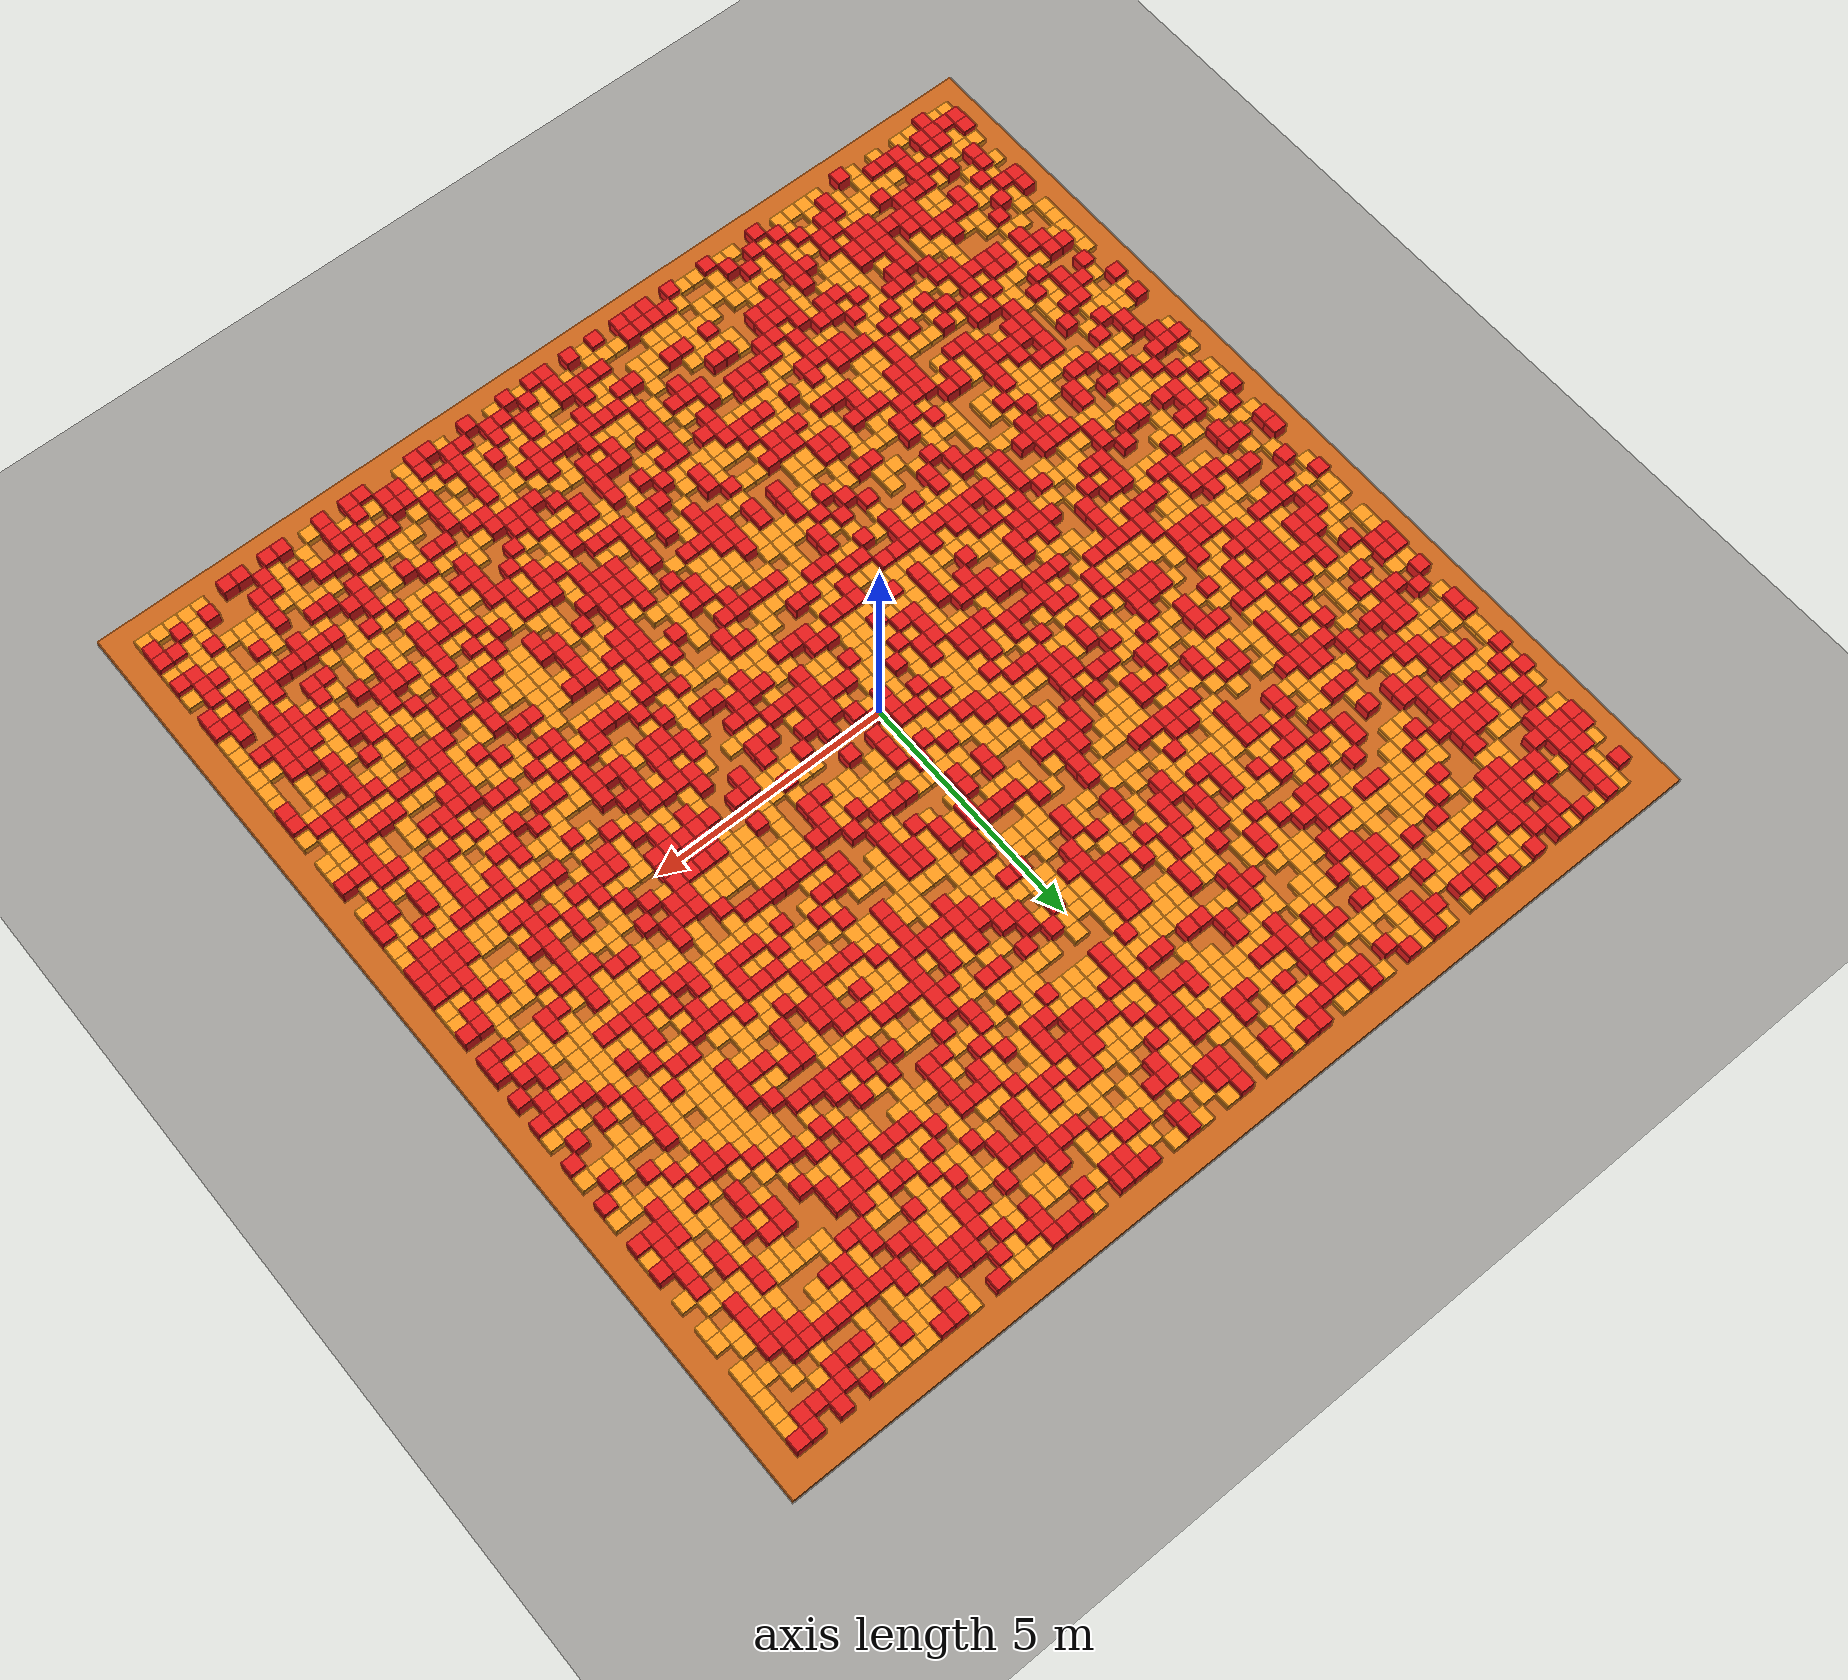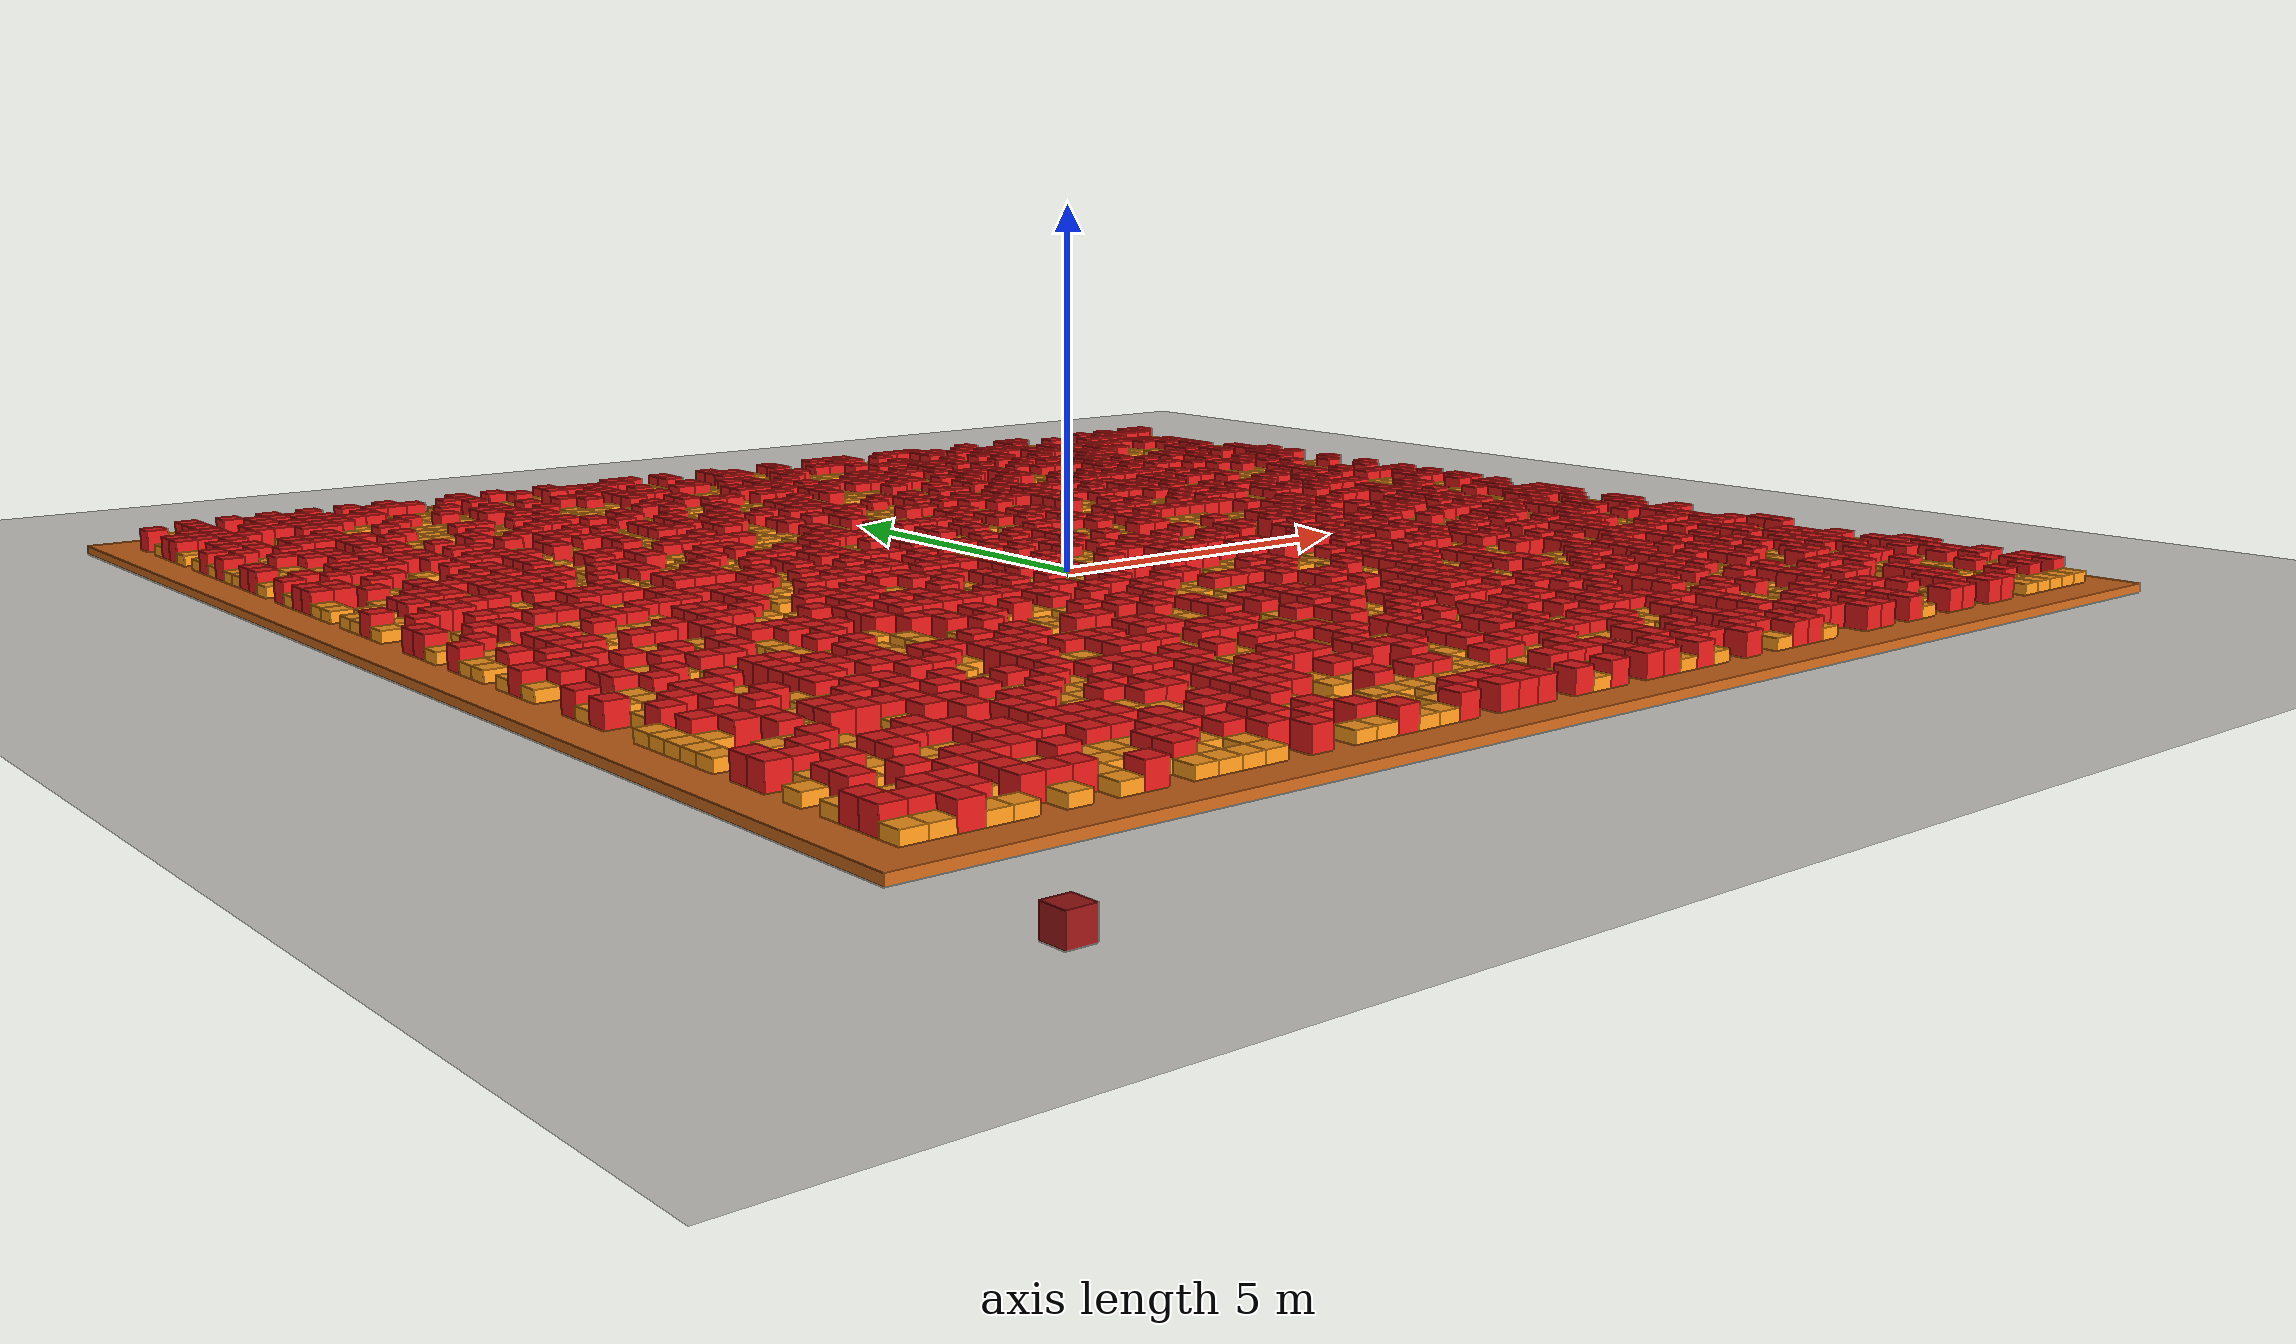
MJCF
<mujoco model="plataforma_gigante_aesir">
  <compiler angle="degree"/>
  <option gravity="0 0 -9.81"/>
  <asset>
    <texture type="skybox" builtin="gradient" rgb1="0.4 0.6 0.8" rgb2="0 0 0" width="512" height="512"/>
    <texture name="tex_piso" type="2d" builtin="checker" rgb1="0.15 0.1 0.1" rgb2="0.08 0.05 0.05" width="512" height="512"/>
    <material name="mat_piso" texture="tex_piso" texrepeat="20 20" texuniform="true" reflectance="0.1"/>
    <texture name="tex_plataforma" type="2d" builtin="flat" rgb1="0.8 0.4 0.1" rgb2="0.1 0.15 0.2" width="512" height="512"/>
    <material name="mat_plataforma" texture="tex_plataforma" texrepeat="40 40" texuniform="true" reflectance="0.1"/>
  </asset>
  <worldbody>
    <light directional="true" pos="0 0 10" dir="0 0 -1"/>
    <geom name="suelo" type="plane" size="40 40 0.1" material="mat_piso" condim="3" friction="1 0.005 0.0001"/>
    <geom name="plataforma_gigante" type="box" size="10 10 0.06" pos="0 0 0.06" material="mat_plataforma" condim="3" friction="1 0.005 0.0001"/>
    <geom name="virtual_obstacle" type="box" size="0.3 0.3 0.3" pos="0 0 -5" rgba="0.85 0.1 0.1 1" condim="3" friction="1 0.005 0.0001"/>
    <geom name="step_15_0_0" type="box" size="0.1485 0.1485 0.075" pos="-9.3555 -9.3555 0.1950" rgba="1 0.6 0.1 1" condim="3" friction="1 0.005 0.0001"/>
    <geom name="step_15_0_1" type="box" size="0.1485 0.1485 0.075" pos="-9.0585 -9.3555 0.1950" rgba="1 0.6 0.1 1" condim="3" friction="1 0.005 0.0001"/>
    <geom name="step_30_0_2" type="box" size="0.1485 0.1485 0.15" pos="-8.7615 -9.3555 0.2700" rgba="0.9 0.1 0.1 1" condim="3" friction="1 0.005 0.0001"/>
    <geom name="step_15_0_3" type="box" size="0.1485 0.1485 0.075" pos="-8.4645 -9.3555 0.1950" rgba="1 0.6 0.1 1" condim="3" friction="1 0.005 0.0001"/>
    <geom name="step_15_0_4" type="box" size="0.1485 0.1485 0.075" pos="-8.1675 -9.3555 0.1950" rgba="1 0.6 0.1 1" condim="3" friction="1 0.005 0.0001"/>
    <geom name="step_15_0_6" type="box" size="0.1485 0.1485 0.075" pos="-7.5735 -9.3555 0.1950" rgba="1 0.6 0.1 1" condim="3" friction="1 0.005 0.0001"/>
    <geom name="step_15_0_8" type="box" size="0.1485 0.1485 0.075" pos="-6.9795 -9.3555 0.1950" rgba="1 0.6 0.1 1" condim="3" friction="1 0.005 0.0001"/>
    <geom name="step_30_0_9" type="box" size="0.1485 0.1485 0.15" pos="-6.6825 -9.3555 0.2700" rgba="0.9 0.1 0.1 1" condim="3" friction="1 0.005 0.0001"/>
    <geom name="step_15_0_11" type="box" size="0.1485 0.1485 0.075" pos="-6.0885 -9.3555 0.1950" rgba="1 0.6 0.1 1" condim="3" friction="1 0.005 0.0001"/>
    <geom name="step_15_0_12" type="box" size="0.1485 0.1485 0.075" pos="-5.7915 -9.3555 0.1950" rgba="1 0.6 0.1 1" condim="3" friction="1 0.005 0.0001"/>
    <geom name="step_15_0_13" type="box" size="0.1485 0.1485 0.075" pos="-5.4945 -9.3555 0.1950" rgba="1 0.6 0.1 1" condim="3" friction="1 0.005 0.0001"/>
    <geom name="step_15_0_14" type="box" size="0.1485 0.1485 0.075" pos="-5.1975 -9.3555 0.1950" rgba="1 0.6 0.1 1" condim="3" friction="1 0.005 0.0001"/>
    <geom name="step_30_0_16" type="box" size="0.1485 0.1485 0.15" pos="-4.6035 -9.3555 0.2700" rgba="0.9 0.1 0.1 1" condim="3" friction="1 0.005 0.0001"/>
    <geom name="step_15_0_18" type="box" size="0.1485 0.1485 0.075" pos="-4.0095 -9.3555 0.1950" rgba="1 0.6 0.1 1" condim="3" friction="1 0.005 0.0001"/>
    <geom name="step_15_0_19" type="box" size="0.1485 0.1485 0.075" pos="-3.7125 -9.3555 0.1950" rgba="1 0.6 0.1 1" condim="3" friction="1 0.005 0.0001"/>
    <geom name="step_30_0_20" type="box" size="0.1485 0.1485 0.15" pos="-3.4155 -9.3555 0.2700" rgba="0.9 0.1 0.1 1" condim="3" friction="1 0.005 0.0001"/>
    <geom name="step_15_0_21" type="box" size="0.1485 0.1485 0.075" pos="-3.1185 -9.3555 0.1950" rgba="1 0.6 0.1 1" condim="3" friction="1 0.005 0.0001"/>
    <geom name="step_15_0_22" type="box" size="0.1485 0.1485 0.075" pos="-2.8215 -9.3555 0.1950" rgba="1 0.6 0.1 1" condim="3" friction="1 0.005 0.0001"/>
    <geom name="step_30_0_23" type="box" size="0.1485 0.1485 0.15" pos="-2.5245 -9.3555 0.2700" rgba="0.9 0.1 0.1 1" condim="3" friction="1 0.005 0.0001"/>
    <geom name="step_30_0_25" type="box" size="0.1485 0.1485 0.15" pos="-1.9305 -9.3555 0.2700" rgba="0.9 0.1 0.1 1" condim="3" friction="1 0.005 0.0001"/>
    <geom name="step_30_0_26" type="box" size="0.1485 0.1485 0.15" pos="-1.6335 -9.3555 0.2700" rgba="0.9 0.1 0.1 1" condim="3" friction="1 0.005 0.0001"/>
    <geom name="step_30_0_27" type="box" size="0.1485 0.1485 0.15" pos="-1.3365 -9.3555 0.2700" rgba="0.9 0.1 0.1 1" condim="3" friction="1 0.005 0.0001"/>
    <geom name="step_30_0_29" type="box" size="0.1485 0.1485 0.15" pos="-0.7425 -9.3555 0.2700" rgba="0.9 0.1 0.1 1" condim="3" friction="1 0.005 0.0001"/>
    <geom name="step_15_0_30" type="box" size="0.1485 0.1485 0.075" pos="-0.4455 -9.3555 0.1950" rgba="1 0.6 0.1 1" condim="3" friction="1 0.005 0.0001"/>
    <geom name="step_30_0_31" type="box" size="0.1485 0.1485 0.15" pos="-0.1485 -9.3555 0.2700" rgba="0.9 0.1 0.1 1" condim="3" friction="1 0.005 0.0001"/>
    <geom name="step_30_0_33" type="box" size="0.1485 0.1485 0.15" pos="0.4455 -9.3555 0.2700" rgba="0.9 0.1 0.1 1" condim="3" friction="1 0.005 0.0001"/>
    <geom name="step_30_0_34" type="box" size="0.1485 0.1485 0.15" pos="0.7425 -9.3555 0.2700" rgba="0.9 0.1 0.1 1" condim="3" friction="1 0.005 0.0001"/>
    <geom name="step_15_0_35" type="box" size="0.1485 0.1485 0.075" pos="1.0395 -9.3555 0.1950" rgba="1 0.6 0.1 1" condim="3" friction="1 0.005 0.0001"/>
    <geom name="step_30_0_36" type="box" size="0.1485 0.1485 0.15" pos="1.3365 -9.3555 0.2700" rgba="0.9 0.1 0.1 1" condim="3" friction="1 0.005 0.0001"/>
    <geom name="step_15_0_37" type="box" size="0.1485 0.1485 0.075" pos="1.6335 -9.3555 0.1950" rgba="1 0.6 0.1 1" condim="3" friction="1 0.005 0.0001"/>
    <geom name="step_30_0_39" type="box" size="0.1485 0.1485 0.15" pos="2.2275 -9.3555 0.2700" rgba="0.9 0.1 0.1 1" condim="3" friction="1 0.005 0.0001"/>
    <geom name="step_15_0_41" type="box" size="0.1485 0.1485 0.075" pos="2.8215 -9.3555 0.1950" rgba="1 0.6 0.1 1" condim="3" friction="1 0.005 0.0001"/>
    <geom name="step_30_0_42" type="box" size="0.1485 0.1485 0.15" pos="3.1185 -9.3555 0.2700" rgba="0.9 0.1 0.1 1" condim="3" friction="1 0.005 0.0001"/>
    <geom name="step_30_0_43" type="box" size="0.1485 0.1485 0.15" pos="3.4155 -9.3555 0.2700" rgba="0.9 0.1 0.1 1" condim="3" friction="1 0.005 0.0001"/>
    <geom name="step_15_0_44" type="box" size="0.1485 0.1485 0.075" pos="3.7125 -9.3555 0.1950" rgba="1 0.6 0.1 1" condim="3" friction="1 0.005 0.0001"/>
    <geom name="step_30_0_47" type="box" size="0.1485 0.1485 0.15" pos="4.6035 -9.3555 0.2700" rgba="0.9 0.1 0.1 1" condim="3" friction="1 0.005 0.0001"/>
    <geom name="step_30_0_48" type="box" size="0.1485 0.1485 0.15" pos="4.9005 -9.3555 0.2700" rgba="0.9 0.1 0.1 1" condim="3" friction="1 0.005 0.0001"/>
    <geom name="step_30_0_50" type="box" size="0.1485 0.1485 0.15" pos="5.4945 -9.3555 0.2700" rgba="0.9 0.1 0.1 1" condim="3" friction="1 0.005 0.0001"/>
    <geom name="step_15_0_51" type="box" size="0.1485 0.1485 0.075" pos="5.7915 -9.3555 0.1950" rgba="1 0.6 0.1 1" condim="3" friction="1 0.005 0.0001"/>
    <geom name="step_30_0_53" type="box" size="0.1485 0.1485 0.15" pos="6.3855 -9.3555 0.2700" rgba="0.9 0.1 0.1 1" condim="3" friction="1 0.005 0.0001"/>
    <geom name="step_30_0_54" type="box" size="0.1485 0.1485 0.15" pos="6.6825 -9.3555 0.2700" rgba="0.9 0.1 0.1 1" condim="3" friction="1 0.005 0.0001"/>
    <geom name="step_30_0_56" type="box" size="0.1485 0.1485 0.15" pos="7.2765 -9.3555 0.2700" rgba="0.9 0.1 0.1 1" condim="3" friction="1 0.005 0.0001"/>
    <geom name="step_30_0_57" type="box" size="0.1485 0.1485 0.15" pos="7.5735 -9.3555 0.2700" rgba="0.9 0.1 0.1 1" condim="3" friction="1 0.005 0.0001"/>
    <geom name="step_15_0_59" type="box" size="0.1485 0.1485 0.075" pos="8.1675 -9.3555 0.1950" rgba="1 0.6 0.1 1" condim="3" friction="1 0.005 0.0001"/>
    <geom name="step_15_0_60" type="box" size="0.1485 0.1485 0.075" pos="8.4645 -9.3555 0.1950" rgba="1 0.6 0.1 1" condim="3" friction="1 0.005 0.0001"/>
    <geom name="step_15_0_61" type="box" size="0.1485 0.1485 0.075" pos="8.7615 -9.3555 0.1950" rgba="1 0.6 0.1 1" condim="3" friction="1 0.005 0.0001"/>
    <geom name="step_15_0_62" type="box" size="0.1485 0.1485 0.075" pos="9.0585 -9.3555 0.1950" rgba="1 0.6 0.1 1" condim="3" friction="1 0.005 0.0001"/>
    <geom name="step_15_0_63" type="box" size="0.1485 0.1485 0.075" pos="9.3555 -9.3555 0.1950" rgba="1 0.6 0.1 1" condim="3" friction="1 0.005 0.0001"/>
    <geom name="step_30_1_0" type="box" size="0.1485 0.1485 0.15" pos="-9.3555 -9.0585 0.2700" rgba="0.9 0.1 0.1 1" condim="3" friction="1 0.005 0.0001"/>
    <geom name="step_30_1_1" type="box" size="0.1485 0.1485 0.15" pos="-9.0585 -9.0585 0.2700" rgba="0.9 0.1 0.1 1" condim="3" friction="1 0.005 0.0001"/>
    <geom name="step_30_1_2" type="box" size="0.1485 0.1485 0.15" pos="-8.7615 -9.0585 0.2700" rgba="0.9 0.1 0.1 1" condim="3" friction="1 0.005 0.0001"/>
    <geom name="step_30_1_3" type="box" size="0.1485 0.1485 0.15" pos="-8.4645 -9.0585 0.2700" rgba="0.9 0.1 0.1 1" condim="3" friction="1 0.005 0.0001"/>
    <geom name="step_30_1_5" type="box" size="0.1485 0.1485 0.15" pos="-7.8705 -9.0585 0.2700" rgba="0.9 0.1 0.1 1" condim="3" friction="1 0.005 0.0001"/>
    <geom name="step_30_1_6" type="box" size="0.1485 0.1485 0.15" pos="-7.5735 -9.0585 0.2700" rgba="0.9 0.1 0.1 1" condim="3" friction="1 0.005 0.0001"/>
    <geom name="step_30_1_7" type="box" size="0.1485 0.1485 0.15" pos="-7.2765 -9.0585 0.2700" rgba="0.9 0.1 0.1 1" condim="3" friction="1 0.005 0.0001"/>
    <geom name="step_15_1_8" type="box" size="0.1485 0.1485 0.075" pos="-6.9795 -9.0585 0.1950" rgba="1 0.6 0.1 1" condim="3" friction="1 0.005 0.0001"/>
    <geom name="step_15_1_10" type="box" size="0.1485 0.1485 0.075" pos="-6.3855 -9.0585 0.1950" rgba="1 0.6 0.1 1" condim="3" friction="1 0.005 0.0001"/>
    <geom name="step_30_1_11" type="box" size="0.1485 0.1485 0.15" pos="-6.0885 -9.0585 0.2700" rgba="0.9 0.1 0.1 1" condim="3" friction="1 0.005 0.0001"/>
    <geom name="step_15_1_12" type="box" size="0.1485 0.1485 0.075" pos="-5.7915 -9.0585 0.1950" rgba="1 0.6 0.1 1" condim="3" friction="1 0.005 0.0001"/>
    <geom name="step_15_1_14" type="box" size="0.1485 0.1485 0.075" pos="-5.1975 -9.0585 0.1950" rgba="1 0.6 0.1 1" condim="3" friction="1 0.005 0.0001"/>
    <geom name="step_30_1_15" type="box" size="0.1485 0.1485 0.15" pos="-4.9005 -9.0585 0.2700" rgba="0.9 0.1 0.1 1" condim="3" friction="1 0.005 0.0001"/>
    <geom name="step_15_1_16" type="box" size="0.1485 0.1485 0.075" pos="-4.6035 -9.0585 0.1950" rgba="1 0.6 0.1 1" condim="3" friction="1 0.005 0.0001"/>
    <geom name="step_30_1_17" type="box" size="0.1485 0.1485 0.15" pos="-4.3065 -9.0585 0.2700" rgba="0.9 0.1 0.1 1" condim="3" friction="1 0.005 0.0001"/>
    <geom name="step_30_1_19" type="box" size="0.1485 0.1485 0.15" pos="-3.7125 -9.0585 0.2700" rgba="0.9 0.1 0.1 1" condim="3" friction="1 0.005 0.0001"/>
    <geom name="step_15_1_20" type="box" size="0.1485 0.1485 0.075" pos="-3.4155 -9.0585 0.1950" rgba="1 0.6 0.1 1" condim="3" friction="1 0.005 0.0001"/>
    <geom name="step_15_1_23" type="box" size="0.1485 0.1485 0.075" pos="-2.5245 -9.0585 0.1950" rgba="1 0.6 0.1 1" condim="3" friction="1 0.005 0.0001"/>
    <geom name="step_30_1_24" type="box" size="0.1485 0.1485 0.15" pos="-2.2275 -9.0585 0.2700" rgba="0.9 0.1 0.1 1" condim="3" friction="1 0.005 0.0001"/>
    <geom name="step_30_1_25" type="box" size="0.1485 0.1485 0.15" pos="-1.9305 -9.0585 0.2700" rgba="0.9 0.1 0.1 1" condim="3" friction="1 0.005 0.0001"/>
    <geom name="step_30_1_26" type="box" size="0.1485 0.1485 0.15" pos="-1.6335 -9.0585 0.2700" rgba="0.9 0.1 0.1 1" condim="3" friction="1 0.005 0.0001"/>
    <geom name="step_30_1_27" type="box" size="0.1485 0.1485 0.15" pos="-1.3365 -9.0585 0.2700" rgba="0.9 0.1 0.1 1" condim="3" friction="1 0.005 0.0001"/>
    <geom name="step_15_1_28" type="box" size="0.1485 0.1485 0.075" pos="-1.0395 -9.0585 0.1950" rgba="1 0.6 0.1 1" condim="3" friction="1 0.005 0.0001"/>
    <geom name="step_15_1_29" type="box" size="0.1485 0.1485 0.075" pos="-0.7425 -9.0585 0.1950" rgba="1 0.6 0.1 1" condim="3" friction="1 0.005 0.0001"/>
    <geom name="step_15_1_30" type="box" size="0.1485 0.1485 0.075" pos="-0.4455 -9.0585 0.1950" rgba="1 0.6 0.1 1" condim="3" friction="1 0.005 0.0001"/>
    <geom name="step_15_1_32" type="box" size="0.1485 0.1485 0.075" pos="0.1485 -9.0585 0.1950" rgba="1 0.6 0.1 1" condim="3" friction="1 0.005 0.0001"/>
    <geom name="step_30_1_33" type="box" size="0.1485 0.1485 0.15" pos="0.4455 -9.0585 0.2700" rgba="0.9 0.1 0.1 1" condim="3" friction="1 0.005 0.0001"/>
    <geom name="step_15_1_34" type="box" size="0.1485 0.1485 0.075" pos="0.7425 -9.0585 0.1950" rgba="1 0.6 0.1 1" condim="3" friction="1 0.005 0.0001"/>
    <geom name="step_30_1_35" type="box" size="0.1485 0.1485 0.15" pos="1.0395 -9.0585 0.2700" rgba="0.9 0.1 0.1 1" condim="3" friction="1 0.005 0.0001"/>
    <geom name="step_30_1_37" type="box" size="0.1485 0.1485 0.15" pos="1.6335 -9.0585 0.2700" rgba="0.9 0.1 0.1 1" condim="3" friction="1 0.005 0.0001"/>
    <geom name="step_30_1_38" type="box" size="0.1485 0.1485 0.15" pos="1.9305 -9.0585 0.2700" rgba="0.9 0.1 0.1 1" condim="3" friction="1 0.005 0.0001"/>
    <geom name="step_30_1_40" type="box" size="0.1485 0.1485 0.15" pos="2.5245 -9.0585 0.2700" rgba="0.9 0.1 0.1 1" condim="3" friction="1 0.005 0.0001"/>
    <geom name="step_30_1_41" type="box" size="0.1485 0.1485 0.15" pos="2.8215 -9.0585 0.2700" rgba="0.9 0.1 0.1 1" condim="3" friction="1 0.005 0.0001"/>
    <geom name="step_30_1_43" type="box" size="0.1485 0.1485 0.15" pos="3.4155 -9.0585 0.2700" rgba="0.9 0.1 0.1 1" condim="3" friction="1 0.005 0.0001"/>
    <geom name="step_15_1_44" type="box" size="0.1485 0.1485 0.075" pos="3.7125 -9.0585 0.1950" rgba="1 0.6 0.1 1" condim="3" friction="1 0.005 0.0001"/>
    <geom name="step_30_1_45" type="box" size="0.1485 0.1485 0.15" pos="4.0095 -9.0585 0.2700" rgba="0.9 0.1 0.1 1" condim="3" friction="1 0.005 0.0001"/>
    <geom name="step_30_1_46" type="box" size="0.1485 0.1485 0.15" pos="4.3065 -9.0585 0.2700" rgba="0.9 0.1 0.1 1" condim="3" friction="1 0.005 0.0001"/>
    <geom name="step_15_1_47" type="box" size="0.1485 0.1485 0.075" pos="4.6035 -9.0585 0.1950" rgba="1 0.6 0.1 1" condim="3" friction="1 0.005 0.0001"/>
    <geom name="step_30_1_48" type="box" size="0.1485 0.1485 0.15" pos="4.9005 -9.0585 0.2700" rgba="0.9 0.1 0.1 1" condim="3" friction="1 0.005 0.0001"/>
    <geom name="step_15_1_49" type="box" size="0.1485 0.1485 0.075" pos="5.1975 -9.0585 0.1950" rgba="1 0.6 0.1 1" condim="3" friction="1 0.005 0.0001"/>
    <geom name="step_30_1_50" type="box" size="0.1485 0.1485 0.15" pos="5.4945 -9.0585 0.2700" rgba="0.9 0.1 0.1 1" condim="3" friction="1 0.005 0.0001"/>
    <geom name="step_15_1_52" type="box" size="0.1485 0.1485 0.075" pos="6.0885 -9.0585 0.1950" rgba="1 0.6 0.1 1" condim="3" friction="1 0.005 0.0001"/>
    <geom name="step_15_1_54" type="box" size="0.1485 0.1485 0.075" pos="6.6825 -9.0585 0.1950" rgba="1 0.6 0.1 1" condim="3" friction="1 0.005 0.0001"/>
    <geom name="step_30_1_55" type="box" size="0.1485 0.1485 0.15" pos="6.9795 -9.0585 0.2700" rgba="0.9 0.1 0.1 1" condim="3" friction="1 0.005 0.0001"/>
    <geom name="step_30_1_59" type="box" size="0.1485 0.1485 0.15" pos="8.1675 -9.0585 0.2700" rgba="0.9 0.1 0.1 1" condim="3" friction="1 0.005 0.0001"/>
    <geom name="step_15_1_60" type="box" size="0.1485 0.1485 0.075" pos="8.4645 -9.0585 0.1950" rgba="1 0.6 0.1 1" condim="3" friction="1 0.005 0.0001"/>
    <geom name="step_30_1_61" type="box" size="0.1485 0.1485 0.15" pos="8.7615 -9.0585 0.2700" rgba="0.9 0.1 0.1 1" condim="3" friction="1 0.005 0.0001"/>
    <geom name="step_30_1_63" type="box" size="0.1485 0.1485 0.15" pos="9.3555 -9.0585 0.2700" rgba="0.9 0.1 0.1 1" condim="3" friction="1 0.005 0.0001"/>
    <geom name="step_30_2_0" type="box" size="0.1485 0.1485 0.15" pos="-9.3555 -8.7615 0.2700" rgba="0.9 0.1 0.1 1" condim="3" friction="1 0.005 0.0001"/>
    <geom name="step_15_2_1" type="box" size="0.1485 0.1485 0.075" pos="-9.0585 -8.7615 0.1950" rgba="1 0.6 0.1 1" condim="3" friction="1 0.005 0.0001"/>
    <geom name="step_30_2_2" type="box" size="0.1485 0.1485 0.15" pos="-8.7615 -8.7615 0.2700" rgba="0.9 0.1 0.1 1" condim="3" friction="1 0.005 0.0001"/>
    <geom name="step_30_2_3" type="box" size="0.1485 0.1485 0.15" pos="-8.4645 -8.7615 0.2700" rgba="0.9 0.1 0.1 1" condim="3" friction="1 0.005 0.0001"/>
    <geom name="step_15_2_4" type="box" size="0.1485 0.1485 0.075" pos="-8.1675 -8.7615 0.1950" rgba="1 0.6 0.1 1" condim="3" friction="1 0.005 0.0001"/>
    <geom name="step_30_2_5" type="box" size="0.1485 0.1485 0.15" pos="-7.8705 -8.7615 0.2700" rgba="0.9 0.1 0.1 1" condim="3" friction="1 0.005 0.0001"/>
    <geom name="step_15_2_6" type="box" size="0.1485 0.1485 0.075" pos="-7.5735 -8.7615 0.1950" rgba="1 0.6 0.1 1" condim="3" friction="1 0.005 0.0001"/>
    <geom name="step_15_2_7" type="box" size="0.1485 0.1485 0.075" pos="-7.2765 -8.7615 0.1950" rgba="1 0.6 0.1 1" condim="3" friction="1 0.005 0.0001"/>
    <geom name="step_15_2_8" type="box" size="0.1485 0.1485 0.075" pos="-6.9795 -8.7615 0.1950" rgba="1 0.6 0.1 1" condim="3" friction="1 0.005 0.0001"/>
    <geom name="step_15_2_9" type="box" size="0.1485 0.1485 0.075" pos="-6.6825 -8.7615 0.1950" rgba="1 0.6 0.1 1" condim="3" friction="1 0.005 0.0001"/>
    <geom name="step_15_2_10" type="box" size="0.1485 0.1485 0.075" pos="-6.3855 -8.7615 0.1950" rgba="1 0.6 0.1 1" condim="3" friction="1 0.005 0.0001"/>
    <geom name="step_30_2_11" type="box" size="0.1485 0.1485 0.15" pos="-6.0885 -8.7615 0.2700" rgba="0.9 0.1 0.1 1" condim="3" friction="1 0.005 0.0001"/>
    <geom name="step_30_2_12" type="box" size="0.1485 0.1485 0.15" pos="-5.7915 -8.7615 0.2700" rgba="0.9 0.1 0.1 1" condim="3" friction="1 0.005 0.0001"/>
    <geom name="step_15_2_13" type="box" size="0.1485 0.1485 0.075" pos="-5.4945 -8.7615 0.1950" rgba="1 0.6 0.1 1" condim="3" friction="1 0.005 0.0001"/>
    <geom name="step_30_2_14" type="box" size="0.1485 0.1485 0.15" pos="-5.1975 -8.7615 0.2700" rgba="0.9 0.1 0.1 1" condim="3" friction="1 0.005 0.0001"/>
    <geom name="step_15_2_15" type="box" size="0.1485 0.1485 0.075" pos="-4.9005 -8.7615 0.1950" rgba="1 0.6 0.1 1" condim="3" friction="1 0.005 0.0001"/>
    <geom name="step_30_2_16" type="box" size="0.1485 0.1485 0.15" pos="-4.6035 -8.7615 0.2700" rgba="0.9 0.1 0.1 1" condim="3" friction="1 0.005 0.0001"/>
    <geom name="step_15_2_17" type="box" size="0.1485 0.1485 0.075" pos="-4.3065 -8.7615 0.1950" rgba="1 0.6 0.1 1" condim="3" friction="1 0.005 0.0001"/>
    <geom name="step_30_2_18" type="box" size="0.1485 0.1485 0.15" pos="-4.0095 -8.7615 0.2700" rgba="0.9 0.1 0.1 1" condim="3" friction="1 0.005 0.0001"/>
    <geom name="step_15_2_20" type="box" size="0.1485 0.1485 0.075" pos="-3.4155 -8.7615 0.1950" rgba="1 0.6 0.1 1" condim="3" friction="1 0.005 0.0001"/>
    <geom name="step_15_2_21" type="box" size="0.1485 0.1485 0.075" pos="-3.1185 -8.7615 0.1950" rgba="1 0.6 0.1 1" condim="3" friction="1 0.005 0.0001"/>
    <geom name="step_15_2_22" type="box" size="0.1485 0.1485 0.075" pos="-2.8215 -8.7615 0.1950" rgba="1 0.6 0.1 1" condim="3" friction="1 0.005 0.0001"/>
    <geom name="step_15_2_24" type="box" size="0.1485 0.1485 0.075" pos="-2.2275 -8.7615 0.1950" rgba="1 0.6 0.1 1" condim="3" friction="1 0.005 0.0001"/>
    <geom name="step_15_2_25" type="box" size="0.1485 0.1485 0.075" pos="-1.9305 -8.7615 0.1950" rgba="1 0.6 0.1 1" condim="3" friction="1 0.005 0.0001"/>
    <geom name="step_15_2_26" type="box" size="0.1485 0.1485 0.075" pos="-1.6335 -8.7615 0.1950" rgba="1 0.6 0.1 1" condim="3" friction="1 0.005 0.0001"/>
    <geom name="step_30_2_30" type="box" size="0.1485 0.1485 0.15" pos="-0.4455 -8.7615 0.2700" rgba="0.9 0.1 0.1 1" condim="3" friction="1 0.005 0.0001"/>
    <geom name="step_30_2_31" type="box" size="0.1485 0.1485 0.15" pos="-0.1485 -8.7615 0.2700" rgba="0.9 0.1 0.1 1" condim="3" friction="1 0.005 0.0001"/>
    <geom name="step_30_2_32" type="box" size="0.1485 0.1485 0.15" pos="0.1485 -8.7615 0.2700" rgba="0.9 0.1 0.1 1" condim="3" friction="1 0.005 0.0001"/>
    <geom name="step_30_2_33" type="box" size="0.1485 0.1485 0.15" pos="0.4455 -8.7615 0.2700" rgba="0.9 0.1 0.1 1" condim="3" friction="1 0.005 0.0001"/>
    <geom name="step_15_2_34" type="box" size="0.1485 0.1485 0.075" pos="0.7425 -8.7615 0.1950" rgba="1 0.6 0.1 1" condim="3" friction="1 0.005 0.0001"/>
    <geom name="step_15_2_35" type="box" size="0.1485 0.1485 0.075" pos="1.0395 -8.7615 0.1950" rgba="1 0.6 0.1 1" condim="3" friction="1 0.005 0.0001"/>
    <geom name="step_30_2_36" type="box" size="0.1485 0.1485 0.15" pos="1.3365 -8.7615 0.2700" rgba="0.9 0.1 0.1 1" condim="3" friction="1 0.005 0.0001"/>
    <geom name="step_15_2_37" type="box" size="0.1485 0.1485 0.075" pos="1.6335 -8.7615 0.1950" rgba="1 0.6 0.1 1" condim="3" friction="1 0.005 0.0001"/>
    <geom name="step_30_2_38" type="box" size="0.1485 0.1485 0.15" pos="1.9305 -8.7615 0.2700" rgba="0.9 0.1 0.1 1" condim="3" friction="1 0.005 0.0001"/>
    <geom name="step_15_2_39" type="box" size="0.1485 0.1485 0.075" pos="2.2275 -8.7615 0.1950" rgba="1 0.6 0.1 1" condim="3" friction="1 0.005 0.0001"/>
    <geom name="step_15_2_40" type="box" size="0.1485 0.1485 0.075" pos="2.5245 -8.7615 0.1950" rgba="1 0.6 0.1 1" condim="3" friction="1 0.005 0.0001"/>
    <geom name="step_30_2_41" type="box" size="0.1485 0.1485 0.15" pos="2.8215 -8.7615 0.2700" rgba="0.9 0.1 0.1 1" condim="3" friction="1 0.005 0.0001"/>
    <geom name="step_30_2_42" type="box" size="0.1485 0.1485 0.15" pos="3.1185 -8.7615 0.2700" rgba="0.9 0.1 0.1 1" condim="3" friction="1 0.005 0.0001"/>
    <geom name="step_15_2_43" type="box" size="0.1485 0.1485 0.075" pos="3.4155 -8.7615 0.1950" rgba="1 0.6 0.1 1" condim="3" friction="1 0.005 0.0001"/>
    <geom name="step_15_2_44" type="box" size="0.1485 0.1485 0.075" pos="3.7125 -8.7615 0.1950" rgba="1 0.6 0.1 1" condim="3" friction="1 0.005 0.0001"/>
    <geom name="step_30_2_45" type="box" size="0.1485 0.1485 0.15" pos="4.0095 -8.7615 0.2700" rgba="0.9 0.1 0.1 1" condim="3" friction="1 0.005 0.0001"/>
    <geom name="step_30_2_46" type="box" size="0.1485 0.1485 0.15" pos="4.3065 -8.7615 0.2700" rgba="0.9 0.1 0.1 1" condim="3" friction="1 0.005 0.0001"/>
    <geom name="step_15_2_48" type="box" size="0.1485 0.1485 0.075" pos="4.9005 -8.7615 0.1950" rgba="1 0.6 0.1 1" condim="3" friction="1 0.005 0.0001"/>
    <geom name="step_30_2_49" type="box" size="0.1485 0.1485 0.15" pos="5.1975 -8.7615 0.2700" rgba="0.9 0.1 0.1 1" condim="3" friction="1 0.005 0.0001"/>
    <geom name="step_30_2_50" type="box" size="0.1485 0.1485 0.15" pos="5.4945 -8.7615 0.2700" rgba="0.9 0.1 0.1 1" condim="3" friction="1 0.005 0.0001"/>
    <geom name="step_15_2_52" type="box" size="0.1485 0.1485 0.075" pos="6.0885 -8.7615 0.1950" rgba="1 0.6 0.1 1" condim="3" friction="1 0.005 0.0001"/>
    <geom name="step_30_2_53" type="box" size="0.1485 0.1485 0.15" pos="6.3855 -8.7615 0.2700" rgba="0.9 0.1 0.1 1" condim="3" friction="1 0.005 0.0001"/>
    <geom name="step_15_2_54" type="box" size="0.1485 0.1485 0.075" pos="6.6825 -8.7615 0.1950" rgba="1 0.6 0.1 1" condim="3" friction="1 0.005 0.0001"/>
    <geom name="step_30_2_55" type="box" size="0.1485 0.1485 0.15" pos="6.9795 -8.7615 0.2700" rgba="0.9 0.1 0.1 1" condim="3" friction="1 0.005 0.0001"/>
    <geom name="step_30_2_56" type="box" size="0.1485 0.1485 0.15" pos="7.2765 -8.7615 0.2700" rgba="0.9 0.1 0.1 1" condim="3" friction="1 0.005 0.0001"/>
    <geom name="step_15_2_60" type="box" size="0.1485 0.1485 0.075" pos="8.4645 -8.7615 0.1950" rgba="1 0.6 0.1 1" condim="3" friction="1 0.005 0.0001"/>
    <geom name="step_15_2_61" type="box" size="0.1485 0.1485 0.075" pos="8.7615 -8.7615 0.1950" rgba="1 0.6 0.1 1" condim="3" friction="1 0.005 0.0001"/>
    <geom name="step_30_2_62" type="box" size="0.1485 0.1485 0.15" pos="9.0585 -8.7615 0.2700" rgba="0.9 0.1 0.1 1" condim="3" friction="1 0.005 0.0001"/>
    <geom name="step_30_2_63" type="box" size="0.1485 0.1485 0.15" pos="9.3555 -8.7615 0.2700" rgba="0.9 0.1 0.1 1" condim="3" friction="1 0.005 0.0001"/>
    <geom name="step_15_3_0" type="box" size="0.1485 0.1485 0.075" pos="-9.3555 -8.4645 0.1950" rgba="1 0.6 0.1 1" condim="3" friction="1 0.005 0.0001"/>
    <geom name="step_15_3_1" type="box" size="0.1485 0.1485 0.075" pos="-9.0585 -8.4645 0.1950" rgba="1 0.6 0.1 1" condim="3" friction="1 0.005 0.0001"/>
    <geom name="step_15_3_2" type="box" size="0.1485 0.1485 0.075" pos="-8.7615 -8.4645 0.1950" rgba="1 0.6 0.1 1" condim="3" friction="1 0.005 0.0001"/>
    <geom name="step_15_3_3" type="box" size="0.1485 0.1485 0.075" pos="-8.4645 -8.4645 0.1950" rgba="1 0.6 0.1 1" condim="3" friction="1 0.005 0.0001"/>
    <geom name="step_30_3_4" type="box" size="0.1485 0.1485 0.15" pos="-8.1675 -8.4645 0.2700" rgba="0.9 0.1 0.1 1" condim="3" friction="1 0.005 0.0001"/>
    <geom name="step_30_3_5" type="box" size="0.1485 0.1485 0.15" pos="-7.8705 -8.4645 0.2700" rgba="0.9 0.1 0.1 1" condim="3" friction="1 0.005 0.0001"/>
    <geom name="step_15_3_7" type="box" size="0.1485 0.1485 0.075" pos="-7.2765 -8.4645 0.1950" rgba="1 0.6 0.1 1" condim="3" friction="1 0.005 0.0001"/>
    <geom name="step_30_3_8" type="box" size="0.1485 0.1485 0.15" pos="-6.9795 -8.4645 0.2700" rgba="0.9 0.1 0.1 1" condim="3" friction="1 0.005 0.0001"/>
    <geom name="step_15_3_9" type="box" size="0.1485 0.1485 0.075" pos="-6.6825 -8.4645 0.1950" rgba="1 0.6 0.1 1" condim="3" friction="1 0.005 0.0001"/>
    <geom name="step_15_3_10" type="box" size="0.1485 0.1485 0.075" pos="-6.3855 -8.4645 0.1950" rgba="1 0.6 0.1 1" condim="3" friction="1 0.005 0.0001"/>
    <geom name="step_15_3_11" type="box" size="0.1485 0.1485 0.075" pos="-6.0885 -8.4645 0.1950" rgba="1 0.6 0.1 1" condim="3" friction="1 0.005 0.0001"/>
    <geom name="step_30_3_12" type="box" size="0.1485 0.1485 0.15" pos="-5.7915 -8.4645 0.2700" rgba="0.9 0.1 0.1 1" condim="3" friction="1 0.005 0.0001"/>
    <geom name="step_30_3_13" type="box" size="0.1485 0.1485 0.15" pos="-5.4945 -8.4645 0.2700" rgba="0.9 0.1 0.1 1" condim="3" friction="1 0.005 0.0001"/>
    <geom name="step_15_3_14" type="box" size="0.1485 0.1485 0.075" pos="-5.1975 -8.4645 0.1950" rgba="1 0.6 0.1 1" condim="3" friction="1 0.005 0.0001"/>
    <geom name="step_15_3_15" type="box" size="0.1485 0.1485 0.075" pos="-4.9005 -8.4645 0.1950" rgba="1 0.6 0.1 1" condim="3" friction="1 0.005 0.0001"/>
    <geom name="step_30_3_16" type="box" size="0.1485 0.1485 0.15" pos="-4.6035 -8.4645 0.2700" rgba="0.9 0.1 0.1 1" condim="3" friction="1 0.005 0.0001"/>
    <geom name="step_15_3_17" type="box" size="0.1485 0.1485 0.075" pos="-4.3065 -8.4645 0.1950" rgba="1 0.6 0.1 1" condim="3" friction="1 0.005 0.0001"/>
    <geom name="step_15_3_18" type="box" size="0.1485 0.1485 0.075" pos="-4.0095 -8.4645 0.1950" rgba="1 0.6 0.1 1" condim="3" friction="1 0.005 0.0001"/>
    <geom name="step_15_3_19" type="box" size="0.1485 0.1485 0.075" pos="-3.7125 -8.4645 0.1950" rgba="1 0.6 0.1 1" condim="3" friction="1 0.005 0.0001"/>
    <geom name="step_15_3_20" type="box" size="0.1485 0.1485 0.075" pos="-3.4155 -8.4645 0.1950" rgba="1 0.6 0.1 1" condim="3" friction="1 0.005 0.0001"/>
    <geom name="step_15_3_22" type="box" size="0.1485 0.1485 0.075" pos="-2.8215 -8.4645 0.1950" rgba="1 0.6 0.1 1" condim="3" friction="1 0.005 0.0001"/>
    <geom name="step_15_3_23" type="box" size="0.1485 0.1485 0.075" pos="-2.5245 -8.4645 0.1950" rgba="1 0.6 0.1 1" condim="3" friction="1 0.005 0.0001"/>
    <geom name="step_15_3_24" type="box" size="0.1485 0.1485 0.075" pos="-2.2275 -8.4645 0.1950" rgba="1 0.6 0.1 1" condim="3" friction="1 0.005 0.0001"/>
    <geom name="step_15_3_25" type="box" size="0.1485 0.1485 0.075" pos="-1.9305 -8.4645 0.1950" rgba="1 0.6 0.1 1" condim="3" friction="1 0.005 0.0001"/>
    <geom name="step_15_3_26" type="box" size="0.1485 0.1485 0.075" pos="-1.6335 -8.4645 0.1950" rgba="1 0.6 0.1 1" condim="3" friction="1 0.005 0.0001"/>
    <geom name="step_15_3_27" type="box" size="0.1485 0.1485 0.075" pos="-1.3365 -8.4645 0.1950" rgba="1 0.6 0.1 1" condim="3" friction="1 0.005 0.0001"/>
    <geom name="step_15_3_28" type="box" size="0.1485 0.1485 0.075" pos="-1.0395 -8.4645 0.1950" rgba="1 0.6 0.1 1" condim="3" friction="1 0.005 0.0001"/>
    <geom name="step_15_3_30" type="box" size="0.1485 0.1485 0.075" pos="-0.4455 -8.4645 0.1950" rgba="1 0.6 0.1 1" condim="3" friction="1 0.005 0.0001"/>
    <geom name="step_15_3_31" type="box" size="0.1485 0.1485 0.075" pos="-0.1485 -8.4645 0.1950" rgba="1 0.6 0.1 1" condim="3" friction="1 0.005 0.0001"/>
    <geom name="step_30_3_32" type="box" size="0.1485 0.1485 0.15" pos="0.1485 -8.4645 0.2700" rgba="0.9 0.1 0.1 1" condim="3" friction="1 0.005 0.0001"/>
    <geom name="step_15_3_35" type="box" size="0.1485 0.1485 0.075" pos="1.0395 -8.4645 0.1950" rgba="1 0.6 0.1 1" condim="3" friction="1 0.005 0.0001"/>
    <geom name="step_30_3_36" type="box" size="0.1485 0.1485 0.15" pos="1.3365 -8.4645 0.2700" rgba="0.9 0.1 0.1 1" condim="3" friction="1 0.005 0.0001"/>
    <geom name="step_15_3_37" type="box" size="0.1485 0.1485 0.075" pos="1.6335 -8.4645 0.1950" rgba="1 0.6 0.1 1" condim="3" friction="1 0.005 0.0001"/>
    <geom name="step_15_3_38" type="box" size="0.1485 0.1485 0.075" pos="1.9305 -8.4645 0.1950" rgba="1 0.6 0.1 1" condim="3" friction="1 0.005 0.0001"/>
    <geom name="step_30_3_39" type="box" size="0.1485 0.1485 0.15" pos="2.2275 -8.4645 0.2700" rgba="0.9 0.1 0.1 1" condim="3" friction="1 0.005 0.0001"/>
    <geom name="step_15_3_40" type="box" size="0.1485 0.1485 0.075" pos="2.5245 -8.4645 0.1950" rgba="1 0.6 0.1 1" condim="3" friction="1 0.005 0.0001"/>
    <geom name="step_30_3_41" type="box" size="0.1485 0.1485 0.15" pos="2.8215 -8.4645 0.2700" rgba="0.9 0.1 0.1 1" condim="3" friction="1 0.005 0.0001"/>
    <geom name="step_15_3_42" type="box" size="0.1485 0.1485 0.075" pos="3.1185 -8.4645 0.1950" rgba="1 0.6 0.1 1" condim="3" friction="1 0.005 0.0001"/>
    <geom name="step_30_3_44" type="box" size="0.1485 0.1485 0.15" pos="3.7125 -8.4645 0.2700" rgba="0.9 0.1 0.1 1" condim="3" friction="1 0.005 0.0001"/>
    <geom name="step_15_3_45" type="box" size="0.1485 0.1485 0.075" pos="4.0095 -8.4645 0.1950" rgba="1 0.6 0.1 1" condim="3" friction="1 0.005 0.0001"/>
    <geom name="step_30_3_47" type="box" size="0.1485 0.1485 0.15" pos="4.6035 -8.4645 0.2700" rgba="0.9 0.1 0.1 1" condim="3" friction="1 0.005 0.0001"/>
    <geom name="step_30_3_48" type="box" size="0.1485 0.1485 0.15" pos="4.9005 -8.4645 0.2700" rgba="0.9 0.1 0.1 1" condim="3" friction="1 0.005 0.0001"/>
    <geom name="step_30_3_49" type="box" size="0.1485 0.1485 0.15" pos="5.1975 -8.4645 0.2700" rgba="0.9 0.1 0.1 1" condim="3" friction="1 0.005 0.0001"/>
    <geom name="step_15_3_50" type="box" size="0.1485 0.1485 0.075" pos="5.4945 -8.4645 0.1950" rgba="1 0.6 0.1 1" condim="3" friction="1 0.005 0.0001"/>
    <geom name="step_30_3_51" type="box" size="0.1485 0.1485 0.15" pos="5.7915 -8.4645 0.2700" rgba="0.9 0.1 0.1 1" condim="3" friction="1 0.005 0.0001"/>
    <geom name="step_30_3_52" type="box" size="0.1485 0.1485 0.15" pos="6.0885 -8.4645 0.2700" rgba="0.9 0.1 0.1 1" condim="3" friction="1 0.005 0.0001"/>
    <geom name="step_15_3_54" type="box" size="0.1485 0.1485 0.075" pos="6.6825 -8.4645 0.1950" rgba="1 0.6 0.1 1" condim="3" friction="1 0.005 0.0001"/>
    <geom name="step_15_3_55" type="box" size="0.1485 0.1485 0.075" pos="6.9795 -8.4645 0.1950" rgba="1 0.6 0.1 1" condim="3" friction="1 0.005 0.0001"/>
    <geom name="step_30_3_56" type="box" size="0.1485 0.1485 0.15" pos="7.2765 -8.4645 0.2700" rgba="0.9 0.1 0.1 1" condim="3" friction="1 0.005 0.0001"/>
    <geom name="step_15_3_57" type="box" size="0.1485 0.1485 0.075" pos="7.5735 -8.4645 0.1950" rgba="1 0.6 0.1 1" condim="3" friction="1 0.005 0.0001"/>
    <geom name="step_15_3_58" type="box" size="0.1485 0.1485 0.075" pos="7.8705 -8.4645 0.1950" rgba="1 0.6 0.1 1" condim="3" friction="1 0.005 0.0001"/>
    <geom name="step_15_3_59" type="box" size="0.1485 0.1485 0.075" pos="8.1675 -8.4645 0.1950" rgba="1 0.6 0.1 1" condim="3" friction="1 0.005 0.0001"/>
    <geom name="step_30_3_60" type="box" size="0.1485 0.1485 0.15" pos="8.4645 -8.4645 0.2700" rgba="0.9 0.1 0.1 1" condim="3" friction="1 0.005 0.0001"/>
    <geom name="step_15_3_61" type="box" size="0.1485 0.1485 0.075" pos="8.7615 -8.4645 0.1950" rgba="1 0.6 0.1 1" condim="3" friction="1 0.005 0.0001"/>
    <geom name="step_15_3_62" type="box" size="0.1485 0.1485 0.075" pos="9.0585 -8.4645 0.1950" rgba="1 0.6 0.1 1" condim="3" friction="1 0.005 0.0001"/>
    <geom name="step_15_3_63" type="box" size="0.1485 0.1485 0.075" pos="9.3555 -8.4645 0.1950" rgba="1 0.6 0.1 1" condim="3" friction="1 0.005 0.0001"/>
    <geom name="step_30_4_1" type="box" size="0.1485 0.1485 0.15" pos="-9.0585 -8.1675 0.2700" rgba="0.9 0.1 0.1 1" condim="3" friction="1 0.005 0.0001"/>
    <geom name="step_30_4_3" type="box" size="0.1485 0.1485 0.15" pos="-8.4645 -8.1675 0.2700" rgba="0.9 0.1 0.1 1" condim="3" friction="1 0.005 0.0001"/>
    <geom name="step_15_4_4" type="box" size="0.1485 0.1485 0.075" pos="-8.1675 -8.1675 0.1950" rgba="1 0.6 0.1 1" condim="3" friction="1 0.005 0.0001"/>
    <geom name="step_30_4_5" type="box" size="0.1485 0.1485 0.15" pos="-7.8705 -8.1675 0.2700" rgba="0.9 0.1 0.1 1" condim="3" friction="1 0.005 0.0001"/>
    <geom name="step_30_4_6" type="box" size="0.1485 0.1485 0.15" pos="-7.5735 -8.1675 0.2700" rgba="0.9 0.1 0.1 1" condim="3" friction="1 0.005 0.0001"/>
    <geom name="step_30_4_7" type="box" size="0.1485 0.1485 0.15" pos="-7.2765 -8.1675 0.2700" rgba="0.9 0.1 0.1 1" condim="3" friction="1 0.005 0.0001"/>
    <geom name="step_30_4_10" type="box" size="0.1485 0.1485 0.15" pos="-6.3855 -8.1675 0.2700" rgba="0.9 0.1 0.1 1" condim="3" friction="1 0.005 0.0001"/>
    <geom name="step_30_4_11" type="box" size="0.1485 0.1485 0.15" pos="-6.0885 -8.1675 0.2700" rgba="0.9 0.1 0.1 1" condim="3" friction="1 0.005 0.0001"/>
    <geom name="step_15_4_12" type="box" size="0.1485 0.1485 0.075" pos="-5.7915 -8.1675 0.1950" rgba="1 0.6 0.1 1" condim="3" friction="1 0.005 0.0001"/>
    <geom name="step_30_4_13" type="box" size="0.1485 0.1485 0.15" pos="-5.4945 -8.1675 0.2700" rgba="0.9 0.1 0.1 1" condim="3" friction="1 0.005 0.0001"/>
    <geom name="step_30_4_15" type="box" size="0.1485 0.1485 0.15" pos="-4.9005 -8.1675 0.2700" rgba="0.9 0.1 0.1 1" condim="3" friction="1 0.005 0.0001"/>
    <geom name="step_30_4_16" type="box" size="0.1485 0.1485 0.15" pos="-4.6035 -8.1675 0.2700" rgba="0.9 0.1 0.1 1" condim="3" friction="1 0.005 0.0001"/>
    <geom name="step_30_4_18" type="box" size="0.1485 0.1485 0.15" pos="-4.0095 -8.1675 0.2700" rgba="0.9 0.1 0.1 1" condim="3" friction="1 0.005 0.0001"/>
    <geom name="step_15_4_19" type="box" size="0.1485 0.1485 0.075" pos="-3.7125 -8.1675 0.1950" rgba="1 0.6 0.1 1" condim="3" friction="1 0.005 0.0001"/>
    <geom name="step_30_4_23" type="box" size="0.1485 0.1485 0.15" pos="-2.5245 -8.1675 0.2700" rgba="0.9 0.1 0.1 1" condim="3" friction="1 0.005 0.0001"/>
    <geom name="step_15_4_24" type="box" size="0.1485 0.1485 0.075" pos="-2.2275 -8.1675 0.1950" rgba="1 0.6 0.1 1" condim="3" friction="1 0.005 0.0001"/>
    <geom name="step_30_4_25" type="box" size="0.1485 0.1485 0.15" pos="-1.9305 -8.1675 0.2700" rgba="0.9 0.1 0.1 1" condim="3" friction="1 0.005 0.0001"/>
    <geom name="step_30_4_26" type="box" size="0.1485 0.1485 0.15" pos="-1.6335 -8.1675 0.2700" rgba="0.9 0.1 0.1 1" condim="3" friction="1 0.005 0.0001"/>
    <geom name="step_15_4_27" type="box" size="0.1485 0.1485 0.075" pos="-1.3365 -8.1675 0.1950" rgba="1 0.6 0.1 1" condim="3" friction="1 0.005 0.0001"/>
    <geom name="step_15_4_28" type="box" size="0.1485 0.1485 0.075" pos="-1.0395 -8.1675 0.1950" rgba="1 0.6 0.1 1" condim="3" friction="1 0.005 0.0001"/>
    <geom name="step_30_4_29" type="box" size="0.1485 0.1485 0.15" pos="-0.7425 -8.1675 0.2700" rgba="0.9 0.1 0.1 1" condim="3" friction="1 0.005 0.0001"/>
    <geom name="step_30_4_30" type="box" size="0.1485 0.1485 0.15" pos="-0.4455 -8.1675 0.2700" rgba="0.9 0.1 0.1 1" condim="3" friction="1 0.005 0.0001"/>
    <geom name="step_15_4_31" type="box" size="0.1485 0.1485 0.075" pos="-0.1485 -8.1675 0.1950" rgba="1 0.6 0.1 1" condim="3" friction="1 0.005 0.0001"/>
    <geom name="step_15_4_32" type="box" size="0.1485 0.1485 0.075" pos="0.1485 -8.1675 0.1950" rgba="1 0.6 0.1 1" condim="3" friction="1 0.005 0.0001"/>
    <geom name="step_30_4_33" type="box" size="0.1485 0.1485 0.15" pos="0.4455 -8.1675 0.2700" rgba="0.9 0.1 0.1 1" condim="3" friction="1 0.005 0.0001"/>
    <geom name="step_15_4_34" type="box" size="0.1485 0.1485 0.075" pos="0.7425 -8.1675 0.1950" rgba="1 0.6 0.1 1" condim="3" friction="1 0.005 0.0001"/>
    <geom name="step_15_4_35" type="box" size="0.1485 0.1485 0.075" pos="1.0395 -8.1675 0.1950" rgba="1 0.6 0.1 1" condim="3" friction="1 0.005 0.0001"/>
    <geom name="step_15_4_36" type="box" size="0.1485 0.1485 0.075" pos="1.3365 -8.1675 0.1950" rgba="1 0.6 0.1 1" condim="3" friction="1 0.005 0.0001"/>
    <geom name="step_30_4_37" type="box" size="0.1485 0.1485 0.15" pos="1.6335 -8.1675 0.2700" rgba="0.9 0.1 0.1 1" condim="3" friction="1 0.005 0.0001"/>
    <geom name="step_15_4_38" type="box" size="0.1485 0.1485 0.075" pos="1.9305 -8.1675 0.1950" rgba="1 0.6 0.1 1" condim="3" friction="1 0.005 0.0001"/>
    <geom name="step_15_4_40" type="box" size="0.1485 0.1485 0.075" pos="2.5245 -8.1675 0.1950" rgba="1 0.6 0.1 1" condim="3" friction="1 0.005 0.0001"/>
    <geom name="step_30_4_41" type="box" size="0.1485 0.1485 0.15" pos="2.8215 -8.1675 0.2700" rgba="0.9 0.1 0.1 1" condim="3" friction="1 0.005 0.0001"/>
    <geom name="step_15_4_43" type="box" size="0.1485 0.1485 0.075" pos="3.4155 -8.1675 0.1950" rgba="1 0.6 0.1 1" condim="3" friction="1 0.005 0.0001"/>
    <geom name="step_30_4_44" type="box" size="0.1485 0.1485 0.15" pos="3.7125 -8.1675 0.2700" rgba="0.9 0.1 0.1 1" condim="3" friction="1 0.005 0.0001"/>
    <geom name="step_15_4_46" type="box" size="0.1485 0.1485 0.075" pos="4.3065 -8.1675 0.1950" rgba="1 0.6 0.1 1" condim="3" friction="1 0.005 0.0001"/>
    <geom name="step_15_4_47" type="box" size="0.1485 0.1485 0.075" pos="4.6035 -8.1675 0.1950" rgba="1 0.6 0.1 1" condim="3" friction="1 0.005 0.0001"/>
    <geom name="step_15_4_48" type="box" size="0.1485 0.1485 0.075" pos="4.9005 -8.1675 0.1950" rgba="1 0.6 0.1 1" condim="3" friction="1 0.005 0.0001"/>
    <geom name="step_30_4_49" type="box" size="0.1485 0.1485 0.15" pos="5.1975 -8.1675 0.2700" rgba="0.9 0.1 0.1 1" condim="3" friction="1 0.005 0.0001"/>
    <geom name="step_30_4_50" type="box" size="0.1485 0.1485 0.15" pos="5.4945 -8.1675 0.2700" rgba="0.9 0.1 0.1 1" condim="3" friction="1 0.005 0.0001"/>
    <geom name="step_15_4_52" type="box" size="0.1485 0.1485 0.075" pos="6.0885 -8.1675 0.1950" rgba="1 0.6 0.1 1" condim="3" friction="1 0.005 0.0001"/>
    <geom name="step_15_4_53" type="box" size="0.1485 0.1485 0.075" pos="6.3855 -8.1675 0.1950" rgba="1 0.6 0.1 1" condim="3" friction="1 0.005 0.0001"/>
    <geom name="step_15_4_54" type="box" size="0.1485 0.1485 0.075" pos="6.6825 -8.1675 0.1950" rgba="1 0.6 0.1 1" condim="3" friction="1 0.005 0.0001"/>
    <geom name="step_30_4_56" type="box" size="0.1485 0.1485 0.15" pos="7.2765 -8.1675 0.2700" rgba="0.9 0.1 0.1 1" condim="3" friction="1 0.005 0.0001"/>
    <geom name="step_15_4_57" type="box" size="0.1485 0.1485 0.075" pos="7.5735 -8.1675 0.1950" rgba="1 0.6 0.1 1" condim="3" friction="1 0.005 0.0001"/>
    <geom name="step_15_4_58" type="box" size="0.1485 0.1485 0.075" pos="7.8705 -8.1675 0.1950" rgba="1 0.6 0.1 1" condim="3" friction="1 0.005 0.0001"/>
    <geom name="step_15_4_60" type="box" size="0.1485 0.1485 0.075" pos="8.4645 -8.1675 0.1950" rgba="1 0.6 0.1 1" condim="3" friction="1 0.005 0.0001"/>
    <geom name="step_15_4_61" type="box" size="0.1485 0.1485 0.075" pos="8.7615 -8.1675 0.1950" rgba="1 0.6 0.1 1" condim="3" friction="1 0.005 0.0001"/>
    <geom name="step_30_4_62" type="box" size="0.1485 0.1485 0.15" pos="9.0585 -8.1675 0.2700" rgba="0.9 0.1 0.1 1" condim="3" friction="1 0.005 0.0001"/>
    <geom name="step_30_4_63" type="box" size="0.1485 0.1485 0.15" pos="9.3555 -8.1675 0.2700" rgba="0.9 0.1 0.1 1" condim="3" friction="1 0.005 0.0001"/>
    <geom name="step_15_5_0" type="box" size="0.1485 0.1485 0.075" pos="-9.3555 -7.8705 0.1950" rgba="1 0.6 0.1 1" condim="3" friction="1 0.005 0.0001"/>
    <geom name="step_30_5_1" type="box" size="0.1485 0.1485 0.15" pos="-9.0585 -7.8705 0.2700" rgba="0.9 0.1 0.1 1" condim="3" friction="1 0.005 0.0001"/>
    <geom name="step_15_5_2" type="box" size="0.1485 0.1485 0.075" pos="-8.7615 -7.8705 0.1950" rgba="1 0.6 0.1 1" condim="3" friction="1 0.005 0.0001"/>
    <geom name="step_15_5_5" type="box" size="0.1485 0.1485 0.075" pos="-7.8705 -7.8705 0.1950" rgba="1 0.6 0.1 1" condim="3" friction="1 0.005 0.0001"/>
    <geom name="step_15_5_6" type="box" size="0.1485 0.1485 0.075" pos="-7.5735 -7.8705 0.1950" rgba="1 0.6 0.1 1" condim="3" friction="1 0.005 0.0001"/>
    <geom name="step_30_5_7" type="box" size="0.1485 0.1485 0.15" pos="-7.2765 -7.8705 0.2700" rgba="0.9 0.1 0.1 1" condim="3" friction="1 0.005 0.0001"/>
    <geom name="step_30_5_8" type="box" size="0.1485 0.1485 0.15" pos="-6.9795 -7.8705 0.2700" rgba="0.9 0.1 0.1 1" condim="3" friction="1 0.005 0.0001"/>
    <geom name="step_30_5_9" type="box" size="0.1485 0.1485 0.15" pos="-6.6825 -7.8705 0.2700" rgba="0.9 0.1 0.1 1" condim="3" friction="1 0.005 0.0001"/>
    <geom name="step_30_5_10" type="box" size="0.1485 0.1485 0.15" pos="-6.3855 -7.8705 0.2700" rgba="0.9 0.1 0.1 1" condim="3" friction="1 0.005 0.0001"/>
    <geom name="step_30_5_11" type="box" size="0.1485 0.1485 0.15" pos="-6.0885 -7.8705 0.2700" rgba="0.9 0.1 0.1 1" condim="3" friction="1 0.005 0.0001"/>
    <geom name="step_30_5_12" type="box" size="0.1485 0.1485 0.15" pos="-5.7915 -7.8705 0.2700" rgba="0.9 0.1 0.1 1" condim="3" friction="1 0.005 0.0001"/>
    <geom name="step_15_5_13" type="box" size="0.1485 0.1485 0.075" pos="-5.4945 -7.8705 0.1950" rgba="1 0.6 0.1 1" condim="3" friction="1 0.005 0.0001"/>
    <geom name="step_15_5_14" type="box" size="0.1485 0.1485 0.075" pos="-5.1975 -7.8705 0.1950" rgba="1 0.6 0.1 1" condim="3" friction="1 0.005 0.0001"/>
    <geom name="step_30_5_16" type="box" size="0.1485 0.1485 0.15" pos="-4.6035 -7.8705 0.2700" rgba="0.9 0.1 0.1 1" condim="3" friction="1 0.005 0.0001"/>
    <geom name="step_15_5_17" type="box" size="0.1485 0.1485 0.075" pos="-4.3065 -7.8705 0.1950" rgba="1 0.6 0.1 1" condim="3" friction="1 0.005 0.0001"/>
    <geom name="step_30_5_18" type="box" size="0.1485 0.1485 0.15" pos="-4.0095 -7.8705 0.2700" rgba="0.9 0.1 0.1 1" condim="3" friction="1 0.005 0.0001"/>
    <geom name="step_30_5_19" type="box" size="0.1485 0.1485 0.15" pos="-3.7125 -7.8705 0.2700" rgba="0.9 0.1 0.1 1" condim="3" friction="1 0.005 0.0001"/>
    <geom name="step_30_5_20" type="box" size="0.1485 0.1485 0.15" pos="-3.4155 -7.8705 0.2700" rgba="0.9 0.1 0.1 1" condim="3" friction="1 0.005 0.0001"/>
    <geom name="step_15_5_22" type="box" size="0.1485 0.1485 0.075" pos="-2.8215 -7.8705 0.1950" rgba="1 0.6 0.1 1" condim="3" friction="1 0.005 0.0001"/>
    <geom name="step_15_5_23" type="box" size="0.1485 0.1485 0.075" pos="-2.5245 -7.8705 0.1950" rgba="1 0.6 0.1 1" condim="3" friction="1 0.005 0.0001"/>
    <geom name="step_15_5_24" type="box" size="0.1485 0.1485 0.075" pos="-2.2275 -7.8705 0.1950" rgba="1 0.6 0.1 1" condim="3" friction="1 0.005 0.0001"/>
    <geom name="step_15_5_25" type="box" size="0.1485 0.1485 0.075" pos="-1.9305 -7.8705 0.1950" rgba="1 0.6 0.1 1" condim="3" friction="1 0.005 0.0001"/>
    <geom name="step_15_5_28" type="box" size="0.1485 0.1485 0.075" pos="-1.0395 -7.8705 0.1950" rgba="1 0.6 0.1 1" condim="3" friction="1 0.005 0.0001"/>
    <geom name="step_15_5_30" type="box" size="0.1485 0.1485 0.075" pos="-0.4455 -7.8705 0.1950" rgba="1 0.6 0.1 1" condim="3" friction="1 0.005 0.0001"/>
    <geom name="step_30_5_31" type="box" size="0.1485 0.1485 0.15" pos="-0.1485 -7.8705 0.2700" rgba="0.9 0.1 0.1 1" condim="3" friction="1 0.005 0.0001"/>
    <geom name="step_30_5_32" type="box" size="0.1485 0.1485 0.15" pos="0.1485 -7.8705 0.2700" rgba="0.9 0.1 0.1 1" condim="3" friction="1 0.005 0.0001"/>
    <geom name="step_30_5_33" type="box" size="0.1485 0.1485 0.15" pos="0.4455 -7.8705 0.2700" rgba="0.9 0.1 0.1 1" condim="3" friction="1 0.005 0.0001"/>
    <geom name="step_30_5_34" type="box" size="0.1485 0.1485 0.15" pos="0.7425 -7.8705 0.2700" rgba="0.9 0.1 0.1 1" condim="3" friction="1 0.005 0.0001"/>
    <geom name="step_30_5_35" type="box" size="0.1485 0.1485 0.15" pos="1.0395 -7.8705 0.2700" rgba="0.9 0.1 0.1 1" condim="3" friction="1 0.005 0.0001"/>
    <geom name="step_30_5_36" type="box" size="0.1485 0.1485 0.15" pos="1.3365 -7.8705 0.2700" rgba="0.9 0.1 0.1 1" condim="3" friction="1 0.005 0.0001"/>
    <geom name="step_30_5_37" type="box" size="0.1485 0.1485 0.15" pos="1.6335 -7.8705 0.2700" rgba="0.9 0.1 0.1 1" condim="3" friction="1 0.005 0.0001"/>
    <geom name="step_30_5_38" type="box" size="0.1485 0.1485 0.15" pos="1.9305 -7.8705 0.2700" rgba="0.9 0.1 0.1 1" condim="3" friction="1 0.005 0.0001"/>
    <geom name="step_15_5_39" type="box" size="0.1485 0.1485 0.075" pos="2.2275 -7.8705 0.1950" rgba="1 0.6 0.1 1" condim="3" friction="1 0.005 0.0001"/>
    <geom name="step_15_5_40" type="box" size="0.1485 0.1485 0.075" pos="2.5245 -7.8705 0.1950" rgba="1 0.6 0.1 1" condim="3" friction="1 0.005 0.0001"/>
    <geom name="step_30_5_41" type="box" size="0.1485 0.1485 0.15" pos="2.8215 -7.8705 0.2700" rgba="0.9 0.1 0.1 1" condim="3" friction="1 0.005 0.0001"/>
    <geom name="step_15_5_42" type="box" size="0.1485 0.1485 0.075" pos="3.1185 -7.8705 0.1950" rgba="1 0.6 0.1 1" condim="3" friction="1 0.005 0.0001"/>
    <geom name="step_15_5_43" type="box" size="0.1485 0.1485 0.075" pos="3.4155 -7.8705 0.1950" rgba="1 0.6 0.1 1" condim="3" friction="1 0.005 0.0001"/>
    <geom name="step_30_5_44" type="box" size="0.1485 0.1485 0.15" pos="3.7125 -7.8705 0.2700" rgba="0.9 0.1 0.1 1" condim="3" friction="1 0.005 0.0001"/>
    <geom name="step_15_5_47" type="box" size="0.1485 0.1485 0.075" pos="4.6035 -7.8705 0.1950" rgba="1 0.6 0.1 1" condim="3" friction="1 0.005 0.0001"/>
    <geom name="step_15_5_49" type="box" size="0.1485 0.1485 0.075" pos="5.1975 -7.8705 0.1950" rgba="1 0.6 0.1 1" condim="3" friction="1 0.005 0.0001"/>
    <geom name="step_15_5_50" type="box" size="0.1485 0.1485 0.075" pos="5.4945 -7.8705 0.1950" rgba="1 0.6 0.1 1" condim="3" friction="1 0.005 0.0001"/>
    <geom name="step_30_5_51" type="box" size="0.1485 0.1485 0.15" pos="5.7915 -7.8705 0.2700" rgba="0.9 0.1 0.1 1" condim="3" friction="1 0.005 0.0001"/>
    <geom name="step_30_5_53" type="box" size="0.1485 0.1485 0.15" pos="6.3855 -7.8705 0.2700" rgba="0.9 0.1 0.1 1" condim="3" friction="1 0.005 0.0001"/>
    <geom name="step_30_5_54" type="box" size="0.1485 0.1485 0.15" pos="6.6825 -7.8705 0.2700" rgba="0.9 0.1 0.1 1" condim="3" friction="1 0.005 0.0001"/>
    <geom name="step_15_5_57" type="box" size="0.1485 0.1485 0.075" pos="7.5735 -7.8705 0.1950" rgba="1 0.6 0.1 1" condim="3" friction="1 0.005 0.0001"/>
    <geom name="step_30_5_58" type="box" size="0.1485 0.1485 0.15" pos="7.8705 -7.8705 0.2700" rgba="0.9 0.1 0.1 1" condim="3" friction="1 0.005 0.0001"/>
    <geom name="step_15_5_60" type="box" size="0.1485 0.1485 0.075" pos="8.4645 -7.8705 0.1950" rgba="1 0.6 0.1 1" condim="3" friction="1 0.005 0.0001"/>
    <geom name="step_30_5_61" type="box" size="0.1485 0.1485 0.15" pos="8.7615 -7.8705 0.2700" rgba="0.9 0.1 0.1 1" condim="3" friction="1 0.005 0.0001"/>
    <geom name="step_30_5_62" type="box" size="0.1485 0.1485 0.15" pos="9.0585 -7.8705 0.2700" rgba="0.9 0.1 0.1 1" condim="3" friction="1 0.005 0.0001"/>
    <geom name="step_15_5_63" type="box" size="0.1485 0.1485 0.075" pos="9.3555 -7.8705 0.1950" rgba="1 0.6 0.1 1" condim="3" friction="1 0.005 0.0001"/>
    <geom name="step_15_6_1" type="box" size="0.1485 0.1485 0.075" pos="-9.0585 -7.5735 0.1950" rgba="1 0.6 0.1 1" condim="3" friction="1 0.005 0.0001"/>
    <geom name="step_30_6_2" type="box" size="0.1485 0.1485 0.15" pos="-8.7615 -7.5735 0.2700" rgba="0.9 0.1 0.1 1" condim="3" friction="1 0.005 0.0001"/>
    <geom name="step_15_6_3" type="box" size="0.1485 0.1485 0.075" pos="-8.4645 -7.5735 0.1950" rgba="1 0.6 0.1 1" condim="3" friction="1 0.005 0.0001"/>
    <geom name="step_30_6_4" type="box" size="0.1485 0.1485 0.15" pos="-8.1675 -7.5735 0.2700" rgba="0.9 0.1 0.1 1" condim="3" friction="1 0.005 0.0001"/>
    <geom name="step_15_6_5" type="box" size="0.1485 0.1485 0.075" pos="-7.8705 -7.5735 0.1950" rgba="1 0.6 0.1 1" condim="3" friction="1 0.005 0.0001"/>
    <geom name="step_15_6_6" type="box" size="0.1485 0.1485 0.075" pos="-7.5735 -7.5735 0.1950" rgba="1 0.6 0.1 1" condim="3" friction="1 0.005 0.0001"/>
    <geom name="step_30_6_7" type="box" size="0.1485 0.1485 0.15" pos="-7.2765 -7.5735 0.2700" rgba="0.9 0.1 0.1 1" condim="3" friction="1 0.005 0.0001"/>
    <geom name="step_30_6_8" type="box" size="0.1485 0.1485 0.15" pos="-6.9795 -7.5735 0.2700" rgba="0.9 0.1 0.1 1" condim="3" friction="1 0.005 0.0001"/>
    <geom name="step_30_6_10" type="box" size="0.1485 0.1485 0.15" pos="-6.3855 -7.5735 0.2700" rgba="0.9 0.1 0.1 1" condim="3" friction="1 0.005 0.0001"/>
    <geom name="step_30_6_11" type="box" size="0.1485 0.1485 0.15" pos="-6.0885 -7.5735 0.2700" rgba="0.9 0.1 0.1 1" condim="3" friction="1 0.005 0.0001"/>
    <geom name="step_30_6_12" type="box" size="0.1485 0.1485 0.15" pos="-5.7915 -7.5735 0.2700" rgba="0.9 0.1 0.1 1" condim="3" friction="1 0.005 0.0001"/>
    <geom name="step_15_6_13" type="box" size="0.1485 0.1485 0.075" pos="-5.4945 -7.5735 0.1950" rgba="1 0.6 0.1 1" condim="3" friction="1 0.005 0.0001"/>
    <geom name="step_15_6_14" type="box" size="0.1485 0.1485 0.075" pos="-5.1975 -7.5735 0.1950" rgba="1 0.6 0.1 1" condim="3" friction="1 0.005 0.0001"/>
    <geom name="step_15_6_15" type="box" size="0.1485 0.1485 0.075" pos="-4.9005 -7.5735 0.1950" rgba="1 0.6 0.1 1" condim="3" friction="1 0.005 0.0001"/>
    <geom name="step_15_6_17" type="box" size="0.1485 0.1485 0.075" pos="-4.3065 -7.5735 0.1950" rgba="1 0.6 0.1 1" condim="3" friction="1 0.005 0.0001"/>
    <geom name="step_30_6_18" type="box" size="0.1485 0.1485 0.15" pos="-4.0095 -7.5735 0.2700" rgba="0.9 0.1 0.1 1" condim="3" friction="1 0.005 0.0001"/>
    <geom name="step_30_6_19" type="box" size="0.1485 0.1485 0.15" pos="-3.7125 -7.5735 0.2700" rgba="0.9 0.1 0.1 1" condim="3" friction="1 0.005 0.0001"/>
    <geom name="step_30_6_20" type="box" size="0.1485 0.1485 0.15" pos="-3.4155 -7.5735 0.2700" rgba="0.9 0.1 0.1 1" condim="3" friction="1 0.005 0.0001"/>
    <geom name="step_15_6_22" type="box" size="0.1485 0.1485 0.075" pos="-2.8215 -7.5735 0.1950" rgba="1 0.6 0.1 1" condim="3" friction="1 0.005 0.0001"/>
    <geom name="step_30_6_23" type="box" size="0.1485 0.1485 0.15" pos="-2.5245 -7.5735 0.2700" rgba="0.9 0.1 0.1 1" condim="3" friction="1 0.005 0.0001"/>
    <geom name="step_30_6_24" type="box" size="0.1485 0.1485 0.15" pos="-2.2275 -7.5735 0.2700" rgba="0.9 0.1 0.1 1" condim="3" friction="1 0.005 0.0001"/>
    <geom name="step_30_6_27" type="box" size="0.1485 0.1485 0.15" pos="-1.3365 -7.5735 0.2700" rgba="0.9 0.1 0.1 1" condim="3" friction="1 0.005 0.0001"/>
    <geom name="step_15_6_29" type="box" size="0.1485 0.1485 0.075" pos="-0.7425 -7.5735 0.1950" rgba="1 0.6 0.1 1" condim="3" friction="1 0.005 0.0001"/>
    <geom name="step_30_6_30" type="box" size="0.1485 0.1485 0.15" pos="-0.4455 -7.5735 0.2700" rgba="0.9 0.1 0.1 1" condim="3" friction="1 0.005 0.0001"/>
    <geom name="step_15_6_31" type="box" size="0.1485 0.1485 0.075" pos="-0.1485 -7.5735 0.1950" rgba="1 0.6 0.1 1" condim="3" friction="1 0.005 0.0001"/>
    <geom name="step_15_6_32" type="box" size="0.1485 0.1485 0.075" pos="0.1485 -7.5735 0.1950" rgba="1 0.6 0.1 1" condim="3" friction="1 0.005 0.0001"/>
    <geom name="step_15_6_33" type="box" size="0.1485 0.1485 0.075" pos="0.4455 -7.5735 0.1950" rgba="1 0.6 0.1 1" condim="3" friction="1 0.005 0.0001"/>
    <geom name="step_30_6_34" type="box" size="0.1485 0.1485 0.15" pos="0.7425 -7.5735 0.2700" rgba="0.9 0.1 0.1 1" condim="3" friction="1 0.005 0.0001"/>
    <geom name="step_15_6_36" type="box" size="0.1485 0.1485 0.075" pos="1.3365 -7.5735 0.1950" rgba="1 0.6 0.1 1" condim="3" friction="1 0.005 0.0001"/>
    <geom name="step_30_6_37" type="box" size="0.1485 0.1485 0.15" pos="1.6335 -7.5735 0.2700" rgba="0.9 0.1 0.1 1" condim="3" friction="1 0.005 0.0001"/>
    <geom name="step_15_6_38" type="box" size="0.1485 0.1485 0.075" pos="1.9305 -7.5735 0.1950" rgba="1 0.6 0.1 1" condim="3" friction="1 0.005 0.0001"/>
    <geom name="step_15_6_40" type="box" size="0.1485 0.1485 0.075" pos="2.5245 -7.5735 0.1950" rgba="1 0.6 0.1 1" condim="3" friction="1 0.005 0.0001"/>
    <geom name="step_15_6_41" type="box" size="0.1485 0.1485 0.075" pos="2.8215 -7.5735 0.1950" rgba="1 0.6 0.1 1" condim="3" friction="1 0.005 0.0001"/>
    <geom name="step_30_6_42" type="box" size="0.1485 0.1485 0.15" pos="3.1185 -7.5735 0.2700" rgba="0.9 0.1 0.1 1" condim="3" friction="1 0.005 0.0001"/>
    <geom name="step_30_6_43" type="box" size="0.1485 0.1485 0.15" pos="3.4155 -7.5735 0.2700" rgba="0.9 0.1 0.1 1" condim="3" friction="1 0.005 0.0001"/>
    <geom name="step_30_6_45" type="box" size="0.1485 0.1485 0.15" pos="4.0095 -7.5735 0.2700" rgba="0.9 0.1 0.1 1" condim="3" friction="1 0.005 0.0001"/>
    <geom name="step_30_6_46" type="box" size="0.1485 0.1485 0.15" pos="4.3065 -7.5735 0.2700" rgba="0.9 0.1 0.1 1" condim="3" friction="1 0.005 0.0001"/>
    <geom name="step_15_6_47" type="box" size="0.1485 0.1485 0.075" pos="4.6035 -7.5735 0.1950" rgba="1 0.6 0.1 1" condim="3" friction="1 0.005 0.0001"/>
    <geom name="step_30_6_48" type="box" size="0.1485 0.1485 0.15" pos="4.9005 -7.5735 0.2700" rgba="0.9 0.1 0.1 1" condim="3" friction="1 0.005 0.0001"/>
    <geom name="step_15_6_49" type="box" size="0.1485 0.1485 0.075" pos="5.1975 -7.5735 0.1950" rgba="1 0.6 0.1 1" condim="3" friction="1 0.005 0.0001"/>
    <geom name="step_30_6_51" type="box" size="0.1485 0.1485 0.15" pos="5.7915 -7.5735 0.2700" rgba="0.9 0.1 0.1 1" condim="3" friction="1 0.005 0.0001"/>
    <geom name="step_30_6_52" type="box" size="0.1485 0.1485 0.15" pos="6.0885 -7.5735 0.2700" rgba="0.9 0.1 0.1 1" condim="3" friction="1 0.005 0.0001"/>
    <geom name="step_15_6_54" type="box" size="0.1485 0.1485 0.075" pos="6.6825 -7.5735 0.1950" rgba="1 0.6 0.1 1" condim="3" friction="1 0.005 0.0001"/>
    <geom name="step_15_6_55" type="box" size="0.1485 0.1485 0.075" pos="6.9795 -7.5735 0.1950" rgba="1 0.6 0.1 1" condim="3" friction="1 0.005 0.0001"/>
    <geom name="step_30_6_56" type="box" size="0.1485 0.1485 0.15" pos="7.2765 -7.5735 0.2700" rgba="0.9 0.1 0.1 1" condim="3" friction="1 0.005 0.0001"/>
    <geom name="step_15_6_58" type="box" size="0.1485 0.1485 0.075" pos="7.8705 -7.5735 0.1950" rgba="1 0.6 0.1 1" condim="3" friction="1 0.005 0.0001"/>
    <geom name="step_15_6_59" type="box" size="0.1485 0.1485 0.075" pos="8.1675 -7.5735 0.1950" rgba="1 0.6 0.1 1" condim="3" friction="1 0.005 0.0001"/>
    <geom name="step_15_6_60" type="box" size="0.1485 0.1485 0.075" pos="8.4645 -7.5735 0.1950" rgba="1 0.6 0.1 1" condim="3" friction="1 0.005 0.0001"/>
    <geom name="step_15_6_61" type="box" size="0.1485 0.1485 0.075" pos="8.7615 -7.5735 0.1950" rgba="1 0.6 0.1 1" condim="3" friction="1 0.005 0.0001"/>
    <geom name="step_30_6_62" type="box" size="0.1485 0.1485 0.15" pos="9.0585 -7.5735 0.2700" rgba="0.9 0.1 0.1 1" condim="3" friction="1 0.005 0.0001"/>
    <geom name="step_30_7_0" type="box" size="0.1485 0.1485 0.15" pos="-9.3555 -7.2765 0.2700" rgba="0.9 0.1 0.1 1" condim="3" friction="1 0.005 0.0001"/>
    <geom name="step_30_7_1" type="box" size="0.1485 0.1485 0.15" pos="-9.0585 -7.2765 0.2700" rgba="0.9 0.1 0.1 1" condim="3" friction="1 0.005 0.0001"/>
    <geom name="step_15_7_2" type="box" size="0.1485 0.1485 0.075" pos="-8.7615 -7.2765 0.1950" rgba="1 0.6 0.1 1" condim="3" friction="1 0.005 0.0001"/>
    <geom name="step_15_7_3" type="box" size="0.1485 0.1485 0.075" pos="-8.4645 -7.2765 0.1950" rgba="1 0.6 0.1 1" condim="3" friction="1 0.005 0.0001"/>
    <geom name="step_30_7_4" type="box" size="0.1485 0.1485 0.15" pos="-8.1675 -7.2765 0.2700" rgba="0.9 0.1 0.1 1" condim="3" friction="1 0.005 0.0001"/>
    <geom name="step_30_7_5" type="box" size="0.1485 0.1485 0.15" pos="-7.8705 -7.2765 0.2700" rgba="0.9 0.1 0.1 1" condim="3" friction="1 0.005 0.0001"/>
    <geom name="step_30_7_6" type="box" size="0.1485 0.1485 0.15" pos="-7.5735 -7.2765 0.2700" rgba="0.9 0.1 0.1 1" condim="3" friction="1 0.005 0.0001"/>
    <geom name="step_30_7_7" type="box" size="0.1485 0.1485 0.15" pos="-7.2765 -7.2765 0.2700" rgba="0.9 0.1 0.1 1" condim="3" friction="1 0.005 0.0001"/>
    <geom name="step_15_7_8" type="box" size="0.1485 0.1485 0.075" pos="-6.9795 -7.2765 0.1950" rgba="1 0.6 0.1 1" condim="3" friction="1 0.005 0.0001"/>
    <geom name="step_30_7_10" type="box" size="0.1485 0.1485 0.15" pos="-6.3855 -7.2765 0.2700" rgba="0.9 0.1 0.1 1" condim="3" friction="1 0.005 0.0001"/>
    <geom name="step_15_7_11" type="box" size="0.1485 0.1485 0.075" pos="-6.0885 -7.2765 0.1950" rgba="1 0.6 0.1 1" condim="3" friction="1 0.005 0.0001"/>
    <geom name="step_15_7_13" type="box" size="0.1485 0.1485 0.075" pos="-5.4945 -7.2765 0.1950" rgba="1 0.6 0.1 1" condim="3" friction="1 0.005 0.0001"/>
    <geom name="step_15_7_14" type="box" size="0.1485 0.1485 0.075" pos="-5.1975 -7.2765 0.1950" rgba="1 0.6 0.1 1" condim="3" friction="1 0.005 0.0001"/>
    <geom name="step_30_7_15" type="box" size="0.1485 0.1485 0.15" pos="-4.9005 -7.2765 0.2700" rgba="0.9 0.1 0.1 1" condim="3" friction="1 0.005 0.0001"/>
    <geom name="step_30_7_16" type="box" size="0.1485 0.1485 0.15" pos="-4.6035 -7.2765 0.2700" rgba="0.9 0.1 0.1 1" condim="3" friction="1 0.005 0.0001"/>
    <geom name="step_15_7_17" type="box" size="0.1485 0.1485 0.075" pos="-4.3065 -7.2765 0.1950" rgba="1 0.6 0.1 1" condim="3" friction="1 0.005 0.0001"/>
    <geom name="step_30_7_18" type="box" size="0.1485 0.1485 0.15" pos="-4.0095 -7.2765 0.2700" rgba="0.9 0.1 0.1 1" condim="3" friction="1 0.005 0.0001"/>
    <geom name="step_15_7_19" type="box" size="0.1485 0.1485 0.075" pos="-3.7125 -7.2765 0.1950" rgba="1 0.6 0.1 1" condim="3" friction="1 0.005 0.0001"/>
    <geom name="step_30_7_20" type="box" size="0.1485 0.1485 0.15" pos="-3.4155 -7.2765 0.2700" rgba="0.9 0.1 0.1 1" condim="3" friction="1 0.005 0.0001"/>
    <geom name="step_30_7_21" type="box" size="0.1485 0.1485 0.15" pos="-3.1185 -7.2765 0.2700" rgba="0.9 0.1 0.1 1" condim="3" friction="1 0.005 0.0001"/>
    <geom name="step_30_7_26" type="box" size="0.1485 0.1485 0.15" pos="-1.6335 -7.2765 0.2700" rgba="0.9 0.1 0.1 1" condim="3" friction="1 0.005 0.0001"/>
    <geom name="step_30_7_27" type="box" size="0.1485 0.1485 0.15" pos="-1.3365 -7.2765 0.2700" rgba="0.9 0.1 0.1 1" condim="3" friction="1 0.005 0.0001"/>
    <geom name="step_30_7_28" type="box" size="0.1485 0.1485 0.15" pos="-1.0395 -7.2765 0.2700" rgba="0.9 0.1 0.1 1" condim="3" friction="1 0.005 0.0001"/>
    <geom name="step_15_7_29" type="box" size="0.1485 0.1485 0.075" pos="-0.7425 -7.2765 0.1950" rgba="1 0.6 0.1 1" condim="3" friction="1 0.005 0.0001"/>
    <geom name="step_30_7_30" type="box" size="0.1485 0.1485 0.15" pos="-0.4455 -7.2765 0.2700" rgba="0.9 0.1 0.1 1" condim="3" friction="1 0.005 0.0001"/>
    <geom name="step_15_7_31" type="box" size="0.1485 0.1485 0.075" pos="-0.1485 -7.2765 0.1950" rgba="1 0.6 0.1 1" condim="3" friction="1 0.005 0.0001"/>
    <geom name="step_15_7_32" type="box" size="0.1485 0.1485 0.075" pos="0.1485 -7.2765 0.1950" rgba="1 0.6 0.1 1" condim="3" friction="1 0.005 0.0001"/>
    <geom name="step_30_7_33" type="box" size="0.1485 0.1485 0.15" pos="0.4455 -7.2765 0.2700" rgba="0.9 0.1 0.1 1" condim="3" friction="1 0.005 0.0001"/>
    <geom name="step_15_7_34" type="box" size="0.1485 0.1485 0.075" pos="0.7425 -7.2765 0.1950" rgba="1 0.6 0.1 1" condim="3" friction="1 0.005 0.0001"/>
    <geom name="step_30_7_35" type="box" size="0.1485 0.1485 0.15" pos="1.0395 -7.2765 0.2700" rgba="0.9 0.1 0.1 1" condim="3" friction="1 0.005 0.0001"/>
    <geom name="step_15_7_36" type="box" size="0.1485 0.1485 0.075" pos="1.3365 -7.2765 0.1950" rgba="1 0.6 0.1 1" condim="3" friction="1 0.005 0.0001"/>
    <geom name="step_15_7_37" type="box" size="0.1485 0.1485 0.075" pos="1.6335 -7.2765 0.1950" rgba="1 0.6 0.1 1" condim="3" friction="1 0.005 0.0001"/>
    <geom name="step_30_7_39" type="box" size="0.1485 0.1485 0.15" pos="2.2275 -7.2765 0.2700" rgba="0.9 0.1 0.1 1" condim="3" friction="1 0.005 0.0001"/>
    <geom name="step_30_7_40" type="box" size="0.1485 0.1485 0.15" pos="2.5245 -7.2765 0.2700" rgba="0.9 0.1 0.1 1" condim="3" friction="1 0.005 0.0001"/>
    <geom name="step_30_7_41" type="box" size="0.1485 0.1485 0.15" pos="2.8215 -7.2765 0.2700" rgba="0.9 0.1 0.1 1" condim="3" friction="1 0.005 0.0001"/>
    <geom name="step_30_7_42" type="box" size="0.1485 0.1485 0.15" pos="3.1185 -7.2765 0.2700" rgba="0.9 0.1 0.1 1" condim="3" friction="1 0.005 0.0001"/>
    <geom name="step_15_7_43" type="box" size="0.1485 0.1485 0.075" pos="3.4155 -7.2765 0.1950" rgba="1 0.6 0.1 1" condim="3" friction="1 0.005 0.0001"/>
    <geom name="step_15_7_44" type="box" size="0.1485 0.1485 0.075" pos="3.7125 -7.2765 0.1950" rgba="1 0.6 0.1 1" condim="3" friction="1 0.005 0.0001"/>
    <geom name="step_15_7_45" type="box" size="0.1485 0.1485 0.075" pos="4.0095 -7.2765 0.1950" rgba="1 0.6 0.1 1" condim="3" friction="1 0.005 0.0001"/>
    <geom name="step_15_7_46" type="box" size="0.1485 0.1485 0.075" pos="4.3065 -7.2765 0.1950" rgba="1 0.6 0.1 1" condim="3" friction="1 0.005 0.0001"/>
    <geom name="step_30_7_47" type="box" size="0.1485 0.1485 0.15" pos="4.6035 -7.2765 0.2700" rgba="0.9 0.1 0.1 1" condim="3" friction="1 0.005 0.0001"/>
    <geom name="step_15_7_50" type="box" size="0.1485 0.1485 0.075" pos="5.4945 -7.2765 0.1950" rgba="1 0.6 0.1 1" condim="3" friction="1 0.005 0.0001"/>
    <geom name="step_30_7_51" type="box" size="0.1485 0.1485 0.15" pos="5.7915 -7.2765 0.2700" rgba="0.9 0.1 0.1 1" condim="3" friction="1 0.005 0.0001"/>
    <geom name="step_15_7_53" type="box" size="0.1485 0.1485 0.075" pos="6.3855 -7.2765 0.1950" rgba="1 0.6 0.1 1" condim="3" friction="1 0.005 0.0001"/>
    <geom name="step_30_7_54" type="box" size="0.1485 0.1485 0.15" pos="6.6825 -7.2765 0.2700" rgba="0.9 0.1 0.1 1" condim="3" friction="1 0.005 0.0001"/>
    <geom name="step_30_7_55" type="box" size="0.1485 0.1485 0.15" pos="6.9795 -7.2765 0.2700" rgba="0.9 0.1 0.1 1" condim="3" friction="1 0.005 0.0001"/>
    <geom name="step_30_7_56" type="box" size="0.1485 0.1485 0.15" pos="7.2765 -7.2765 0.2700" rgba="0.9 0.1 0.1 1" condim="3" friction="1 0.005 0.0001"/>
    <geom name="step_30_7_57" type="box" size="0.1485 0.1485 0.15" pos="7.5735 -7.2765 0.2700" rgba="0.9 0.1 0.1 1" condim="3" friction="1 0.005 0.0001"/>
    <geom name="step_30_7_58" type="box" size="0.1485 0.1485 0.15" pos="7.8705 -7.2765 0.2700" rgba="0.9 0.1 0.1 1" condim="3" friction="1 0.005 0.0001"/>
    <geom name="step_30_7_59" type="box" size="0.1485 0.1485 0.15" pos="8.1675 -7.2765 0.2700" rgba="0.9 0.1 0.1 1" condim="3" friction="1 0.005 0.0001"/>
    <geom name="step_15_7_60" type="box" size="0.1485 0.1485 0.075" pos="8.4645 -7.2765 0.1950" rgba="1 0.6 0.1 1" condim="3" friction="1 0.005 0.0001"/>
    <geom name="step_30_7_61" type="box" size="0.1485 0.1485 0.15" pos="8.7615 -7.2765 0.2700" rgba="0.9 0.1 0.1 1" condim="3" friction="1 0.005 0.0001"/>
    <geom name="step_15_7_62" type="box" size="0.1485 0.1485 0.075" pos="9.0585 -7.2765 0.1950" rgba="1 0.6 0.1 1" condim="3" friction="1 0.005 0.0001"/>
    <geom name="step_30_7_63" type="box" size="0.1485 0.1485 0.15" pos="9.3555 -7.2765 0.2700" rgba="0.9 0.1 0.1 1" condim="3" friction="1 0.005 0.0001"/>
    <geom name="step_30_8_0" type="box" size="0.1485 0.1485 0.15" pos="-9.3555 -6.9795 0.2700" rgba="0.9 0.1 0.1 1" condim="3" friction="1 0.005 0.0001"/>
    <geom name="step_15_8_1" type="box" size="0.1485 0.1485 0.075" pos="-9.0585 -6.9795 0.1950" rgba="1 0.6 0.1 1" condim="3" friction="1 0.005 0.0001"/>
    <geom name="step_30_8_2" type="box" size="0.1485 0.1485 0.15" pos="-8.7615 -6.9795 0.2700" rgba="0.9 0.1 0.1 1" condim="3" friction="1 0.005 0.0001"/>
    <geom name="step_15_8_4" type="box" size="0.1485 0.1485 0.075" pos="-8.1675 -6.9795 0.1950" rgba="1 0.6 0.1 1" condim="3" friction="1 0.005 0.0001"/>
    <geom name="step_15_8_5" type="box" size="0.1485 0.1485 0.075" pos="-7.8705 -6.9795 0.1950" rgba="1 0.6 0.1 1" condim="3" friction="1 0.005 0.0001"/>
    <geom name="step_30_8_6" type="box" size="0.1485 0.1485 0.15" pos="-7.5735 -6.9795 0.2700" rgba="0.9 0.1 0.1 1" condim="3" friction="1 0.005 0.0001"/>
    <geom name="step_15_8_7" type="box" size="0.1485 0.1485 0.075" pos="-7.2765 -6.9795 0.1950" rgba="1 0.6 0.1 1" condim="3" friction="1 0.005 0.0001"/>
    <geom name="step_15_8_8" type="box" size="0.1485 0.1485 0.075" pos="-6.9795 -6.9795 0.1950" rgba="1 0.6 0.1 1" condim="3" friction="1 0.005 0.0001"/>
    <geom name="step_30_8_10" type="box" size="0.1485 0.1485 0.15" pos="-6.3855 -6.9795 0.2700" rgba="0.9 0.1 0.1 1" condim="3" friction="1 0.005 0.0001"/>
    <geom name="step_30_8_11" type="box" size="0.1485 0.1485 0.15" pos="-6.0885 -6.9795 0.2700" rgba="0.9 0.1 0.1 1" condim="3" friction="1 0.005 0.0001"/>
    <geom name="step_15_8_13" type="box" size="0.1485 0.1485 0.075" pos="-5.4945 -6.9795 0.1950" rgba="1 0.6 0.1 1" condim="3" friction="1 0.005 0.0001"/>
    <geom name="step_30_8_14" type="box" size="0.1485 0.1485 0.15" pos="-5.1975 -6.9795 0.2700" rgba="0.9 0.1 0.1 1" condim="3" friction="1 0.005 0.0001"/>
    <geom name="step_15_8_15" type="box" size="0.1485 0.1485 0.075" pos="-4.9005 -6.9795 0.1950" rgba="1 0.6 0.1 1" condim="3" friction="1 0.005 0.0001"/>
    <geom name="step_30_8_16" type="box" size="0.1485 0.1485 0.15" pos="-4.6035 -6.9795 0.2700" rgba="0.9 0.1 0.1 1" condim="3" friction="1 0.005 0.0001"/>
    <geom name="step_30_8_17" type="box" size="0.1485 0.1485 0.15" pos="-4.3065 -6.9795 0.2700" rgba="0.9 0.1 0.1 1" condim="3" friction="1 0.005 0.0001"/>
    <geom name="step_30_8_19" type="box" size="0.1485 0.1485 0.15" pos="-3.7125 -6.9795 0.2700" rgba="0.9 0.1 0.1 1" condim="3" friction="1 0.005 0.0001"/>
    <geom name="step_15_8_20" type="box" size="0.1485 0.1485 0.075" pos="-3.4155 -6.9795 0.1950" rgba="1 0.6 0.1 1" condim="3" friction="1 0.005 0.0001"/>
    <geom name="step_30_8_21" type="box" size="0.1485 0.1485 0.15" pos="-3.1185 -6.9795 0.2700" rgba="0.9 0.1 0.1 1" condim="3" friction="1 0.005 0.0001"/>
    <geom name="step_30_8_22" type="box" size="0.1485 0.1485 0.15" pos="-2.8215 -6.9795 0.2700" rgba="0.9 0.1 0.1 1" condim="3" friction="1 0.005 0.0001"/>
    <geom name="step_30_8_23" type="box" size="0.1485 0.1485 0.15" pos="-2.5245 -6.9795 0.2700" rgba="0.9 0.1 0.1 1" condim="3" friction="1 0.005 0.0001"/>
    <geom name="step_30_8_24" type="box" size="0.1485 0.1485 0.15" pos="-2.2275 -6.9795 0.2700" rgba="0.9 0.1 0.1 1" condim="3" friction="1 0.005 0.0001"/>
    <geom name="step_15_8_25" type="box" size="0.1485 0.1485 0.075" pos="-1.9305 -6.9795 0.1950" rgba="1 0.6 0.1 1" condim="3" friction="1 0.005 0.0001"/>
    <geom name="step_30_8_26" type="box" size="0.1485 0.1485 0.15" pos="-1.6335 -6.9795 0.2700" rgba="0.9 0.1 0.1 1" condim="3" friction="1 0.005 0.0001"/>
    <geom name="step_15_8_27" type="box" size="0.1485 0.1485 0.075" pos="-1.3365 -6.9795 0.1950" rgba="1 0.6 0.1 1" condim="3" friction="1 0.005 0.0001"/>
    <geom name="step_15_8_28" type="box" size="0.1485 0.1485 0.075" pos="-1.0395 -6.9795 0.1950" rgba="1 0.6 0.1 1" condim="3" friction="1 0.005 0.0001"/>
    <geom name="step_30_8_30" type="box" size="0.1485 0.1485 0.15" pos="-0.4455 -6.9795 0.2700" rgba="0.9 0.1 0.1 1" condim="3" friction="1 0.005 0.0001"/>
    <geom name="step_30_8_31" type="box" size="0.1485 0.1485 0.15" pos="-0.1485 -6.9795 0.2700" rgba="0.9 0.1 0.1 1" condim="3" friction="1 0.005 0.0001"/>
    <geom name="step_30_8_33" type="box" size="0.1485 0.1485 0.15" pos="0.4455 -6.9795 0.2700" rgba="0.9 0.1 0.1 1" condim="3" friction="1 0.005 0.0001"/>
    <geom name="step_30_8_34" type="box" size="0.1485 0.1485 0.15" pos="0.7425 -6.9795 0.2700" rgba="0.9 0.1 0.1 1" condim="3" friction="1 0.005 0.0001"/>
    <geom name="step_30_8_35" type="box" size="0.1485 0.1485 0.15" pos="1.0395 -6.9795 0.2700" rgba="0.9 0.1 0.1 1" condim="3" friction="1 0.005 0.0001"/>
    <geom name="step_30_8_38" type="box" size="0.1485 0.1485 0.15" pos="1.9305 -6.9795 0.2700" rgba="0.9 0.1 0.1 1" condim="3" friction="1 0.005 0.0001"/>
    <geom name="step_30_8_40" type="box" size="0.1485 0.1485 0.15" pos="2.5245 -6.9795 0.2700" rgba="0.9 0.1 0.1 1" condim="3" friction="1 0.005 0.0001"/>
    <geom name="step_30_8_41" type="box" size="0.1485 0.1485 0.15" pos="2.8215 -6.9795 0.2700" rgba="0.9 0.1 0.1 1" condim="3" friction="1 0.005 0.0001"/>
    <geom name="step_15_8_44" type="box" size="0.1485 0.1485 0.075" pos="3.7125 -6.9795 0.1950" rgba="1 0.6 0.1 1" condim="3" friction="1 0.005 0.0001"/>
    <geom name="step_30_8_45" type="box" size="0.1485 0.1485 0.15" pos="4.0095 -6.9795 0.2700" rgba="0.9 0.1 0.1 1" condim="3" friction="1 0.005 0.0001"/>
    <geom name="step_15_8_47" type="box" size="0.1485 0.1485 0.075" pos="4.6035 -6.9795 0.1950" rgba="1 0.6 0.1 1" condim="3" friction="1 0.005 0.0001"/>
    <geom name="step_15_8_48" type="box" size="0.1485 0.1485 0.075" pos="4.9005 -6.9795 0.1950" rgba="1 0.6 0.1 1" condim="3" friction="1 0.005 0.0001"/>
    <geom name="step_15_8_49" type="box" size="0.1485 0.1485 0.075" pos="5.1975 -6.9795 0.1950" rgba="1 0.6 0.1 1" condim="3" friction="1 0.005 0.0001"/>
    <geom name="step_30_8_50" type="box" size="0.1485 0.1485 0.15" pos="5.4945 -6.9795 0.2700" rgba="0.9 0.1 0.1 1" condim="3" friction="1 0.005 0.0001"/>
    <geom name="step_15_8_51" type="box" size="0.1485 0.1485 0.075" pos="5.7915 -6.9795 0.1950" rgba="1 0.6 0.1 1" condim="3" friction="1 0.005 0.0001"/>
    <geom name="step_30_8_52" type="box" size="0.1485 0.1485 0.15" pos="6.0885 -6.9795 0.2700" rgba="0.9 0.1 0.1 1" condim="3" friction="1 0.005 0.0001"/>
    <geom name="step_15_8_53" type="box" size="0.1485 0.1485 0.075" pos="6.3855 -6.9795 0.1950" rgba="1 0.6 0.1 1" condim="3" friction="1 0.005 0.0001"/>
    <geom name="step_15_8_55" type="box" size="0.1485 0.1485 0.075" pos="6.9795 -6.9795 0.1950" rgba="1 0.6 0.1 1" condim="3" friction="1 0.005 0.0001"/>
    <geom name="step_30_8_59" type="box" size="0.1485 0.1485 0.15" pos="8.1675 -6.9795 0.2700" rgba="0.9 0.1 0.1 1" condim="3" friction="1 0.005 0.0001"/>
    <geom name="step_15_8_60" type="box" size="0.1485 0.1485 0.075" pos="8.4645 -6.9795 0.1950" rgba="1 0.6 0.1 1" condim="3" friction="1 0.005 0.0001"/>
    <geom name="step_30_8_62" type="box" size="0.1485 0.1485 0.15" pos="9.0585 -6.9795 0.2700" rgba="0.9 0.1 0.1 1" condim="3" friction="1 0.005 0.0001"/>
    <geom name="step_30_8_63" type="box" size="0.1485 0.1485 0.15" pos="9.3555 -6.9795 0.2700" rgba="0.9 0.1 0.1 1" condim="3" friction="1 0.005 0.0001"/>
    <geom name="step_15_9_1" type="box" size="0.1485 0.1485 0.075" pos="-9.0585 -6.6825 0.1950" rgba="1 0.6 0.1 1" condim="3" friction="1 0.005 0.0001"/>
    <geom name="step_30_9_3" type="box" size="0.1485 0.1485 0.15" pos="-8.4645 -6.6825 0.2700" rgba="0.9 0.1 0.1 1" condim="3" friction="1 0.005 0.0001"/>
    <geom name="step_15_9_4" type="box" size="0.1485 0.1485 0.075" pos="-8.1675 -6.6825 0.1950" rgba="1 0.6 0.1 1" condim="3" friction="1 0.005 0.0001"/>
    <geom name="step_15_9_7" type="box" size="0.1485 0.1485 0.075" pos="-7.2765 -6.6825 0.1950" rgba="1 0.6 0.1 1" condim="3" friction="1 0.005 0.0001"/>
    <geom name="step_30_9_9" type="box" size="0.1485 0.1485 0.15" pos="-6.6825 -6.6825 0.2700" rgba="0.9 0.1 0.1 1" condim="3" friction="1 0.005 0.0001"/>
    <geom name="step_30_9_11" type="box" size="0.1485 0.1485 0.15" pos="-6.0885 -6.6825 0.2700" rgba="0.9 0.1 0.1 1" condim="3" friction="1 0.005 0.0001"/>
    <geom name="step_30_9_12" type="box" size="0.1485 0.1485 0.15" pos="-5.7915 -6.6825 0.2700" rgba="0.9 0.1 0.1 1" condim="3" friction="1 0.005 0.0001"/>
    <geom name="step_15_9_13" type="box" size="0.1485 0.1485 0.075" pos="-5.4945 -6.6825 0.1950" rgba="1 0.6 0.1 1" condim="3" friction="1 0.005 0.0001"/>
    <geom name="step_15_9_14" type="box" size="0.1485 0.1485 0.075" pos="-5.1975 -6.6825 0.1950" rgba="1 0.6 0.1 1" condim="3" friction="1 0.005 0.0001"/>
    <geom name="step_30_9_15" type="box" size="0.1485 0.1485 0.15" pos="-4.9005 -6.6825 0.2700" rgba="0.9 0.1 0.1 1" condim="3" friction="1 0.005 0.0001"/>
    <geom name="step_15_9_17" type="box" size="0.1485 0.1485 0.075" pos="-4.3065 -6.6825 0.1950" rgba="1 0.6 0.1 1" condim="3" friction="1 0.005 0.0001"/>
    <geom name="step_15_9_18" type="box" size="0.1485 0.1485 0.075" pos="-4.0095 -6.6825 0.1950" rgba="1 0.6 0.1 1" condim="3" friction="1 0.005 0.0001"/>
    <geom name="step_30_9_19" type="box" size="0.1485 0.1485 0.15" pos="-3.7125 -6.6825 0.2700" rgba="0.9 0.1 0.1 1" condim="3" friction="1 0.005 0.0001"/>
    <geom name="step_15_9_20" type="box" size="0.1485 0.1485 0.075" pos="-3.4155 -6.6825 0.1950" rgba="1 0.6 0.1 1" condim="3" friction="1 0.005 0.0001"/>
    <geom name="step_15_9_21" type="box" size="0.1485 0.1485 0.075" pos="-3.1185 -6.6825 0.1950" rgba="1 0.6 0.1 1" condim="3" friction="1 0.005 0.0001"/>
    <geom name="step_15_9_22" type="box" size="0.1485 0.1485 0.075" pos="-2.8215 -6.6825 0.1950" rgba="1 0.6 0.1 1" condim="3" friction="1 0.005 0.0001"/>
    <geom name="step_30_9_23" type="box" size="0.1485 0.1485 0.15" pos="-2.5245 -6.6825 0.2700" rgba="0.9 0.1 0.1 1" condim="3" friction="1 0.005 0.0001"/>
    <geom name="step_30_9_24" type="box" size="0.1485 0.1485 0.15" pos="-2.2275 -6.6825 0.2700" rgba="0.9 0.1 0.1 1" condim="3" friction="1 0.005 0.0001"/>
    <geom name="step_30_9_27" type="box" size="0.1485 0.1485 0.15" pos="-1.3365 -6.6825 0.2700" rgba="0.9 0.1 0.1 1" condim="3" friction="1 0.005 0.0001"/>
    <geom name="step_15_9_29" type="box" size="0.1485 0.1485 0.075" pos="-0.7425 -6.6825 0.1950" rgba="1 0.6 0.1 1" condim="3" friction="1 0.005 0.0001"/>
    <geom name="step_30_9_30" type="box" size="0.1485 0.1485 0.15" pos="-0.4455 -6.6825 0.2700" rgba="0.9 0.1 0.1 1" condim="3" friction="1 0.005 0.0001"/>
    <geom name="step_15_9_31" type="box" size="0.1485 0.1485 0.075" pos="-0.1485 -6.6825 0.1950" rgba="1 0.6 0.1 1" condim="3" friction="1 0.005 0.0001"/>
    <geom name="step_15_9_32" type="box" size="0.1485 0.1485 0.075" pos="0.1485 -6.6825 0.1950" rgba="1 0.6 0.1 1" condim="3" friction="1 0.005 0.0001"/>
    <geom name="step_30_9_35" type="box" size="0.1485 0.1485 0.15" pos="1.0395 -6.6825 0.2700" rgba="0.9 0.1 0.1 1" condim="3" friction="1 0.005 0.0001"/>
    <geom name="step_30_9_37" type="box" size="0.1485 0.1485 0.15" pos="1.6335 -6.6825 0.2700" rgba="0.9 0.1 0.1 1" condim="3" friction="1 0.005 0.0001"/>
    <geom name="step_15_9_38" type="box" size="0.1485 0.1485 0.075" pos="1.9305 -6.6825 0.1950" rgba="1 0.6 0.1 1" condim="3" friction="1 0.005 0.0001"/>
    <geom name="step_15_9_39" type="box" size="0.1485 0.1485 0.075" pos="2.2275 -6.6825 0.1950" rgba="1 0.6 0.1 1" condim="3" friction="1 0.005 0.0001"/>
    <geom name="step_30_9_40" type="box" size="0.1485 0.1485 0.15" pos="2.5245 -6.6825 0.2700" rgba="0.9 0.1 0.1 1" condim="3" friction="1 0.005 0.0001"/>
    <geom name="step_15_9_41" type="box" size="0.1485 0.1485 0.075" pos="2.8215 -6.6825 0.1950" rgba="1 0.6 0.1 1" condim="3" friction="1 0.005 0.0001"/>
    <geom name="step_30_9_42" type="box" size="0.1485 0.1485 0.15" pos="3.1185 -6.6825 0.2700" rgba="0.9 0.1 0.1 1" condim="3" friction="1 0.005 0.0001"/>
    <geom name="step_30_9_45" type="box" size="0.1485 0.1485 0.15" pos="4.0095 -6.6825 0.2700" rgba="0.9 0.1 0.1 1" condim="3" friction="1 0.005 0.0001"/>
    <geom name="step_30_9_46" type="box" size="0.1485 0.1485 0.15" pos="4.3065 -6.6825 0.2700" rgba="0.9 0.1 0.1 1" condim="3" friction="1 0.005 0.0001"/>
    <geom name="step_15_9_47" type="box" size="0.1485 0.1485 0.075" pos="4.6035 -6.6825 0.1950" rgba="1 0.6 0.1 1" condim="3" friction="1 0.005 0.0001"/>
    <geom name="step_30_9_48" type="box" size="0.1485 0.1485 0.15" pos="4.9005 -6.6825 0.2700" rgba="0.9 0.1 0.1 1" condim="3" friction="1 0.005 0.0001"/>
    <geom name="step_15_9_49" type="box" size="0.1485 0.1485 0.075" pos="5.1975 -6.6825 0.1950" rgba="1 0.6 0.1 1" condim="3" friction="1 0.005 0.0001"/>
    <geom name="step_15_9_50" type="box" size="0.1485 0.1485 0.075" pos="5.4945 -6.6825 0.1950" rgba="1 0.6 0.1 1" condim="3" friction="1 0.005 0.0001"/>
    <geom name="step_15_9_52" type="box" size="0.1485 0.1485 0.075" pos="6.0885 -6.6825 0.1950" rgba="1 0.6 0.1 1" condim="3" friction="1 0.005 0.0001"/>
    <geom name="step_15_9_53" type="box" size="0.1485 0.1485 0.075" pos="6.3855 -6.6825 0.1950" rgba="1 0.6 0.1 1" condim="3" friction="1 0.005 0.0001"/>
    <geom name="step_15_9_54" type="box" size="0.1485 0.1485 0.075" pos="6.6825 -6.6825 0.1950" rgba="1 0.6 0.1 1" condim="3" friction="1 0.005 0.0001"/>
    <geom name="step_30_9_56" type="box" size="0.1485 0.1485 0.15" pos="7.2765 -6.6825 0.2700" rgba="0.9 0.1 0.1 1" condim="3" friction="1 0.005 0.0001"/>
    <geom name="step_30_9_57" type="box" size="0.1485 0.1485 0.15" pos="7.5735 -6.6825 0.2700" rgba="0.9 0.1 0.1 1" condim="3" friction="1 0.005 0.0001"/>
    <geom name="step_15_9_59" type="box" size="0.1485 0.1485 0.075" pos="8.1675 -6.6825 0.1950" rgba="1 0.6 0.1 1" condim="3" friction="1 0.005 0.0001"/>
    <geom name="step_30_9_60" type="box" size="0.1485 0.1485 0.15" pos="8.4645 -6.6825 0.2700" rgba="0.9 0.1 0.1 1" condim="3" friction="1 0.005 0.0001"/>
    <geom name="step_30_9_62" type="box" size="0.1485 0.1485 0.15" pos="9.0585 -6.6825 0.2700" rgba="0.9 0.1 0.1 1" condim="3" friction="1 0.005 0.0001"/>
    <geom name="step_15_9_63" type="box" size="0.1485 0.1485 0.075" pos="9.3555 -6.6825 0.1950" rgba="1 0.6 0.1 1" condim="3" friction="1 0.005 0.0001"/>
    <geom name="step_15_10_0" type="box" size="0.1485 0.1485 0.075" pos="-9.3555 -6.3855 0.1950" rgba="1 0.6 0.1 1" condim="3" friction="1 0.005 0.0001"/>
    <geom name="step_15_10_2" type="box" size="0.1485 0.1485 0.075" pos="-8.7615 -6.3855 0.1950" rgba="1 0.6 0.1 1" condim="3" friction="1 0.005 0.0001"/>
    <geom name="step_15_10_3" type="box" size="0.1485 0.1485 0.075" pos="-8.4645 -6.3855 0.1950" rgba="1 0.6 0.1 1" condim="3" friction="1 0.005 0.0001"/>
    <geom name="step_15_10_7" type="box" size="0.1485 0.1485 0.075" pos="-7.2765 -6.3855 0.1950" rgba="1 0.6 0.1 1" condim="3" friction="1 0.005 0.0001"/>
    <geom name="step_30_10_8" type="box" size="0.1485 0.1485 0.15" pos="-6.9795 -6.3855 0.2700" rgba="0.9 0.1 0.1 1" condim="3" friction="1 0.005 0.0001"/>
    <geom name="step_30_10_9" type="box" size="0.1485 0.1485 0.15" pos="-6.6825 -6.3855 0.2700" rgba="0.9 0.1 0.1 1" condim="3" friction="1 0.005 0.0001"/>
    <geom name="step_15_10_10" type="box" size="0.1485 0.1485 0.075" pos="-6.3855 -6.3855 0.1950" rgba="1 0.6 0.1 1" condim="3" friction="1 0.005 0.0001"/>
    <geom name="step_15_10_11" type="box" size="0.1485 0.1485 0.075" pos="-6.0885 -6.3855 0.1950" rgba="1 0.6 0.1 1" condim="3" friction="1 0.005 0.0001"/>
    <geom name="step_15_10_12" type="box" size="0.1485 0.1485 0.075" pos="-5.7915 -6.3855 0.1950" rgba="1 0.6 0.1 1" condim="3" friction="1 0.005 0.0001"/>
    <geom name="step_30_10_13" type="box" size="0.1485 0.1485 0.15" pos="-5.4945 -6.3855 0.2700" rgba="0.9 0.1 0.1 1" condim="3" friction="1 0.005 0.0001"/>
    <geom name="step_15_10_14" type="box" size="0.1485 0.1485 0.075" pos="-5.1975 -6.3855 0.1950" rgba="1 0.6 0.1 1" condim="3" friction="1 0.005 0.0001"/>
    <geom name="step_15_10_15" type="box" size="0.1485 0.1485 0.075" pos="-4.9005 -6.3855 0.1950" rgba="1 0.6 0.1 1" condim="3" friction="1 0.005 0.0001"/>
    <geom name="step_30_10_17" type="box" size="0.1485 0.1485 0.15" pos="-4.3065 -6.3855 0.2700" rgba="0.9 0.1 0.1 1" condim="3" friction="1 0.005 0.0001"/>
    <geom name="step_30_10_18" type="box" size="0.1485 0.1485 0.15" pos="-4.0095 -6.3855 0.2700" rgba="0.9 0.1 0.1 1" condim="3" friction="1 0.005 0.0001"/>
    <geom name="step_30_10_19" type="box" size="0.1485 0.1485 0.15" pos="-3.7125 -6.3855 0.2700" rgba="0.9 0.1 0.1 1" condim="3" friction="1 0.005 0.0001"/>
    <geom name="step_30_10_20" type="box" size="0.1485 0.1485 0.15" pos="-3.4155 -6.3855 0.2700" rgba="0.9 0.1 0.1 1" condim="3" friction="1 0.005 0.0001"/>
    <geom name="step_15_10_22" type="box" size="0.1485 0.1485 0.075" pos="-2.8215 -6.3855 0.1950" rgba="1 0.6 0.1 1" condim="3" friction="1 0.005 0.0001"/>
    <geom name="step_15_10_23" type="box" size="0.1485 0.1485 0.075" pos="-2.5245 -6.3855 0.1950" rgba="1 0.6 0.1 1" condim="3" friction="1 0.005 0.0001"/>
    <geom name="step_15_10_24" type="box" size="0.1485 0.1485 0.075" pos="-2.2275 -6.3855 0.1950" rgba="1 0.6 0.1 1" condim="3" friction="1 0.005 0.0001"/>
    <geom name="step_15_10_25" type="box" size="0.1485 0.1485 0.075" pos="-1.9305 -6.3855 0.1950" rgba="1 0.6 0.1 1" condim="3" friction="1 0.005 0.0001"/>
    <geom name="step_15_10_26" type="box" size="0.1485 0.1485 0.075" pos="-1.6335 -6.3855 0.1950" rgba="1 0.6 0.1 1" condim="3" friction="1 0.005 0.0001"/>
    <geom name="step_30_10_27" type="box" size="0.1485 0.1485 0.15" pos="-1.3365 -6.3855 0.2700" rgba="0.9 0.1 0.1 1" condim="3" friction="1 0.005 0.0001"/>
    <geom name="step_30_10_28" type="box" size="0.1485 0.1485 0.15" pos="-1.0395 -6.3855 0.2700" rgba="0.9 0.1 0.1 1" condim="3" friction="1 0.005 0.0001"/>
    <geom name="step_30_10_30" type="box" size="0.1485 0.1485 0.15" pos="-0.4455 -6.3855 0.2700" rgba="0.9 0.1 0.1 1" condim="3" friction="1 0.005 0.0001"/>
    <geom name="step_30_10_31" type="box" size="0.1485 0.1485 0.15" pos="-0.1485 -6.3855 0.2700" rgba="0.9 0.1 0.1 1" condim="3" friction="1 0.005 0.0001"/>
    <geom name="step_15_10_32" type="box" size="0.1485 0.1485 0.075" pos="0.1485 -6.3855 0.1950" rgba="1 0.6 0.1 1" condim="3" friction="1 0.005 0.0001"/>
    <geom name="step_30_10_33" type="box" size="0.1485 0.1485 0.15" pos="0.4455 -6.3855 0.2700" rgba="0.9 0.1 0.1 1" condim="3" friction="1 0.005 0.0001"/>
    <geom name="step_15_10_34" type="box" size="0.1485 0.1485 0.075" pos="0.7425 -6.3855 0.1950" rgba="1 0.6 0.1 1" condim="3" friction="1 0.005 0.0001"/>
    <geom name="step_30_10_35" type="box" size="0.1485 0.1485 0.15" pos="1.0395 -6.3855 0.2700" rgba="0.9 0.1 0.1 1" condim="3" friction="1 0.005 0.0001"/>
    <geom name="step_15_10_36" type="box" size="0.1485 0.1485 0.075" pos="1.3365 -6.3855 0.1950" rgba="1 0.6 0.1 1" condim="3" friction="1 0.005 0.0001"/>
    <geom name="step_30_10_37" type="box" size="0.1485 0.1485 0.15" pos="1.6335 -6.3855 0.2700" rgba="0.9 0.1 0.1 1" condim="3" friction="1 0.005 0.0001"/>
    <geom name="step_30_10_38" type="box" size="0.1485 0.1485 0.15" pos="1.9305 -6.3855 0.2700" rgba="0.9 0.1 0.1 1" condim="3" friction="1 0.005 0.0001"/>
    <geom name="step_30_10_39" type="box" size="0.1485 0.1485 0.15" pos="2.2275 -6.3855 0.2700" rgba="0.9 0.1 0.1 1" condim="3" friction="1 0.005 0.0001"/>
    <geom name="step_15_10_40" type="box" size="0.1485 0.1485 0.075" pos="2.5245 -6.3855 0.1950" rgba="1 0.6 0.1 1" condim="3" friction="1 0.005 0.0001"/>
    <geom name="step_15_10_42" type="box" size="0.1485 0.1485 0.075" pos="3.1185 -6.3855 0.1950" rgba="1 0.6 0.1 1" condim="3" friction="1 0.005 0.0001"/>
    <geom name="step_30_10_43" type="box" size="0.1485 0.1485 0.15" pos="3.4155 -6.3855 0.2700" rgba="0.9 0.1 0.1 1" condim="3" friction="1 0.005 0.0001"/>
    <geom name="step_30_10_45" type="box" size="0.1485 0.1485 0.15" pos="4.0095 -6.3855 0.2700" rgba="0.9 0.1 0.1 1" condim="3" friction="1 0.005 0.0001"/>
    <geom name="step_15_10_46" type="box" size="0.1485 0.1485 0.075" pos="4.3065 -6.3855 0.1950" rgba="1 0.6 0.1 1" condim="3" friction="1 0.005 0.0001"/>
    <geom name="step_15_10_47" type="box" size="0.1485 0.1485 0.075" pos="4.6035 -6.3855 0.1950" rgba="1 0.6 0.1 1" condim="3" friction="1 0.005 0.0001"/>
    <geom name="step_30_10_48" type="box" size="0.1485 0.1485 0.15" pos="4.9005 -6.3855 0.2700" rgba="0.9 0.1 0.1 1" condim="3" friction="1 0.005 0.0001"/>
    <geom name="step_15_10_49" type="box" size="0.1485 0.1485 0.075" pos="5.1975 -6.3855 0.1950" rgba="1 0.6 0.1 1" condim="3" friction="1 0.005 0.0001"/>
    <geom name="step_30_10_50" type="box" size="0.1485 0.1485 0.15" pos="5.4945 -6.3855 0.2700" rgba="0.9 0.1 0.1 1" condim="3" friction="1 0.005 0.0001"/>
    <geom name="step_15_10_51" type="box" size="0.1485 0.1485 0.075" pos="5.7915 -6.3855 0.1950" rgba="1 0.6 0.1 1" condim="3" friction="1 0.005 0.0001"/>
    <geom name="step_15_10_52" type="box" size="0.1485 0.1485 0.075" pos="6.0885 -6.3855 0.1950" rgba="1 0.6 0.1 1" condim="3" friction="1 0.005 0.0001"/>
    <geom name="step_30_10_53" type="box" size="0.1485 0.1485 0.15" pos="6.3855 -6.3855 0.2700" rgba="0.9 0.1 0.1 1" condim="3" friction="1 0.005 0.0001"/>
    <geom name="step_15_10_54" type="box" size="0.1485 0.1485 0.075" pos="6.6825 -6.3855 0.1950" rgba="1 0.6 0.1 1" condim="3" friction="1 0.005 0.0001"/>
    <geom name="step_15_10_56" type="box" size="0.1485 0.1485 0.075" pos="7.2765 -6.3855 0.1950" rgba="1 0.6 0.1 1" condim="3" friction="1 0.005 0.0001"/>
    <geom name="step_30_10_57" type="box" size="0.1485 0.1485 0.15" pos="7.5735 -6.3855 0.2700" rgba="0.9 0.1 0.1 1" condim="3" friction="1 0.005 0.0001"/>
    <geom name="step_15_10_58" type="box" size="0.1485 0.1485 0.075" pos="7.8705 -6.3855 0.1950" rgba="1 0.6 0.1 1" condim="3" friction="1 0.005 0.0001"/>
    <geom name="step_30_10_59" type="box" size="0.1485 0.1485 0.15" pos="8.1675 -6.3855 0.2700" rgba="0.9 0.1 0.1 1" condim="3" friction="1 0.005 0.0001"/>
    <geom name="step_30_10_60" type="box" size="0.1485 0.1485 0.15" pos="8.4645 -6.3855 0.2700" rgba="0.9 0.1 0.1 1" condim="3" friction="1 0.005 0.0001"/>
    <geom name="step_15_10_63" type="box" size="0.1485 0.1485 0.075" pos="9.3555 -6.3855 0.1950" rgba="1 0.6 0.1 1" condim="3" friction="1 0.005 0.0001"/>
    <geom name="step_15_11_0" type="box" size="0.1485 0.1485 0.075" pos="-9.3555 -6.0885 0.1950" rgba="1 0.6 0.1 1" condim="3" friction="1 0.005 0.0001"/>
    <geom name="step_30_11_3" type="box" size="0.1485 0.1485 0.15" pos="-8.4645 -6.0885 0.2700" rgba="0.9 0.1 0.1 1" condim="3" friction="1 0.005 0.0001"/>
    <geom name="step_15_11_4" type="box" size="0.1485 0.1485 0.075" pos="-8.1675 -6.0885 0.1950" rgba="1 0.6 0.1 1" condim="3" friction="1 0.005 0.0001"/>
    <geom name="step_30_11_5" type="box" size="0.1485 0.1485 0.15" pos="-7.8705 -6.0885 0.2700" rgba="0.9 0.1 0.1 1" condim="3" friction="1 0.005 0.0001"/>
    <geom name="step_30_11_6" type="box" size="0.1485 0.1485 0.15" pos="-7.5735 -6.0885 0.2700" rgba="0.9 0.1 0.1 1" condim="3" friction="1 0.005 0.0001"/>
    <geom name="step_30_11_7" type="box" size="0.1485 0.1485 0.15" pos="-7.2765 -6.0885 0.2700" rgba="0.9 0.1 0.1 1" condim="3" friction="1 0.005 0.0001"/>
    <geom name="step_30_11_8" type="box" size="0.1485 0.1485 0.15" pos="-6.9795 -6.0885 0.2700" rgba="0.9 0.1 0.1 1" condim="3" friction="1 0.005 0.0001"/>
    <geom name="step_15_11_9" type="box" size="0.1485 0.1485 0.075" pos="-6.6825 -6.0885 0.1950" rgba="1 0.6 0.1 1" condim="3" friction="1 0.005 0.0001"/>
    <geom name="step_30_11_11" type="box" size="0.1485 0.1485 0.15" pos="-6.0885 -6.0885 0.2700" rgba="0.9 0.1 0.1 1" condim="3" friction="1 0.005 0.0001"/>
    <geom name="step_15_11_12" type="box" size="0.1485 0.1485 0.075" pos="-5.7915 -6.0885 0.1950" rgba="1 0.6 0.1 1" condim="3" friction="1 0.005 0.0001"/>
    <geom name="step_15_11_13" type="box" size="0.1485 0.1485 0.075" pos="-5.4945 -6.0885 0.1950" rgba="1 0.6 0.1 1" condim="3" friction="1 0.005 0.0001"/>
    <geom name="step_30_11_14" type="box" size="0.1485 0.1485 0.15" pos="-5.1975 -6.0885 0.2700" rgba="0.9 0.1 0.1 1" condim="3" friction="1 0.005 0.0001"/>
    <geom name="step_15_11_15" type="box" size="0.1485 0.1485 0.075" pos="-4.9005 -6.0885 0.1950" rgba="1 0.6 0.1 1" condim="3" friction="1 0.005 0.0001"/>
    <geom name="step_30_11_16" type="box" size="0.1485 0.1485 0.15" pos="-4.6035 -6.0885 0.2700" rgba="0.9 0.1 0.1 1" condim="3" friction="1 0.005 0.0001"/>
    <geom name="step_30_11_17" type="box" size="0.1485 0.1485 0.15" pos="-4.3065 -6.0885 0.2700" rgba="0.9 0.1 0.1 1" condim="3" friction="1 0.005 0.0001"/>
    <geom name="step_30_11_18" type="box" size="0.1485 0.1485 0.15" pos="-4.0095 -6.0885 0.2700" rgba="0.9 0.1 0.1 1" condim="3" friction="1 0.005 0.0001"/>
    <geom name="step_15_11_19" type="box" size="0.1485 0.1485 0.075" pos="-3.7125 -6.0885 0.1950" rgba="1 0.6 0.1 1" condim="3" friction="1 0.005 0.0001"/>
    <geom name="step_30_11_20" type="box" size="0.1485 0.1485 0.15" pos="-3.4155 -6.0885 0.2700" rgba="0.9 0.1 0.1 1" condim="3" friction="1 0.005 0.0001"/>
    <geom name="step_15_11_21" type="box" size="0.1485 0.1485 0.075" pos="-3.1185 -6.0885 0.1950" rgba="1 0.6 0.1 1" condim="3" friction="1 0.005 0.0001"/>
    <geom name="step_30_11_22" type="box" size="0.1485 0.1485 0.15" pos="-2.8215 -6.0885 0.2700" rgba="0.9 0.1 0.1 1" condim="3" friction="1 0.005 0.0001"/>
    <geom name="step_15_11_23" type="box" size="0.1485 0.1485 0.075" pos="-2.5245 -6.0885 0.1950" rgba="1 0.6 0.1 1" condim="3" friction="1 0.005 0.0001"/>
    <geom name="step_30_11_24" type="box" size="0.1485 0.1485 0.15" pos="-2.2275 -6.0885 0.2700" rgba="0.9 0.1 0.1 1" condim="3" friction="1 0.005 0.0001"/>
    <geom name="step_30_11_25" type="box" size="0.1485 0.1485 0.15" pos="-1.9305 -6.0885 0.2700" rgba="0.9 0.1 0.1 1" condim="3" friction="1 0.005 0.0001"/>
    <geom name="step_30_11_26" type="box" size="0.1485 0.1485 0.15" pos="-1.6335 -6.0885 0.2700" rgba="0.9 0.1 0.1 1" condim="3" friction="1 0.005 0.0001"/>
    <geom name="step_30_11_27" type="box" size="0.1485 0.1485 0.15" pos="-1.3365 -6.0885 0.2700" rgba="0.9 0.1 0.1 1" condim="3" friction="1 0.005 0.0001"/>
    <geom name="step_15_11_28" type="box" size="0.1485 0.1485 0.075" pos="-1.0395 -6.0885 0.1950" rgba="1 0.6 0.1 1" condim="3" friction="1 0.005 0.0001"/>
    <geom name="step_15_11_29" type="box" size="0.1485 0.1485 0.075" pos="-0.7425 -6.0885 0.1950" rgba="1 0.6 0.1 1" condim="3" friction="1 0.005 0.0001"/>
    <geom name="step_15_11_30" type="box" size="0.1485 0.1485 0.075" pos="-0.4455 -6.0885 0.1950" rgba="1 0.6 0.1 1" condim="3" friction="1 0.005 0.0001"/>
    <geom name="step_15_11_31" type="box" size="0.1485 0.1485 0.075" pos="-0.1485 -6.0885 0.1950" rgba="1 0.6 0.1 1" condim="3" friction="1 0.005 0.0001"/>
    <geom name="step_30_11_32" type="box" size="0.1485 0.1485 0.15" pos="0.1485 -6.0885 0.2700" rgba="0.9 0.1 0.1 1" condim="3" friction="1 0.005 0.0001"/>
    <geom name="step_15_11_34" type="box" size="0.1485 0.1485 0.075" pos="0.7425 -6.0885 0.1950" rgba="1 0.6 0.1 1" condim="3" friction="1 0.005 0.0001"/>
    <geom name="step_15_11_36" type="box" size="0.1485 0.1485 0.075" pos="1.3365 -6.0885 0.1950" rgba="1 0.6 0.1 1" condim="3" friction="1 0.005 0.0001"/>
    <geom name="step_15_11_37" type="box" size="0.1485 0.1485 0.075" pos="1.6335 -6.0885 0.1950" rgba="1 0.6 0.1 1" condim="3" friction="1 0.005 0.0001"/>
    <geom name="step_15_11_38" type="box" size="0.1485 0.1485 0.075" pos="1.9305 -6.0885 0.1950" rgba="1 0.6 0.1 1" condim="3" friction="1 0.005 0.0001"/>
    <geom name="step_30_11_39" type="box" size="0.1485 0.1485 0.15" pos="2.2275 -6.0885 0.2700" rgba="0.9 0.1 0.1 1" condim="3" friction="1 0.005 0.0001"/>
    <geom name="step_15_11_40" type="box" size="0.1485 0.1485 0.075" pos="2.5245 -6.0885 0.1950" rgba="1 0.6 0.1 1" condim="3" friction="1 0.005 0.0001"/>
    <geom name="step_15_11_41" type="box" size="0.1485 0.1485 0.075" pos="2.8215 -6.0885 0.1950" rgba="1 0.6 0.1 1" condim="3" friction="1 0.005 0.0001"/>
    <geom name="step_30_11_42" type="box" size="0.1485 0.1485 0.15" pos="3.1185 -6.0885 0.2700" rgba="0.9 0.1 0.1 1" condim="3" friction="1 0.005 0.0001"/>
    <geom name="step_15_11_43" type="box" size="0.1485 0.1485 0.075" pos="3.4155 -6.0885 0.1950" rgba="1 0.6 0.1 1" condim="3" friction="1 0.005 0.0001"/>
    <geom name="step_30_11_44" type="box" size="0.1485 0.1485 0.15" pos="3.7125 -6.0885 0.2700" rgba="0.9 0.1 0.1 1" condim="3" friction="1 0.005 0.0001"/>
    <geom name="step_30_11_45" type="box" size="0.1485 0.1485 0.15" pos="4.0095 -6.0885 0.2700" rgba="0.9 0.1 0.1 1" condim="3" friction="1 0.005 0.0001"/>
    <geom name="step_15_11_47" type="box" size="0.1485 0.1485 0.075" pos="4.6035 -6.0885 0.1950" rgba="1 0.6 0.1 1" condim="3" friction="1 0.005 0.0001"/>
    <geom name="step_30_11_48" type="box" size="0.1485 0.1485 0.15" pos="4.9005 -6.0885 0.2700" rgba="0.9 0.1 0.1 1" condim="3" friction="1 0.005 0.0001"/>
    <geom name="step_30_11_49" type="box" size="0.1485 0.1485 0.15" pos="5.1975 -6.0885 0.2700" rgba="0.9 0.1 0.1 1" condim="3" friction="1 0.005 0.0001"/>
    <geom name="step_30_11_50" type="box" size="0.1485 0.1485 0.15" pos="5.4945 -6.0885 0.2700" rgba="0.9 0.1 0.1 1" condim="3" friction="1 0.005 0.0001"/>
    <geom name="step_15_11_52" type="box" size="0.1485 0.1485 0.075" pos="6.0885 -6.0885 0.1950" rgba="1 0.6 0.1 1" condim="3" friction="1 0.005 0.0001"/>
    <geom name="step_30_11_53" type="box" size="0.1485 0.1485 0.15" pos="6.3855 -6.0885 0.2700" rgba="0.9 0.1 0.1 1" condim="3" friction="1 0.005 0.0001"/>
    <geom name="step_30_11_55" type="box" size="0.1485 0.1485 0.15" pos="6.9795 -6.0885 0.2700" rgba="0.9 0.1 0.1 1" condim="3" friction="1 0.005 0.0001"/>
    <geom name="step_15_11_57" type="box" size="0.1485 0.1485 0.075" pos="7.5735 -6.0885 0.1950" rgba="1 0.6 0.1 1" condim="3" friction="1 0.005 0.0001"/>
    <geom name="step_30_11_58" type="box" size="0.1485 0.1485 0.15" pos="7.8705 -6.0885 0.2700" rgba="0.9 0.1 0.1 1" condim="3" friction="1 0.005 0.0001"/>
    <geom name="step_30_11_59" type="box" size="0.1485 0.1485 0.15" pos="8.1675 -6.0885 0.2700" rgba="0.9 0.1 0.1 1" condim="3" friction="1 0.005 0.0001"/>
    <geom name="step_30_11_60" type="box" size="0.1485 0.1485 0.15" pos="8.4645 -6.0885 0.2700" rgba="0.9 0.1 0.1 1" condim="3" friction="1 0.005 0.0001"/>
    <geom name="step_30_11_61" type="box" size="0.1485 0.1485 0.15" pos="8.7615 -6.0885 0.2700" rgba="0.9 0.1 0.1 1" condim="3" friction="1 0.005 0.0001"/>
    <geom name="step_30_11_62" type="box" size="0.1485 0.1485 0.15" pos="9.0585 -6.0885 0.2700" rgba="0.9 0.1 0.1 1" condim="3" friction="1 0.005 0.0001"/>
    <geom name="step_15_11_63" type="box" size="0.1485 0.1485 0.075" pos="9.3555 -6.0885 0.1950" rgba="1 0.6 0.1 1" condim="3" friction="1 0.005 0.0001"/>
    <geom name="step_15_12_0" type="box" size="0.1485 0.1485 0.075" pos="-9.3555 -5.7915 0.1950" rgba="1 0.6 0.1 1" condim="3" friction="1 0.005 0.0001"/>
    <geom name="step_15_12_1" type="box" size="0.1485 0.1485 0.075" pos="-9.0585 -5.7915 0.1950" rgba="1 0.6 0.1 1" condim="3" friction="1 0.005 0.0001"/>
    <geom name="step_30_12_2" type="box" size="0.1485 0.1485 0.15" pos="-8.7615 -5.7915 0.2700" rgba="0.9 0.1 0.1 1" condim="3" friction="1 0.005 0.0001"/>
    <geom name="step_30_12_3" type="box" size="0.1485 0.1485 0.15" pos="-8.4645 -5.7915 0.2700" rgba="0.9 0.1 0.1 1" condim="3" friction="1 0.005 0.0001"/>
    <geom name="step_15_12_4" type="box" size="0.1485 0.1485 0.075" pos="-8.1675 -5.7915 0.1950" rgba="1 0.6 0.1 1" condim="3" friction="1 0.005 0.0001"/>
    <geom name="step_30_12_5" type="box" size="0.1485 0.1485 0.15" pos="-7.8705 -5.7915 0.2700" rgba="0.9 0.1 0.1 1" condim="3" friction="1 0.005 0.0001"/>
    <geom name="step_30_12_6" type="box" size="0.1485 0.1485 0.15" pos="-7.5735 -5.7915 0.2700" rgba="0.9 0.1 0.1 1" condim="3" friction="1 0.005 0.0001"/>
    <geom name="step_15_12_7" type="box" size="0.1485 0.1485 0.075" pos="-7.2765 -5.7915 0.1950" rgba="1 0.6 0.1 1" condim="3" friction="1 0.005 0.0001"/>
    <geom name="step_30_12_8" type="box" size="0.1485 0.1485 0.15" pos="-6.9795 -5.7915 0.2700" rgba="0.9 0.1 0.1 1" condim="3" friction="1 0.005 0.0001"/>
    <geom name="step_30_12_10" type="box" size="0.1485 0.1485 0.15" pos="-6.3855 -5.7915 0.2700" rgba="0.9 0.1 0.1 1" condim="3" friction="1 0.005 0.0001"/>
    <geom name="step_15_12_11" type="box" size="0.1485 0.1485 0.075" pos="-6.0885 -5.7915 0.1950" rgba="1 0.6 0.1 1" condim="3" friction="1 0.005 0.0001"/>
    <geom name="step_30_12_13" type="box" size="0.1485 0.1485 0.15" pos="-5.4945 -5.7915 0.2700" rgba="0.9 0.1 0.1 1" condim="3" friction="1 0.005 0.0001"/>
    <geom name="step_15_12_14" type="box" size="0.1485 0.1485 0.075" pos="-5.1975 -5.7915 0.1950" rgba="1 0.6 0.1 1" condim="3" friction="1 0.005 0.0001"/>
    <geom name="step_30_12_15" type="box" size="0.1485 0.1485 0.15" pos="-4.9005 -5.7915 0.2700" rgba="0.9 0.1 0.1 1" condim="3" friction="1 0.005 0.0001"/>
    <geom name="step_15_12_16" type="box" size="0.1485 0.1485 0.075" pos="-4.6035 -5.7915 0.1950" rgba="1 0.6 0.1 1" condim="3" friction="1 0.005 0.0001"/>
    <geom name="step_15_12_17" type="box" size="0.1485 0.1485 0.075" pos="-4.3065 -5.7915 0.1950" rgba="1 0.6 0.1 1" condim="3" friction="1 0.005 0.0001"/>
    <geom name="step_15_12_19" type="box" size="0.1485 0.1485 0.075" pos="-3.7125 -5.7915 0.1950" rgba="1 0.6 0.1 1" condim="3" friction="1 0.005 0.0001"/>
    <geom name="step_15_12_20" type="box" size="0.1485 0.1485 0.075" pos="-3.4155 -5.7915 0.1950" rgba="1 0.6 0.1 1" condim="3" friction="1 0.005 0.0001"/>
    <geom name="step_15_12_21" type="box" size="0.1485 0.1485 0.075" pos="-3.1185 -5.7915 0.1950" rgba="1 0.6 0.1 1" condim="3" friction="1 0.005 0.0001"/>
    <geom name="step_15_12_23" type="box" size="0.1485 0.1485 0.075" pos="-2.5245 -5.7915 0.1950" rgba="1 0.6 0.1 1" condim="3" friction="1 0.005 0.0001"/>
    <geom name="step_15_12_24" type="box" size="0.1485 0.1485 0.075" pos="-2.2275 -5.7915 0.1950" rgba="1 0.6 0.1 1" condim="3" friction="1 0.005 0.0001"/>
    <geom name="step_15_12_25" type="box" size="0.1485 0.1485 0.075" pos="-1.9305 -5.7915 0.1950" rgba="1 0.6 0.1 1" condim="3" friction="1 0.005 0.0001"/>
    <geom name="step_30_12_26" type="box" size="0.1485 0.1485 0.15" pos="-1.6335 -5.7915 0.2700" rgba="0.9 0.1 0.1 1" condim="3" friction="1 0.005 0.0001"/>
    <geom name="step_15_12_27" type="box" size="0.1485 0.1485 0.075" pos="-1.3365 -5.7915 0.1950" rgba="1 0.6 0.1 1" condim="3" friction="1 0.005 0.0001"/>
    <geom name="step_15_12_28" type="box" size="0.1485 0.1485 0.075" pos="-1.0395 -5.7915 0.1950" rgba="1 0.6 0.1 1" condim="3" friction="1 0.005 0.0001"/>
    <geom name="step_15_12_29" type="box" size="0.1485 0.1485 0.075" pos="-0.7425 -5.7915 0.1950" rgba="1 0.6 0.1 1" condim="3" friction="1 0.005 0.0001"/>
    <geom name="step_30_12_30" type="box" size="0.1485 0.1485 0.15" pos="-0.4455 -5.7915 0.2700" rgba="0.9 0.1 0.1 1" condim="3" friction="1 0.005 0.0001"/>
    <geom name="step_15_12_31" type="box" size="0.1485 0.1485 0.075" pos="-0.1485 -5.7915 0.1950" rgba="1 0.6 0.1 1" condim="3" friction="1 0.005 0.0001"/>
    <geom name="step_30_12_33" type="box" size="0.1485 0.1485 0.15" pos="0.4455 -5.7915 0.2700" rgba="0.9 0.1 0.1 1" condim="3" friction="1 0.005 0.0001"/>
    <geom name="step_30_12_34" type="box" size="0.1485 0.1485 0.15" pos="0.7425 -5.7915 0.2700" rgba="0.9 0.1 0.1 1" condim="3" friction="1 0.005 0.0001"/>
    <geom name="step_15_12_35" type="box" size="0.1485 0.1485 0.075" pos="1.0395 -5.7915 0.1950" rgba="1 0.6 0.1 1" condim="3" friction="1 0.005 0.0001"/>
    <geom name="step_30_12_36" type="box" size="0.1485 0.1485 0.15" pos="1.3365 -5.7915 0.2700" rgba="0.9 0.1 0.1 1" condim="3" friction="1 0.005 0.0001"/>
    <geom name="step_30_12_37" type="box" size="0.1485 0.1485 0.15" pos="1.6335 -5.7915 0.2700" rgba="0.9 0.1 0.1 1" condim="3" friction="1 0.005 0.0001"/>
    <geom name="step_30_12_38" type="box" size="0.1485 0.1485 0.15" pos="1.9305 -5.7915 0.2700" rgba="0.9 0.1 0.1 1" condim="3" friction="1 0.005 0.0001"/>
    <geom name="step_15_12_40" type="box" size="0.1485 0.1485 0.075" pos="2.5245 -5.7915 0.1950" rgba="1 0.6 0.1 1" condim="3" friction="1 0.005 0.0001"/>
    <geom name="step_30_12_41" type="box" size="0.1485 0.1485 0.15" pos="2.8215 -5.7915 0.2700" rgba="0.9 0.1 0.1 1" condim="3" friction="1 0.005 0.0001"/>
    <geom name="step_30_12_42" type="box" size="0.1485 0.1485 0.15" pos="3.1185 -5.7915 0.2700" rgba="0.9 0.1 0.1 1" condim="3" friction="1 0.005 0.0001"/>
    <geom name="step_15_12_43" type="box" size="0.1485 0.1485 0.075" pos="3.4155 -5.7915 0.1950" rgba="1 0.6 0.1 1" condim="3" friction="1 0.005 0.0001"/>
    <geom name="step_30_12_44" type="box" size="0.1485 0.1485 0.15" pos="3.7125 -5.7915 0.2700" rgba="0.9 0.1 0.1 1" condim="3" friction="1 0.005 0.0001"/>
    <geom name="step_15_12_45" type="box" size="0.1485 0.1485 0.075" pos="4.0095 -5.7915 0.1950" rgba="1 0.6 0.1 1" condim="3" friction="1 0.005 0.0001"/>
    <geom name="step_15_12_46" type="box" size="0.1485 0.1485 0.075" pos="4.3065 -5.7915 0.1950" rgba="1 0.6 0.1 1" condim="3" friction="1 0.005 0.0001"/>
    <geom name="step_30_12_47" type="box" size="0.1485 0.1485 0.15" pos="4.6035 -5.7915 0.2700" rgba="0.9 0.1 0.1 1" condim="3" friction="1 0.005 0.0001"/>
    <geom name="step_15_12_48" type="box" size="0.1485 0.1485 0.075" pos="4.9005 -5.7915 0.1950" rgba="1 0.6 0.1 1" condim="3" friction="1 0.005 0.0001"/>
    <geom name="step_15_12_49" type="box" size="0.1485 0.1485 0.075" pos="5.1975 -5.7915 0.1950" rgba="1 0.6 0.1 1" condim="3" friction="1 0.005 0.0001"/>
    <geom name="step_30_12_50" type="box" size="0.1485 0.1485 0.15" pos="5.4945 -5.7915 0.2700" rgba="0.9 0.1 0.1 1" condim="3" friction="1 0.005 0.0001"/>
    <geom name="step_15_12_51" type="box" size="0.1485 0.1485 0.075" pos="5.7915 -5.7915 0.1950" rgba="1 0.6 0.1 1" condim="3" friction="1 0.005 0.0001"/>
    <geom name="step_30_12_52" type="box" size="0.1485 0.1485 0.15" pos="6.0885 -5.7915 0.2700" rgba="0.9 0.1 0.1 1" condim="3" friction="1 0.005 0.0001"/>
    <geom name="step_30_12_53" type="box" size="0.1485 0.1485 0.15" pos="6.3855 -5.7915 0.2700" rgba="0.9 0.1 0.1 1" condim="3" friction="1 0.005 0.0001"/>
    <geom name="step_30_12_54" type="box" size="0.1485 0.1485 0.15" pos="6.6825 -5.7915 0.2700" rgba="0.9 0.1 0.1 1" condim="3" friction="1 0.005 0.0001"/>
    <geom name="step_30_12_57" type="box" size="0.1485 0.1485 0.15" pos="7.5735 -5.7915 0.2700" rgba="0.9 0.1 0.1 1" condim="3" friction="1 0.005 0.0001"/>
    <geom name="step_15_12_58" type="box" size="0.1485 0.1485 0.075" pos="7.8705 -5.7915 0.1950" rgba="1 0.6 0.1 1" condim="3" friction="1 0.005 0.0001"/>
    <geom name="step_30_12_59" type="box" size="0.1485 0.1485 0.15" pos="8.1675 -5.7915 0.2700" rgba="0.9 0.1 0.1 1" condim="3" friction="1 0.005 0.0001"/>
    <geom name="step_30_12_60" type="box" size="0.1485 0.1485 0.15" pos="8.4645 -5.7915 0.2700" rgba="0.9 0.1 0.1 1" condim="3" friction="1 0.005 0.0001"/>
    <geom name="step_30_12_61" type="box" size="0.1485 0.1485 0.15" pos="8.7615 -5.7915 0.2700" rgba="0.9 0.1 0.1 1" condim="3" friction="1 0.005 0.0001"/>
    <geom name="step_15_12_62" type="box" size="0.1485 0.1485 0.075" pos="9.0585 -5.7915 0.1950" rgba="1 0.6 0.1 1" condim="3" friction="1 0.005 0.0001"/>
    <geom name="step_15_12_63" type="box" size="0.1485 0.1485 0.075" pos="9.3555 -5.7915 0.1950" rgba="1 0.6 0.1 1" condim="3" friction="1 0.005 0.0001"/>
    <geom name="step_15_13_0" type="box" size="0.1485 0.1485 0.075" pos="-9.3555 -5.4945 0.1950" rgba="1 0.6 0.1 1" condim="3" friction="1 0.005 0.0001"/>
    <geom name="step_30_13_1" type="box" size="0.1485 0.1485 0.15" pos="-9.0585 -5.4945 0.2700" rgba="0.9 0.1 0.1 1" condim="3" friction="1 0.005 0.0001"/>
    <geom name="step_30_13_2" type="box" size="0.1485 0.1485 0.15" pos="-8.7615 -5.4945 0.2700" rgba="0.9 0.1 0.1 1" condim="3" friction="1 0.005 0.0001"/>
    <geom name="step_15_13_3" type="box" size="0.1485 0.1485 0.075" pos="-8.4645 -5.4945 0.1950" rgba="1 0.6 0.1 1" condim="3" friction="1 0.005 0.0001"/>
    <geom name="step_15_13_4" type="box" size="0.1485 0.1485 0.075" pos="-8.1675 -5.4945 0.1950" rgba="1 0.6 0.1 1" condim="3" friction="1 0.005 0.0001"/>
    <geom name="step_15_13_5" type="box" size="0.1485 0.1485 0.075" pos="-7.8705 -5.4945 0.1950" rgba="1 0.6 0.1 1" condim="3" friction="1 0.005 0.0001"/>
    <geom name="step_15_13_6" type="box" size="0.1485 0.1485 0.075" pos="-7.5735 -5.4945 0.1950" rgba="1 0.6 0.1 1" condim="3" friction="1 0.005 0.0001"/>
    <geom name="step_30_13_7" type="box" size="0.1485 0.1485 0.15" pos="-7.2765 -5.4945 0.2700" rgba="0.9 0.1 0.1 1" condim="3" friction="1 0.005 0.0001"/>
    <geom name="step_15_13_8" type="box" size="0.1485 0.1485 0.075" pos="-6.9795 -5.4945 0.1950" rgba="1 0.6 0.1 1" condim="3" friction="1 0.005 0.0001"/>
    <geom name="step_30_13_9" type="box" size="0.1485 0.1485 0.15" pos="-6.6825 -5.4945 0.2700" rgba="0.9 0.1 0.1 1" condim="3" friction="1 0.005 0.0001"/>
    <geom name="step_15_13_10" type="box" size="0.1485 0.1485 0.075" pos="-6.3855 -5.4945 0.1950" rgba="1 0.6 0.1 1" condim="3" friction="1 0.005 0.0001"/>
    <geom name="step_30_13_11" type="box" size="0.1485 0.1485 0.15" pos="-6.0885 -5.4945 0.2700" rgba="0.9 0.1 0.1 1" condim="3" friction="1 0.005 0.0001"/>
    <geom name="step_15_13_12" type="box" size="0.1485 0.1485 0.075" pos="-5.7915 -5.4945 0.1950" rgba="1 0.6 0.1 1" condim="3" friction="1 0.005 0.0001"/>
    <geom name="step_15_13_13" type="box" size="0.1485 0.1485 0.075" pos="-5.4945 -5.4945 0.1950" rgba="1 0.6 0.1 1" condim="3" friction="1 0.005 0.0001"/>
    <geom name="step_15_13_14" type="box" size="0.1485 0.1485 0.075" pos="-5.1975 -5.4945 0.1950" rgba="1 0.6 0.1 1" condim="3" friction="1 0.005 0.0001"/>
    <geom name="step_30_13_15" type="box" size="0.1485 0.1485 0.15" pos="-4.9005 -5.4945 0.2700" rgba="0.9 0.1 0.1 1" condim="3" friction="1 0.005 0.0001"/>
    <geom name="step_15_13_16" type="box" size="0.1485 0.1485 0.075" pos="-4.6035 -5.4945 0.1950" rgba="1 0.6 0.1 1" condim="3" friction="1 0.005 0.0001"/>
    <geom name="step_15_13_17" type="box" size="0.1485 0.1485 0.075" pos="-4.3065 -5.4945 0.1950" rgba="1 0.6 0.1 1" condim="3" friction="1 0.005 0.0001"/>
    <geom name="step_15_13_18" type="box" size="0.1485 0.1485 0.075" pos="-4.0095 -5.4945 0.1950" rgba="1 0.6 0.1 1" condim="3" friction="1 0.005 0.0001"/>
    <geom name="step_30_13_19" type="box" size="0.1485 0.1485 0.15" pos="-3.7125 -5.4945 0.2700" rgba="0.9 0.1 0.1 1" condim="3" friction="1 0.005 0.0001"/>
    <geom name="step_30_13_20" type="box" size="0.1485 0.1485 0.15" pos="-3.4155 -5.4945 0.2700" rgba="0.9 0.1 0.1 1" condim="3" friction="1 0.005 0.0001"/>
    <geom name="step_30_13_21" type="box" size="0.1485 0.1485 0.15" pos="-3.1185 -5.4945 0.2700" rgba="0.9 0.1 0.1 1" condim="3" friction="1 0.005 0.0001"/>
    <geom name="step_15_13_22" type="box" size="0.1485 0.1485 0.075" pos="-2.8215 -5.4945 0.1950" rgba="1 0.6 0.1 1" condim="3" friction="1 0.005 0.0001"/>
    <geom name="step_30_13_23" type="box" size="0.1485 0.1485 0.15" pos="-2.5245 -5.4945 0.2700" rgba="0.9 0.1 0.1 1" condim="3" friction="1 0.005 0.0001"/>
    <geom name="step_30_13_24" type="box" size="0.1485 0.1485 0.15" pos="-2.2275 -5.4945 0.2700" rgba="0.9 0.1 0.1 1" condim="3" friction="1 0.005 0.0001"/>
    <geom name="step_30_13_25" type="box" size="0.1485 0.1485 0.15" pos="-1.9305 -5.4945 0.2700" rgba="0.9 0.1 0.1 1" condim="3" friction="1 0.005 0.0001"/>
    <geom name="step_15_13_26" type="box" size="0.1485 0.1485 0.075" pos="-1.6335 -5.4945 0.1950" rgba="1 0.6 0.1 1" condim="3" friction="1 0.005 0.0001"/>
    <geom name="step_15_13_29" type="box" size="0.1485 0.1485 0.075" pos="-0.7425 -5.4945 0.1950" rgba="1 0.6 0.1 1" condim="3" friction="1 0.005 0.0001"/>
    <geom name="step_30_13_30" type="box" size="0.1485 0.1485 0.15" pos="-0.4455 -5.4945 0.2700" rgba="0.9 0.1 0.1 1" condim="3" friction="1 0.005 0.0001"/>
    <geom name="step_15_13_32" type="box" size="0.1485 0.1485 0.075" pos="0.1485 -5.4945 0.1950" rgba="1 0.6 0.1 1" condim="3" friction="1 0.005 0.0001"/>
    <geom name="step_30_13_34" type="box" size="0.1485 0.1485 0.15" pos="0.7425 -5.4945 0.2700" rgba="0.9 0.1 0.1 1" condim="3" friction="1 0.005 0.0001"/>
    <geom name="step_15_13_35" type="box" size="0.1485 0.1485 0.075" pos="1.0395 -5.4945 0.1950" rgba="1 0.6 0.1 1" condim="3" friction="1 0.005 0.0001"/>
    <geom name="step_30_13_36" type="box" size="0.1485 0.1485 0.15" pos="1.3365 -5.4945 0.2700" rgba="0.9 0.1 0.1 1" condim="3" friction="1 0.005 0.0001"/>
    <geom name="step_15_13_37" type="box" size="0.1485 0.1485 0.075" pos="1.6335 -5.4945 0.1950" rgba="1 0.6 0.1 1" condim="3" friction="1 0.005 0.0001"/>
    <geom name="step_15_13_38" type="box" size="0.1485 0.1485 0.075" pos="1.9305 -5.4945 0.1950" rgba="1 0.6 0.1 1" condim="3" friction="1 0.005 0.0001"/>
    <geom name="step_30_13_40" type="box" size="0.1485 0.1485 0.15" pos="2.5245 -5.4945 0.2700" rgba="0.9 0.1 0.1 1" condim="3" friction="1 0.005 0.0001"/>
    <geom name="step_15_13_41" type="box" size="0.1485 0.1485 0.075" pos="2.8215 -5.4945 0.1950" rgba="1 0.6 0.1 1" condim="3" friction="1 0.005 0.0001"/>
    <geom name="step_30_13_42" type="box" size="0.1485 0.1485 0.15" pos="3.1185 -5.4945 0.2700" rgba="0.9 0.1 0.1 1" condim="3" friction="1 0.005 0.0001"/>
    <geom name="step_30_13_43" type="box" size="0.1485 0.1485 0.15" pos="3.4155 -5.4945 0.2700" rgba="0.9 0.1 0.1 1" condim="3" friction="1 0.005 0.0001"/>
    <geom name="step_30_13_44" type="box" size="0.1485 0.1485 0.15" pos="3.7125 -5.4945 0.2700" rgba="0.9 0.1 0.1 1" condim="3" friction="1 0.005 0.0001"/>
    <geom name="step_15_13_45" type="box" size="0.1485 0.1485 0.075" pos="4.0095 -5.4945 0.1950" rgba="1 0.6 0.1 1" condim="3" friction="1 0.005 0.0001"/>
    <geom name="step_30_13_46" type="box" size="0.1485 0.1485 0.15" pos="4.3065 -5.4945 0.2700" rgba="0.9 0.1 0.1 1" condim="3" friction="1 0.005 0.0001"/>
    <geom name="step_15_13_47" type="box" size="0.1485 0.1485 0.075" pos="4.6035 -5.4945 0.1950" rgba="1 0.6 0.1 1" condim="3" friction="1 0.005 0.0001"/>
    <geom name="step_30_13_48" type="box" size="0.1485 0.1485 0.15" pos="4.9005 -5.4945 0.2700" rgba="0.9 0.1 0.1 1" condim="3" friction="1 0.005 0.0001"/>
    <geom name="step_30_13_50" type="box" size="0.1485 0.1485 0.15" pos="5.4945 -5.4945 0.2700" rgba="0.9 0.1 0.1 1" condim="3" friction="1 0.005 0.0001"/>
    <geom name="step_15_13_51" type="box" size="0.1485 0.1485 0.075" pos="5.7915 -5.4945 0.1950" rgba="1 0.6 0.1 1" condim="3" friction="1 0.005 0.0001"/>
    <geom name="step_15_13_52" type="box" size="0.1485 0.1485 0.075" pos="6.0885 -5.4945 0.1950" rgba="1 0.6 0.1 1" condim="3" friction="1 0.005 0.0001"/>
    <geom name="step_30_13_54" type="box" size="0.1485 0.1485 0.15" pos="6.6825 -5.4945 0.2700" rgba="0.9 0.1 0.1 1" condim="3" friction="1 0.005 0.0001"/>
    <geom name="step_15_13_55" type="box" size="0.1485 0.1485 0.075" pos="6.9795 -5.4945 0.1950" rgba="1 0.6 0.1 1" condim="3" friction="1 0.005 0.0001"/>
    <geom name="step_30_13_56" type="box" size="0.1485 0.1485 0.15" pos="7.2765 -5.4945 0.2700" rgba="0.9 0.1 0.1 1" condim="3" friction="1 0.005 0.0001"/>
    <geom name="step_30_13_57" type="box" size="0.1485 0.1485 0.15" pos="7.5735 -5.4945 0.2700" rgba="0.9 0.1 0.1 1" condim="3" friction="1 0.005 0.0001"/>
    <geom name="step_15_13_58" type="box" size="0.1485 0.1485 0.075" pos="7.8705 -5.4945 0.1950" rgba="1 0.6 0.1 1" condim="3" friction="1 0.005 0.0001"/>
    <geom name="step_15_13_59" type="box" size="0.1485 0.1485 0.075" pos="8.1675 -5.4945 0.1950" rgba="1 0.6 0.1 1" condim="3" friction="1 0.005 0.0001"/>
    <geom name="step_30_13_60" type="box" size="0.1485 0.1485 0.15" pos="8.4645 -5.4945 0.2700" rgba="0.9 0.1 0.1 1" condim="3" friction="1 0.005 0.0001"/>
    <geom name="step_30_13_61" type="box" size="0.1485 0.1485 0.15" pos="8.7615 -5.4945 0.2700" rgba="0.9 0.1 0.1 1" condim="3" friction="1 0.005 0.0001"/>
    <geom name="step_15_13_63" type="box" size="0.1485 0.1485 0.075" pos="9.3555 -5.4945 0.1950" rgba="1 0.6 0.1 1" condim="3" friction="1 0.005 0.0001"/>
    <geom name="step_15_14_0" type="box" size="0.1485 0.1485 0.075" pos="-9.3555 -5.1975 0.1950" rgba="1 0.6 0.1 1" condim="3" friction="1 0.005 0.0001"/>
    <geom name="step_30_14_4" type="box" size="0.1485 0.1485 0.15" pos="-8.1675 -5.1975 0.2700" rgba="0.9 0.1 0.1 1" condim="3" friction="1 0.005 0.0001"/>
    <geom name="step_15_14_6" type="box" size="0.1485 0.1485 0.075" pos="-7.5735 -5.1975 0.1950" rgba="1 0.6 0.1 1" condim="3" friction="1 0.005 0.0001"/>
    <geom name="step_15_14_7" type="box" size="0.1485 0.1485 0.075" pos="-7.2765 -5.1975 0.1950" rgba="1 0.6 0.1 1" condim="3" friction="1 0.005 0.0001"/>
    <geom name="step_30_14_8" type="box" size="0.1485 0.1485 0.15" pos="-6.9795 -5.1975 0.2700" rgba="0.9 0.1 0.1 1" condim="3" friction="1 0.005 0.0001"/>
    <geom name="step_30_14_9" type="box" size="0.1485 0.1485 0.15" pos="-6.6825 -5.1975 0.2700" rgba="0.9 0.1 0.1 1" condim="3" friction="1 0.005 0.0001"/>
    <geom name="step_30_14_15" type="box" size="0.1485 0.1485 0.15" pos="-4.9005 -5.1975 0.2700" rgba="0.9 0.1 0.1 1" condim="3" friction="1 0.005 0.0001"/>
    <geom name="step_30_14_16" type="box" size="0.1485 0.1485 0.15" pos="-4.6035 -5.1975 0.2700" rgba="0.9 0.1 0.1 1" condim="3" friction="1 0.005 0.0001"/>
    <geom name="step_15_14_17" type="box" size="0.1485 0.1485 0.075" pos="-4.3065 -5.1975 0.1950" rgba="1 0.6 0.1 1" condim="3" friction="1 0.005 0.0001"/>
    <geom name="step_15_14_18" type="box" size="0.1485 0.1485 0.075" pos="-4.0095 -5.1975 0.1950" rgba="1 0.6 0.1 1" condim="3" friction="1 0.005 0.0001"/>
    <geom name="step_30_14_19" type="box" size="0.1485 0.1485 0.15" pos="-3.7125 -5.1975 0.2700" rgba="0.9 0.1 0.1 1" condim="3" friction="1 0.005 0.0001"/>
    <geom name="step_15_14_21" type="box" size="0.1485 0.1485 0.075" pos="-3.1185 -5.1975 0.1950" rgba="1 0.6 0.1 1" condim="3" friction="1 0.005 0.0001"/>
    <geom name="step_15_14_22" type="box" size="0.1485 0.1485 0.075" pos="-2.8215 -5.1975 0.1950" rgba="1 0.6 0.1 1" condim="3" friction="1 0.005 0.0001"/>
    <geom name="step_15_14_23" type="box" size="0.1485 0.1485 0.075" pos="-2.5245 -5.1975 0.1950" rgba="1 0.6 0.1 1" condim="3" friction="1 0.005 0.0001"/>
    <geom name="step_30_14_24" type="box" size="0.1485 0.1485 0.15" pos="-2.2275 -5.1975 0.2700" rgba="0.9 0.1 0.1 1" condim="3" friction="1 0.005 0.0001"/>
    <geom name="step_30_14_25" type="box" size="0.1485 0.1485 0.15" pos="-1.9305 -5.1975 0.2700" rgba="0.9 0.1 0.1 1" condim="3" friction="1 0.005 0.0001"/>
    <geom name="step_30_14_26" type="box" size="0.1485 0.1485 0.15" pos="-1.6335 -5.1975 0.2700" rgba="0.9 0.1 0.1 1" condim="3" friction="1 0.005 0.0001"/>
    <geom name="step_15_14_27" type="box" size="0.1485 0.1485 0.075" pos="-1.3365 -5.1975 0.1950" rgba="1 0.6 0.1 1" condim="3" friction="1 0.005 0.0001"/>
    <geom name="step_15_14_28" type="box" size="0.1485 0.1485 0.075" pos="-1.0395 -5.1975 0.1950" rgba="1 0.6 0.1 1" condim="3" friction="1 0.005 0.0001"/>
    <geom name="step_30_14_29" type="box" size="0.1485 0.1485 0.15" pos="-0.7425 -5.1975 0.2700" rgba="0.9 0.1 0.1 1" condim="3" friction="1 0.005 0.0001"/>
    <geom name="step_30_14_32" type="box" size="0.1485 0.1485 0.15" pos="0.1485 -5.1975 0.2700" rgba="0.9 0.1 0.1 1" condim="3" friction="1 0.005 0.0001"/>
    <geom name="step_15_14_33" type="box" size="0.1485 0.1485 0.075" pos="0.4455 -5.1975 0.1950" rgba="1 0.6 0.1 1" condim="3" friction="1 0.005 0.0001"/>
    <geom name="step_30_14_34" type="box" size="0.1485 0.1485 0.15" pos="0.7425 -5.1975 0.2700" rgba="0.9 0.1 0.1 1" condim="3" friction="1 0.005 0.0001"/>
    <geom name="step_30_14_36" type="box" size="0.1485 0.1485 0.15" pos="1.3365 -5.1975 0.2700" rgba="0.9 0.1 0.1 1" condim="3" friction="1 0.005 0.0001"/>
    <geom name="step_30_14_38" type="box" size="0.1485 0.1485 0.15" pos="1.9305 -5.1975 0.2700" rgba="0.9 0.1 0.1 1" condim="3" friction="1 0.005 0.0001"/>
    <geom name="step_30_14_39" type="box" size="0.1485 0.1485 0.15" pos="2.2275 -5.1975 0.2700" rgba="0.9 0.1 0.1 1" condim="3" friction="1 0.005 0.0001"/>
    <geom name="step_30_14_40" type="box" size="0.1485 0.1485 0.15" pos="2.5245 -5.1975 0.2700" rgba="0.9 0.1 0.1 1" condim="3" friction="1 0.005 0.0001"/>
    <geom name="step_15_14_41" type="box" size="0.1485 0.1485 0.075" pos="2.8215 -5.1975 0.1950" rgba="1 0.6 0.1 1" condim="3" friction="1 0.005 0.0001"/>
    <geom name="step_15_14_43" type="box" size="0.1485 0.1485 0.075" pos="3.4155 -5.1975 0.1950" rgba="1 0.6 0.1 1" condim="3" friction="1 0.005 0.0001"/>
    <geom name="step_15_14_44" type="box" size="0.1485 0.1485 0.075" pos="3.7125 -5.1975 0.1950" rgba="1 0.6 0.1 1" condim="3" friction="1 0.005 0.0001"/>
    <geom name="step_30_14_47" type="box" size="0.1485 0.1485 0.15" pos="4.6035 -5.1975 0.2700" rgba="0.9 0.1 0.1 1" condim="3" friction="1 0.005 0.0001"/>
    <geom name="step_15_14_48" type="box" size="0.1485 0.1485 0.075" pos="4.9005 -5.1975 0.1950" rgba="1 0.6 0.1 1" condim="3" friction="1 0.005 0.0001"/>
    <geom name="step_15_14_49" type="box" size="0.1485 0.1485 0.075" pos="5.1975 -5.1975 0.1950" rgba="1 0.6 0.1 1" condim="3" friction="1 0.005 0.0001"/>
    <geom name="step_15_14_50" type="box" size="0.1485 0.1485 0.075" pos="5.4945 -5.1975 0.1950" rgba="1 0.6 0.1 1" condim="3" friction="1 0.005 0.0001"/>
    <geom name="step_30_14_51" type="box" size="0.1485 0.1485 0.15" pos="5.7915 -5.1975 0.2700" rgba="0.9 0.1 0.1 1" condim="3" friction="1 0.005 0.0001"/>
    <geom name="step_30_14_53" type="box" size="0.1485 0.1485 0.15" pos="6.3855 -5.1975 0.2700" rgba="0.9 0.1 0.1 1" condim="3" friction="1 0.005 0.0001"/>
    <geom name="step_15_14_54" type="box" size="0.1485 0.1485 0.075" pos="6.6825 -5.1975 0.1950" rgba="1 0.6 0.1 1" condim="3" friction="1 0.005 0.0001"/>
    <geom name="step_15_14_55" type="box" size="0.1485 0.1485 0.075" pos="6.9795 -5.1975 0.1950" rgba="1 0.6 0.1 1" condim="3" friction="1 0.005 0.0001"/>
    <geom name="step_30_14_56" type="box" size="0.1485 0.1485 0.15" pos="7.2765 -5.1975 0.2700" rgba="0.9 0.1 0.1 1" condim="3" friction="1 0.005 0.0001"/>
    <geom name="step_15_14_58" type="box" size="0.1485 0.1485 0.075" pos="7.8705 -5.1975 0.1950" rgba="1 0.6 0.1 1" condim="3" friction="1 0.005 0.0001"/>
    <geom name="step_30_14_59" type="box" size="0.1485 0.1485 0.15" pos="8.1675 -5.1975 0.2700" rgba="0.9 0.1 0.1 1" condim="3" friction="1 0.005 0.0001"/>
    <geom name="step_15_14_61" type="box" size="0.1485 0.1485 0.075" pos="8.7615 -5.1975 0.1950" rgba="1 0.6 0.1 1" condim="3" friction="1 0.005 0.0001"/>
    <geom name="step_15_14_63" type="box" size="0.1485 0.1485 0.075" pos="9.3555 -5.1975 0.1950" rgba="1 0.6 0.1 1" condim="3" friction="1 0.005 0.0001"/>
    <geom name="step_30_15_1" type="box" size="0.1485 0.1485 0.15" pos="-9.0585 -4.9005 0.2700" rgba="0.9 0.1 0.1 1" condim="3" friction="1 0.005 0.0001"/>
    <geom name="step_30_15_3" type="box" size="0.1485 0.1485 0.15" pos="-8.4645 -4.9005 0.2700" rgba="0.9 0.1 0.1 1" condim="3" friction="1 0.005 0.0001"/>
    <geom name="step_15_15_4" type="box" size="0.1485 0.1485 0.075" pos="-8.1675 -4.9005 0.1950" rgba="1 0.6 0.1 1" condim="3" friction="1 0.005 0.0001"/>
    <geom name="step_30_15_5" type="box" size="0.1485 0.1485 0.15" pos="-7.8705 -4.9005 0.2700" rgba="0.9 0.1 0.1 1" condim="3" friction="1 0.005 0.0001"/>
    <geom name="step_15_15_6" type="box" size="0.1485 0.1485 0.075" pos="-7.5735 -4.9005 0.1950" rgba="1 0.6 0.1 1" condim="3" friction="1 0.005 0.0001"/>
    <geom name="step_30_15_7" type="box" size="0.1485 0.1485 0.15" pos="-7.2765 -4.9005 0.2700" rgba="0.9 0.1 0.1 1" condim="3" friction="1 0.005 0.0001"/>
    <geom name="step_15_15_10" type="box" size="0.1485 0.1485 0.075" pos="-6.3855 -4.9005 0.1950" rgba="1 0.6 0.1 1" condim="3" friction="1 0.005 0.0001"/>
    <geom name="step_30_15_11" type="box" size="0.1485 0.1485 0.15" pos="-6.0885 -4.9005 0.2700" rgba="0.9 0.1 0.1 1" condim="3" friction="1 0.005 0.0001"/>
    <geom name="step_30_15_12" type="box" size="0.1485 0.1485 0.15" pos="-5.7915 -4.9005 0.2700" rgba="0.9 0.1 0.1 1" condim="3" friction="1 0.005 0.0001"/>
    <geom name="step_15_15_13" type="box" size="0.1485 0.1485 0.075" pos="-5.4945 -4.9005 0.1950" rgba="1 0.6 0.1 1" condim="3" friction="1 0.005 0.0001"/>
    <geom name="step_30_15_15" type="box" size="0.1485 0.1485 0.15" pos="-4.9005 -4.9005 0.2700" rgba="0.9 0.1 0.1 1" condim="3" friction="1 0.005 0.0001"/>
    <geom name="step_30_15_16" type="box" size="0.1485 0.1485 0.15" pos="-4.6035 -4.9005 0.2700" rgba="0.9 0.1 0.1 1" condim="3" friction="1 0.005 0.0001"/>
    <geom name="step_15_15_17" type="box" size="0.1485 0.1485 0.075" pos="-4.3065 -4.9005 0.1950" rgba="1 0.6 0.1 1" condim="3" friction="1 0.005 0.0001"/>
    <geom name="step_30_15_18" type="box" size="0.1485 0.1485 0.15" pos="-4.0095 -4.9005 0.2700" rgba="0.9 0.1 0.1 1" condim="3" friction="1 0.005 0.0001"/>
    <geom name="step_30_15_19" type="box" size="0.1485 0.1485 0.15" pos="-3.7125 -4.9005 0.2700" rgba="0.9 0.1 0.1 1" condim="3" friction="1 0.005 0.0001"/>
    <geom name="step_30_15_20" type="box" size="0.1485 0.1485 0.15" pos="-3.4155 -4.9005 0.2700" rgba="0.9 0.1 0.1 1" condim="3" friction="1 0.005 0.0001"/>
    <geom name="step_15_15_21" type="box" size="0.1485 0.1485 0.075" pos="-3.1185 -4.9005 0.1950" rgba="1 0.6 0.1 1" condim="3" friction="1 0.005 0.0001"/>
    <geom name="step_30_15_22" type="box" size="0.1485 0.1485 0.15" pos="-2.8215 -4.9005 0.2700" rgba="0.9 0.1 0.1 1" condim="3" friction="1 0.005 0.0001"/>
    <geom name="step_30_15_23" type="box" size="0.1485 0.1485 0.15" pos="-2.5245 -4.9005 0.2700" rgba="0.9 0.1 0.1 1" condim="3" friction="1 0.005 0.0001"/>
    <geom name="step_15_15_24" type="box" size="0.1485 0.1485 0.075" pos="-2.2275 -4.9005 0.1950" rgba="1 0.6 0.1 1" condim="3" friction="1 0.005 0.0001"/>
    <geom name="step_15_15_25" type="box" size="0.1485 0.1485 0.075" pos="-1.9305 -4.9005 0.1950" rgba="1 0.6 0.1 1" condim="3" friction="1 0.005 0.0001"/>
    <geom name="step_15_15_29" type="box" size="0.1485 0.1485 0.075" pos="-0.7425 -4.9005 0.1950" rgba="1 0.6 0.1 1" condim="3" friction="1 0.005 0.0001"/>
    <geom name="step_15_15_30" type="box" size="0.1485 0.1485 0.075" pos="-0.4455 -4.9005 0.1950" rgba="1 0.6 0.1 1" condim="3" friction="1 0.005 0.0001"/>
    <geom name="step_30_15_31" type="box" size="0.1485 0.1485 0.15" pos="-0.1485 -4.9005 0.2700" rgba="0.9 0.1 0.1 1" condim="3" friction="1 0.005 0.0001"/>
    <geom name="step_30_15_32" type="box" size="0.1485 0.1485 0.15" pos="0.1485 -4.9005 0.2700" rgba="0.9 0.1 0.1 1" condim="3" friction="1 0.005 0.0001"/>
    <geom name="step_15_15_33" type="box" size="0.1485 0.1485 0.075" pos="0.4455 -4.9005 0.1950" rgba="1 0.6 0.1 1" condim="3" friction="1 0.005 0.0001"/>
    <geom name="step_30_15_36" type="box" size="0.1485 0.1485 0.15" pos="1.3365 -4.9005 0.2700" rgba="0.9 0.1 0.1 1" condim="3" friction="1 0.005 0.0001"/>
    <geom name="step_15_15_37" type="box" size="0.1485 0.1485 0.075" pos="1.6335 -4.9005 0.1950" rgba="1 0.6 0.1 1" condim="3" friction="1 0.005 0.0001"/>
    <geom name="step_30_15_38" type="box" size="0.1485 0.1485 0.15" pos="1.9305 -4.9005 0.2700" rgba="0.9 0.1 0.1 1" condim="3" friction="1 0.005 0.0001"/>
    <geom name="step_30_15_39" type="box" size="0.1485 0.1485 0.15" pos="2.2275 -4.9005 0.2700" rgba="0.9 0.1 0.1 1" condim="3" friction="1 0.005 0.0001"/>
    <geom name="step_30_15_40" type="box" size="0.1485 0.1485 0.15" pos="2.5245 -4.9005 0.2700" rgba="0.9 0.1 0.1 1" condim="3" friction="1 0.005 0.0001"/>
    <geom name="step_30_15_41" type="box" size="0.1485 0.1485 0.15" pos="2.8215 -4.9005 0.2700" rgba="0.9 0.1 0.1 1" condim="3" friction="1 0.005 0.0001"/>
    <geom name="step_15_15_43" type="box" size="0.1485 0.1485 0.075" pos="3.4155 -4.9005 0.1950" rgba="1 0.6 0.1 1" condim="3" friction="1 0.005 0.0001"/>
    <geom name="step_30_15_45" type="box" size="0.1485 0.1485 0.15" pos="4.0095 -4.9005 0.2700" rgba="0.9 0.1 0.1 1" condim="3" friction="1 0.005 0.0001"/>
    <geom name="step_15_15_46" type="box" size="0.1485 0.1485 0.075" pos="4.3065 -4.9005 0.1950" rgba="1 0.6 0.1 1" condim="3" friction="1 0.005 0.0001"/>
    <geom name="step_15_15_47" type="box" size="0.1485 0.1485 0.075" pos="4.6035 -4.9005 0.1950" rgba="1 0.6 0.1 1" condim="3" friction="1 0.005 0.0001"/>
    <geom name="step_30_15_48" type="box" size="0.1485 0.1485 0.15" pos="4.9005 -4.9005 0.2700" rgba="0.9 0.1 0.1 1" condim="3" friction="1 0.005 0.0001"/>
    <geom name="step_30_15_49" type="box" size="0.1485 0.1485 0.15" pos="5.1975 -4.9005 0.2700" rgba="0.9 0.1 0.1 1" condim="3" friction="1 0.005 0.0001"/>
    <geom name="step_15_15_50" type="box" size="0.1485 0.1485 0.075" pos="5.4945 -4.9005 0.1950" rgba="1 0.6 0.1 1" condim="3" friction="1 0.005 0.0001"/>
    <geom name="step_30_15_51" type="box" size="0.1485 0.1485 0.15" pos="5.7915 -4.9005 0.2700" rgba="0.9 0.1 0.1 1" condim="3" friction="1 0.005 0.0001"/>
    <geom name="step_30_15_52" type="box" size="0.1485 0.1485 0.15" pos="6.0885 -4.9005 0.2700" rgba="0.9 0.1 0.1 1" condim="3" friction="1 0.005 0.0001"/>
    <geom name="step_15_15_53" type="box" size="0.1485 0.1485 0.075" pos="6.3855 -4.9005 0.1950" rgba="1 0.6 0.1 1" condim="3" friction="1 0.005 0.0001"/>
    <geom name="step_15_15_54" type="box" size="0.1485 0.1485 0.075" pos="6.6825 -4.9005 0.1950" rgba="1 0.6 0.1 1" condim="3" friction="1 0.005 0.0001"/>
    <geom name="step_30_15_55" type="box" size="0.1485 0.1485 0.15" pos="6.9795 -4.9005 0.2700" rgba="0.9 0.1 0.1 1" condim="3" friction="1 0.005 0.0001"/>
    <geom name="step_15_15_56" type="box" size="0.1485 0.1485 0.075" pos="7.2765 -4.9005 0.1950" rgba="1 0.6 0.1 1" condim="3" friction="1 0.005 0.0001"/>
    <geom name="step_30_15_57" type="box" size="0.1485 0.1485 0.15" pos="7.5735 -4.9005 0.2700" rgba="0.9 0.1 0.1 1" condim="3" friction="1 0.005 0.0001"/>
    <geom name="step_30_15_59" type="box" size="0.1485 0.1485 0.15" pos="8.1675 -4.9005 0.2700" rgba="0.9 0.1 0.1 1" condim="3" friction="1 0.005 0.0001"/>
    <geom name="step_30_15_60" type="box" size="0.1485 0.1485 0.15" pos="8.4645 -4.9005 0.2700" rgba="0.9 0.1 0.1 1" condim="3" friction="1 0.005 0.0001"/>
    <geom name="step_15_15_61" type="box" size="0.1485 0.1485 0.075" pos="8.7615 -4.9005 0.1950" rgba="1 0.6 0.1 1" condim="3" friction="1 0.005 0.0001"/>
    <geom name="step_30_15_63" type="box" size="0.1485 0.1485 0.15" pos="9.3555 -4.9005 0.2700" rgba="0.9 0.1 0.1 1" condim="3" friction="1 0.005 0.0001"/>
    <geom name="step_15_16_1" type="box" size="0.1485 0.1485 0.075" pos="-9.0585 -4.6035 0.1950" rgba="1 0.6 0.1 1" condim="3" friction="1 0.005 0.0001"/>
    <geom name="step_30_16_2" type="box" size="0.1485 0.1485 0.15" pos="-8.7615 -4.6035 0.2700" rgba="0.9 0.1 0.1 1" condim="3" friction="1 0.005 0.0001"/>
    <geom name="step_30_16_3" type="box" size="0.1485 0.1485 0.15" pos="-8.4645 -4.6035 0.2700" rgba="0.9 0.1 0.1 1" condim="3" friction="1 0.005 0.0001"/>
    <geom name="step_15_16_4" type="box" size="0.1485 0.1485 0.075" pos="-8.1675 -4.6035 0.1950" rgba="1 0.6 0.1 1" condim="3" friction="1 0.005 0.0001"/>
    <geom name="step_15_16_5" type="box" size="0.1485 0.1485 0.075" pos="-7.8705 -4.6035 0.1950" rgba="1 0.6 0.1 1" condim="3" friction="1 0.005 0.0001"/>
    <geom name="step_30_16_7" type="box" size="0.1485 0.1485 0.15" pos="-7.2765 -4.6035 0.2700" rgba="0.9 0.1 0.1 1" condim="3" friction="1 0.005 0.0001"/>
    <geom name="step_30_16_8" type="box" size="0.1485 0.1485 0.15" pos="-6.9795 -4.6035 0.2700" rgba="0.9 0.1 0.1 1" condim="3" friction="1 0.005 0.0001"/>
    <geom name="step_15_16_9" type="box" size="0.1485 0.1485 0.075" pos="-6.6825 -4.6035 0.1950" rgba="1 0.6 0.1 1" condim="3" friction="1 0.005 0.0001"/>
    <geom name="step_30_16_10" type="box" size="0.1485 0.1485 0.15" pos="-6.3855 -4.6035 0.2700" rgba="0.9 0.1 0.1 1" condim="3" friction="1 0.005 0.0001"/>
    <geom name="step_30_16_11" type="box" size="0.1485 0.1485 0.15" pos="-6.0885 -4.6035 0.2700" rgba="0.9 0.1 0.1 1" condim="3" friction="1 0.005 0.0001"/>
    <geom name="step_15_16_12" type="box" size="0.1485 0.1485 0.075" pos="-5.7915 -4.6035 0.1950" rgba="1 0.6 0.1 1" condim="3" friction="1 0.005 0.0001"/>
    <geom name="step_30_16_13" type="box" size="0.1485 0.1485 0.15" pos="-5.4945 -4.6035 0.2700" rgba="0.9 0.1 0.1 1" condim="3" friction="1 0.005 0.0001"/>
    <geom name="step_15_16_14" type="box" size="0.1485 0.1485 0.075" pos="-5.1975 -4.6035 0.1950" rgba="1 0.6 0.1 1" condim="3" friction="1 0.005 0.0001"/>
    <geom name="step_30_16_15" type="box" size="0.1485 0.1485 0.15" pos="-4.9005 -4.6035 0.2700" rgba="0.9 0.1 0.1 1" condim="3" friction="1 0.005 0.0001"/>
    <geom name="step_30_16_16" type="box" size="0.1485 0.1485 0.15" pos="-4.6035 -4.6035 0.2700" rgba="0.9 0.1 0.1 1" condim="3" friction="1 0.005 0.0001"/>
    <geom name="step_30_16_17" type="box" size="0.1485 0.1485 0.15" pos="-4.3065 -4.6035 0.2700" rgba="0.9 0.1 0.1 1" condim="3" friction="1 0.005 0.0001"/>
    <geom name="step_15_16_18" type="box" size="0.1485 0.1485 0.075" pos="-4.0095 -4.6035 0.1950" rgba="1 0.6 0.1 1" condim="3" friction="1 0.005 0.0001"/>
    <geom name="step_15_16_19" type="box" size="0.1485 0.1485 0.075" pos="-3.7125 -4.6035 0.1950" rgba="1 0.6 0.1 1" condim="3" friction="1 0.005 0.0001"/>
    <geom name="step_15_16_21" type="box" size="0.1485 0.1485 0.075" pos="-3.1185 -4.6035 0.1950" rgba="1 0.6 0.1 1" condim="3" friction="1 0.005 0.0001"/>
    <geom name="step_30_16_22" type="box" size="0.1485 0.1485 0.15" pos="-2.8215 -4.6035 0.2700" rgba="0.9 0.1 0.1 1" condim="3" friction="1 0.005 0.0001"/>
    <geom name="step_30_16_23" type="box" size="0.1485 0.1485 0.15" pos="-2.5245 -4.6035 0.2700" rgba="0.9 0.1 0.1 1" condim="3" friction="1 0.005 0.0001"/>
    <geom name="step_15_16_24" type="box" size="0.1485 0.1485 0.075" pos="-2.2275 -4.6035 0.1950" rgba="1 0.6 0.1 1" condim="3" friction="1 0.005 0.0001"/>
    <geom name="step_15_16_25" type="box" size="0.1485 0.1485 0.075" pos="-1.9305 -4.6035 0.1950" rgba="1 0.6 0.1 1" condim="3" friction="1 0.005 0.0001"/>
    <geom name="step_30_16_27" type="box" size="0.1485 0.1485 0.15" pos="-1.3365 -4.6035 0.2700" rgba="0.9 0.1 0.1 1" condim="3" friction="1 0.005 0.0001"/>
    <geom name="step_30_16_29" type="box" size="0.1485 0.1485 0.15" pos="-0.7425 -4.6035 0.2700" rgba="0.9 0.1 0.1 1" condim="3" friction="1 0.005 0.0001"/>
    <geom name="step_30_16_31" type="box" size="0.1485 0.1485 0.15" pos="-0.1485 -4.6035 0.2700" rgba="0.9 0.1 0.1 1" condim="3" friction="1 0.005 0.0001"/>
    <geom name="step_30_16_32" type="box" size="0.1485 0.1485 0.15" pos="0.1485 -4.6035 0.2700" rgba="0.9 0.1 0.1 1" condim="3" friction="1 0.005 0.0001"/>
    <geom name="step_30_16_33" type="box" size="0.1485 0.1485 0.15" pos="0.4455 -4.6035 0.2700" rgba="0.9 0.1 0.1 1" condim="3" friction="1 0.005 0.0001"/>
    <geom name="step_30_16_34" type="box" size="0.1485 0.1485 0.15" pos="0.7425 -4.6035 0.2700" rgba="0.9 0.1 0.1 1" condim="3" friction="1 0.005 0.0001"/>
    <geom name="step_15_16_35" type="box" size="0.1485 0.1485 0.075" pos="1.0395 -4.6035 0.1950" rgba="1 0.6 0.1 1" condim="3" friction="1 0.005 0.0001"/>
    <geom name="step_15_16_37" type="box" size="0.1485 0.1485 0.075" pos="1.6335 -4.6035 0.1950" rgba="1 0.6 0.1 1" condim="3" friction="1 0.005 0.0001"/>
    <geom name="step_30_16_38" type="box" size="0.1485 0.1485 0.15" pos="1.9305 -4.6035 0.2700" rgba="0.9 0.1 0.1 1" condim="3" friction="1 0.005 0.0001"/>
    <geom name="step_30_16_39" type="box" size="0.1485 0.1485 0.15" pos="2.2275 -4.6035 0.2700" rgba="0.9 0.1 0.1 1" condim="3" friction="1 0.005 0.0001"/>
    <geom name="step_30_16_40" type="box" size="0.1485 0.1485 0.15" pos="2.5245 -4.6035 0.2700" rgba="0.9 0.1 0.1 1" condim="3" friction="1 0.005 0.0001"/>
    <geom name="step_30_16_42" type="box" size="0.1485 0.1485 0.15" pos="3.1185 -4.6035 0.2700" rgba="0.9 0.1 0.1 1" condim="3" friction="1 0.005 0.0001"/>
    <geom name="step_15_16_43" type="box" size="0.1485 0.1485 0.075" pos="3.4155 -4.6035 0.1950" rgba="1 0.6 0.1 1" condim="3" friction="1 0.005 0.0001"/>
    <geom name="step_30_16_44" type="box" size="0.1485 0.1485 0.15" pos="3.7125 -4.6035 0.2700" rgba="0.9 0.1 0.1 1" condim="3" friction="1 0.005 0.0001"/>
    <geom name="step_30_16_45" type="box" size="0.1485 0.1485 0.15" pos="4.0095 -4.6035 0.2700" rgba="0.9 0.1 0.1 1" condim="3" friction="1 0.005 0.0001"/>
    <geom name="step_15_16_46" type="box" size="0.1485 0.1485 0.075" pos="4.3065 -4.6035 0.1950" rgba="1 0.6 0.1 1" condim="3" friction="1 0.005 0.0001"/>
    <geom name="step_15_16_47" type="box" size="0.1485 0.1485 0.075" pos="4.6035 -4.6035 0.1950" rgba="1 0.6 0.1 1" condim="3" friction="1 0.005 0.0001"/>
    <geom name="step_15_16_48" type="box" size="0.1485 0.1485 0.075" pos="4.9005 -4.6035 0.1950" rgba="1 0.6 0.1 1" condim="3" friction="1 0.005 0.0001"/>
    <geom name="step_30_16_49" type="box" size="0.1485 0.1485 0.15" pos="5.1975 -4.6035 0.2700" rgba="0.9 0.1 0.1 1" condim="3" friction="1 0.005 0.0001"/>
    <geom name="step_30_16_51" type="box" size="0.1485 0.1485 0.15" pos="5.7915 -4.6035 0.2700" rgba="0.9 0.1 0.1 1" condim="3" friction="1 0.005 0.0001"/>
    <geom name="step_30_16_52" type="box" size="0.1485 0.1485 0.15" pos="6.0885 -4.6035 0.2700" rgba="0.9 0.1 0.1 1" condim="3" friction="1 0.005 0.0001"/>
    <geom name="step_15_16_53" type="box" size="0.1485 0.1485 0.075" pos="6.3855 -4.6035 0.1950" rgba="1 0.6 0.1 1" condim="3" friction="1 0.005 0.0001"/>
    <geom name="step_30_16_55" type="box" size="0.1485 0.1485 0.15" pos="6.9795 -4.6035 0.2700" rgba="0.9 0.1 0.1 1" condim="3" friction="1 0.005 0.0001"/>
    <geom name="step_15_16_56" type="box" size="0.1485 0.1485 0.075" pos="7.2765 -4.6035 0.1950" rgba="1 0.6 0.1 1" condim="3" friction="1 0.005 0.0001"/>
    <geom name="step_15_16_57" type="box" size="0.1485 0.1485 0.075" pos="7.5735 -4.6035 0.1950" rgba="1 0.6 0.1 1" condim="3" friction="1 0.005 0.0001"/>
    <geom name="step_15_16_58" type="box" size="0.1485 0.1485 0.075" pos="7.8705 -4.6035 0.1950" rgba="1 0.6 0.1 1" condim="3" friction="1 0.005 0.0001"/>
    <geom name="step_30_16_59" type="box" size="0.1485 0.1485 0.15" pos="8.1675 -4.6035 0.2700" rgba="0.9 0.1 0.1 1" condim="3" friction="1 0.005 0.0001"/>
    <geom name="step_15_16_61" type="box" size="0.1485 0.1485 0.075" pos="8.7615 -4.6035 0.1950" rgba="1 0.6 0.1 1" condim="3" friction="1 0.005 0.0001"/>
    <geom name="step_15_16_62" type="box" size="0.1485 0.1485 0.075" pos="9.0585 -4.6035 0.1950" rgba="1 0.6 0.1 1" condim="3" friction="1 0.005 0.0001"/>
    <geom name="step_30_16_63" type="box" size="0.1485 0.1485 0.15" pos="9.3555 -4.6035 0.2700" rgba="0.9 0.1 0.1 1" condim="3" friction="1 0.005 0.0001"/>
    <geom name="step_30_17_0" type="box" size="0.1485 0.1485 0.15" pos="-9.3555 -4.3065 0.2700" rgba="0.9 0.1 0.1 1" condim="3" friction="1 0.005 0.0001"/>
    <geom name="step_15_17_2" type="box" size="0.1485 0.1485 0.075" pos="-8.7615 -4.3065 0.1950" rgba="1 0.6 0.1 1" condim="3" friction="1 0.005 0.0001"/>
    <geom name="step_30_17_3" type="box" size="0.1485 0.1485 0.15" pos="-8.4645 -4.3065 0.2700" rgba="0.9 0.1 0.1 1" condim="3" friction="1 0.005 0.0001"/>
    <geom name="step_30_17_4" type="box" size="0.1485 0.1485 0.15" pos="-8.1675 -4.3065 0.2700" rgba="0.9 0.1 0.1 1" condim="3" friction="1 0.005 0.0001"/>
    <geom name="step_15_17_5" type="box" size="0.1485 0.1485 0.075" pos="-7.8705 -4.3065 0.1950" rgba="1 0.6 0.1 1" condim="3" friction="1 0.005 0.0001"/>
    <geom name="step_30_17_7" type="box" size="0.1485 0.1485 0.15" pos="-7.2765 -4.3065 0.2700" rgba="0.9 0.1 0.1 1" condim="3" friction="1 0.005 0.0001"/>
    <geom name="step_30_17_8" type="box" size="0.1485 0.1485 0.15" pos="-6.9795 -4.3065 0.2700" rgba="0.9 0.1 0.1 1" condim="3" friction="1 0.005 0.0001"/>
    <geom name="step_30_17_9" type="box" size="0.1485 0.1485 0.15" pos="-6.6825 -4.3065 0.2700" rgba="0.9 0.1 0.1 1" condim="3" friction="1 0.005 0.0001"/>
    <geom name="step_30_17_10" type="box" size="0.1485 0.1485 0.15" pos="-6.3855 -4.3065 0.2700" rgba="0.9 0.1 0.1 1" condim="3" friction="1 0.005 0.0001"/>
    <geom name="step_30_17_11" type="box" size="0.1485 0.1485 0.15" pos="-6.0885 -4.3065 0.2700" rgba="0.9 0.1 0.1 1" condim="3" friction="1 0.005 0.0001"/>
    <geom name="step_15_17_12" type="box" size="0.1485 0.1485 0.075" pos="-5.7915 -4.3065 0.1950" rgba="1 0.6 0.1 1" condim="3" friction="1 0.005 0.0001"/>
    <geom name="step_30_17_13" type="box" size="0.1485 0.1485 0.15" pos="-5.4945 -4.3065 0.2700" rgba="0.9 0.1 0.1 1" condim="3" friction="1 0.005 0.0001"/>
    <geom name="step_30_17_14" type="box" size="0.1485 0.1485 0.15" pos="-5.1975 -4.3065 0.2700" rgba="0.9 0.1 0.1 1" condim="3" friction="1 0.005 0.0001"/>
    <geom name="step_15_17_16" type="box" size="0.1485 0.1485 0.075" pos="-4.6035 -4.3065 0.1950" rgba="1 0.6 0.1 1" condim="3" friction="1 0.005 0.0001"/>
    <geom name="step_30_17_17" type="box" size="0.1485 0.1485 0.15" pos="-4.3065 -4.3065 0.2700" rgba="0.9 0.1 0.1 1" condim="3" friction="1 0.005 0.0001"/>
    <geom name="step_30_17_18" type="box" size="0.1485 0.1485 0.15" pos="-4.0095 -4.3065 0.2700" rgba="0.9 0.1 0.1 1" condim="3" friction="1 0.005 0.0001"/>
    <geom name="step_15_17_19" type="box" size="0.1485 0.1485 0.075" pos="-3.7125 -4.3065 0.1950" rgba="1 0.6 0.1 1" condim="3" friction="1 0.005 0.0001"/>
    <geom name="step_15_17_20" type="box" size="0.1485 0.1485 0.075" pos="-3.4155 -4.3065 0.1950" rgba="1 0.6 0.1 1" condim="3" friction="1 0.005 0.0001"/>
    <geom name="step_15_17_21" type="box" size="0.1485 0.1485 0.075" pos="-3.1185 -4.3065 0.1950" rgba="1 0.6 0.1 1" condim="3" friction="1 0.005 0.0001"/>
    <geom name="step_15_17_23" type="box" size="0.1485 0.1485 0.075" pos="-2.5245 -4.3065 0.1950" rgba="1 0.6 0.1 1" condim="3" friction="1 0.005 0.0001"/>
    <geom name="step_15_17_25" type="box" size="0.1485 0.1485 0.075" pos="-1.9305 -4.3065 0.1950" rgba="1 0.6 0.1 1" condim="3" friction="1 0.005 0.0001"/>
    <geom name="step_15_17_26" type="box" size="0.1485 0.1485 0.075" pos="-1.6335 -4.3065 0.1950" rgba="1 0.6 0.1 1" condim="3" friction="1 0.005 0.0001"/>
    <geom name="step_30_17_27" type="box" size="0.1485 0.1485 0.15" pos="-1.3365 -4.3065 0.2700" rgba="0.9 0.1 0.1 1" condim="3" friction="1 0.005 0.0001"/>
    <geom name="step_30_17_29" type="box" size="0.1485 0.1485 0.15" pos="-0.7425 -4.3065 0.2700" rgba="0.9 0.1 0.1 1" condim="3" friction="1 0.005 0.0001"/>
    <geom name="step_15_17_30" type="box" size="0.1485 0.1485 0.075" pos="-0.4455 -4.3065 0.1950" rgba="1 0.6 0.1 1" condim="3" friction="1 0.005 0.0001"/>
    <geom name="step_30_17_31" type="box" size="0.1485 0.1485 0.15" pos="-0.1485 -4.3065 0.2700" rgba="0.9 0.1 0.1 1" condim="3" friction="1 0.005 0.0001"/>
    <geom name="step_30_17_32" type="box" size="0.1485 0.1485 0.15" pos="0.1485 -4.3065 0.2700" rgba="0.9 0.1 0.1 1" condim="3" friction="1 0.005 0.0001"/>
    <geom name="step_15_17_33" type="box" size="0.1485 0.1485 0.075" pos="0.4455 -4.3065 0.1950" rgba="1 0.6 0.1 1" condim="3" friction="1 0.005 0.0001"/>
    <geom name="step_15_17_34" type="box" size="0.1485 0.1485 0.075" pos="0.7425 -4.3065 0.1950" rgba="1 0.6 0.1 1" condim="3" friction="1 0.005 0.0001"/>
    <geom name="step_30_17_36" type="box" size="0.1485 0.1485 0.15" pos="1.3365 -4.3065 0.2700" rgba="0.9 0.1 0.1 1" condim="3" friction="1 0.005 0.0001"/>
    <geom name="step_30_17_38" type="box" size="0.1485 0.1485 0.15" pos="1.9305 -4.3065 0.2700" rgba="0.9 0.1 0.1 1" condim="3" friction="1 0.005 0.0001"/>
    <geom name="step_15_17_39" type="box" size="0.1485 0.1485 0.075" pos="2.2275 -4.3065 0.1950" rgba="1 0.6 0.1 1" condim="3" friction="1 0.005 0.0001"/>
    <geom name="step_30_17_40" type="box" size="0.1485 0.1485 0.15" pos="2.5245 -4.3065 0.2700" rgba="0.9 0.1 0.1 1" condim="3" friction="1 0.005 0.0001"/>
    <geom name="step_15_17_41" type="box" size="0.1485 0.1485 0.075" pos="2.8215 -4.3065 0.1950" rgba="1 0.6 0.1 1" condim="3" friction="1 0.005 0.0001"/>
    <geom name="step_15_17_42" type="box" size="0.1485 0.1485 0.075" pos="3.1185 -4.3065 0.1950" rgba="1 0.6 0.1 1" condim="3" friction="1 0.005 0.0001"/>
    <geom name="step_30_17_44" type="box" size="0.1485 0.1485 0.15" pos="3.7125 -4.3065 0.2700" rgba="0.9 0.1 0.1 1" condim="3" friction="1 0.005 0.0001"/>
    <geom name="step_15_17_46" type="box" size="0.1485 0.1485 0.075" pos="4.3065 -4.3065 0.1950" rgba="1 0.6 0.1 1" condim="3" friction="1 0.005 0.0001"/>
    <geom name="step_15_17_47" type="box" size="0.1485 0.1485 0.075" pos="4.6035 -4.3065 0.1950" rgba="1 0.6 0.1 1" condim="3" friction="1 0.005 0.0001"/>
    <geom name="step_15_17_48" type="box" size="0.1485 0.1485 0.075" pos="4.9005 -4.3065 0.1950" rgba="1 0.6 0.1 1" condim="3" friction="1 0.005 0.0001"/>
    <geom name="step_15_17_49" type="box" size="0.1485 0.1485 0.075" pos="5.1975 -4.3065 0.1950" rgba="1 0.6 0.1 1" condim="3" friction="1 0.005 0.0001"/>
    <geom name="step_30_17_50" type="box" size="0.1485 0.1485 0.15" pos="5.4945 -4.3065 0.2700" rgba="0.9 0.1 0.1 1" condim="3" friction="1 0.005 0.0001"/>
    <geom name="step_15_17_51" type="box" size="0.1485 0.1485 0.075" pos="5.7915 -4.3065 0.1950" rgba="1 0.6 0.1 1" condim="3" friction="1 0.005 0.0001"/>
    <geom name="step_30_17_53" type="box" size="0.1485 0.1485 0.15" pos="6.3855 -4.3065 0.2700" rgba="0.9 0.1 0.1 1" condim="3" friction="1 0.005 0.0001"/>
    <geom name="step_30_17_54" type="box" size="0.1485 0.1485 0.15" pos="6.6825 -4.3065 0.2700" rgba="0.9 0.1 0.1 1" condim="3" friction="1 0.005 0.0001"/>
    <geom name="step_30_17_55" type="box" size="0.1485 0.1485 0.15" pos="6.9795 -4.3065 0.2700" rgba="0.9 0.1 0.1 1" condim="3" friction="1 0.005 0.0001"/>
    <geom name="step_15_17_57" type="box" size="0.1485 0.1485 0.075" pos="7.5735 -4.3065 0.1950" rgba="1 0.6 0.1 1" condim="3" friction="1 0.005 0.0001"/>
    <geom name="step_30_17_58" type="box" size="0.1485 0.1485 0.15" pos="7.8705 -4.3065 0.2700" rgba="0.9 0.1 0.1 1" condim="3" friction="1 0.005 0.0001"/>
    <geom name="step_30_17_59" type="box" size="0.1485 0.1485 0.15" pos="8.1675 -4.3065 0.2700" rgba="0.9 0.1 0.1 1" condim="3" friction="1 0.005 0.0001"/>
    <geom name="step_30_17_60" type="box" size="0.1485 0.1485 0.15" pos="8.4645 -4.3065 0.2700" rgba="0.9 0.1 0.1 1" condim="3" friction="1 0.005 0.0001"/>
    <geom name="step_30_17_61" type="box" size="0.1485 0.1485 0.15" pos="8.7615 -4.3065 0.2700" rgba="0.9 0.1 0.1 1" condim="3" friction="1 0.005 0.0001"/>
    <geom name="step_30_17_62" type="box" size="0.1485 0.1485 0.15" pos="9.0585 -4.3065 0.2700" rgba="0.9 0.1 0.1 1" condim="3" friction="1 0.005 0.0001"/>
    <geom name="step_15_17_63" type="box" size="0.1485 0.1485 0.075" pos="9.3555 -4.3065 0.1950" rgba="1 0.6 0.1 1" condim="3" friction="1 0.005 0.0001"/>
    <geom name="step_15_18_0" type="box" size="0.1485 0.1485 0.075" pos="-9.3555 -4.0095 0.1950" rgba="1 0.6 0.1 1" condim="3" friction="1 0.005 0.0001"/>
    <geom name="step_15_18_1" type="box" size="0.1485 0.1485 0.075" pos="-9.0585 -4.0095 0.1950" rgba="1 0.6 0.1 1" condim="3" friction="1 0.005 0.0001"/>
    <geom name="step_15_18_2" type="box" size="0.1485 0.1485 0.075" pos="-8.7615 -4.0095 0.1950" rgba="1 0.6 0.1 1" condim="3" friction="1 0.005 0.0001"/>
    <geom name="step_15_18_3" type="box" size="0.1485 0.1485 0.075" pos="-8.4645 -4.0095 0.1950" rgba="1 0.6 0.1 1" condim="3" friction="1 0.005 0.0001"/>
    <geom name="step_30_18_5" type="box" size="0.1485 0.1485 0.15" pos="-7.8705 -4.0095 0.2700" rgba="0.9 0.1 0.1 1" condim="3" friction="1 0.005 0.0001"/>
    <geom name="step_30_18_7" type="box" size="0.1485 0.1485 0.15" pos="-7.2765 -4.0095 0.2700" rgba="0.9 0.1 0.1 1" condim="3" friction="1 0.005 0.0001"/>
    <geom name="step_30_18_9" type="box" size="0.1485 0.1485 0.15" pos="-6.6825 -4.0095 0.2700" rgba="0.9 0.1 0.1 1" condim="3" friction="1 0.005 0.0001"/>
    <geom name="step_15_18_10" type="box" size="0.1485 0.1485 0.075" pos="-6.3855 -4.0095 0.1950" rgba="1 0.6 0.1 1" condim="3" friction="1 0.005 0.0001"/>
    <geom name="step_30_18_11" type="box" size="0.1485 0.1485 0.15" pos="-6.0885 -4.0095 0.2700" rgba="0.9 0.1 0.1 1" condim="3" friction="1 0.005 0.0001"/>
    <geom name="step_15_18_15" type="box" size="0.1485 0.1485 0.075" pos="-4.9005 -4.0095 0.1950" rgba="1 0.6 0.1 1" condim="3" friction="1 0.005 0.0001"/>
    <geom name="step_30_18_16" type="box" size="0.1485 0.1485 0.15" pos="-4.6035 -4.0095 0.2700" rgba="0.9 0.1 0.1 1" condim="3" friction="1 0.005 0.0001"/>
    <geom name="step_15_18_17" type="box" size="0.1485 0.1485 0.075" pos="-4.3065 -4.0095 0.1950" rgba="1 0.6 0.1 1" condim="3" friction="1 0.005 0.0001"/>
    <geom name="step_30_18_18" type="box" size="0.1485 0.1485 0.15" pos="-4.0095 -4.0095 0.2700" rgba="0.9 0.1 0.1 1" condim="3" friction="1 0.005 0.0001"/>
    <geom name="step_30_18_21" type="box" size="0.1485 0.1485 0.15" pos="-3.1185 -4.0095 0.2700" rgba="0.9 0.1 0.1 1" condim="3" friction="1 0.005 0.0001"/>
    <geom name="step_30_18_22" type="box" size="0.1485 0.1485 0.15" pos="-2.8215 -4.0095 0.2700" rgba="0.9 0.1 0.1 1" condim="3" friction="1 0.005 0.0001"/>
    <geom name="step_15_18_23" type="box" size="0.1485 0.1485 0.075" pos="-2.5245 -4.0095 0.1950" rgba="1 0.6 0.1 1" condim="3" friction="1 0.005 0.0001"/>
    <geom name="step_15_18_24" type="box" size="0.1485 0.1485 0.075" pos="-2.2275 -4.0095 0.1950" rgba="1 0.6 0.1 1" condim="3" friction="1 0.005 0.0001"/>
    <geom name="step_30_18_25" type="box" size="0.1485 0.1485 0.15" pos="-1.9305 -4.0095 0.2700" rgba="0.9 0.1 0.1 1" condim="3" friction="1 0.005 0.0001"/>
    <geom name="step_15_18_26" type="box" size="0.1485 0.1485 0.075" pos="-1.6335 -4.0095 0.1950" rgba="1 0.6 0.1 1" condim="3" friction="1 0.005 0.0001"/>
    <geom name="step_30_18_27" type="box" size="0.1485 0.1485 0.15" pos="-1.3365 -4.0095 0.2700" rgba="0.9 0.1 0.1 1" condim="3" friction="1 0.005 0.0001"/>
    <geom name="step_15_18_28" type="box" size="0.1485 0.1485 0.075" pos="-1.0395 -4.0095 0.1950" rgba="1 0.6 0.1 1" condim="3" friction="1 0.005 0.0001"/>
    <geom name="step_15_18_29" type="box" size="0.1485 0.1485 0.075" pos="-0.7425 -4.0095 0.1950" rgba="1 0.6 0.1 1" condim="3" friction="1 0.005 0.0001"/>
    <geom name="step_15_18_30" type="box" size="0.1485 0.1485 0.075" pos="-0.4455 -4.0095 0.1950" rgba="1 0.6 0.1 1" condim="3" friction="1 0.005 0.0001"/>
    <geom name="step_30_18_31" type="box" size="0.1485 0.1485 0.15" pos="-0.1485 -4.0095 0.2700" rgba="0.9 0.1 0.1 1" condim="3" friction="1 0.005 0.0001"/>
    <geom name="step_15_18_32" type="box" size="0.1485 0.1485 0.075" pos="0.1485 -4.0095 0.1950" rgba="1 0.6 0.1 1" condim="3" friction="1 0.005 0.0001"/>
    <geom name="step_15_18_33" type="box" size="0.1485 0.1485 0.075" pos="0.4455 -4.0095 0.1950" rgba="1 0.6 0.1 1" condim="3" friction="1 0.005 0.0001"/>
    <geom name="step_15_18_34" type="box" size="0.1485 0.1485 0.075" pos="0.7425 -4.0095 0.1950" rgba="1 0.6 0.1 1" condim="3" friction="1 0.005 0.0001"/>
    <geom name="step_30_18_35" type="box" size="0.1485 0.1485 0.15" pos="1.0395 -4.0095 0.2700" rgba="0.9 0.1 0.1 1" condim="3" friction="1 0.005 0.0001"/>
    <geom name="step_15_18_36" type="box" size="0.1485 0.1485 0.075" pos="1.3365 -4.0095 0.1950" rgba="1 0.6 0.1 1" condim="3" friction="1 0.005 0.0001"/>
    <geom name="step_15_18_37" type="box" size="0.1485 0.1485 0.075" pos="1.6335 -4.0095 0.1950" rgba="1 0.6 0.1 1" condim="3" friction="1 0.005 0.0001"/>
    <geom name="step_15_18_38" type="box" size="0.1485 0.1485 0.075" pos="1.9305 -4.0095 0.1950" rgba="1 0.6 0.1 1" condim="3" friction="1 0.005 0.0001"/>
    <geom name="step_30_18_40" type="box" size="0.1485 0.1485 0.15" pos="2.5245 -4.0095 0.2700" rgba="0.9 0.1 0.1 1" condim="3" friction="1 0.005 0.0001"/>
    <geom name="step_30_18_41" type="box" size="0.1485 0.1485 0.15" pos="2.8215 -4.0095 0.2700" rgba="0.9 0.1 0.1 1" condim="3" friction="1 0.005 0.0001"/>
    <geom name="step_15_18_42" type="box" size="0.1485 0.1485 0.075" pos="3.1185 -4.0095 0.1950" rgba="1 0.6 0.1 1" condim="3" friction="1 0.005 0.0001"/>
    <geom name="step_15_18_43" type="box" size="0.1485 0.1485 0.075" pos="3.4155 -4.0095 0.1950" rgba="1 0.6 0.1 1" condim="3" friction="1 0.005 0.0001"/>
    <geom name="step_30_18_44" type="box" size="0.1485 0.1485 0.15" pos="3.7125 -4.0095 0.2700" rgba="0.9 0.1 0.1 1" condim="3" friction="1 0.005 0.0001"/>
    <geom name="step_15_18_45" type="box" size="0.1485 0.1485 0.075" pos="4.0095 -4.0095 0.1950" rgba="1 0.6 0.1 1" condim="3" friction="1 0.005 0.0001"/>
    <geom name="step_15_18_46" type="box" size="0.1485 0.1485 0.075" pos="4.3065 -4.0095 0.1950" rgba="1 0.6 0.1 1" condim="3" friction="1 0.005 0.0001"/>
    <geom name="step_15_18_47" type="box" size="0.1485 0.1485 0.075" pos="4.6035 -4.0095 0.1950" rgba="1 0.6 0.1 1" condim="3" friction="1 0.005 0.0001"/>
    <geom name="step_30_18_50" type="box" size="0.1485 0.1485 0.15" pos="5.4945 -4.0095 0.2700" rgba="0.9 0.1 0.1 1" condim="3" friction="1 0.005 0.0001"/>
    <geom name="step_15_18_51" type="box" size="0.1485 0.1485 0.075" pos="5.7915 -4.0095 0.1950" rgba="1 0.6 0.1 1" condim="3" friction="1 0.005 0.0001"/>
    <geom name="step_15_18_52" type="box" size="0.1485 0.1485 0.075" pos="6.0885 -4.0095 0.1950" rgba="1 0.6 0.1 1" condim="3" friction="1 0.005 0.0001"/>
    <geom name="step_15_18_53" type="box" size="0.1485 0.1485 0.075" pos="6.3855 -4.0095 0.1950" rgba="1 0.6 0.1 1" condim="3" friction="1 0.005 0.0001"/>
    <geom name="step_30_18_54" type="box" size="0.1485 0.1485 0.15" pos="6.6825 -4.0095 0.2700" rgba="0.9 0.1 0.1 1" condim="3" friction="1 0.005 0.0001"/>
    <geom name="step_30_18_55" type="box" size="0.1485 0.1485 0.15" pos="6.9795 -4.0095 0.2700" rgba="0.9 0.1 0.1 1" condim="3" friction="1 0.005 0.0001"/>
    <geom name="step_30_18_56" type="box" size="0.1485 0.1485 0.15" pos="7.2765 -4.0095 0.2700" rgba="0.9 0.1 0.1 1" condim="3" friction="1 0.005 0.0001"/>
    <geom name="step_30_18_57" type="box" size="0.1485 0.1485 0.15" pos="7.5735 -4.0095 0.2700" rgba="0.9 0.1 0.1 1" condim="3" friction="1 0.005 0.0001"/>
    <geom name="step_15_18_58" type="box" size="0.1485 0.1485 0.075" pos="7.8705 -4.0095 0.1950" rgba="1 0.6 0.1 1" condim="3" friction="1 0.005 0.0001"/>
    <geom name="step_15_18_59" type="box" size="0.1485 0.1485 0.075" pos="8.1675 -4.0095 0.1950" rgba="1 0.6 0.1 1" condim="3" friction="1 0.005 0.0001"/>
    <geom name="step_15_18_60" type="box" size="0.1485 0.1485 0.075" pos="8.4645 -4.0095 0.1950" rgba="1 0.6 0.1 1" condim="3" friction="1 0.005 0.0001"/>
    <geom name="step_30_18_61" type="box" size="0.1485 0.1485 0.15" pos="8.7615 -4.0095 0.2700" rgba="0.9 0.1 0.1 1" condim="3" friction="1 0.005 0.0001"/>
    <geom name="step_15_18_62" type="box" size="0.1485 0.1485 0.075" pos="9.0585 -4.0095 0.1950" rgba="1 0.6 0.1 1" condim="3" friction="1 0.005 0.0001"/>
    <geom name="step_30_19_0" type="box" size="0.1485 0.1485 0.15" pos="-9.3555 -3.7125 0.2700" rgba="0.9 0.1 0.1 1" condim="3" friction="1 0.005 0.0001"/>
    <geom name="step_15_19_1" type="box" size="0.1485 0.1485 0.075" pos="-9.0585 -3.7125 0.1950" rgba="1 0.6 0.1 1" condim="3" friction="1 0.005 0.0001"/>
    <geom name="step_15_19_2" type="box" size="0.1485 0.1485 0.075" pos="-8.7615 -3.7125 0.1950" rgba="1 0.6 0.1 1" condim="3" friction="1 0.005 0.0001"/>
    <geom name="step_30_19_3" type="box" size="0.1485 0.1485 0.15" pos="-8.4645 -3.7125 0.2700" rgba="0.9 0.1 0.1 1" condim="3" friction="1 0.005 0.0001"/>
    <geom name="step_15_19_4" type="box" size="0.1485 0.1485 0.075" pos="-8.1675 -3.7125 0.1950" rgba="1 0.6 0.1 1" condim="3" friction="1 0.005 0.0001"/>
    <geom name="step_30_19_7" type="box" size="0.1485 0.1485 0.15" pos="-7.2765 -3.7125 0.2700" rgba="0.9 0.1 0.1 1" condim="3" friction="1 0.005 0.0001"/>
    <geom name="step_30_19_8" type="box" size="0.1485 0.1485 0.15" pos="-6.9795 -3.7125 0.2700" rgba="0.9 0.1 0.1 1" condim="3" friction="1 0.005 0.0001"/>
    <geom name="step_15_19_9" type="box" size="0.1485 0.1485 0.075" pos="-6.6825 -3.7125 0.1950" rgba="1 0.6 0.1 1" condim="3" friction="1 0.005 0.0001"/>
    <geom name="step_15_19_10" type="box" size="0.1485 0.1485 0.075" pos="-6.3855 -3.7125 0.1950" rgba="1 0.6 0.1 1" condim="3" friction="1 0.005 0.0001"/>
    <geom name="step_30_19_11" type="box" size="0.1485 0.1485 0.15" pos="-6.0885 -3.7125 0.2700" rgba="0.9 0.1 0.1 1" condim="3" friction="1 0.005 0.0001"/>
    <geom name="step_15_19_12" type="box" size="0.1485 0.1485 0.075" pos="-5.7915 -3.7125 0.1950" rgba="1 0.6 0.1 1" condim="3" friction="1 0.005 0.0001"/>
    <geom name="step_15_19_13" type="box" size="0.1485 0.1485 0.075" pos="-5.4945 -3.7125 0.1950" rgba="1 0.6 0.1 1" condim="3" friction="1 0.005 0.0001"/>
    <geom name="step_15_19_15" type="box" size="0.1485 0.1485 0.075" pos="-4.9005 -3.7125 0.1950" rgba="1 0.6 0.1 1" condim="3" friction="1 0.005 0.0001"/>
    <geom name="step_15_19_16" type="box" size="0.1485 0.1485 0.075" pos="-4.6035 -3.7125 0.1950" rgba="1 0.6 0.1 1" condim="3" friction="1 0.005 0.0001"/>
    <geom name="step_15_19_17" type="box" size="0.1485 0.1485 0.075" pos="-4.3065 -3.7125 0.1950" rgba="1 0.6 0.1 1" condim="3" friction="1 0.005 0.0001"/>
    <geom name="step_15_19_20" type="box" size="0.1485 0.1485 0.075" pos="-3.4155 -3.7125 0.1950" rgba="1 0.6 0.1 1" condim="3" friction="1 0.005 0.0001"/>
    <geom name="step_15_19_21" type="box" size="0.1485 0.1485 0.075" pos="-3.1185 -3.7125 0.1950" rgba="1 0.6 0.1 1" condim="3" friction="1 0.005 0.0001"/>
    <geom name="step_30_19_24" type="box" size="0.1485 0.1485 0.15" pos="-2.2275 -3.7125 0.2700" rgba="0.9 0.1 0.1 1" condim="3" friction="1 0.005 0.0001"/>
    <geom name="step_30_19_26" type="box" size="0.1485 0.1485 0.15" pos="-1.6335 -3.7125 0.2700" rgba="0.9 0.1 0.1 1" condim="3" friction="1 0.005 0.0001"/>
    <geom name="step_15_19_27" type="box" size="0.1485 0.1485 0.075" pos="-1.3365 -3.7125 0.1950" rgba="1 0.6 0.1 1" condim="3" friction="1 0.005 0.0001"/>
    <geom name="step_15_19_28" type="box" size="0.1485 0.1485 0.075" pos="-1.0395 -3.7125 0.1950" rgba="1 0.6 0.1 1" condim="3" friction="1 0.005 0.0001"/>
    <geom name="step_15_19_29" type="box" size="0.1485 0.1485 0.075" pos="-0.7425 -3.7125 0.1950" rgba="1 0.6 0.1 1" condim="3" friction="1 0.005 0.0001"/>
    <geom name="step_15_19_30" type="box" size="0.1485 0.1485 0.075" pos="-0.4455 -3.7125 0.1950" rgba="1 0.6 0.1 1" condim="3" friction="1 0.005 0.0001"/>
    <geom name="step_15_19_32" type="box" size="0.1485 0.1485 0.075" pos="0.1485 -3.7125 0.1950" rgba="1 0.6 0.1 1" condim="3" friction="1 0.005 0.0001"/>
    <geom name="step_15_19_33" type="box" size="0.1485 0.1485 0.075" pos="0.4455 -3.7125 0.1950" rgba="1 0.6 0.1 1" condim="3" friction="1 0.005 0.0001"/>
    <geom name="step_15_19_34" type="box" size="0.1485 0.1485 0.075" pos="0.7425 -3.7125 0.1950" rgba="1 0.6 0.1 1" condim="3" friction="1 0.005 0.0001"/>
    <geom name="step_30_19_35" type="box" size="0.1485 0.1485 0.15" pos="1.0395 -3.7125 0.2700" rgba="0.9 0.1 0.1 1" condim="3" friction="1 0.005 0.0001"/>
    <geom name="step_30_19_36" type="box" size="0.1485 0.1485 0.15" pos="1.3365 -3.7125 0.2700" rgba="0.9 0.1 0.1 1" condim="3" friction="1 0.005 0.0001"/>
    <geom name="step_15_19_37" type="box" size="0.1485 0.1485 0.075" pos="1.6335 -3.7125 0.1950" rgba="1 0.6 0.1 1" condim="3" friction="1 0.005 0.0001"/>
    <geom name="step_30_19_40" type="box" size="0.1485 0.1485 0.15" pos="2.5245 -3.7125 0.2700" rgba="0.9 0.1 0.1 1" condim="3" friction="1 0.005 0.0001"/>
    <geom name="step_30_19_41" type="box" size="0.1485 0.1485 0.15" pos="2.8215 -3.7125 0.2700" rgba="0.9 0.1 0.1 1" condim="3" friction="1 0.005 0.0001"/>
    <geom name="step_30_19_42" type="box" size="0.1485 0.1485 0.15" pos="3.1185 -3.7125 0.2700" rgba="0.9 0.1 0.1 1" condim="3" friction="1 0.005 0.0001"/>
    <geom name="step_15_19_43" type="box" size="0.1485 0.1485 0.075" pos="3.4155 -3.7125 0.1950" rgba="1 0.6 0.1 1" condim="3" friction="1 0.005 0.0001"/>
    <geom name="step_30_19_44" type="box" size="0.1485 0.1485 0.15" pos="3.7125 -3.7125 0.2700" rgba="0.9 0.1 0.1 1" condim="3" friction="1 0.005 0.0001"/>
    <geom name="step_30_19_45" type="box" size="0.1485 0.1485 0.15" pos="4.0095 -3.7125 0.2700" rgba="0.9 0.1 0.1 1" condim="3" friction="1 0.005 0.0001"/>
    <geom name="step_15_19_46" type="box" size="0.1485 0.1485 0.075" pos="4.3065 -3.7125 0.1950" rgba="1 0.6 0.1 1" condim="3" friction="1 0.005 0.0001"/>
    <geom name="step_15_19_47" type="box" size="0.1485 0.1485 0.075" pos="4.6035 -3.7125 0.1950" rgba="1 0.6 0.1 1" condim="3" friction="1 0.005 0.0001"/>
    <geom name="step_30_19_48" type="box" size="0.1485 0.1485 0.15" pos="4.9005 -3.7125 0.2700" rgba="0.9 0.1 0.1 1" condim="3" friction="1 0.005 0.0001"/>
    <geom name="step_30_19_49" type="box" size="0.1485 0.1485 0.15" pos="5.1975 -3.7125 0.2700" rgba="0.9 0.1 0.1 1" condim="3" friction="1 0.005 0.0001"/>
    <geom name="step_30_19_52" type="box" size="0.1485 0.1485 0.15" pos="6.0885 -3.7125 0.2700" rgba="0.9 0.1 0.1 1" condim="3" friction="1 0.005 0.0001"/>
    <geom name="step_15_19_53" type="box" size="0.1485 0.1485 0.075" pos="6.3855 -3.7125 0.1950" rgba="1 0.6 0.1 1" condim="3" friction="1 0.005 0.0001"/>
    <geom name="step_30_19_54" type="box" size="0.1485 0.1485 0.15" pos="6.6825 -3.7125 0.2700" rgba="0.9 0.1 0.1 1" condim="3" friction="1 0.005 0.0001"/>
    <geom name="step_15_19_55" type="box" size="0.1485 0.1485 0.075" pos="6.9795 -3.7125 0.1950" rgba="1 0.6 0.1 1" condim="3" friction="1 0.005 0.0001"/>
    <geom name="step_15_19_56" type="box" size="0.1485 0.1485 0.075" pos="7.2765 -3.7125 0.1950" rgba="1 0.6 0.1 1" condim="3" friction="1 0.005 0.0001"/>
    <geom name="step_15_19_57" type="box" size="0.1485 0.1485 0.075" pos="7.5735 -3.7125 0.1950" rgba="1 0.6 0.1 1" condim="3" friction="1 0.005 0.0001"/>
    <geom name="step_30_19_58" type="box" size="0.1485 0.1485 0.15" pos="7.8705 -3.7125 0.2700" rgba="0.9 0.1 0.1 1" condim="3" friction="1 0.005 0.0001"/>
    <geom name="step_30_19_59" type="box" size="0.1485 0.1485 0.15" pos="8.1675 -3.7125 0.2700" rgba="0.9 0.1 0.1 1" condim="3" friction="1 0.005 0.0001"/>
    <geom name="step_30_19_60" type="box" size="0.1485 0.1485 0.15" pos="8.4645 -3.7125 0.2700" rgba="0.9 0.1 0.1 1" condim="3" friction="1 0.005 0.0001"/>
    <geom name="step_30_19_61" type="box" size="0.1485 0.1485 0.15" pos="8.7615 -3.7125 0.2700" rgba="0.9 0.1 0.1 1" condim="3" friction="1 0.005 0.0001"/>
    <geom name="step_15_19_62" type="box" size="0.1485 0.1485 0.075" pos="9.0585 -3.7125 0.1950" rgba="1 0.6 0.1 1" condim="3" friction="1 0.005 0.0001"/>
    <geom name="step_15_19_63" type="box" size="0.1485 0.1485 0.075" pos="9.3555 -3.7125 0.1950" rgba="1 0.6 0.1 1" condim="3" friction="1 0.005 0.0001"/>
    <geom name="step_30_20_2" type="box" size="0.1485 0.1485 0.15" pos="-8.7615 -3.4155 0.2700" rgba="0.9 0.1 0.1 1" condim="3" friction="1 0.005 0.0001"/>
    <geom name="step_30_20_4" type="box" size="0.1485 0.1485 0.15" pos="-8.1675 -3.4155 0.2700" rgba="0.9 0.1 0.1 1" condim="3" friction="1 0.005 0.0001"/>
    <geom name="step_15_20_6" type="box" size="0.1485 0.1485 0.075" pos="-7.5735 -3.4155 0.1950" rgba="1 0.6 0.1 1" condim="3" friction="1 0.005 0.0001"/>
    <geom name="step_15_20_7" type="box" size="0.1485 0.1485 0.075" pos="-7.2765 -3.4155 0.1950" rgba="1 0.6 0.1 1" condim="3" friction="1 0.005 0.0001"/>
    <geom name="step_15_20_8" type="box" size="0.1485 0.1485 0.075" pos="-6.9795 -3.4155 0.1950" rgba="1 0.6 0.1 1" condim="3" friction="1 0.005 0.0001"/>
    <geom name="step_15_20_9" type="box" size="0.1485 0.1485 0.075" pos="-6.6825 -3.4155 0.1950" rgba="1 0.6 0.1 1" condim="3" friction="1 0.005 0.0001"/>
    <geom name="step_15_20_10" type="box" size="0.1485 0.1485 0.075" pos="-6.3855 -3.4155 0.1950" rgba="1 0.6 0.1 1" condim="3" friction="1 0.005 0.0001"/>
    <geom name="step_15_20_11" type="box" size="0.1485 0.1485 0.075" pos="-6.0885 -3.4155 0.1950" rgba="1 0.6 0.1 1" condim="3" friction="1 0.005 0.0001"/>
    <geom name="step_30_20_12" type="box" size="0.1485 0.1485 0.15" pos="-5.7915 -3.4155 0.2700" rgba="0.9 0.1 0.1 1" condim="3" friction="1 0.005 0.0001"/>
    <geom name="step_15_20_13" type="box" size="0.1485 0.1485 0.075" pos="-5.4945 -3.4155 0.1950" rgba="1 0.6 0.1 1" condim="3" friction="1 0.005 0.0001"/>
    <geom name="step_15_20_15" type="box" size="0.1485 0.1485 0.075" pos="-4.9005 -3.4155 0.1950" rgba="1 0.6 0.1 1" condim="3" friction="1 0.005 0.0001"/>
    <geom name="step_15_20_17" type="box" size="0.1485 0.1485 0.075" pos="-4.3065 -3.4155 0.1950" rgba="1 0.6 0.1 1" condim="3" friction="1 0.005 0.0001"/>
    <geom name="step_30_20_18" type="box" size="0.1485 0.1485 0.15" pos="-4.0095 -3.4155 0.2700" rgba="0.9 0.1 0.1 1" condim="3" friction="1 0.005 0.0001"/>
    <geom name="step_15_20_19" type="box" size="0.1485 0.1485 0.075" pos="-3.7125 -3.4155 0.1950" rgba="1 0.6 0.1 1" condim="3" friction="1 0.005 0.0001"/>
    <geom name="step_15_20_21" type="box" size="0.1485 0.1485 0.075" pos="-3.1185 -3.4155 0.1950" rgba="1 0.6 0.1 1" condim="3" friction="1 0.005 0.0001"/>
    <geom name="step_30_20_23" type="box" size="0.1485 0.1485 0.15" pos="-2.5245 -3.4155 0.2700" rgba="0.9 0.1 0.1 1" condim="3" friction="1 0.005 0.0001"/>
    <geom name="step_30_20_25" type="box" size="0.1485 0.1485 0.15" pos="-1.9305 -3.4155 0.2700" rgba="0.9 0.1 0.1 1" condim="3" friction="1 0.005 0.0001"/>
    <geom name="step_15_20_26" type="box" size="0.1485 0.1485 0.075" pos="-1.6335 -3.4155 0.1950" rgba="1 0.6 0.1 1" condim="3" friction="1 0.005 0.0001"/>
    <geom name="step_30_20_27" type="box" size="0.1485 0.1485 0.15" pos="-1.3365 -3.4155 0.2700" rgba="0.9 0.1 0.1 1" condim="3" friction="1 0.005 0.0001"/>
    <geom name="step_15_20_29" type="box" size="0.1485 0.1485 0.075" pos="-0.7425 -3.4155 0.1950" rgba="1 0.6 0.1 1" condim="3" friction="1 0.005 0.0001"/>
    <geom name="step_15_20_31" type="box" size="0.1485 0.1485 0.075" pos="-0.1485 -3.4155 0.1950" rgba="1 0.6 0.1 1" condim="3" friction="1 0.005 0.0001"/>
    <geom name="step_15_20_32" type="box" size="0.1485 0.1485 0.075" pos="0.1485 -3.4155 0.1950" rgba="1 0.6 0.1 1" condim="3" friction="1 0.005 0.0001"/>
    <geom name="step_30_20_34" type="box" size="0.1485 0.1485 0.15" pos="0.7425 -3.4155 0.2700" rgba="0.9 0.1 0.1 1" condim="3" friction="1 0.005 0.0001"/>
    <geom name="step_15_20_35" type="box" size="0.1485 0.1485 0.075" pos="1.0395 -3.4155 0.1950" rgba="1 0.6 0.1 1" condim="3" friction="1 0.005 0.0001"/>
    <geom name="step_15_20_37" type="box" size="0.1485 0.1485 0.075" pos="1.6335 -3.4155 0.1950" rgba="1 0.6 0.1 1" condim="3" friction="1 0.005 0.0001"/>
    <geom name="step_30_20_38" type="box" size="0.1485 0.1485 0.15" pos="1.9305 -3.4155 0.2700" rgba="0.9 0.1 0.1 1" condim="3" friction="1 0.005 0.0001"/>
    <geom name="step_15_20_39" type="box" size="0.1485 0.1485 0.075" pos="2.2275 -3.4155 0.1950" rgba="1 0.6 0.1 1" condim="3" friction="1 0.005 0.0001"/>
    <geom name="step_30_20_40" type="box" size="0.1485 0.1485 0.15" pos="2.5245 -3.4155 0.2700" rgba="0.9 0.1 0.1 1" condim="3" friction="1 0.005 0.0001"/>
    <geom name="step_30_20_41" type="box" size="0.1485 0.1485 0.15" pos="2.8215 -3.4155 0.2700" rgba="0.9 0.1 0.1 1" condim="3" friction="1 0.005 0.0001"/>
    <geom name="step_15_20_42" type="box" size="0.1485 0.1485 0.075" pos="3.1185 -3.4155 0.1950" rgba="1 0.6 0.1 1" condim="3" friction="1 0.005 0.0001"/>
    <geom name="step_30_20_43" type="box" size="0.1485 0.1485 0.15" pos="3.4155 -3.4155 0.2700" rgba="0.9 0.1 0.1 1" condim="3" friction="1 0.005 0.0001"/>
    <geom name="step_15_20_47" type="box" size="0.1485 0.1485 0.075" pos="4.6035 -3.4155 0.1950" rgba="1 0.6 0.1 1" condim="3" friction="1 0.005 0.0001"/>
    <geom name="step_15_20_48" type="box" size="0.1485 0.1485 0.075" pos="4.9005 -3.4155 0.1950" rgba="1 0.6 0.1 1" condim="3" friction="1 0.005 0.0001"/>
    <geom name="step_15_20_50" type="box" size="0.1485 0.1485 0.075" pos="5.4945 -3.4155 0.1950" rgba="1 0.6 0.1 1" condim="3" friction="1 0.005 0.0001"/>
    <geom name="step_30_20_51" type="box" size="0.1485 0.1485 0.15" pos="5.7915 -3.4155 0.2700" rgba="0.9 0.1 0.1 1" condim="3" friction="1 0.005 0.0001"/>
    <geom name="step_15_20_52" type="box" size="0.1485 0.1485 0.075" pos="6.0885 -3.4155 0.1950" rgba="1 0.6 0.1 1" condim="3" friction="1 0.005 0.0001"/>
    <geom name="step_15_20_53" type="box" size="0.1485 0.1485 0.075" pos="6.3855 -3.4155 0.1950" rgba="1 0.6 0.1 1" condim="3" friction="1 0.005 0.0001"/>
    <geom name="step_30_20_54" type="box" size="0.1485 0.1485 0.15" pos="6.6825 -3.4155 0.2700" rgba="0.9 0.1 0.1 1" condim="3" friction="1 0.005 0.0001"/>
    <geom name="step_30_20_55" type="box" size="0.1485 0.1485 0.15" pos="6.9795 -3.4155 0.2700" rgba="0.9 0.1 0.1 1" condim="3" friction="1 0.005 0.0001"/>
    <geom name="step_15_20_58" type="box" size="0.1485 0.1485 0.075" pos="7.8705 -3.4155 0.1950" rgba="1 0.6 0.1 1" condim="3" friction="1 0.005 0.0001"/>
    <geom name="step_15_20_60" type="box" size="0.1485 0.1485 0.075" pos="8.4645 -3.4155 0.1950" rgba="1 0.6 0.1 1" condim="3" friction="1 0.005 0.0001"/>
    <geom name="step_30_20_61" type="box" size="0.1485 0.1485 0.15" pos="8.7615 -3.4155 0.2700" rgba="0.9 0.1 0.1 1" condim="3" friction="1 0.005 0.0001"/>
    <geom name="step_15_20_62" type="box" size="0.1485 0.1485 0.075" pos="9.0585 -3.4155 0.1950" rgba="1 0.6 0.1 1" condim="3" friction="1 0.005 0.0001"/>
    <geom name="step_15_20_63" type="box" size="0.1485 0.1485 0.075" pos="9.3555 -3.4155 0.1950" rgba="1 0.6 0.1 1" condim="3" friction="1 0.005 0.0001"/>
    <geom name="step_30_21_2" type="box" size="0.1485 0.1485 0.15" pos="-8.7615 -3.1185 0.2700" rgba="0.9 0.1 0.1 1" condim="3" friction="1 0.005 0.0001"/>
    <geom name="step_15_21_3" type="box" size="0.1485 0.1485 0.075" pos="-8.4645 -3.1185 0.1950" rgba="1 0.6 0.1 1" condim="3" friction="1 0.005 0.0001"/>
    <geom name="step_15_21_4" type="box" size="0.1485 0.1485 0.075" pos="-8.1675 -3.1185 0.1950" rgba="1 0.6 0.1 1" condim="3" friction="1 0.005 0.0001"/>
    <geom name="step_15_21_5" type="box" size="0.1485 0.1485 0.075" pos="-7.8705 -3.1185 0.1950" rgba="1 0.6 0.1 1" condim="3" friction="1 0.005 0.0001"/>
    <geom name="step_30_21_6" type="box" size="0.1485 0.1485 0.15" pos="-7.5735 -3.1185 0.2700" rgba="0.9 0.1 0.1 1" condim="3" friction="1 0.005 0.0001"/>
    <geom name="step_30_21_7" type="box" size="0.1485 0.1485 0.15" pos="-7.2765 -3.1185 0.2700" rgba="0.9 0.1 0.1 1" condim="3" friction="1 0.005 0.0001"/>
    <geom name="step_15_21_9" type="box" size="0.1485 0.1485 0.075" pos="-6.6825 -3.1185 0.1950" rgba="1 0.6 0.1 1" condim="3" friction="1 0.005 0.0001"/>
    <geom name="step_15_21_10" type="box" size="0.1485 0.1485 0.075" pos="-6.3855 -3.1185 0.1950" rgba="1 0.6 0.1 1" condim="3" friction="1 0.005 0.0001"/>
    <geom name="step_30_21_11" type="box" size="0.1485 0.1485 0.15" pos="-6.0885 -3.1185 0.2700" rgba="0.9 0.1 0.1 1" condim="3" friction="1 0.005 0.0001"/>
    <geom name="step_15_21_12" type="box" size="0.1485 0.1485 0.075" pos="-5.7915 -3.1185 0.1950" rgba="1 0.6 0.1 1" condim="3" friction="1 0.005 0.0001"/>
    <geom name="step_15_21_15" type="box" size="0.1485 0.1485 0.075" pos="-4.9005 -3.1185 0.1950" rgba="1 0.6 0.1 1" condim="3" friction="1 0.005 0.0001"/>
    <geom name="step_30_21_17" type="box" size="0.1485 0.1485 0.15" pos="-4.3065 -3.1185 0.2700" rgba="0.9 0.1 0.1 1" condim="3" friction="1 0.005 0.0001"/>
    <geom name="step_30_21_19" type="box" size="0.1485 0.1485 0.15" pos="-3.7125 -3.1185 0.2700" rgba="0.9 0.1 0.1 1" condim="3" friction="1 0.005 0.0001"/>
    <geom name="step_15_21_23" type="box" size="0.1485 0.1485 0.075" pos="-2.5245 -3.1185 0.1950" rgba="1 0.6 0.1 1" condim="3" friction="1 0.005 0.0001"/>
    <geom name="step_15_21_25" type="box" size="0.1485 0.1485 0.075" pos="-1.9305 -3.1185 0.1950" rgba="1 0.6 0.1 1" condim="3" friction="1 0.005 0.0001"/>
    <geom name="step_30_21_27" type="box" size="0.1485 0.1485 0.15" pos="-1.3365 -3.1185 0.2700" rgba="0.9 0.1 0.1 1" condim="3" friction="1 0.005 0.0001"/>
    <geom name="step_15_21_29" type="box" size="0.1485 0.1485 0.075" pos="-0.7425 -3.1185 0.1950" rgba="1 0.6 0.1 1" condim="3" friction="1 0.005 0.0001"/>
    <geom name="step_15_21_30" type="box" size="0.1485 0.1485 0.075" pos="-0.4455 -3.1185 0.1950" rgba="1 0.6 0.1 1" condim="3" friction="1 0.005 0.0001"/>
    <geom name="step_30_21_31" type="box" size="0.1485 0.1485 0.15" pos="-0.1485 -3.1185 0.2700" rgba="0.9 0.1 0.1 1" condim="3" friction="1 0.005 0.0001"/>
    <geom name="step_30_21_32" type="box" size="0.1485 0.1485 0.15" pos="0.1485 -3.1185 0.2700" rgba="0.9 0.1 0.1 1" condim="3" friction="1 0.005 0.0001"/>
    <geom name="step_30_21_33" type="box" size="0.1485 0.1485 0.15" pos="0.4455 -3.1185 0.2700" rgba="0.9 0.1 0.1 1" condim="3" friction="1 0.005 0.0001"/>
    <geom name="step_30_21_34" type="box" size="0.1485 0.1485 0.15" pos="0.7425 -3.1185 0.2700" rgba="0.9 0.1 0.1 1" condim="3" friction="1 0.005 0.0001"/>
    <geom name="step_30_21_35" type="box" size="0.1485 0.1485 0.15" pos="1.0395 -3.1185 0.2700" rgba="0.9 0.1 0.1 1" condim="3" friction="1 0.005 0.0001"/>
    <geom name="step_15_21_37" type="box" size="0.1485 0.1485 0.075" pos="1.6335 -3.1185 0.1950" rgba="1 0.6 0.1 1" condim="3" friction="1 0.005 0.0001"/>
    <geom name="step_30_21_39" type="box" size="0.1485 0.1485 0.15" pos="2.2275 -3.1185 0.2700" rgba="0.9 0.1 0.1 1" condim="3" friction="1 0.005 0.0001"/>
    <geom name="step_15_21_40" type="box" size="0.1485 0.1485 0.075" pos="2.5245 -3.1185 0.1950" rgba="1 0.6 0.1 1" condim="3" friction="1 0.005 0.0001"/>
    <geom name="step_30_21_41" type="box" size="0.1485 0.1485 0.15" pos="2.8215 -3.1185 0.2700" rgba="0.9 0.1 0.1 1" condim="3" friction="1 0.005 0.0001"/>
    <geom name="step_15_21_42" type="box" size="0.1485 0.1485 0.075" pos="3.1185 -3.1185 0.1950" rgba="1 0.6 0.1 1" condim="3" friction="1 0.005 0.0001"/>
    <geom name="step_15_21_43" type="box" size="0.1485 0.1485 0.075" pos="3.4155 -3.1185 0.1950" rgba="1 0.6 0.1 1" condim="3" friction="1 0.005 0.0001"/>
    <geom name="step_15_21_44" type="box" size="0.1485 0.1485 0.075" pos="3.7125 -3.1185 0.1950" rgba="1 0.6 0.1 1" condim="3" friction="1 0.005 0.0001"/>
    <geom name="step_15_21_45" type="box" size="0.1485 0.1485 0.075" pos="4.0095 -3.1185 0.1950" rgba="1 0.6 0.1 1" condim="3" friction="1 0.005 0.0001"/>
    <geom name="step_15_21_46" type="box" size="0.1485 0.1485 0.075" pos="4.3065 -3.1185 0.1950" rgba="1 0.6 0.1 1" condim="3" friction="1 0.005 0.0001"/>
    <geom name="step_30_21_48" type="box" size="0.1485 0.1485 0.15" pos="4.9005 -3.1185 0.2700" rgba="0.9 0.1 0.1 1" condim="3" friction="1 0.005 0.0001"/>
    <geom name="step_30_21_49" type="box" size="0.1485 0.1485 0.15" pos="5.1975 -3.1185 0.2700" rgba="0.9 0.1 0.1 1" condim="3" friction="1 0.005 0.0001"/>
    <geom name="step_15_21_50" type="box" size="0.1485 0.1485 0.075" pos="5.4945 -3.1185 0.1950" rgba="1 0.6 0.1 1" condim="3" friction="1 0.005 0.0001"/>
    <geom name="step_15_21_51" type="box" size="0.1485 0.1485 0.075" pos="5.7915 -3.1185 0.1950" rgba="1 0.6 0.1 1" condim="3" friction="1 0.005 0.0001"/>
    <geom name="step_15_21_52" type="box" size="0.1485 0.1485 0.075" pos="6.0885 -3.1185 0.1950" rgba="1 0.6 0.1 1" condim="3" friction="1 0.005 0.0001"/>
    <geom name="step_30_21_54" type="box" size="0.1485 0.1485 0.15" pos="6.6825 -3.1185 0.2700" rgba="0.9 0.1 0.1 1" condim="3" friction="1 0.005 0.0001"/>
    <geom name="step_30_21_55" type="box" size="0.1485 0.1485 0.15" pos="6.9795 -3.1185 0.2700" rgba="0.9 0.1 0.1 1" condim="3" friction="1 0.005 0.0001"/>
    <geom name="step_30_21_56" type="box" size="0.1485 0.1485 0.15" pos="7.2765 -3.1185 0.2700" rgba="0.9 0.1 0.1 1" condim="3" friction="1 0.005 0.0001"/>
    <geom name="step_30_21_57" type="box" size="0.1485 0.1485 0.15" pos="7.5735 -3.1185 0.2700" rgba="0.9 0.1 0.1 1" condim="3" friction="1 0.005 0.0001"/>
    <geom name="step_15_21_58" type="box" size="0.1485 0.1485 0.075" pos="7.8705 -3.1185 0.1950" rgba="1 0.6 0.1 1" condim="3" friction="1 0.005 0.0001"/>
    <geom name="step_15_21_60" type="box" size="0.1485 0.1485 0.075" pos="8.4645 -3.1185 0.1950" rgba="1 0.6 0.1 1" condim="3" friction="1 0.005 0.0001"/>
    <geom name="step_30_21_61" type="box" size="0.1485 0.1485 0.15" pos="8.7615 -3.1185 0.2700" rgba="0.9 0.1 0.1 1" condim="3" friction="1 0.005 0.0001"/>
    <geom name="step_30_21_62" type="box" size="0.1485 0.1485 0.15" pos="9.0585 -3.1185 0.2700" rgba="0.9 0.1 0.1 1" condim="3" friction="1 0.005 0.0001"/>
    <geom name="step_30_21_63" type="box" size="0.1485 0.1485 0.15" pos="9.3555 -3.1185 0.2700" rgba="0.9 0.1 0.1 1" condim="3" friction="1 0.005 0.0001"/>
    <geom name="step_15_22_0" type="box" size="0.1485 0.1485 0.075" pos="-9.3555 -2.8215 0.1950" rgba="1 0.6 0.1 1" condim="3" friction="1 0.005 0.0001"/>
    <geom name="step_30_22_1" type="box" size="0.1485 0.1485 0.15" pos="-9.0585 -2.8215 0.2700" rgba="0.9 0.1 0.1 1" condim="3" friction="1 0.005 0.0001"/>
    <geom name="step_15_22_4" type="box" size="0.1485 0.1485 0.075" pos="-8.1675 -2.8215 0.1950" rgba="1 0.6 0.1 1" condim="3" friction="1 0.005 0.0001"/>
    <geom name="step_30_22_5" type="box" size="0.1485 0.1485 0.15" pos="-7.8705 -2.8215 0.2700" rgba="0.9 0.1 0.1 1" condim="3" friction="1 0.005 0.0001"/>
    <geom name="step_15_22_7" type="box" size="0.1485 0.1485 0.075" pos="-7.2765 -2.8215 0.1950" rgba="1 0.6 0.1 1" condim="3" friction="1 0.005 0.0001"/>
    <geom name="step_30_22_8" type="box" size="0.1485 0.1485 0.15" pos="-6.9795 -2.8215 0.2700" rgba="0.9 0.1 0.1 1" condim="3" friction="1 0.005 0.0001"/>
    <geom name="step_15_22_10" type="box" size="0.1485 0.1485 0.075" pos="-6.3855 -2.8215 0.1950" rgba="1 0.6 0.1 1" condim="3" friction="1 0.005 0.0001"/>
    <geom name="step_30_22_12" type="box" size="0.1485 0.1485 0.15" pos="-5.7915 -2.8215 0.2700" rgba="0.9 0.1 0.1 1" condim="3" friction="1 0.005 0.0001"/>
    <geom name="step_15_22_13" type="box" size="0.1485 0.1485 0.075" pos="-5.4945 -2.8215 0.1950" rgba="1 0.6 0.1 1" condim="3" friction="1 0.005 0.0001"/>
    <geom name="step_15_22_14" type="box" size="0.1485 0.1485 0.075" pos="-5.1975 -2.8215 0.1950" rgba="1 0.6 0.1 1" condim="3" friction="1 0.005 0.0001"/>
    <geom name="step_30_22_16" type="box" size="0.1485 0.1485 0.15" pos="-4.6035 -2.8215 0.2700" rgba="0.9 0.1 0.1 1" condim="3" friction="1 0.005 0.0001"/>
    <geom name="step_30_22_17" type="box" size="0.1485 0.1485 0.15" pos="-4.3065 -2.8215 0.2700" rgba="0.9 0.1 0.1 1" condim="3" friction="1 0.005 0.0001"/>
    <geom name="step_15_22_18" type="box" size="0.1485 0.1485 0.075" pos="-4.0095 -2.8215 0.1950" rgba="1 0.6 0.1 1" condim="3" friction="1 0.005 0.0001"/>
    <geom name="step_30_22_19" type="box" size="0.1485 0.1485 0.15" pos="-3.7125 -2.8215 0.2700" rgba="0.9 0.1 0.1 1" condim="3" friction="1 0.005 0.0001"/>
    <geom name="step_15_22_20" type="box" size="0.1485 0.1485 0.075" pos="-3.4155 -2.8215 0.1950" rgba="1 0.6 0.1 1" condim="3" friction="1 0.005 0.0001"/>
    <geom name="step_30_22_21" type="box" size="0.1485 0.1485 0.15" pos="-3.1185 -2.8215 0.2700" rgba="0.9 0.1 0.1 1" condim="3" friction="1 0.005 0.0001"/>
    <geom name="step_15_22_22" type="box" size="0.1485 0.1485 0.075" pos="-2.8215 -2.8215 0.1950" rgba="1 0.6 0.1 1" condim="3" friction="1 0.005 0.0001"/>
    <geom name="step_30_22_23" type="box" size="0.1485 0.1485 0.15" pos="-2.5245 -2.8215 0.2700" rgba="0.9 0.1 0.1 1" condim="3" friction="1 0.005 0.0001"/>
    <geom name="step_15_22_24" type="box" size="0.1485 0.1485 0.075" pos="-2.2275 -2.8215 0.1950" rgba="1 0.6 0.1 1" condim="3" friction="1 0.005 0.0001"/>
    <geom name="step_30_22_25" type="box" size="0.1485 0.1485 0.15" pos="-1.9305 -2.8215 0.2700" rgba="0.9 0.1 0.1 1" condim="3" friction="1 0.005 0.0001"/>
    <geom name="step_15_22_26" type="box" size="0.1485 0.1485 0.075" pos="-1.6335 -2.8215 0.1950" rgba="1 0.6 0.1 1" condim="3" friction="1 0.005 0.0001"/>
    <geom name="step_15_22_27" type="box" size="0.1485 0.1485 0.075" pos="-1.3365 -2.8215 0.1950" rgba="1 0.6 0.1 1" condim="3" friction="1 0.005 0.0001"/>
    <geom name="step_30_22_28" type="box" size="0.1485 0.1485 0.15" pos="-1.0395 -2.8215 0.2700" rgba="0.9 0.1 0.1 1" condim="3" friction="1 0.005 0.0001"/>
    <geom name="step_30_22_29" type="box" size="0.1485 0.1485 0.15" pos="-0.7425 -2.8215 0.2700" rgba="0.9 0.1 0.1 1" condim="3" friction="1 0.005 0.0001"/>
    <geom name="step_15_22_30" type="box" size="0.1485 0.1485 0.075" pos="-0.4455 -2.8215 0.1950" rgba="1 0.6 0.1 1" condim="3" friction="1 0.005 0.0001"/>
    <geom name="step_15_22_31" type="box" size="0.1485 0.1485 0.075" pos="-0.1485 -2.8215 0.1950" rgba="1 0.6 0.1 1" condim="3" friction="1 0.005 0.0001"/>
    <geom name="step_15_22_32" type="box" size="0.1485 0.1485 0.075" pos="0.1485 -2.8215 0.1950" rgba="1 0.6 0.1 1" condim="3" friction="1 0.005 0.0001"/>
    <geom name="step_15_22_33" type="box" size="0.1485 0.1485 0.075" pos="0.4455 -2.8215 0.1950" rgba="1 0.6 0.1 1" condim="3" friction="1 0.005 0.0001"/>
    <geom name="step_15_22_35" type="box" size="0.1485 0.1485 0.075" pos="1.0395 -2.8215 0.1950" rgba="1 0.6 0.1 1" condim="3" friction="1 0.005 0.0001"/>
    <geom name="step_30_22_36" type="box" size="0.1485 0.1485 0.15" pos="1.3365 -2.8215 0.2700" rgba="0.9 0.1 0.1 1" condim="3" friction="1 0.005 0.0001"/>
    <geom name="step_15_22_39" type="box" size="0.1485 0.1485 0.075" pos="2.2275 -2.8215 0.1950" rgba="1 0.6 0.1 1" condim="3" friction="1 0.005 0.0001"/>
    <geom name="step_30_22_41" type="box" size="0.1485 0.1485 0.15" pos="2.8215 -2.8215 0.2700" rgba="0.9 0.1 0.1 1" condim="3" friction="1 0.005 0.0001"/>
    <geom name="step_30_22_42" type="box" size="0.1485 0.1485 0.15" pos="3.1185 -2.8215 0.2700" rgba="0.9 0.1 0.1 1" condim="3" friction="1 0.005 0.0001"/>
    <geom name="step_15_22_43" type="box" size="0.1485 0.1485 0.075" pos="3.4155 -2.8215 0.1950" rgba="1 0.6 0.1 1" condim="3" friction="1 0.005 0.0001"/>
    <geom name="step_30_22_44" type="box" size="0.1485 0.1485 0.15" pos="3.7125 -2.8215 0.2700" rgba="0.9 0.1 0.1 1" condim="3" friction="1 0.005 0.0001"/>
    <geom name="step_30_22_45" type="box" size="0.1485 0.1485 0.15" pos="4.0095 -2.8215 0.2700" rgba="0.9 0.1 0.1 1" condim="3" friction="1 0.005 0.0001"/>
    <geom name="step_30_22_46" type="box" size="0.1485 0.1485 0.15" pos="4.3065 -2.8215 0.2700" rgba="0.9 0.1 0.1 1" condim="3" friction="1 0.005 0.0001"/>
    <geom name="step_15_22_47" type="box" size="0.1485 0.1485 0.075" pos="4.6035 -2.8215 0.1950" rgba="1 0.6 0.1 1" condim="3" friction="1 0.005 0.0001"/>
    <geom name="step_30_22_48" type="box" size="0.1485 0.1485 0.15" pos="4.9005 -2.8215 0.2700" rgba="0.9 0.1 0.1 1" condim="3" friction="1 0.005 0.0001"/>
    <geom name="step_15_22_49" type="box" size="0.1485 0.1485 0.075" pos="5.1975 -2.8215 0.1950" rgba="1 0.6 0.1 1" condim="3" friction="1 0.005 0.0001"/>
    <geom name="step_30_22_50" type="box" size="0.1485 0.1485 0.15" pos="5.4945 -2.8215 0.2700" rgba="0.9 0.1 0.1 1" condim="3" friction="1 0.005 0.0001"/>
    <geom name="step_30_22_52" type="box" size="0.1485 0.1485 0.15" pos="6.0885 -2.8215 0.2700" rgba="0.9 0.1 0.1 1" condim="3" friction="1 0.005 0.0001"/>
    <geom name="step_30_22_53" type="box" size="0.1485 0.1485 0.15" pos="6.3855 -2.8215 0.2700" rgba="0.9 0.1 0.1 1" condim="3" friction="1 0.005 0.0001"/>
    <geom name="step_15_22_55" type="box" size="0.1485 0.1485 0.075" pos="6.9795 -2.8215 0.1950" rgba="1 0.6 0.1 1" condim="3" friction="1 0.005 0.0001"/>
    <geom name="step_30_22_56" type="box" size="0.1485 0.1485 0.15" pos="7.2765 -2.8215 0.2700" rgba="0.9 0.1 0.1 1" condim="3" friction="1 0.005 0.0001"/>
    <geom name="step_15_22_57" type="box" size="0.1485 0.1485 0.075" pos="7.5735 -2.8215 0.1950" rgba="1 0.6 0.1 1" condim="3" friction="1 0.005 0.0001"/>
    <geom name="step_15_22_59" type="box" size="0.1485 0.1485 0.075" pos="8.1675 -2.8215 0.1950" rgba="1 0.6 0.1 1" condim="3" friction="1 0.005 0.0001"/>
    <geom name="step_30_22_60" type="box" size="0.1485 0.1485 0.15" pos="8.4645 -2.8215 0.2700" rgba="0.9 0.1 0.1 1" condim="3" friction="1 0.005 0.0001"/>
    <geom name="step_30_22_61" type="box" size="0.1485 0.1485 0.15" pos="8.7615 -2.8215 0.2700" rgba="0.9 0.1 0.1 1" condim="3" friction="1 0.005 0.0001"/>
    <geom name="step_15_22_62" type="box" size="0.1485 0.1485 0.075" pos="9.0585 -2.8215 0.1950" rgba="1 0.6 0.1 1" condim="3" friction="1 0.005 0.0001"/>
    <geom name="step_30_23_0" type="box" size="0.1485 0.1485 0.15" pos="-9.3555 -2.5245 0.2700" rgba="0.9 0.1 0.1 1" condim="3" friction="1 0.005 0.0001"/>
    <geom name="step_30_23_1" type="box" size="0.1485 0.1485 0.15" pos="-9.0585 -2.5245 0.2700" rgba="0.9 0.1 0.1 1" condim="3" friction="1 0.005 0.0001"/>
    <geom name="step_30_23_2" type="box" size="0.1485 0.1485 0.15" pos="-8.7615 -2.5245 0.2700" rgba="0.9 0.1 0.1 1" condim="3" friction="1 0.005 0.0001"/>
    <geom name="step_15_23_3" type="box" size="0.1485 0.1485 0.075" pos="-8.4645 -2.5245 0.1950" rgba="1 0.6 0.1 1" condim="3" friction="1 0.005 0.0001"/>
    <geom name="step_30_23_4" type="box" size="0.1485 0.1485 0.15" pos="-8.1675 -2.5245 0.2700" rgba="0.9 0.1 0.1 1" condim="3" friction="1 0.005 0.0001"/>
    <geom name="step_30_23_6" type="box" size="0.1485 0.1485 0.15" pos="-7.5735 -2.5245 0.2700" rgba="0.9 0.1 0.1 1" condim="3" friction="1 0.005 0.0001"/>
    <geom name="step_30_23_8" type="box" size="0.1485 0.1485 0.15" pos="-6.9795 -2.5245 0.2700" rgba="0.9 0.1 0.1 1" condim="3" friction="1 0.005 0.0001"/>
    <geom name="step_15_23_10" type="box" size="0.1485 0.1485 0.075" pos="-6.3855 -2.5245 0.1950" rgba="1 0.6 0.1 1" condim="3" friction="1 0.005 0.0001"/>
    <geom name="step_30_23_11" type="box" size="0.1485 0.1485 0.15" pos="-6.0885 -2.5245 0.2700" rgba="0.9 0.1 0.1 1" condim="3" friction="1 0.005 0.0001"/>
    <geom name="step_30_23_12" type="box" size="0.1485 0.1485 0.15" pos="-5.7915 -2.5245 0.2700" rgba="0.9 0.1 0.1 1" condim="3" friction="1 0.005 0.0001"/>
    <geom name="step_30_23_13" type="box" size="0.1485 0.1485 0.15" pos="-5.4945 -2.5245 0.2700" rgba="0.9 0.1 0.1 1" condim="3" friction="1 0.005 0.0001"/>
    <geom name="step_30_23_15" type="box" size="0.1485 0.1485 0.15" pos="-4.9005 -2.5245 0.2700" rgba="0.9 0.1 0.1 1" condim="3" friction="1 0.005 0.0001"/>
    <geom name="step_15_23_16" type="box" size="0.1485 0.1485 0.075" pos="-4.6035 -2.5245 0.1950" rgba="1 0.6 0.1 1" condim="3" friction="1 0.005 0.0001"/>
    <geom name="step_15_23_18" type="box" size="0.1485 0.1485 0.075" pos="-4.0095 -2.5245 0.1950" rgba="1 0.6 0.1 1" condim="3" friction="1 0.005 0.0001"/>
    <geom name="step_15_23_19" type="box" size="0.1485 0.1485 0.075" pos="-3.7125 -2.5245 0.1950" rgba="1 0.6 0.1 1" condim="3" friction="1 0.005 0.0001"/>
    <geom name="step_15_23_20" type="box" size="0.1485 0.1485 0.075" pos="-3.4155 -2.5245 0.1950" rgba="1 0.6 0.1 1" condim="3" friction="1 0.005 0.0001"/>
    <geom name="step_15_23_21" type="box" size="0.1485 0.1485 0.075" pos="-3.1185 -2.5245 0.1950" rgba="1 0.6 0.1 1" condim="3" friction="1 0.005 0.0001"/>
    <geom name="step_15_23_22" type="box" size="0.1485 0.1485 0.075" pos="-2.8215 -2.5245 0.1950" rgba="1 0.6 0.1 1" condim="3" friction="1 0.005 0.0001"/>
    <geom name="step_30_23_23" type="box" size="0.1485 0.1485 0.15" pos="-2.5245 -2.5245 0.2700" rgba="0.9 0.1 0.1 1" condim="3" friction="1 0.005 0.0001"/>
    <geom name="step_30_23_26" type="box" size="0.1485 0.1485 0.15" pos="-1.6335 -2.5245 0.2700" rgba="0.9 0.1 0.1 1" condim="3" friction="1 0.005 0.0001"/>
    <geom name="step_30_23_27" type="box" size="0.1485 0.1485 0.15" pos="-1.3365 -2.5245 0.2700" rgba="0.9 0.1 0.1 1" condim="3" friction="1 0.005 0.0001"/>
    <geom name="step_15_23_28" type="box" size="0.1485 0.1485 0.075" pos="-1.0395 -2.5245 0.1950" rgba="1 0.6 0.1 1" condim="3" friction="1 0.005 0.0001"/>
    <geom name="step_15_23_29" type="box" size="0.1485 0.1485 0.075" pos="-0.7425 -2.5245 0.1950" rgba="1 0.6 0.1 1" condim="3" friction="1 0.005 0.0001"/>
    <geom name="step_30_23_30" type="box" size="0.1485 0.1485 0.15" pos="-0.4455 -2.5245 0.2700" rgba="0.9 0.1 0.1 1" condim="3" friction="1 0.005 0.0001"/>
    <geom name="step_30_23_31" type="box" size="0.1485 0.1485 0.15" pos="-0.1485 -2.5245 0.2700" rgba="0.9 0.1 0.1 1" condim="3" friction="1 0.005 0.0001"/>
    <geom name="step_15_23_33" type="box" size="0.1485 0.1485 0.075" pos="0.4455 -2.5245 0.1950" rgba="1 0.6 0.1 1" condim="3" friction="1 0.005 0.0001"/>
    <geom name="step_15_23_34" type="box" size="0.1485 0.1485 0.075" pos="0.7425 -2.5245 0.1950" rgba="1 0.6 0.1 1" condim="3" friction="1 0.005 0.0001"/>
    <geom name="step_30_23_35" type="box" size="0.1485 0.1485 0.15" pos="1.0395 -2.5245 0.2700" rgba="0.9 0.1 0.1 1" condim="3" friction="1 0.005 0.0001"/>
    <geom name="step_30_23_36" type="box" size="0.1485 0.1485 0.15" pos="1.3365 -2.5245 0.2700" rgba="0.9 0.1 0.1 1" condim="3" friction="1 0.005 0.0001"/>
    <geom name="step_15_23_37" type="box" size="0.1485 0.1485 0.075" pos="1.6335 -2.5245 0.1950" rgba="1 0.6 0.1 1" condim="3" friction="1 0.005 0.0001"/>
    <geom name="step_15_23_38" type="box" size="0.1485 0.1485 0.075" pos="1.9305 -2.5245 0.1950" rgba="1 0.6 0.1 1" condim="3" friction="1 0.005 0.0001"/>
    <geom name="step_15_23_39" type="box" size="0.1485 0.1485 0.075" pos="2.2275 -2.5245 0.1950" rgba="1 0.6 0.1 1" condim="3" friction="1 0.005 0.0001"/>
    <geom name="step_30_23_40" type="box" size="0.1485 0.1485 0.15" pos="2.5245 -2.5245 0.2700" rgba="0.9 0.1 0.1 1" condim="3" friction="1 0.005 0.0001"/>
    <geom name="step_15_23_41" type="box" size="0.1485 0.1485 0.075" pos="2.8215 -2.5245 0.1950" rgba="1 0.6 0.1 1" condim="3" friction="1 0.005 0.0001"/>
    <geom name="step_30_23_43" type="box" size="0.1485 0.1485 0.15" pos="3.4155 -2.5245 0.2700" rgba="0.9 0.1 0.1 1" condim="3" friction="1 0.005 0.0001"/>
    <geom name="step_30_23_46" type="box" size="0.1485 0.1485 0.15" pos="4.3065 -2.5245 0.2700" rgba="0.9 0.1 0.1 1" condim="3" friction="1 0.005 0.0001"/>
    <geom name="step_30_23_47" type="box" size="0.1485 0.1485 0.15" pos="4.6035 -2.5245 0.2700" rgba="0.9 0.1 0.1 1" condim="3" friction="1 0.005 0.0001"/>
    <geom name="step_15_23_48" type="box" size="0.1485 0.1485 0.075" pos="4.9005 -2.5245 0.1950" rgba="1 0.6 0.1 1" condim="3" friction="1 0.005 0.0001"/>
    <geom name="step_30_23_49" type="box" size="0.1485 0.1485 0.15" pos="5.1975 -2.5245 0.2700" rgba="0.9 0.1 0.1 1" condim="3" friction="1 0.005 0.0001"/>
    <geom name="step_15_23_50" type="box" size="0.1485 0.1485 0.075" pos="5.4945 -2.5245 0.1950" rgba="1 0.6 0.1 1" condim="3" friction="1 0.005 0.0001"/>
    <geom name="step_15_23_51" type="box" size="0.1485 0.1485 0.075" pos="5.7915 -2.5245 0.1950" rgba="1 0.6 0.1 1" condim="3" friction="1 0.005 0.0001"/>
    <geom name="step_15_23_52" type="box" size="0.1485 0.1485 0.075" pos="6.0885 -2.5245 0.1950" rgba="1 0.6 0.1 1" condim="3" friction="1 0.005 0.0001"/>
    <geom name="step_15_23_53" type="box" size="0.1485 0.1485 0.075" pos="6.3855 -2.5245 0.1950" rgba="1 0.6 0.1 1" condim="3" friction="1 0.005 0.0001"/>
    <geom name="step_15_23_54" type="box" size="0.1485 0.1485 0.075" pos="6.6825 -2.5245 0.1950" rgba="1 0.6 0.1 1" condim="3" friction="1 0.005 0.0001"/>
    <geom name="step_30_23_55" type="box" size="0.1485 0.1485 0.15" pos="6.9795 -2.5245 0.2700" rgba="0.9 0.1 0.1 1" condim="3" friction="1 0.005 0.0001"/>
    <geom name="step_15_23_56" type="box" size="0.1485 0.1485 0.075" pos="7.2765 -2.5245 0.1950" rgba="1 0.6 0.1 1" condim="3" friction="1 0.005 0.0001"/>
    <geom name="step_30_23_57" type="box" size="0.1485 0.1485 0.15" pos="7.5735 -2.5245 0.2700" rgba="0.9 0.1 0.1 1" condim="3" friction="1 0.005 0.0001"/>
    <geom name="step_30_23_58" type="box" size="0.1485 0.1485 0.15" pos="7.8705 -2.5245 0.2700" rgba="0.9 0.1 0.1 1" condim="3" friction="1 0.005 0.0001"/>
    <geom name="step_15_23_59" type="box" size="0.1485 0.1485 0.075" pos="8.1675 -2.5245 0.1950" rgba="1 0.6 0.1 1" condim="3" friction="1 0.005 0.0001"/>
    <geom name="step_15_23_60" type="box" size="0.1485 0.1485 0.075" pos="8.4645 -2.5245 0.1950" rgba="1 0.6 0.1 1" condim="3" friction="1 0.005 0.0001"/>
    <geom name="step_15_23_61" type="box" size="0.1485 0.1485 0.075" pos="8.7615 -2.5245 0.1950" rgba="1 0.6 0.1 1" condim="3" friction="1 0.005 0.0001"/>
    <geom name="step_30_23_62" type="box" size="0.1485 0.1485 0.15" pos="9.0585 -2.5245 0.2700" rgba="0.9 0.1 0.1 1" condim="3" friction="1 0.005 0.0001"/>
    <geom name="step_15_23_63" type="box" size="0.1485 0.1485 0.075" pos="9.3555 -2.5245 0.1950" rgba="1 0.6 0.1 1" condim="3" friction="1 0.005 0.0001"/>
    <geom name="step_15_24_0" type="box" size="0.1485 0.1485 0.075" pos="-9.3555 -2.2275 0.1950" rgba="1 0.6 0.1 1" condim="3" friction="1 0.005 0.0001"/>
    <geom name="step_30_24_3" type="box" size="0.1485 0.1485 0.15" pos="-8.4645 -2.2275 0.2700" rgba="0.9 0.1 0.1 1" condim="3" friction="1 0.005 0.0001"/>
    <geom name="step_15_24_4" type="box" size="0.1485 0.1485 0.075" pos="-8.1675 -2.2275 0.1950" rgba="1 0.6 0.1 1" condim="3" friction="1 0.005 0.0001"/>
    <geom name="step_15_24_5" type="box" size="0.1485 0.1485 0.075" pos="-7.8705 -2.2275 0.1950" rgba="1 0.6 0.1 1" condim="3" friction="1 0.005 0.0001"/>
    <geom name="step_15_24_6" type="box" size="0.1485 0.1485 0.075" pos="-7.5735 -2.2275 0.1950" rgba="1 0.6 0.1 1" condim="3" friction="1 0.005 0.0001"/>
    <geom name="step_15_24_8" type="box" size="0.1485 0.1485 0.075" pos="-6.9795 -2.2275 0.1950" rgba="1 0.6 0.1 1" condim="3" friction="1 0.005 0.0001"/>
    <geom name="step_15_24_9" type="box" size="0.1485 0.1485 0.075" pos="-6.6825 -2.2275 0.1950" rgba="1 0.6 0.1 1" condim="3" friction="1 0.005 0.0001"/>
    <geom name="step_30_24_10" type="box" size="0.1485 0.1485 0.15" pos="-6.3855 -2.2275 0.2700" rgba="0.9 0.1 0.1 1" condim="3" friction="1 0.005 0.0001"/>
    <geom name="step_30_24_11" type="box" size="0.1485 0.1485 0.15" pos="-6.0885 -2.2275 0.2700" rgba="0.9 0.1 0.1 1" condim="3" friction="1 0.005 0.0001"/>
    <geom name="step_30_24_12" type="box" size="0.1485 0.1485 0.15" pos="-5.7915 -2.2275 0.2700" rgba="0.9 0.1 0.1 1" condim="3" friction="1 0.005 0.0001"/>
    <geom name="step_30_24_15" type="box" size="0.1485 0.1485 0.15" pos="-4.9005 -2.2275 0.2700" rgba="0.9 0.1 0.1 1" condim="3" friction="1 0.005 0.0001"/>
    <geom name="step_15_24_16" type="box" size="0.1485 0.1485 0.075" pos="-4.6035 -2.2275 0.1950" rgba="1 0.6 0.1 1" condim="3" friction="1 0.005 0.0001"/>
    <geom name="step_30_24_17" type="box" size="0.1485 0.1485 0.15" pos="-4.3065 -2.2275 0.2700" rgba="0.9 0.1 0.1 1" condim="3" friction="1 0.005 0.0001"/>
    <geom name="step_30_24_18" type="box" size="0.1485 0.1485 0.15" pos="-4.0095 -2.2275 0.2700" rgba="0.9 0.1 0.1 1" condim="3" friction="1 0.005 0.0001"/>
    <geom name="step_30_24_19" type="box" size="0.1485 0.1485 0.15" pos="-3.7125 -2.2275 0.2700" rgba="0.9 0.1 0.1 1" condim="3" friction="1 0.005 0.0001"/>
    <geom name="step_30_24_20" type="box" size="0.1485 0.1485 0.15" pos="-3.4155 -2.2275 0.2700" rgba="0.9 0.1 0.1 1" condim="3" friction="1 0.005 0.0001"/>
    <geom name="step_30_24_21" type="box" size="0.1485 0.1485 0.15" pos="-3.1185 -2.2275 0.2700" rgba="0.9 0.1 0.1 1" condim="3" friction="1 0.005 0.0001"/>
    <geom name="step_30_24_22" type="box" size="0.1485 0.1485 0.15" pos="-2.8215 -2.2275 0.2700" rgba="0.9 0.1 0.1 1" condim="3" friction="1 0.005 0.0001"/>
    <geom name="step_30_24_23" type="box" size="0.1485 0.1485 0.15" pos="-2.5245 -2.2275 0.2700" rgba="0.9 0.1 0.1 1" condim="3" friction="1 0.005 0.0001"/>
    <geom name="step_30_24_24" type="box" size="0.1485 0.1485 0.15" pos="-2.2275 -2.2275 0.2700" rgba="0.9 0.1 0.1 1" condim="3" friction="1 0.005 0.0001"/>
    <geom name="step_30_24_25" type="box" size="0.1485 0.1485 0.15" pos="-1.9305 -2.2275 0.2700" rgba="0.9 0.1 0.1 1" condim="3" friction="1 0.005 0.0001"/>
    <geom name="step_15_24_26" type="box" size="0.1485 0.1485 0.075" pos="-1.6335 -2.2275 0.1950" rgba="1 0.6 0.1 1" condim="3" friction="1 0.005 0.0001"/>
    <geom name="step_15_24_27" type="box" size="0.1485 0.1485 0.075" pos="-1.3365 -2.2275 0.1950" rgba="1 0.6 0.1 1" condim="3" friction="1 0.005 0.0001"/>
    <geom name="step_30_24_28" type="box" size="0.1485 0.1485 0.15" pos="-1.0395 -2.2275 0.2700" rgba="0.9 0.1 0.1 1" condim="3" friction="1 0.005 0.0001"/>
    <geom name="step_15_24_29" type="box" size="0.1485 0.1485 0.075" pos="-0.7425 -2.2275 0.1950" rgba="1 0.6 0.1 1" condim="3" friction="1 0.005 0.0001"/>
    <geom name="step_15_24_30" type="box" size="0.1485 0.1485 0.075" pos="-0.4455 -2.2275 0.1950" rgba="1 0.6 0.1 1" condim="3" friction="1 0.005 0.0001"/>
    <geom name="step_15_24_34" type="box" size="0.1485 0.1485 0.075" pos="0.7425 -2.2275 0.1950" rgba="1 0.6 0.1 1" condim="3" friction="1 0.005 0.0001"/>
    <geom name="step_15_24_35" type="box" size="0.1485 0.1485 0.075" pos="1.0395 -2.2275 0.1950" rgba="1 0.6 0.1 1" condim="3" friction="1 0.005 0.0001"/>
    <geom name="step_15_24_36" type="box" size="0.1485 0.1485 0.075" pos="1.3365 -2.2275 0.1950" rgba="1 0.6 0.1 1" condim="3" friction="1 0.005 0.0001"/>
    <geom name="step_15_24_37" type="box" size="0.1485 0.1485 0.075" pos="1.6335 -2.2275 0.1950" rgba="1 0.6 0.1 1" condim="3" friction="1 0.005 0.0001"/>
    <geom name="step_15_24_40" type="box" size="0.1485 0.1485 0.075" pos="2.5245 -2.2275 0.1950" rgba="1 0.6 0.1 1" condim="3" friction="1 0.005 0.0001"/>
    <geom name="step_15_24_41" type="box" size="0.1485 0.1485 0.075" pos="2.8215 -2.2275 0.1950" rgba="1 0.6 0.1 1" condim="3" friction="1 0.005 0.0001"/>
    <geom name="step_30_24_42" type="box" size="0.1485 0.1485 0.15" pos="3.1185 -2.2275 0.2700" rgba="0.9 0.1 0.1 1" condim="3" friction="1 0.005 0.0001"/>
    <geom name="step_15_24_43" type="box" size="0.1485 0.1485 0.075" pos="3.4155 -2.2275 0.1950" rgba="1 0.6 0.1 1" condim="3" friction="1 0.005 0.0001"/>
    <geom name="step_15_24_45" type="box" size="0.1485 0.1485 0.075" pos="4.0095 -2.2275 0.1950" rgba="1 0.6 0.1 1" condim="3" friction="1 0.005 0.0001"/>
    <geom name="step_15_24_46" type="box" size="0.1485 0.1485 0.075" pos="4.3065 -2.2275 0.1950" rgba="1 0.6 0.1 1" condim="3" friction="1 0.005 0.0001"/>
    <geom name="step_30_24_48" type="box" size="0.1485 0.1485 0.15" pos="4.9005 -2.2275 0.2700" rgba="0.9 0.1 0.1 1" condim="3" friction="1 0.005 0.0001"/>
    <geom name="step_15_24_49" type="box" size="0.1485 0.1485 0.075" pos="5.1975 -2.2275 0.1950" rgba="1 0.6 0.1 1" condim="3" friction="1 0.005 0.0001"/>
    <geom name="step_30_24_50" type="box" size="0.1485 0.1485 0.15" pos="5.4945 -2.2275 0.2700" rgba="0.9 0.1 0.1 1" condim="3" friction="1 0.005 0.0001"/>
    <geom name="step_30_24_51" type="box" size="0.1485 0.1485 0.15" pos="5.7915 -2.2275 0.2700" rgba="0.9 0.1 0.1 1" condim="3" friction="1 0.005 0.0001"/>
    <geom name="step_30_24_53" type="box" size="0.1485 0.1485 0.15" pos="6.3855 -2.2275 0.2700" rgba="0.9 0.1 0.1 1" condim="3" friction="1 0.005 0.0001"/>
    <geom name="step_15_24_54" type="box" size="0.1485 0.1485 0.075" pos="6.6825 -2.2275 0.1950" rgba="1 0.6 0.1 1" condim="3" friction="1 0.005 0.0001"/>
    <geom name="step_15_24_55" type="box" size="0.1485 0.1485 0.075" pos="6.9795 -2.2275 0.1950" rgba="1 0.6 0.1 1" condim="3" friction="1 0.005 0.0001"/>
    <geom name="step_15_24_57" type="box" size="0.1485 0.1485 0.075" pos="7.5735 -2.2275 0.1950" rgba="1 0.6 0.1 1" condim="3" friction="1 0.005 0.0001"/>
    <geom name="step_30_24_58" type="box" size="0.1485 0.1485 0.15" pos="7.8705 -2.2275 0.2700" rgba="0.9 0.1 0.1 1" condim="3" friction="1 0.005 0.0001"/>
    <geom name="step_15_24_59" type="box" size="0.1485 0.1485 0.075" pos="8.1675 -2.2275 0.1950" rgba="1 0.6 0.1 1" condim="3" friction="1 0.005 0.0001"/>
    <geom name="step_30_24_60" type="box" size="0.1485 0.1485 0.15" pos="8.4645 -2.2275 0.2700" rgba="0.9 0.1 0.1 1" condim="3" friction="1 0.005 0.0001"/>
    <geom name="step_30_24_62" type="box" size="0.1485 0.1485 0.15" pos="9.0585 -2.2275 0.2700" rgba="0.9 0.1 0.1 1" condim="3" friction="1 0.005 0.0001"/>
    <geom name="step_30_24_63" type="box" size="0.1485 0.1485 0.15" pos="9.3555 -2.2275 0.2700" rgba="0.9 0.1 0.1 1" condim="3" friction="1 0.005 0.0001"/>
    <geom name="step_15_25_1" type="box" size="0.1485 0.1485 0.075" pos="-9.0585 -1.9305 0.1950" rgba="1 0.6 0.1 1" condim="3" friction="1 0.005 0.0001"/>
    <geom name="step_30_25_2" type="box" size="0.1485 0.1485 0.15" pos="-8.7615 -1.9305 0.2700" rgba="0.9 0.1 0.1 1" condim="3" friction="1 0.005 0.0001"/>
    <geom name="step_15_25_3" type="box" size="0.1485 0.1485 0.075" pos="-8.4645 -1.9305 0.1950" rgba="1 0.6 0.1 1" condim="3" friction="1 0.005 0.0001"/>
    <geom name="step_15_25_4" type="box" size="0.1485 0.1485 0.075" pos="-8.1675 -1.9305 0.1950" rgba="1 0.6 0.1 1" condim="3" friction="1 0.005 0.0001"/>
    <geom name="step_15_25_5" type="box" size="0.1485 0.1485 0.075" pos="-7.8705 -1.9305 0.1950" rgba="1 0.6 0.1 1" condim="3" friction="1 0.005 0.0001"/>
    <geom name="step_15_25_6" type="box" size="0.1485 0.1485 0.075" pos="-7.5735 -1.9305 0.1950" rgba="1 0.6 0.1 1" condim="3" friction="1 0.005 0.0001"/>
    <geom name="step_15_25_7" type="box" size="0.1485 0.1485 0.075" pos="-7.2765 -1.9305 0.1950" rgba="1 0.6 0.1 1" condim="3" friction="1 0.005 0.0001"/>
    <geom name="step_15_25_8" type="box" size="0.1485 0.1485 0.075" pos="-6.9795 -1.9305 0.1950" rgba="1 0.6 0.1 1" condim="3" friction="1 0.005 0.0001"/>
    <geom name="step_30_25_9" type="box" size="0.1485 0.1485 0.15" pos="-6.6825 -1.9305 0.2700" rgba="0.9 0.1 0.1 1" condim="3" friction="1 0.005 0.0001"/>
    <geom name="step_15_25_10" type="box" size="0.1485 0.1485 0.075" pos="-6.3855 -1.9305 0.1950" rgba="1 0.6 0.1 1" condim="3" friction="1 0.005 0.0001"/>
    <geom name="step_15_25_11" type="box" size="0.1485 0.1485 0.075" pos="-6.0885 -1.9305 0.1950" rgba="1 0.6 0.1 1" condim="3" friction="1 0.005 0.0001"/>
    <geom name="step_15_25_13" type="box" size="0.1485 0.1485 0.075" pos="-5.4945 -1.9305 0.1950" rgba="1 0.6 0.1 1" condim="3" friction="1 0.005 0.0001"/>
    <geom name="step_15_25_14" type="box" size="0.1485 0.1485 0.075" pos="-5.1975 -1.9305 0.1950" rgba="1 0.6 0.1 1" condim="3" friction="1 0.005 0.0001"/>
    <geom name="step_30_25_15" type="box" size="0.1485 0.1485 0.15" pos="-4.9005 -1.9305 0.2700" rgba="0.9 0.1 0.1 1" condim="3" friction="1 0.005 0.0001"/>
    <geom name="step_15_25_16" type="box" size="0.1485 0.1485 0.075" pos="-4.6035 -1.9305 0.1950" rgba="1 0.6 0.1 1" condim="3" friction="1 0.005 0.0001"/>
    <geom name="step_30_25_17" type="box" size="0.1485 0.1485 0.15" pos="-4.3065 -1.9305 0.2700" rgba="0.9 0.1 0.1 1" condim="3" friction="1 0.005 0.0001"/>
    <geom name="step_30_25_19" type="box" size="0.1485 0.1485 0.15" pos="-3.7125 -1.9305 0.2700" rgba="0.9 0.1 0.1 1" condim="3" friction="1 0.005 0.0001"/>
    <geom name="step_30_25_20" type="box" size="0.1485 0.1485 0.15" pos="-3.4155 -1.9305 0.2700" rgba="0.9 0.1 0.1 1" condim="3" friction="1 0.005 0.0001"/>
    <geom name="step_15_25_21" type="box" size="0.1485 0.1485 0.075" pos="-3.1185 -1.9305 0.1950" rgba="1 0.6 0.1 1" condim="3" friction="1 0.005 0.0001"/>
    <geom name="step_30_25_22" type="box" size="0.1485 0.1485 0.15" pos="-2.8215 -1.9305 0.2700" rgba="0.9 0.1 0.1 1" condim="3" friction="1 0.005 0.0001"/>
    <geom name="step_15_25_23" type="box" size="0.1485 0.1485 0.075" pos="-2.5245 -1.9305 0.1950" rgba="1 0.6 0.1 1" condim="3" friction="1 0.005 0.0001"/>
    <geom name="step_15_25_24" type="box" size="0.1485 0.1485 0.075" pos="-2.2275 -1.9305 0.1950" rgba="1 0.6 0.1 1" condim="3" friction="1 0.005 0.0001"/>
    <geom name="step_15_25_25" type="box" size="0.1485 0.1485 0.075" pos="-1.9305 -1.9305 0.1950" rgba="1 0.6 0.1 1" condim="3" friction="1 0.005 0.0001"/>
    <geom name="step_15_25_26" type="box" size="0.1485 0.1485 0.075" pos="-1.6335 -1.9305 0.1950" rgba="1 0.6 0.1 1" condim="3" friction="1 0.005 0.0001"/>
    <geom name="step_30_25_28" type="box" size="0.1485 0.1485 0.15" pos="-1.0395 -1.9305 0.2700" rgba="0.9 0.1 0.1 1" condim="3" friction="1 0.005 0.0001"/>
    <geom name="step_30_25_29" type="box" size="0.1485 0.1485 0.15" pos="-0.7425 -1.9305 0.2700" rgba="0.9 0.1 0.1 1" condim="3" friction="1 0.005 0.0001"/>
    <geom name="step_30_25_30" type="box" size="0.1485 0.1485 0.15" pos="-0.4455 -1.9305 0.2700" rgba="0.9 0.1 0.1 1" condim="3" friction="1 0.005 0.0001"/>
    <geom name="step_15_25_31" type="box" size="0.1485 0.1485 0.075" pos="-0.1485 -1.9305 0.1950" rgba="1 0.6 0.1 1" condim="3" friction="1 0.005 0.0001"/>
    <geom name="step_30_25_32" type="box" size="0.1485 0.1485 0.15" pos="0.1485 -1.9305 0.2700" rgba="0.9 0.1 0.1 1" condim="3" friction="1 0.005 0.0001"/>
    <geom name="step_30_25_33" type="box" size="0.1485 0.1485 0.15" pos="0.4455 -1.9305 0.2700" rgba="0.9 0.1 0.1 1" condim="3" friction="1 0.005 0.0001"/>
    <geom name="step_30_25_34" type="box" size="0.1485 0.1485 0.15" pos="0.7425 -1.9305 0.2700" rgba="0.9 0.1 0.1 1" condim="3" friction="1 0.005 0.0001"/>
    <geom name="step_15_25_35" type="box" size="0.1485 0.1485 0.075" pos="1.0395 -1.9305 0.1950" rgba="1 0.6 0.1 1" condim="3" friction="1 0.005 0.0001"/>
    <geom name="step_15_25_36" type="box" size="0.1485 0.1485 0.075" pos="1.3365 -1.9305 0.1950" rgba="1 0.6 0.1 1" condim="3" friction="1 0.005 0.0001"/>
    <geom name="step_30_25_37" type="box" size="0.1485 0.1485 0.15" pos="1.6335 -1.9305 0.2700" rgba="0.9 0.1 0.1 1" condim="3" friction="1 0.005 0.0001"/>
    <geom name="step_15_25_38" type="box" size="0.1485 0.1485 0.075" pos="1.9305 -1.9305 0.1950" rgba="1 0.6 0.1 1" condim="3" friction="1 0.005 0.0001"/>
    <geom name="step_30_25_39" type="box" size="0.1485 0.1485 0.15" pos="2.2275 -1.9305 0.2700" rgba="0.9 0.1 0.1 1" condim="3" friction="1 0.005 0.0001"/>
    <geom name="step_30_25_40" type="box" size="0.1485 0.1485 0.15" pos="2.5245 -1.9305 0.2700" rgba="0.9 0.1 0.1 1" condim="3" friction="1 0.005 0.0001"/>
    <geom name="step_15_25_41" type="box" size="0.1485 0.1485 0.075" pos="2.8215 -1.9305 0.1950" rgba="1 0.6 0.1 1" condim="3" friction="1 0.005 0.0001"/>
    <geom name="step_30_25_43" type="box" size="0.1485 0.1485 0.15" pos="3.4155 -1.9305 0.2700" rgba="0.9 0.1 0.1 1" condim="3" friction="1 0.005 0.0001"/>
    <geom name="step_30_25_44" type="box" size="0.1485 0.1485 0.15" pos="3.7125 -1.9305 0.2700" rgba="0.9 0.1 0.1 1" condim="3" friction="1 0.005 0.0001"/>
    <geom name="step_15_25_45" type="box" size="0.1485 0.1485 0.075" pos="4.0095 -1.9305 0.1950" rgba="1 0.6 0.1 1" condim="3" friction="1 0.005 0.0001"/>
    <geom name="step_30_25_46" type="box" size="0.1485 0.1485 0.15" pos="4.3065 -1.9305 0.2700" rgba="0.9 0.1 0.1 1" condim="3" friction="1 0.005 0.0001"/>
    <geom name="step_30_25_47" type="box" size="0.1485 0.1485 0.15" pos="4.6035 -1.9305 0.2700" rgba="0.9 0.1 0.1 1" condim="3" friction="1 0.005 0.0001"/>
    <geom name="step_30_25_48" type="box" size="0.1485 0.1485 0.15" pos="4.9005 -1.9305 0.2700" rgba="0.9 0.1 0.1 1" condim="3" friction="1 0.005 0.0001"/>
    <geom name="step_15_25_49" type="box" size="0.1485 0.1485 0.075" pos="5.1975 -1.9305 0.1950" rgba="1 0.6 0.1 1" condim="3" friction="1 0.005 0.0001"/>
    <geom name="step_15_25_50" type="box" size="0.1485 0.1485 0.075" pos="5.4945 -1.9305 0.1950" rgba="1 0.6 0.1 1" condim="3" friction="1 0.005 0.0001"/>
    <geom name="step_15_25_51" type="box" size="0.1485 0.1485 0.075" pos="5.7915 -1.9305 0.1950" rgba="1 0.6 0.1 1" condim="3" friction="1 0.005 0.0001"/>
    <geom name="step_30_25_52" type="box" size="0.1485 0.1485 0.15" pos="6.0885 -1.9305 0.2700" rgba="0.9 0.1 0.1 1" condim="3" friction="1 0.005 0.0001"/>
    <geom name="step_30_25_54" type="box" size="0.1485 0.1485 0.15" pos="6.6825 -1.9305 0.2700" rgba="0.9 0.1 0.1 1" condim="3" friction="1 0.005 0.0001"/>
    <geom name="step_30_25_55" type="box" size="0.1485 0.1485 0.15" pos="6.9795 -1.9305 0.2700" rgba="0.9 0.1 0.1 1" condim="3" friction="1 0.005 0.0001"/>
    <geom name="step_15_25_56" type="box" size="0.1485 0.1485 0.075" pos="7.2765 -1.9305 0.1950" rgba="1 0.6 0.1 1" condim="3" friction="1 0.005 0.0001"/>
    <geom name="step_15_25_57" type="box" size="0.1485 0.1485 0.075" pos="7.5735 -1.9305 0.1950" rgba="1 0.6 0.1 1" condim="3" friction="1 0.005 0.0001"/>
    <geom name="step_30_25_58" type="box" size="0.1485 0.1485 0.15" pos="7.8705 -1.9305 0.2700" rgba="0.9 0.1 0.1 1" condim="3" friction="1 0.005 0.0001"/>
    <geom name="step_15_25_59" type="box" size="0.1485 0.1485 0.075" pos="8.1675 -1.9305 0.1950" rgba="1 0.6 0.1 1" condim="3" friction="1 0.005 0.0001"/>
    <geom name="step_30_25_60" type="box" size="0.1485 0.1485 0.15" pos="8.4645 -1.9305 0.2700" rgba="0.9 0.1 0.1 1" condim="3" friction="1 0.005 0.0001"/>
    <geom name="step_15_25_62" type="box" size="0.1485 0.1485 0.075" pos="9.0585 -1.9305 0.1950" rgba="1 0.6 0.1 1" condim="3" friction="1 0.005 0.0001"/>
    <geom name="step_30_25_63" type="box" size="0.1485 0.1485 0.15" pos="9.3555 -1.9305 0.2700" rgba="0.9 0.1 0.1 1" condim="3" friction="1 0.005 0.0001"/>
    <geom name="step_15_26_0" type="box" size="0.1485 0.1485 0.075" pos="-9.3555 -1.6335 0.1950" rgba="1 0.6 0.1 1" condim="3" friction="1 0.005 0.0001"/>
    <geom name="step_30_26_1" type="box" size="0.1485 0.1485 0.15" pos="-9.0585 -1.6335 0.2700" rgba="0.9 0.1 0.1 1" condim="3" friction="1 0.005 0.0001"/>
    <geom name="step_15_26_2" type="box" size="0.1485 0.1485 0.075" pos="-8.7615 -1.6335 0.1950" rgba="1 0.6 0.1 1" condim="3" friction="1 0.005 0.0001"/>
    <geom name="step_30_26_3" type="box" size="0.1485 0.1485 0.15" pos="-8.4645 -1.6335 0.2700" rgba="0.9 0.1 0.1 1" condim="3" friction="1 0.005 0.0001"/>
    <geom name="step_30_26_4" type="box" size="0.1485 0.1485 0.15" pos="-8.1675 -1.6335 0.2700" rgba="0.9 0.1 0.1 1" condim="3" friction="1 0.005 0.0001"/>
    <geom name="step_30_26_6" type="box" size="0.1485 0.1485 0.15" pos="-7.5735 -1.6335 0.2700" rgba="0.9 0.1 0.1 1" condim="3" friction="1 0.005 0.0001"/>
    <geom name="step_30_26_7" type="box" size="0.1485 0.1485 0.15" pos="-7.2765 -1.6335 0.2700" rgba="0.9 0.1 0.1 1" condim="3" friction="1 0.005 0.0001"/>
    <geom name="step_30_26_9" type="box" size="0.1485 0.1485 0.15" pos="-6.6825 -1.6335 0.2700" rgba="0.9 0.1 0.1 1" condim="3" friction="1 0.005 0.0001"/>
    <geom name="step_15_26_11" type="box" size="0.1485 0.1485 0.075" pos="-6.0885 -1.6335 0.1950" rgba="1 0.6 0.1 1" condim="3" friction="1 0.005 0.0001"/>
    <geom name="step_15_26_12" type="box" size="0.1485 0.1485 0.075" pos="-5.7915 -1.6335 0.1950" rgba="1 0.6 0.1 1" condim="3" friction="1 0.005 0.0001"/>
    <geom name="step_15_26_13" type="box" size="0.1485 0.1485 0.075" pos="-5.4945 -1.6335 0.1950" rgba="1 0.6 0.1 1" condim="3" friction="1 0.005 0.0001"/>
    <geom name="step_30_26_14" type="box" size="0.1485 0.1485 0.15" pos="-5.1975 -1.6335 0.2700" rgba="0.9 0.1 0.1 1" condim="3" friction="1 0.005 0.0001"/>
    <geom name="step_30_26_16" type="box" size="0.1485 0.1485 0.15" pos="-4.6035 -1.6335 0.2700" rgba="0.9 0.1 0.1 1" condim="3" friction="1 0.005 0.0001"/>
    <geom name="step_15_26_17" type="box" size="0.1485 0.1485 0.075" pos="-4.3065 -1.6335 0.1950" rgba="1 0.6 0.1 1" condim="3" friction="1 0.005 0.0001"/>
    <geom name="step_30_26_18" type="box" size="0.1485 0.1485 0.15" pos="-4.0095 -1.6335 0.2700" rgba="0.9 0.1 0.1 1" condim="3" friction="1 0.005 0.0001"/>
    <geom name="step_30_26_19" type="box" size="0.1485 0.1485 0.15" pos="-3.7125 -1.6335 0.2700" rgba="0.9 0.1 0.1 1" condim="3" friction="1 0.005 0.0001"/>
    <geom name="step_15_26_20" type="box" size="0.1485 0.1485 0.075" pos="-3.4155 -1.6335 0.1950" rgba="1 0.6 0.1 1" condim="3" friction="1 0.005 0.0001"/>
    <geom name="step_15_26_21" type="box" size="0.1485 0.1485 0.075" pos="-3.1185 -1.6335 0.1950" rgba="1 0.6 0.1 1" condim="3" friction="1 0.005 0.0001"/>
    <geom name="step_15_26_22" type="box" size="0.1485 0.1485 0.075" pos="-2.8215 -1.6335 0.1950" rgba="1 0.6 0.1 1" condim="3" friction="1 0.005 0.0001"/>
    <geom name="step_15_26_23" type="box" size="0.1485 0.1485 0.075" pos="-2.5245 -1.6335 0.1950" rgba="1 0.6 0.1 1" condim="3" friction="1 0.005 0.0001"/>
    <geom name="step_30_26_24" type="box" size="0.1485 0.1485 0.15" pos="-2.2275 -1.6335 0.2700" rgba="0.9 0.1 0.1 1" condim="3" friction="1 0.005 0.0001"/>
    <geom name="step_15_26_25" type="box" size="0.1485 0.1485 0.075" pos="-1.9305 -1.6335 0.1950" rgba="1 0.6 0.1 1" condim="3" friction="1 0.005 0.0001"/>
    <geom name="step_30_26_26" type="box" size="0.1485 0.1485 0.15" pos="-1.6335 -1.6335 0.2700" rgba="0.9 0.1 0.1 1" condim="3" friction="1 0.005 0.0001"/>
    <geom name="step_15_26_28" type="box" size="0.1485 0.1485 0.075" pos="-1.0395 -1.6335 0.1950" rgba="1 0.6 0.1 1" condim="3" friction="1 0.005 0.0001"/>
    <geom name="step_15_26_29" type="box" size="0.1485 0.1485 0.075" pos="-0.7425 -1.6335 0.1950" rgba="1 0.6 0.1 1" condim="3" friction="1 0.005 0.0001"/>
    <geom name="step_15_26_30" type="box" size="0.1485 0.1485 0.075" pos="-0.4455 -1.6335 0.1950" rgba="1 0.6 0.1 1" condim="3" friction="1 0.005 0.0001"/>
    <geom name="step_30_26_31" type="box" size="0.1485 0.1485 0.15" pos="-0.1485 -1.6335 0.2700" rgba="0.9 0.1 0.1 1" condim="3" friction="1 0.005 0.0001"/>
    <geom name="step_30_26_32" type="box" size="0.1485 0.1485 0.15" pos="0.1485 -1.6335 0.2700" rgba="0.9 0.1 0.1 1" condim="3" friction="1 0.005 0.0001"/>
    <geom name="step_15_26_34" type="box" size="0.1485 0.1485 0.075" pos="0.7425 -1.6335 0.1950" rgba="1 0.6 0.1 1" condim="3" friction="1 0.005 0.0001"/>
    <geom name="step_15_26_35" type="box" size="0.1485 0.1485 0.075" pos="1.0395 -1.6335 0.1950" rgba="1 0.6 0.1 1" condim="3" friction="1 0.005 0.0001"/>
    <geom name="step_30_26_36" type="box" size="0.1485 0.1485 0.15" pos="1.3365 -1.6335 0.2700" rgba="0.9 0.1 0.1 1" condim="3" friction="1 0.005 0.0001"/>
    <geom name="step_30_26_37" type="box" size="0.1485 0.1485 0.15" pos="1.6335 -1.6335 0.2700" rgba="0.9 0.1 0.1 1" condim="3" friction="1 0.005 0.0001"/>
    <geom name="step_30_26_38" type="box" size="0.1485 0.1485 0.15" pos="1.9305 -1.6335 0.2700" rgba="0.9 0.1 0.1 1" condim="3" friction="1 0.005 0.0001"/>
    <geom name="step_15_26_41" type="box" size="0.1485 0.1485 0.075" pos="2.8215 -1.6335 0.1950" rgba="1 0.6 0.1 1" condim="3" friction="1 0.005 0.0001"/>
    <geom name="step_30_26_42" type="box" size="0.1485 0.1485 0.15" pos="3.1185 -1.6335 0.2700" rgba="0.9 0.1 0.1 1" condim="3" friction="1 0.005 0.0001"/>
    <geom name="step_30_26_43" type="box" size="0.1485 0.1485 0.15" pos="3.4155 -1.6335 0.2700" rgba="0.9 0.1 0.1 1" condim="3" friction="1 0.005 0.0001"/>
    <geom name="step_30_26_44" type="box" size="0.1485 0.1485 0.15" pos="3.7125 -1.6335 0.2700" rgba="0.9 0.1 0.1 1" condim="3" friction="1 0.005 0.0001"/>
    <geom name="step_30_26_46" type="box" size="0.1485 0.1485 0.15" pos="4.3065 -1.6335 0.2700" rgba="0.9 0.1 0.1 1" condim="3" friction="1 0.005 0.0001"/>
    <geom name="step_30_26_48" type="box" size="0.1485 0.1485 0.15" pos="4.9005 -1.6335 0.2700" rgba="0.9 0.1 0.1 1" condim="3" friction="1 0.005 0.0001"/>
    <geom name="step_15_26_51" type="box" size="0.1485 0.1485 0.075" pos="5.7915 -1.6335 0.1950" rgba="1 0.6 0.1 1" condim="3" friction="1 0.005 0.0001"/>
    <geom name="step_15_26_52" type="box" size="0.1485 0.1485 0.075" pos="6.0885 -1.6335 0.1950" rgba="1 0.6 0.1 1" condim="3" friction="1 0.005 0.0001"/>
    <geom name="step_15_26_53" type="box" size="0.1485 0.1485 0.075" pos="6.3855 -1.6335 0.1950" rgba="1 0.6 0.1 1" condim="3" friction="1 0.005 0.0001"/>
    <geom name="step_30_26_54" type="box" size="0.1485 0.1485 0.15" pos="6.6825 -1.6335 0.2700" rgba="0.9 0.1 0.1 1" condim="3" friction="1 0.005 0.0001"/>
    <geom name="step_15_26_55" type="box" size="0.1485 0.1485 0.075" pos="6.9795 -1.6335 0.1950" rgba="1 0.6 0.1 1" condim="3" friction="1 0.005 0.0001"/>
    <geom name="step_30_26_56" type="box" size="0.1485 0.1485 0.15" pos="7.2765 -1.6335 0.2700" rgba="0.9 0.1 0.1 1" condim="3" friction="1 0.005 0.0001"/>
    <geom name="step_15_26_57" type="box" size="0.1485 0.1485 0.075" pos="7.5735 -1.6335 0.1950" rgba="1 0.6 0.1 1" condim="3" friction="1 0.005 0.0001"/>
    <geom name="step_30_26_58" type="box" size="0.1485 0.1485 0.15" pos="7.8705 -1.6335 0.2700" rgba="0.9 0.1 0.1 1" condim="3" friction="1 0.005 0.0001"/>
    <geom name="step_15_26_59" type="box" size="0.1485 0.1485 0.075" pos="8.1675 -1.6335 0.1950" rgba="1 0.6 0.1 1" condim="3" friction="1 0.005 0.0001"/>
    <geom name="step_15_26_60" type="box" size="0.1485 0.1485 0.075" pos="8.4645 -1.6335 0.1950" rgba="1 0.6 0.1 1" condim="3" friction="1 0.005 0.0001"/>
    <geom name="step_30_26_61" type="box" size="0.1485 0.1485 0.15" pos="8.7615 -1.6335 0.2700" rgba="0.9 0.1 0.1 1" condim="3" friction="1 0.005 0.0001"/>
    <geom name="step_15_26_62" type="box" size="0.1485 0.1485 0.075" pos="9.0585 -1.6335 0.1950" rgba="1 0.6 0.1 1" condim="3" friction="1 0.005 0.0001"/>
    <geom name="step_15_26_63" type="box" size="0.1485 0.1485 0.075" pos="9.3555 -1.6335 0.1950" rgba="1 0.6 0.1 1" condim="3" friction="1 0.005 0.0001"/>
    <geom name="step_15_27_0" type="box" size="0.1485 0.1485 0.075" pos="-9.3555 -1.3365 0.1950" rgba="1 0.6 0.1 1" condim="3" friction="1 0.005 0.0001"/>
    <geom name="step_15_27_1" type="box" size="0.1485 0.1485 0.075" pos="-9.0585 -1.3365 0.1950" rgba="1 0.6 0.1 1" condim="3" friction="1 0.005 0.0001"/>
    <geom name="step_15_27_2" type="box" size="0.1485 0.1485 0.075" pos="-8.7615 -1.3365 0.1950" rgba="1 0.6 0.1 1" condim="3" friction="1 0.005 0.0001"/>
    <geom name="step_30_27_3" type="box" size="0.1485 0.1485 0.15" pos="-8.4645 -1.3365 0.2700" rgba="0.9 0.1 0.1 1" condim="3" friction="1 0.005 0.0001"/>
    <geom name="step_15_27_5" type="box" size="0.1485 0.1485 0.075" pos="-7.8705 -1.3365 0.1950" rgba="1 0.6 0.1 1" condim="3" friction="1 0.005 0.0001"/>
    <geom name="step_30_27_8" type="box" size="0.1485 0.1485 0.15" pos="-6.9795 -1.3365 0.2700" rgba="0.9 0.1 0.1 1" condim="3" friction="1 0.005 0.0001"/>
    <geom name="step_30_27_10" type="box" size="0.1485 0.1485 0.15" pos="-6.3855 -1.3365 0.2700" rgba="0.9 0.1 0.1 1" condim="3" friction="1 0.005 0.0001"/>
    <geom name="step_30_27_11" type="box" size="0.1485 0.1485 0.15" pos="-6.0885 -1.3365 0.2700" rgba="0.9 0.1 0.1 1" condim="3" friction="1 0.005 0.0001"/>
    <geom name="step_15_27_12" type="box" size="0.1485 0.1485 0.075" pos="-5.7915 -1.3365 0.1950" rgba="1 0.6 0.1 1" condim="3" friction="1 0.005 0.0001"/>
    <geom name="step_15_27_14" type="box" size="0.1485 0.1485 0.075" pos="-5.1975 -1.3365 0.1950" rgba="1 0.6 0.1 1" condim="3" friction="1 0.005 0.0001"/>
    <geom name="step_15_27_15" type="box" size="0.1485 0.1485 0.075" pos="-4.9005 -1.3365 0.1950" rgba="1 0.6 0.1 1" condim="3" friction="1 0.005 0.0001"/>
    <geom name="step_30_27_16" type="box" size="0.1485 0.1485 0.15" pos="-4.6035 -1.3365 0.2700" rgba="0.9 0.1 0.1 1" condim="3" friction="1 0.005 0.0001"/>
    <geom name="step_30_27_17" type="box" size="0.1485 0.1485 0.15" pos="-4.3065 -1.3365 0.2700" rgba="0.9 0.1 0.1 1" condim="3" friction="1 0.005 0.0001"/>
    <geom name="step_15_27_18" type="box" size="0.1485 0.1485 0.075" pos="-4.0095 -1.3365 0.1950" rgba="1 0.6 0.1 1" condim="3" friction="1 0.005 0.0001"/>
    <geom name="step_15_27_19" type="box" size="0.1485 0.1485 0.075" pos="-3.7125 -1.3365 0.1950" rgba="1 0.6 0.1 1" condim="3" friction="1 0.005 0.0001"/>
    <geom name="step_15_27_20" type="box" size="0.1485 0.1485 0.075" pos="-3.4155 -1.3365 0.1950" rgba="1 0.6 0.1 1" condim="3" friction="1 0.005 0.0001"/>
    <geom name="step_30_27_21" type="box" size="0.1485 0.1485 0.15" pos="-3.1185 -1.3365 0.2700" rgba="0.9 0.1 0.1 1" condim="3" friction="1 0.005 0.0001"/>
    <geom name="step_15_27_23" type="box" size="0.1485 0.1485 0.075" pos="-2.5245 -1.3365 0.1950" rgba="1 0.6 0.1 1" condim="3" friction="1 0.005 0.0001"/>
    <geom name="step_30_27_24" type="box" size="0.1485 0.1485 0.15" pos="-2.2275 -1.3365 0.2700" rgba="0.9 0.1 0.1 1" condim="3" friction="1 0.005 0.0001"/>
    <geom name="step_15_27_25" type="box" size="0.1485 0.1485 0.075" pos="-1.9305 -1.3365 0.1950" rgba="1 0.6 0.1 1" condim="3" friction="1 0.005 0.0001"/>
    <geom name="step_15_27_26" type="box" size="0.1485 0.1485 0.075" pos="-1.6335 -1.3365 0.1950" rgba="1 0.6 0.1 1" condim="3" friction="1 0.005 0.0001"/>
    <geom name="step_15_27_27" type="box" size="0.1485 0.1485 0.075" pos="-1.3365 -1.3365 0.1950" rgba="1 0.6 0.1 1" condim="3" friction="1 0.005 0.0001"/>
    <geom name="step_30_27_28" type="box" size="0.1485 0.1485 0.15" pos="-1.0395 -1.3365 0.2700" rgba="0.9 0.1 0.1 1" condim="3" friction="1 0.005 0.0001"/>
    <geom name="step_15_27_29" type="box" size="0.1485 0.1485 0.075" pos="-0.7425 -1.3365 0.1950" rgba="1 0.6 0.1 1" condim="3" friction="1 0.005 0.0001"/>
    <geom name="step_15_27_30" type="box" size="0.1485 0.1485 0.075" pos="-0.4455 -1.3365 0.1950" rgba="1 0.6 0.1 1" condim="3" friction="1 0.005 0.0001"/>
    <geom name="step_15_27_32" type="box" size="0.1485 0.1485 0.075" pos="0.1485 -1.3365 0.1950" rgba="1 0.6 0.1 1" condim="3" friction="1 0.005 0.0001"/>
    <geom name="step_15_27_33" type="box" size="0.1485 0.1485 0.075" pos="0.4455 -1.3365 0.1950" rgba="1 0.6 0.1 1" condim="3" friction="1 0.005 0.0001"/>
    <geom name="step_30_27_34" type="box" size="0.1485 0.1485 0.15" pos="0.7425 -1.3365 0.2700" rgba="0.9 0.1 0.1 1" condim="3" friction="1 0.005 0.0001"/>
    <geom name="step_15_27_36" type="box" size="0.1485 0.1485 0.075" pos="1.3365 -1.3365 0.1950" rgba="1 0.6 0.1 1" condim="3" friction="1 0.005 0.0001"/>
    <geom name="step_30_27_38" type="box" size="0.1485 0.1485 0.15" pos="1.9305 -1.3365 0.2700" rgba="0.9 0.1 0.1 1" condim="3" friction="1 0.005 0.0001"/>
    <geom name="step_30_27_39" type="box" size="0.1485 0.1485 0.15" pos="2.2275 -1.3365 0.2700" rgba="0.9 0.1 0.1 1" condim="3" friction="1 0.005 0.0001"/>
    <geom name="step_30_27_42" type="box" size="0.1485 0.1485 0.15" pos="3.1185 -1.3365 0.2700" rgba="0.9 0.1 0.1 1" condim="3" friction="1 0.005 0.0001"/>
    <geom name="step_15_27_43" type="box" size="0.1485 0.1485 0.075" pos="3.4155 -1.3365 0.1950" rgba="1 0.6 0.1 1" condim="3" friction="1 0.005 0.0001"/>
    <geom name="step_30_27_44" type="box" size="0.1485 0.1485 0.15" pos="3.7125 -1.3365 0.2700" rgba="0.9 0.1 0.1 1" condim="3" friction="1 0.005 0.0001"/>
    <geom name="step_15_27_45" type="box" size="0.1485 0.1485 0.075" pos="4.0095 -1.3365 0.1950" rgba="1 0.6 0.1 1" condim="3" friction="1 0.005 0.0001"/>
    <geom name="step_30_27_46" type="box" size="0.1485 0.1485 0.15" pos="4.3065 -1.3365 0.2700" rgba="0.9 0.1 0.1 1" condim="3" friction="1 0.005 0.0001"/>
    <geom name="step_30_27_47" type="box" size="0.1485 0.1485 0.15" pos="4.6035 -1.3365 0.2700" rgba="0.9 0.1 0.1 1" condim="3" friction="1 0.005 0.0001"/>
    <geom name="step_15_27_50" type="box" size="0.1485 0.1485 0.075" pos="5.4945 -1.3365 0.1950" rgba="1 0.6 0.1 1" condim="3" friction="1 0.005 0.0001"/>
    <geom name="step_30_27_51" type="box" size="0.1485 0.1485 0.15" pos="5.7915 -1.3365 0.2700" rgba="0.9 0.1 0.1 1" condim="3" friction="1 0.005 0.0001"/>
    <geom name="step_15_27_52" type="box" size="0.1485 0.1485 0.075" pos="6.0885 -1.3365 0.1950" rgba="1 0.6 0.1 1" condim="3" friction="1 0.005 0.0001"/>
    <geom name="step_15_27_54" type="box" size="0.1485 0.1485 0.075" pos="6.6825 -1.3365 0.1950" rgba="1 0.6 0.1 1" condim="3" friction="1 0.005 0.0001"/>
    <geom name="step_15_27_55" type="box" size="0.1485 0.1485 0.075" pos="6.9795 -1.3365 0.1950" rgba="1 0.6 0.1 1" condim="3" friction="1 0.005 0.0001"/>
    <geom name="step_30_27_56" type="box" size="0.1485 0.1485 0.15" pos="7.2765 -1.3365 0.2700" rgba="0.9 0.1 0.1 1" condim="3" friction="1 0.005 0.0001"/>
    <geom name="step_30_27_57" type="box" size="0.1485 0.1485 0.15" pos="7.5735 -1.3365 0.2700" rgba="0.9 0.1 0.1 1" condim="3" friction="1 0.005 0.0001"/>
    <geom name="step_30_27_58" type="box" size="0.1485 0.1485 0.15" pos="7.8705 -1.3365 0.2700" rgba="0.9 0.1 0.1 1" condim="3" friction="1 0.005 0.0001"/>
    <geom name="step_30_27_59" type="box" size="0.1485 0.1485 0.15" pos="8.1675 -1.3365 0.2700" rgba="0.9 0.1 0.1 1" condim="3" friction="1 0.005 0.0001"/>
    <geom name="step_15_27_60" type="box" size="0.1485 0.1485 0.075" pos="8.4645 -1.3365 0.1950" rgba="1 0.6 0.1 1" condim="3" friction="1 0.005 0.0001"/>
    <geom name="step_15_27_61" type="box" size="0.1485 0.1485 0.075" pos="8.7615 -1.3365 0.1950" rgba="1 0.6 0.1 1" condim="3" friction="1 0.005 0.0001"/>
    <geom name="step_30_27_62" type="box" size="0.1485 0.1485 0.15" pos="9.0585 -1.3365 0.2700" rgba="0.9 0.1 0.1 1" condim="3" friction="1 0.005 0.0001"/>
    <geom name="step_15_27_63" type="box" size="0.1485 0.1485 0.075" pos="9.3555 -1.3365 0.1950" rgba="1 0.6 0.1 1" condim="3" friction="1 0.005 0.0001"/>
    <geom name="step_30_28_0" type="box" size="0.1485 0.1485 0.15" pos="-9.3555 -1.0395 0.2700" rgba="0.9 0.1 0.1 1" condim="3" friction="1 0.005 0.0001"/>
    <geom name="step_15_28_1" type="box" size="0.1485 0.1485 0.075" pos="-9.0585 -1.0395 0.1950" rgba="1 0.6 0.1 1" condim="3" friction="1 0.005 0.0001"/>
    <geom name="step_30_28_3" type="box" size="0.1485 0.1485 0.15" pos="-8.4645 -1.0395 0.2700" rgba="0.9 0.1 0.1 1" condim="3" friction="1 0.005 0.0001"/>
    <geom name="step_30_28_4" type="box" size="0.1485 0.1485 0.15" pos="-8.1675 -1.0395 0.2700" rgba="0.9 0.1 0.1 1" condim="3" friction="1 0.005 0.0001"/>
    <geom name="step_15_28_5" type="box" size="0.1485 0.1485 0.075" pos="-7.8705 -1.0395 0.1950" rgba="1 0.6 0.1 1" condim="3" friction="1 0.005 0.0001"/>
    <geom name="step_15_28_6" type="box" size="0.1485 0.1485 0.075" pos="-7.5735 -1.0395 0.1950" rgba="1 0.6 0.1 1" condim="3" friction="1 0.005 0.0001"/>
    <geom name="step_30_28_10" type="box" size="0.1485 0.1485 0.15" pos="-6.3855 -1.0395 0.2700" rgba="0.9 0.1 0.1 1" condim="3" friction="1 0.005 0.0001"/>
    <geom name="step_15_28_11" type="box" size="0.1485 0.1485 0.075" pos="-6.0885 -1.0395 0.1950" rgba="1 0.6 0.1 1" condim="3" friction="1 0.005 0.0001"/>
    <geom name="step_30_28_12" type="box" size="0.1485 0.1485 0.15" pos="-5.7915 -1.0395 0.2700" rgba="0.9 0.1 0.1 1" condim="3" friction="1 0.005 0.0001"/>
    <geom name="step_15_28_13" type="box" size="0.1485 0.1485 0.075" pos="-5.4945 -1.0395 0.1950" rgba="1 0.6 0.1 1" condim="3" friction="1 0.005 0.0001"/>
    <geom name="step_30_28_15" type="box" size="0.1485 0.1485 0.15" pos="-4.9005 -1.0395 0.2700" rgba="0.9 0.1 0.1 1" condim="3" friction="1 0.005 0.0001"/>
    <geom name="step_30_28_16" type="box" size="0.1485 0.1485 0.15" pos="-4.6035 -1.0395 0.2700" rgba="0.9 0.1 0.1 1" condim="3" friction="1 0.005 0.0001"/>
    <geom name="step_30_28_17" type="box" size="0.1485 0.1485 0.15" pos="-4.3065 -1.0395 0.2700" rgba="0.9 0.1 0.1 1" condim="3" friction="1 0.005 0.0001"/>
    <geom name="step_30_28_18" type="box" size="0.1485 0.1485 0.15" pos="-4.0095 -1.0395 0.2700" rgba="0.9 0.1 0.1 1" condim="3" friction="1 0.005 0.0001"/>
    <geom name="step_15_28_19" type="box" size="0.1485 0.1485 0.075" pos="-3.7125 -1.0395 0.1950" rgba="1 0.6 0.1 1" condim="3" friction="1 0.005 0.0001"/>
    <geom name="step_30_28_22" type="box" size="0.1485 0.1485 0.15" pos="-2.8215 -1.0395 0.2700" rgba="0.9 0.1 0.1 1" condim="3" friction="1 0.005 0.0001"/>
    <geom name="step_15_28_23" type="box" size="0.1485 0.1485 0.075" pos="-2.5245 -1.0395 0.1950" rgba="1 0.6 0.1 1" condim="3" friction="1 0.005 0.0001"/>
    <geom name="step_30_28_24" type="box" size="0.1485 0.1485 0.15" pos="-2.2275 -1.0395 0.2700" rgba="0.9 0.1 0.1 1" condim="3" friction="1 0.005 0.0001"/>
    <geom name="step_15_28_25" type="box" size="0.1485 0.1485 0.075" pos="-1.9305 -1.0395 0.1950" rgba="1 0.6 0.1 1" condim="3" friction="1 0.005 0.0001"/>
    <geom name="step_30_28_26" type="box" size="0.1485 0.1485 0.15" pos="-1.6335 -1.0395 0.2700" rgba="0.9 0.1 0.1 1" condim="3" friction="1 0.005 0.0001"/>
    <geom name="step_30_28_27" type="box" size="0.1485 0.1485 0.15" pos="-1.3365 -1.0395 0.2700" rgba="0.9 0.1 0.1 1" condim="3" friction="1 0.005 0.0001"/>
    <geom name="step_15_28_28" type="box" size="0.1485 0.1485 0.075" pos="-1.0395 -1.0395 0.1950" rgba="1 0.6 0.1 1" condim="3" friction="1 0.005 0.0001"/>
    <geom name="step_15_28_29" type="box" size="0.1485 0.1485 0.075" pos="-0.7425 -1.0395 0.1950" rgba="1 0.6 0.1 1" condim="3" friction="1 0.005 0.0001"/>
    <geom name="step_15_28_30" type="box" size="0.1485 0.1485 0.075" pos="-0.4455 -1.0395 0.1950" rgba="1 0.6 0.1 1" condim="3" friction="1 0.005 0.0001"/>
    <geom name="step_30_28_31" type="box" size="0.1485 0.1485 0.15" pos="-0.1485 -1.0395 0.2700" rgba="0.9 0.1 0.1 1" condim="3" friction="1 0.005 0.0001"/>
    <geom name="step_15_28_32" type="box" size="0.1485 0.1485 0.075" pos="0.1485 -1.0395 0.1950" rgba="1 0.6 0.1 1" condim="3" friction="1 0.005 0.0001"/>
    <geom name="step_15_28_33" type="box" size="0.1485 0.1485 0.075" pos="0.4455 -1.0395 0.1950" rgba="1 0.6 0.1 1" condim="3" friction="1 0.005 0.0001"/>
    <geom name="step_30_28_34" type="box" size="0.1485 0.1485 0.15" pos="0.7425 -1.0395 0.2700" rgba="0.9 0.1 0.1 1" condim="3" friction="1 0.005 0.0001"/>
    <geom name="step_30_28_35" type="box" size="0.1485 0.1485 0.15" pos="1.0395 -1.0395 0.2700" rgba="0.9 0.1 0.1 1" condim="3" friction="1 0.005 0.0001"/>
    <geom name="step_30_28_36" type="box" size="0.1485 0.1485 0.15" pos="1.3365 -1.0395 0.2700" rgba="0.9 0.1 0.1 1" condim="3" friction="1 0.005 0.0001"/>
    <geom name="step_30_28_37" type="box" size="0.1485 0.1485 0.15" pos="1.6335 -1.0395 0.2700" rgba="0.9 0.1 0.1 1" condim="3" friction="1 0.005 0.0001"/>
    <geom name="step_15_28_38" type="box" size="0.1485 0.1485 0.075" pos="1.9305 -1.0395 0.1950" rgba="1 0.6 0.1 1" condim="3" friction="1 0.005 0.0001"/>
    <geom name="step_15_28_39" type="box" size="0.1485 0.1485 0.075" pos="2.2275 -1.0395 0.1950" rgba="1 0.6 0.1 1" condim="3" friction="1 0.005 0.0001"/>
    <geom name="step_15_28_40" type="box" size="0.1485 0.1485 0.075" pos="2.5245 -1.0395 0.1950" rgba="1 0.6 0.1 1" condim="3" friction="1 0.005 0.0001"/>
    <geom name="step_15_28_42" type="box" size="0.1485 0.1485 0.075" pos="3.1185 -1.0395 0.1950" rgba="1 0.6 0.1 1" condim="3" friction="1 0.005 0.0001"/>
    <geom name="step_30_28_43" type="box" size="0.1485 0.1485 0.15" pos="3.4155 -1.0395 0.2700" rgba="0.9 0.1 0.1 1" condim="3" friction="1 0.005 0.0001"/>
    <geom name="step_30_28_44" type="box" size="0.1485 0.1485 0.15" pos="3.7125 -1.0395 0.2700" rgba="0.9 0.1 0.1 1" condim="3" friction="1 0.005 0.0001"/>
    <geom name="step_30_28_45" type="box" size="0.1485 0.1485 0.15" pos="4.0095 -1.0395 0.2700" rgba="0.9 0.1 0.1 1" condim="3" friction="1 0.005 0.0001"/>
    <geom name="step_30_28_46" type="box" size="0.1485 0.1485 0.15" pos="4.3065 -1.0395 0.2700" rgba="0.9 0.1 0.1 1" condim="3" friction="1 0.005 0.0001"/>
    <geom name="step_15_28_48" type="box" size="0.1485 0.1485 0.075" pos="4.9005 -1.0395 0.1950" rgba="1 0.6 0.1 1" condim="3" friction="1 0.005 0.0001"/>
    <geom name="step_30_28_49" type="box" size="0.1485 0.1485 0.15" pos="5.1975 -1.0395 0.2700" rgba="0.9 0.1 0.1 1" condim="3" friction="1 0.005 0.0001"/>
    <geom name="step_15_28_51" type="box" size="0.1485 0.1485 0.075" pos="5.7915 -1.0395 0.1950" rgba="1 0.6 0.1 1" condim="3" friction="1 0.005 0.0001"/>
    <geom name="step_30_28_53" type="box" size="0.1485 0.1485 0.15" pos="6.3855 -1.0395 0.2700" rgba="0.9 0.1 0.1 1" condim="3" friction="1 0.005 0.0001"/>
    <geom name="step_30_28_54" type="box" size="0.1485 0.1485 0.15" pos="6.6825 -1.0395 0.2700" rgba="0.9 0.1 0.1 1" condim="3" friction="1 0.005 0.0001"/>
    <geom name="step_30_28_55" type="box" size="0.1485 0.1485 0.15" pos="6.9795 -1.0395 0.2700" rgba="0.9 0.1 0.1 1" condim="3" friction="1 0.005 0.0001"/>
    <geom name="step_15_28_56" type="box" size="0.1485 0.1485 0.075" pos="7.2765 -1.0395 0.1950" rgba="1 0.6 0.1 1" condim="3" friction="1 0.005 0.0001"/>
    <geom name="step_15_28_57" type="box" size="0.1485 0.1485 0.075" pos="7.5735 -1.0395 0.1950" rgba="1 0.6 0.1 1" condim="3" friction="1 0.005 0.0001"/>
    <geom name="step_15_28_58" type="box" size="0.1485 0.1485 0.075" pos="7.8705 -1.0395 0.1950" rgba="1 0.6 0.1 1" condim="3" friction="1 0.005 0.0001"/>
    <geom name="step_15_28_59" type="box" size="0.1485 0.1485 0.075" pos="8.1675 -1.0395 0.1950" rgba="1 0.6 0.1 1" condim="3" friction="1 0.005 0.0001"/>
    <geom name="step_30_28_60" type="box" size="0.1485 0.1485 0.15" pos="8.4645 -1.0395 0.2700" rgba="0.9 0.1 0.1 1" condim="3" friction="1 0.005 0.0001"/>
    <geom name="step_30_28_61" type="box" size="0.1485 0.1485 0.15" pos="8.7615 -1.0395 0.2700" rgba="0.9 0.1 0.1 1" condim="3" friction="1 0.005 0.0001"/>
    <geom name="step_30_28_62" type="box" size="0.1485 0.1485 0.15" pos="9.0585 -1.0395 0.2700" rgba="0.9 0.1 0.1 1" condim="3" friction="1 0.005 0.0001"/>
    <geom name="step_30_28_63" type="box" size="0.1485 0.1485 0.15" pos="9.3555 -1.0395 0.2700" rgba="0.9 0.1 0.1 1" condim="3" friction="1 0.005 0.0001"/>
    <geom name="step_30_29_1" type="box" size="0.1485 0.1485 0.15" pos="-9.0585 -0.7425 0.2700" rgba="0.9 0.1 0.1 1" condim="3" friction="1 0.005 0.0001"/>
    <geom name="step_15_29_2" type="box" size="0.1485 0.1485 0.075" pos="-8.7615 -0.7425 0.1950" rgba="1 0.6 0.1 1" condim="3" friction="1 0.005 0.0001"/>
    <geom name="step_15_29_4" type="box" size="0.1485 0.1485 0.075" pos="-8.1675 -0.7425 0.1950" rgba="1 0.6 0.1 1" condim="3" friction="1 0.005 0.0001"/>
    <geom name="step_15_29_5" type="box" size="0.1485 0.1485 0.075" pos="-7.8705 -0.7425 0.1950" rgba="1 0.6 0.1 1" condim="3" friction="1 0.005 0.0001"/>
    <geom name="step_30_29_6" type="box" size="0.1485 0.1485 0.15" pos="-7.5735 -0.7425 0.2700" rgba="0.9 0.1 0.1 1" condim="3" friction="1 0.005 0.0001"/>
    <geom name="step_15_29_7" type="box" size="0.1485 0.1485 0.075" pos="-7.2765 -0.7425 0.1950" rgba="1 0.6 0.1 1" condim="3" friction="1 0.005 0.0001"/>
    <geom name="step_15_29_8" type="box" size="0.1485 0.1485 0.075" pos="-6.9795 -0.7425 0.1950" rgba="1 0.6 0.1 1" condim="3" friction="1 0.005 0.0001"/>
    <geom name="step_15_29_9" type="box" size="0.1485 0.1485 0.075" pos="-6.6825 -0.7425 0.1950" rgba="1 0.6 0.1 1" condim="3" friction="1 0.005 0.0001"/>
    <geom name="step_30_29_10" type="box" size="0.1485 0.1485 0.15" pos="-6.3855 -0.7425 0.2700" rgba="0.9 0.1 0.1 1" condim="3" friction="1 0.005 0.0001"/>
    <geom name="step_30_29_11" type="box" size="0.1485 0.1485 0.15" pos="-6.0885 -0.7425 0.2700" rgba="0.9 0.1 0.1 1" condim="3" friction="1 0.005 0.0001"/>
    <geom name="step_30_29_13" type="box" size="0.1485 0.1485 0.15" pos="-5.4945 -0.7425 0.2700" rgba="0.9 0.1 0.1 1" condim="3" friction="1 0.005 0.0001"/>
    <geom name="step_30_29_16" type="box" size="0.1485 0.1485 0.15" pos="-4.6035 -0.7425 0.2700" rgba="0.9 0.1 0.1 1" condim="3" friction="1 0.005 0.0001"/>
    <geom name="step_15_29_17" type="box" size="0.1485 0.1485 0.075" pos="-4.3065 -0.7425 0.1950" rgba="1 0.6 0.1 1" condim="3" friction="1 0.005 0.0001"/>
    <geom name="step_30_29_18" type="box" size="0.1485 0.1485 0.15" pos="-4.0095 -0.7425 0.2700" rgba="0.9 0.1 0.1 1" condim="3" friction="1 0.005 0.0001"/>
    <geom name="step_15_29_19" type="box" size="0.1485 0.1485 0.075" pos="-3.7125 -0.7425 0.1950" rgba="1 0.6 0.1 1" condim="3" friction="1 0.005 0.0001"/>
    <geom name="step_15_29_20" type="box" size="0.1485 0.1485 0.075" pos="-3.4155 -0.7425 0.1950" rgba="1 0.6 0.1 1" condim="3" friction="1 0.005 0.0001"/>
    <geom name="step_30_29_21" type="box" size="0.1485 0.1485 0.15" pos="-3.1185 -0.7425 0.2700" rgba="0.9 0.1 0.1 1" condim="3" friction="1 0.005 0.0001"/>
    <geom name="step_30_29_22" type="box" size="0.1485 0.1485 0.15" pos="-2.8215 -0.7425 0.2700" rgba="0.9 0.1 0.1 1" condim="3" friction="1 0.005 0.0001"/>
    <geom name="step_30_29_23" type="box" size="0.1485 0.1485 0.15" pos="-2.5245 -0.7425 0.2700" rgba="0.9 0.1 0.1 1" condim="3" friction="1 0.005 0.0001"/>
    <geom name="step_15_29_25" type="box" size="0.1485 0.1485 0.075" pos="-1.9305 -0.7425 0.1950" rgba="1 0.6 0.1 1" condim="3" friction="1 0.005 0.0001"/>
    <geom name="step_30_29_26" type="box" size="0.1485 0.1485 0.15" pos="-1.6335 -0.7425 0.2700" rgba="0.9 0.1 0.1 1" condim="3" friction="1 0.005 0.0001"/>
    <geom name="step_15_29_27" type="box" size="0.1485 0.1485 0.075" pos="-1.3365 -0.7425 0.1950" rgba="1 0.6 0.1 1" condim="3" friction="1 0.005 0.0001"/>
    <geom name="step_30_29_28" type="box" size="0.1485 0.1485 0.15" pos="-1.0395 -0.7425 0.2700" rgba="0.9 0.1 0.1 1" condim="3" friction="1 0.005 0.0001"/>
    <geom name="step_15_29_29" type="box" size="0.1485 0.1485 0.075" pos="-0.7425 -0.7425 0.1950" rgba="1 0.6 0.1 1" condim="3" friction="1 0.005 0.0001"/>
    <geom name="step_15_29_30" type="box" size="0.1485 0.1485 0.075" pos="-0.4455 -0.7425 0.1950" rgba="1 0.6 0.1 1" condim="3" friction="1 0.005 0.0001"/>
    <geom name="step_15_29_31" type="box" size="0.1485 0.1485 0.075" pos="-0.1485 -0.7425 0.1950" rgba="1 0.6 0.1 1" condim="3" friction="1 0.005 0.0001"/>
    <geom name="step_30_29_32" type="box" size="0.1485 0.1485 0.15" pos="0.1485 -0.7425 0.2700" rgba="0.9 0.1 0.1 1" condim="3" friction="1 0.005 0.0001"/>
    <geom name="step_30_29_33" type="box" size="0.1485 0.1485 0.15" pos="0.4455 -0.7425 0.2700" rgba="0.9 0.1 0.1 1" condim="3" friction="1 0.005 0.0001"/>
    <geom name="step_30_29_34" type="box" size="0.1485 0.1485 0.15" pos="0.7425 -0.7425 0.2700" rgba="0.9 0.1 0.1 1" condim="3" friction="1 0.005 0.0001"/>
    <geom name="step_30_29_35" type="box" size="0.1485 0.1485 0.15" pos="1.0395 -0.7425 0.2700" rgba="0.9 0.1 0.1 1" condim="3" friction="1 0.005 0.0001"/>
    <geom name="step_15_29_36" type="box" size="0.1485 0.1485 0.075" pos="1.3365 -0.7425 0.1950" rgba="1 0.6 0.1 1" condim="3" friction="1 0.005 0.0001"/>
    <geom name="step_30_29_38" type="box" size="0.1485 0.1485 0.15" pos="1.9305 -0.7425 0.2700" rgba="0.9 0.1 0.1 1" condim="3" friction="1 0.005 0.0001"/>
    <geom name="step_30_29_39" type="box" size="0.1485 0.1485 0.15" pos="2.2275 -0.7425 0.2700" rgba="0.9 0.1 0.1 1" condim="3" friction="1 0.005 0.0001"/>
    <geom name="step_30_29_43" type="box" size="0.1485 0.1485 0.15" pos="3.4155 -0.7425 0.2700" rgba="0.9 0.1 0.1 1" condim="3" friction="1 0.005 0.0001"/>
    <geom name="step_15_29_44" type="box" size="0.1485 0.1485 0.075" pos="3.7125 -0.7425 0.1950" rgba="1 0.6 0.1 1" condim="3" friction="1 0.005 0.0001"/>
    <geom name="step_15_29_46" type="box" size="0.1485 0.1485 0.075" pos="4.3065 -0.7425 0.1950" rgba="1 0.6 0.1 1" condim="3" friction="1 0.005 0.0001"/>
    <geom name="step_15_29_47" type="box" size="0.1485 0.1485 0.075" pos="4.6035 -0.7425 0.1950" rgba="1 0.6 0.1 1" condim="3" friction="1 0.005 0.0001"/>
    <geom name="step_30_29_48" type="box" size="0.1485 0.1485 0.15" pos="4.9005 -0.7425 0.2700" rgba="0.9 0.1 0.1 1" condim="3" friction="1 0.005 0.0001"/>
    <geom name="step_15_29_49" type="box" size="0.1485 0.1485 0.075" pos="5.1975 -0.7425 0.1950" rgba="1 0.6 0.1 1" condim="3" friction="1 0.005 0.0001"/>
    <geom name="step_30_29_50" type="box" size="0.1485 0.1485 0.15" pos="5.4945 -0.7425 0.2700" rgba="0.9 0.1 0.1 1" condim="3" friction="1 0.005 0.0001"/>
    <geom name="step_30_29_51" type="box" size="0.1485 0.1485 0.15" pos="5.7915 -0.7425 0.2700" rgba="0.9 0.1 0.1 1" condim="3" friction="1 0.005 0.0001"/>
    <geom name="step_15_29_52" type="box" size="0.1485 0.1485 0.075" pos="6.0885 -0.7425 0.1950" rgba="1 0.6 0.1 1" condim="3" friction="1 0.005 0.0001"/>
    <geom name="step_15_29_54" type="box" size="0.1485 0.1485 0.075" pos="6.6825 -0.7425 0.1950" rgba="1 0.6 0.1 1" condim="3" friction="1 0.005 0.0001"/>
    <geom name="step_30_29_56" type="box" size="0.1485 0.1485 0.15" pos="7.2765 -0.7425 0.2700" rgba="0.9 0.1 0.1 1" condim="3" friction="1 0.005 0.0001"/>
    <geom name="step_30_29_57" type="box" size="0.1485 0.1485 0.15" pos="7.5735 -0.7425 0.2700" rgba="0.9 0.1 0.1 1" condim="3" friction="1 0.005 0.0001"/>
    <geom name="step_15_29_58" type="box" size="0.1485 0.1485 0.075" pos="7.8705 -0.7425 0.1950" rgba="1 0.6 0.1 1" condim="3" friction="1 0.005 0.0001"/>
    <geom name="step_15_29_59" type="box" size="0.1485 0.1485 0.075" pos="8.1675 -0.7425 0.1950" rgba="1 0.6 0.1 1" condim="3" friction="1 0.005 0.0001"/>
    <geom name="step_30_29_60" type="box" size="0.1485 0.1485 0.15" pos="8.4645 -0.7425 0.2700" rgba="0.9 0.1 0.1 1" condim="3" friction="1 0.005 0.0001"/>
    <geom name="step_30_29_61" type="box" size="0.1485 0.1485 0.15" pos="8.7615 -0.7425 0.2700" rgba="0.9 0.1 0.1 1" condim="3" friction="1 0.005 0.0001"/>
    <geom name="step_30_29_62" type="box" size="0.1485 0.1485 0.15" pos="9.0585 -0.7425 0.2700" rgba="0.9 0.1 0.1 1" condim="3" friction="1 0.005 0.0001"/>
    <geom name="step_30_29_63" type="box" size="0.1485 0.1485 0.15" pos="9.3555 -0.7425 0.2700" rgba="0.9 0.1 0.1 1" condim="3" friction="1 0.005 0.0001"/>
    <geom name="step_15_30_0" type="box" size="0.1485 0.1485 0.075" pos="-9.3555 -0.4455 0.1950" rgba="1 0.6 0.1 1" condim="3" friction="1 0.005 0.0001"/>
    <geom name="step_15_30_1" type="box" size="0.1485 0.1485 0.075" pos="-9.0585 -0.4455 0.1950" rgba="1 0.6 0.1 1" condim="3" friction="1 0.005 0.0001"/>
    <geom name="step_30_30_3" type="box" size="0.1485 0.1485 0.15" pos="-8.4645 -0.4455 0.2700" rgba="0.9 0.1 0.1 1" condim="3" friction="1 0.005 0.0001"/>
    <geom name="step_30_30_7" type="box" size="0.1485 0.1485 0.15" pos="-7.2765 -0.4455 0.2700" rgba="0.9 0.1 0.1 1" condim="3" friction="1 0.005 0.0001"/>
    <geom name="step_30_30_8" type="box" size="0.1485 0.1485 0.15" pos="-6.9795 -0.4455 0.2700" rgba="0.9 0.1 0.1 1" condim="3" friction="1 0.005 0.0001"/>
    <geom name="step_15_30_9" type="box" size="0.1485 0.1485 0.075" pos="-6.6825 -0.4455 0.1950" rgba="1 0.6 0.1 1" condim="3" friction="1 0.005 0.0001"/>
    <geom name="step_15_30_11" type="box" size="0.1485 0.1485 0.075" pos="-6.0885 -0.4455 0.1950" rgba="1 0.6 0.1 1" condim="3" friction="1 0.005 0.0001"/>
    <geom name="step_15_30_12" type="box" size="0.1485 0.1485 0.075" pos="-5.7915 -0.4455 0.1950" rgba="1 0.6 0.1 1" condim="3" friction="1 0.005 0.0001"/>
    <geom name="step_30_30_13" type="box" size="0.1485 0.1485 0.15" pos="-5.4945 -0.4455 0.2700" rgba="0.9 0.1 0.1 1" condim="3" friction="1 0.005 0.0001"/>
    <geom name="step_15_30_15" type="box" size="0.1485 0.1485 0.075" pos="-4.9005 -0.4455 0.1950" rgba="1 0.6 0.1 1" condim="3" friction="1 0.005 0.0001"/>
    <geom name="step_15_30_16" type="box" size="0.1485 0.1485 0.075" pos="-4.6035 -0.4455 0.1950" rgba="1 0.6 0.1 1" condim="3" friction="1 0.005 0.0001"/>
    <geom name="step_15_30_17" type="box" size="0.1485 0.1485 0.075" pos="-4.3065 -0.4455 0.1950" rgba="1 0.6 0.1 1" condim="3" friction="1 0.005 0.0001"/>
    <geom name="step_15_30_19" type="box" size="0.1485 0.1485 0.075" pos="-3.7125 -0.4455 0.1950" rgba="1 0.6 0.1 1" condim="3" friction="1 0.005 0.0001"/>
    <geom name="step_30_30_20" type="box" size="0.1485 0.1485 0.15" pos="-3.4155 -0.4455 0.2700" rgba="0.9 0.1 0.1 1" condim="3" friction="1 0.005 0.0001"/>
    <geom name="step_30_30_21" type="box" size="0.1485 0.1485 0.15" pos="-3.1185 -0.4455 0.2700" rgba="0.9 0.1 0.1 1" condim="3" friction="1 0.005 0.0001"/>
    <geom name="step_15_30_22" type="box" size="0.1485 0.1485 0.075" pos="-2.8215 -0.4455 0.1950" rgba="1 0.6 0.1 1" condim="3" friction="1 0.005 0.0001"/>
    <geom name="step_15_30_24" type="box" size="0.1485 0.1485 0.075" pos="-2.2275 -0.4455 0.1950" rgba="1 0.6 0.1 1" condim="3" friction="1 0.005 0.0001"/>
    <geom name="step_15_30_25" type="box" size="0.1485 0.1485 0.075" pos="-1.9305 -0.4455 0.1950" rgba="1 0.6 0.1 1" condim="3" friction="1 0.005 0.0001"/>
    <geom name="step_30_30_26" type="box" size="0.1485 0.1485 0.15" pos="-1.6335 -0.4455 0.2700" rgba="0.9 0.1 0.1 1" condim="3" friction="1 0.005 0.0001"/>
    <geom name="step_30_30_27" type="box" size="0.1485 0.1485 0.15" pos="-1.3365 -0.4455 0.2700" rgba="0.9 0.1 0.1 1" condim="3" friction="1 0.005 0.0001"/>
    <geom name="step_15_30_28" type="box" size="0.1485 0.1485 0.075" pos="-1.0395 -0.4455 0.1950" rgba="1 0.6 0.1 1" condim="3" friction="1 0.005 0.0001"/>
    <geom name="step_30_30_29" type="box" size="0.1485 0.1485 0.15" pos="-0.7425 -0.4455 0.2700" rgba="0.9 0.1 0.1 1" condim="3" friction="1 0.005 0.0001"/>
    <geom name="step_15_30_30" type="box" size="0.1485 0.1485 0.075" pos="-0.4455 -0.4455 0.1950" rgba="1 0.6 0.1 1" condim="3" friction="1 0.005 0.0001"/>
    <geom name="step_15_30_31" type="box" size="0.1485 0.1485 0.075" pos="-0.1485 -0.4455 0.1950" rgba="1 0.6 0.1 1" condim="3" friction="1 0.005 0.0001"/>
    <geom name="step_15_30_33" type="box" size="0.1485 0.1485 0.075" pos="0.4455 -0.4455 0.1950" rgba="1 0.6 0.1 1" condim="3" friction="1 0.005 0.0001"/>
    <geom name="step_30_30_34" type="box" size="0.1485 0.1485 0.15" pos="0.7425 -0.4455 0.2700" rgba="0.9 0.1 0.1 1" condim="3" friction="1 0.005 0.0001"/>
    <geom name="step_30_30_35" type="box" size="0.1485 0.1485 0.15" pos="1.0395 -0.4455 0.2700" rgba="0.9 0.1 0.1 1" condim="3" friction="1 0.005 0.0001"/>
    <geom name="step_30_30_36" type="box" size="0.1485 0.1485 0.15" pos="1.3365 -0.4455 0.2700" rgba="0.9 0.1 0.1 1" condim="3" friction="1 0.005 0.0001"/>
    <geom name="step_30_30_39" type="box" size="0.1485 0.1485 0.15" pos="2.2275 -0.4455 0.2700" rgba="0.9 0.1 0.1 1" condim="3" friction="1 0.005 0.0001"/>
    <geom name="step_30_30_41" type="box" size="0.1485 0.1485 0.15" pos="2.8215 -0.4455 0.2700" rgba="0.9 0.1 0.1 1" condim="3" friction="1 0.005 0.0001"/>
    <geom name="step_15_30_44" type="box" size="0.1485 0.1485 0.075" pos="3.7125 -0.4455 0.1950" rgba="1 0.6 0.1 1" condim="3" friction="1 0.005 0.0001"/>
    <geom name="step_30_30_45" type="box" size="0.1485 0.1485 0.15" pos="4.0095 -0.4455 0.2700" rgba="0.9 0.1 0.1 1" condim="3" friction="1 0.005 0.0001"/>
    <geom name="step_15_30_46" type="box" size="0.1485 0.1485 0.075" pos="4.3065 -0.4455 0.1950" rgba="1 0.6 0.1 1" condim="3" friction="1 0.005 0.0001"/>
    <geom name="step_30_30_47" type="box" size="0.1485 0.1485 0.15" pos="4.6035 -0.4455 0.2700" rgba="0.9 0.1 0.1 1" condim="3" friction="1 0.005 0.0001"/>
    <geom name="step_15_30_49" type="box" size="0.1485 0.1485 0.075" pos="5.1975 -0.4455 0.1950" rgba="1 0.6 0.1 1" condim="3" friction="1 0.005 0.0001"/>
    <geom name="step_30_30_50" type="box" size="0.1485 0.1485 0.15" pos="5.4945 -0.4455 0.2700" rgba="0.9 0.1 0.1 1" condim="3" friction="1 0.005 0.0001"/>
    <geom name="step_30_30_51" type="box" size="0.1485 0.1485 0.15" pos="5.7915 -0.4455 0.2700" rgba="0.9 0.1 0.1 1" condim="3" friction="1 0.005 0.0001"/>
    <geom name="step_30_30_52" type="box" size="0.1485 0.1485 0.15" pos="6.0885 -0.4455 0.2700" rgba="0.9 0.1 0.1 1" condim="3" friction="1 0.005 0.0001"/>
    <geom name="step_30_30_53" type="box" size="0.1485 0.1485 0.15" pos="6.3855 -0.4455 0.2700" rgba="0.9 0.1 0.1 1" condim="3" friction="1 0.005 0.0001"/>
    <geom name="step_15_30_54" type="box" size="0.1485 0.1485 0.075" pos="6.6825 -0.4455 0.1950" rgba="1 0.6 0.1 1" condim="3" friction="1 0.005 0.0001"/>
    <geom name="step_30_30_55" type="box" size="0.1485 0.1485 0.15" pos="6.9795 -0.4455 0.2700" rgba="0.9 0.1 0.1 1" condim="3" friction="1 0.005 0.0001"/>
    <geom name="step_30_30_56" type="box" size="0.1485 0.1485 0.15" pos="7.2765 -0.4455 0.2700" rgba="0.9 0.1 0.1 1" condim="3" friction="1 0.005 0.0001"/>
    <geom name="step_15_30_57" type="box" size="0.1485 0.1485 0.075" pos="7.5735 -0.4455 0.1950" rgba="1 0.6 0.1 1" condim="3" friction="1 0.005 0.0001"/>
    <geom name="step_15_30_60" type="box" size="0.1485 0.1485 0.075" pos="8.4645 -0.4455 0.1950" rgba="1 0.6 0.1 1" condim="3" friction="1 0.005 0.0001"/>
    <geom name="step_30_30_61" type="box" size="0.1485 0.1485 0.15" pos="8.7615 -0.4455 0.2700" rgba="0.9 0.1 0.1 1" condim="3" friction="1 0.005 0.0001"/>
    <geom name="step_30_30_62" type="box" size="0.1485 0.1485 0.15" pos="9.0585 -0.4455 0.2700" rgba="0.9 0.1 0.1 1" condim="3" friction="1 0.005 0.0001"/>
    <geom name="step_30_30_63" type="box" size="0.1485 0.1485 0.15" pos="9.3555 -0.4455 0.2700" rgba="0.9 0.1 0.1 1" condim="3" friction="1 0.005 0.0001"/>
    <geom name="step_30_31_0" type="box" size="0.1485 0.1485 0.15" pos="-9.3555 -0.1485 0.2700" rgba="0.9 0.1 0.1 1" condim="3" friction="1 0.005 0.0001"/>
    <geom name="step_30_31_2" type="box" size="0.1485 0.1485 0.15" pos="-8.7615 -0.1485 0.2700" rgba="0.9 0.1 0.1 1" condim="3" friction="1 0.005 0.0001"/>
    <geom name="step_30_31_3" type="box" size="0.1485 0.1485 0.15" pos="-8.4645 -0.1485 0.2700" rgba="0.9 0.1 0.1 1" condim="3" friction="1 0.005 0.0001"/>
    <geom name="step_15_31_5" type="box" size="0.1485 0.1485 0.075" pos="-7.8705 -0.1485 0.1950" rgba="1 0.6 0.1 1" condim="3" friction="1 0.005 0.0001"/>
    <geom name="step_15_31_6" type="box" size="0.1485 0.1485 0.075" pos="-7.5735 -0.1485 0.1950" rgba="1 0.6 0.1 1" condim="3" friction="1 0.005 0.0001"/>
    <geom name="step_30_31_7" type="box" size="0.1485 0.1485 0.15" pos="-7.2765 -0.1485 0.2700" rgba="0.9 0.1 0.1 1" condim="3" friction="1 0.005 0.0001"/>
    <geom name="step_15_31_8" type="box" size="0.1485 0.1485 0.075" pos="-6.9795 -0.1485 0.1950" rgba="1 0.6 0.1 1" condim="3" friction="1 0.005 0.0001"/>
    <geom name="step_30_31_9" type="box" size="0.1485 0.1485 0.15" pos="-6.6825 -0.1485 0.2700" rgba="0.9 0.1 0.1 1" condim="3" friction="1 0.005 0.0001"/>
    <geom name="step_30_31_10" type="box" size="0.1485 0.1485 0.15" pos="-6.3855 -0.1485 0.2700" rgba="0.9 0.1 0.1 1" condim="3" friction="1 0.005 0.0001"/>
    <geom name="step_30_31_11" type="box" size="0.1485 0.1485 0.15" pos="-6.0885 -0.1485 0.2700" rgba="0.9 0.1 0.1 1" condim="3" friction="1 0.005 0.0001"/>
    <geom name="step_15_31_12" type="box" size="0.1485 0.1485 0.075" pos="-5.7915 -0.1485 0.1950" rgba="1 0.6 0.1 1" condim="3" friction="1 0.005 0.0001"/>
    <geom name="step_30_31_13" type="box" size="0.1485 0.1485 0.15" pos="-5.4945 -0.1485 0.2700" rgba="0.9 0.1 0.1 1" condim="3" friction="1 0.005 0.0001"/>
    <geom name="step_15_31_14" type="box" size="0.1485 0.1485 0.075" pos="-5.1975 -0.1485 0.1950" rgba="1 0.6 0.1 1" condim="3" friction="1 0.005 0.0001"/>
    <geom name="step_15_31_15" type="box" size="0.1485 0.1485 0.075" pos="-4.9005 -0.1485 0.1950" rgba="1 0.6 0.1 1" condim="3" friction="1 0.005 0.0001"/>
    <geom name="step_30_31_17" type="box" size="0.1485 0.1485 0.15" pos="-4.3065 -0.1485 0.2700" rgba="0.9 0.1 0.1 1" condim="3" friction="1 0.005 0.0001"/>
    <geom name="step_30_31_18" type="box" size="0.1485 0.1485 0.15" pos="-4.0095 -0.1485 0.2700" rgba="0.9 0.1 0.1 1" condim="3" friction="1 0.005 0.0001"/>
    <geom name="step_30_31_19" type="box" size="0.1485 0.1485 0.15" pos="-3.7125 -0.1485 0.2700" rgba="0.9 0.1 0.1 1" condim="3" friction="1 0.005 0.0001"/>
    <geom name="step_15_31_22" type="box" size="0.1485 0.1485 0.075" pos="-2.8215 -0.1485 0.1950" rgba="1 0.6 0.1 1" condim="3" friction="1 0.005 0.0001"/>
    <geom name="step_30_31_23" type="box" size="0.1485 0.1485 0.15" pos="-2.5245 -0.1485 0.2700" rgba="0.9 0.1 0.1 1" condim="3" friction="1 0.005 0.0001"/>
    <geom name="step_30_31_24" type="box" size="0.1485 0.1485 0.15" pos="-2.2275 -0.1485 0.2700" rgba="0.9 0.1 0.1 1" condim="3" friction="1 0.005 0.0001"/>
    <geom name="step_30_31_25" type="box" size="0.1485 0.1485 0.15" pos="-1.9305 -0.1485 0.2700" rgba="0.9 0.1 0.1 1" condim="3" friction="1 0.005 0.0001"/>
    <geom name="step_15_31_26" type="box" size="0.1485 0.1485 0.075" pos="-1.6335 -0.1485 0.1950" rgba="1 0.6 0.1 1" condim="3" friction="1 0.005 0.0001"/>
    <geom name="step_30_31_27" type="box" size="0.1485 0.1485 0.15" pos="-1.3365 -0.1485 0.2700" rgba="0.9 0.1 0.1 1" condim="3" friction="1 0.005 0.0001"/>
    <geom name="step_15_31_28" type="box" size="0.1485 0.1485 0.075" pos="-1.0395 -0.1485 0.1950" rgba="1 0.6 0.1 1" condim="3" friction="1 0.005 0.0001"/>
    <geom name="step_15_31_30" type="box" size="0.1485 0.1485 0.075" pos="-0.4455 -0.1485 0.1950" rgba="1 0.6 0.1 1" condim="3" friction="1 0.005 0.0001"/>
    <geom name="step_30_31_31" type="box" size="0.1485 0.1485 0.15" pos="-0.1485 -0.1485 0.2700" rgba="0.9 0.1 0.1 1" condim="3" friction="1 0.005 0.0001"/>
    <geom name="step_15_31_32" type="box" size="0.1485 0.1485 0.075" pos="0.1485 -0.1485 0.1950" rgba="1 0.6 0.1 1" condim="3" friction="1 0.005 0.0001"/>
    <geom name="step_30_31_33" type="box" size="0.1485 0.1485 0.15" pos="0.4455 -0.1485 0.2700" rgba="0.9 0.1 0.1 1" condim="3" friction="1 0.005 0.0001"/>
    <geom name="step_30_31_35" type="box" size="0.1485 0.1485 0.15" pos="1.0395 -0.1485 0.2700" rgba="0.9 0.1 0.1 1" condim="3" friction="1 0.005 0.0001"/>
    <geom name="step_30_31_37" type="box" size="0.1485 0.1485 0.15" pos="1.6335 -0.1485 0.2700" rgba="0.9 0.1 0.1 1" condim="3" friction="1 0.005 0.0001"/>
    <geom name="step_15_31_38" type="box" size="0.1485 0.1485 0.075" pos="1.9305 -0.1485 0.1950" rgba="1 0.6 0.1 1" condim="3" friction="1 0.005 0.0001"/>
    <geom name="step_15_31_39" type="box" size="0.1485 0.1485 0.075" pos="2.2275 -0.1485 0.1950" rgba="1 0.6 0.1 1" condim="3" friction="1 0.005 0.0001"/>
    <geom name="step_15_31_40" type="box" size="0.1485 0.1485 0.075" pos="2.5245 -0.1485 0.1950" rgba="1 0.6 0.1 1" condim="3" friction="1 0.005 0.0001"/>
    <geom name="step_30_31_41" type="box" size="0.1485 0.1485 0.15" pos="2.8215 -0.1485 0.2700" rgba="0.9 0.1 0.1 1" condim="3" friction="1 0.005 0.0001"/>
    <geom name="step_30_31_42" type="box" size="0.1485 0.1485 0.15" pos="3.1185 -0.1485 0.2700" rgba="0.9 0.1 0.1 1" condim="3" friction="1 0.005 0.0001"/>
    <geom name="step_30_31_44" type="box" size="0.1485 0.1485 0.15" pos="3.7125 -0.1485 0.2700" rgba="0.9 0.1 0.1 1" condim="3" friction="1 0.005 0.0001"/>
    <geom name="step_30_31_45" type="box" size="0.1485 0.1485 0.15" pos="4.0095 -0.1485 0.2700" rgba="0.9 0.1 0.1 1" condim="3" friction="1 0.005 0.0001"/>
    <geom name="step_30_31_46" type="box" size="0.1485 0.1485 0.15" pos="4.3065 -0.1485 0.2700" rgba="0.9 0.1 0.1 1" condim="3" friction="1 0.005 0.0001"/>
    <geom name="step_30_31_47" type="box" size="0.1485 0.1485 0.15" pos="4.6035 -0.1485 0.2700" rgba="0.9 0.1 0.1 1" condim="3" friction="1 0.005 0.0001"/>
    <geom name="step_30_31_48" type="box" size="0.1485 0.1485 0.15" pos="4.9005 -0.1485 0.2700" rgba="0.9 0.1 0.1 1" condim="3" friction="1 0.005 0.0001"/>
    <geom name="step_15_31_49" type="box" size="0.1485 0.1485 0.075" pos="5.1975 -0.1485 0.1950" rgba="1 0.6 0.1 1" condim="3" friction="1 0.005 0.0001"/>
    <geom name="step_15_31_50" type="box" size="0.1485 0.1485 0.075" pos="5.4945 -0.1485 0.1950" rgba="1 0.6 0.1 1" condim="3" friction="1 0.005 0.0001"/>
    <geom name="step_15_31_51" type="box" size="0.1485 0.1485 0.075" pos="5.7915 -0.1485 0.1950" rgba="1 0.6 0.1 1" condim="3" friction="1 0.005 0.0001"/>
    <geom name="step_30_31_52" type="box" size="0.1485 0.1485 0.15" pos="6.0885 -0.1485 0.2700" rgba="0.9 0.1 0.1 1" condim="3" friction="1 0.005 0.0001"/>
    <geom name="step_15_31_53" type="box" size="0.1485 0.1485 0.075" pos="6.3855 -0.1485 0.1950" rgba="1 0.6 0.1 1" condim="3" friction="1 0.005 0.0001"/>
    <geom name="step_30_31_54" type="box" size="0.1485 0.1485 0.15" pos="6.6825 -0.1485 0.2700" rgba="0.9 0.1 0.1 1" condim="3" friction="1 0.005 0.0001"/>
    <geom name="step_15_31_55" type="box" size="0.1485 0.1485 0.075" pos="6.9795 -0.1485 0.1950" rgba="1 0.6 0.1 1" condim="3" friction="1 0.005 0.0001"/>
    <geom name="step_30_31_56" type="box" size="0.1485 0.1485 0.15" pos="7.2765 -0.1485 0.2700" rgba="0.9 0.1 0.1 1" condim="3" friction="1 0.005 0.0001"/>
    <geom name="step_30_31_57" type="box" size="0.1485 0.1485 0.15" pos="7.5735 -0.1485 0.2700" rgba="0.9 0.1 0.1 1" condim="3" friction="1 0.005 0.0001"/>
    <geom name="step_15_31_58" type="box" size="0.1485 0.1485 0.075" pos="7.8705 -0.1485 0.1950" rgba="1 0.6 0.1 1" condim="3" friction="1 0.005 0.0001"/>
    <geom name="step_15_31_59" type="box" size="0.1485 0.1485 0.075" pos="8.1675 -0.1485 0.1950" rgba="1 0.6 0.1 1" condim="3" friction="1 0.005 0.0001"/>
    <geom name="step_15_31_60" type="box" size="0.1485 0.1485 0.075" pos="8.4645 -0.1485 0.1950" rgba="1 0.6 0.1 1" condim="3" friction="1 0.005 0.0001"/>
    <geom name="step_30_31_61" type="box" size="0.1485 0.1485 0.15" pos="8.7615 -0.1485 0.2700" rgba="0.9 0.1 0.1 1" condim="3" friction="1 0.005 0.0001"/>
    <geom name="step_15_31_62" type="box" size="0.1485 0.1485 0.075" pos="9.0585 -0.1485 0.1950" rgba="1 0.6 0.1 1" condim="3" friction="1 0.005 0.0001"/>
    <geom name="step_15_31_63" type="box" size="0.1485 0.1485 0.075" pos="9.3555 -0.1485 0.1950" rgba="1 0.6 0.1 1" condim="3" friction="1 0.005 0.0001"/>
    <geom name="step_30_32_0" type="box" size="0.1485 0.1485 0.15" pos="-9.3555 0.1485 0.2700" rgba="0.9 0.1 0.1 1" condim="3" friction="1 0.005 0.0001"/>
    <geom name="step_15_32_2" type="box" size="0.1485 0.1485 0.075" pos="-8.7615 0.1485 0.1950" rgba="1 0.6 0.1 1" condim="3" friction="1 0.005 0.0001"/>
    <geom name="step_15_32_4" type="box" size="0.1485 0.1485 0.075" pos="-8.1675 0.1485 0.1950" rgba="1 0.6 0.1 1" condim="3" friction="1 0.005 0.0001"/>
    <geom name="step_30_32_5" type="box" size="0.1485 0.1485 0.15" pos="-7.8705 0.1485 0.2700" rgba="0.9 0.1 0.1 1" condim="3" friction="1 0.005 0.0001"/>
    <geom name="step_30_32_6" type="box" size="0.1485 0.1485 0.15" pos="-7.5735 0.1485 0.2700" rgba="0.9 0.1 0.1 1" condim="3" friction="1 0.005 0.0001"/>
    <geom name="step_30_32_7" type="box" size="0.1485 0.1485 0.15" pos="-7.2765 0.1485 0.2700" rgba="0.9 0.1 0.1 1" condim="3" friction="1 0.005 0.0001"/>
    <geom name="step_15_32_8" type="box" size="0.1485 0.1485 0.075" pos="-6.9795 0.1485 0.1950" rgba="1 0.6 0.1 1" condim="3" friction="1 0.005 0.0001"/>
    <geom name="step_15_32_9" type="box" size="0.1485 0.1485 0.075" pos="-6.6825 0.1485 0.1950" rgba="1 0.6 0.1 1" condim="3" friction="1 0.005 0.0001"/>
    <geom name="step_30_32_11" type="box" size="0.1485 0.1485 0.15" pos="-6.0885 0.1485 0.2700" rgba="0.9 0.1 0.1 1" condim="3" friction="1 0.005 0.0001"/>
    <geom name="step_30_32_12" type="box" size="0.1485 0.1485 0.15" pos="-5.7915 0.1485 0.2700" rgba="0.9 0.1 0.1 1" condim="3" friction="1 0.005 0.0001"/>
    <geom name="step_30_32_13" type="box" size="0.1485 0.1485 0.15" pos="-5.4945 0.1485 0.2700" rgba="0.9 0.1 0.1 1" condim="3" friction="1 0.005 0.0001"/>
    <geom name="step_30_32_14" type="box" size="0.1485 0.1485 0.15" pos="-5.1975 0.1485 0.2700" rgba="0.9 0.1 0.1 1" condim="3" friction="1 0.005 0.0001"/>
    <geom name="step_30_32_15" type="box" size="0.1485 0.1485 0.15" pos="-4.9005 0.1485 0.2700" rgba="0.9 0.1 0.1 1" condim="3" friction="1 0.005 0.0001"/>
    <geom name="step_15_32_16" type="box" size="0.1485 0.1485 0.075" pos="-4.6035 0.1485 0.1950" rgba="1 0.6 0.1 1" condim="3" friction="1 0.005 0.0001"/>
    <geom name="step_15_32_18" type="box" size="0.1485 0.1485 0.075" pos="-4.0095 0.1485 0.1950" rgba="1 0.6 0.1 1" condim="3" friction="1 0.005 0.0001"/>
    <geom name="step_30_32_19" type="box" size="0.1485 0.1485 0.15" pos="-3.7125 0.1485 0.2700" rgba="0.9 0.1 0.1 1" condim="3" friction="1 0.005 0.0001"/>
    <geom name="step_30_32_20" type="box" size="0.1485 0.1485 0.15" pos="-3.4155 0.1485 0.2700" rgba="0.9 0.1 0.1 1" condim="3" friction="1 0.005 0.0001"/>
    <geom name="step_30_32_21" type="box" size="0.1485 0.1485 0.15" pos="-3.1185 0.1485 0.2700" rgba="0.9 0.1 0.1 1" condim="3" friction="1 0.005 0.0001"/>
    <geom name="step_30_32_22" type="box" size="0.1485 0.1485 0.15" pos="-2.8215 0.1485 0.2700" rgba="0.9 0.1 0.1 1" condim="3" friction="1 0.005 0.0001"/>
    <geom name="step_15_32_23" type="box" size="0.1485 0.1485 0.075" pos="-2.5245 0.1485 0.1950" rgba="1 0.6 0.1 1" condim="3" friction="1 0.005 0.0001"/>
    <geom name="step_30_32_24" type="box" size="0.1485 0.1485 0.15" pos="-2.2275 0.1485 0.2700" rgba="0.9 0.1 0.1 1" condim="3" friction="1 0.005 0.0001"/>
    <geom name="step_30_32_25" type="box" size="0.1485 0.1485 0.15" pos="-1.9305 0.1485 0.2700" rgba="0.9 0.1 0.1 1" condim="3" friction="1 0.005 0.0001"/>
    <geom name="step_15_32_26" type="box" size="0.1485 0.1485 0.075" pos="-1.6335 0.1485 0.1950" rgba="1 0.6 0.1 1" condim="3" friction="1 0.005 0.0001"/>
    <geom name="step_15_32_27" type="box" size="0.1485 0.1485 0.075" pos="-1.3365 0.1485 0.1950" rgba="1 0.6 0.1 1" condim="3" friction="1 0.005 0.0001"/>
    <geom name="step_15_32_28" type="box" size="0.1485 0.1485 0.075" pos="-1.0395 0.1485 0.1950" rgba="1 0.6 0.1 1" condim="3" friction="1 0.005 0.0001"/>
    <geom name="step_30_32_29" type="box" size="0.1485 0.1485 0.15" pos="-0.7425 0.1485 0.2700" rgba="0.9 0.1 0.1 1" condim="3" friction="1 0.005 0.0001"/>
    <geom name="step_15_32_30" type="box" size="0.1485 0.1485 0.075" pos="-0.4455 0.1485 0.1950" rgba="1 0.6 0.1 1" condim="3" friction="1 0.005 0.0001"/>
    <geom name="step_30_32_31" type="box" size="0.1485 0.1485 0.15" pos="-0.1485 0.1485 0.2700" rgba="0.9 0.1 0.1 1" condim="3" friction="1 0.005 0.0001"/>
    <geom name="step_30_32_32" type="box" size="0.1485 0.1485 0.15" pos="0.1485 0.1485 0.2700" rgba="0.9 0.1 0.1 1" condim="3" friction="1 0.005 0.0001"/>
    <geom name="step_15_32_37" type="box" size="0.1485 0.1485 0.075" pos="1.6335 0.1485 0.1950" rgba="1 0.6 0.1 1" condim="3" friction="1 0.005 0.0001"/>
    <geom name="step_15_32_38" type="box" size="0.1485 0.1485 0.075" pos="1.9305 0.1485 0.1950" rgba="1 0.6 0.1 1" condim="3" friction="1 0.005 0.0001"/>
    <geom name="step_30_32_39" type="box" size="0.1485 0.1485 0.15" pos="2.2275 0.1485 0.2700" rgba="0.9 0.1 0.1 1" condim="3" friction="1 0.005 0.0001"/>
    <geom name="step_15_32_40" type="box" size="0.1485 0.1485 0.075" pos="2.5245 0.1485 0.1950" rgba="1 0.6 0.1 1" condim="3" friction="1 0.005 0.0001"/>
    <geom name="step_15_32_41" type="box" size="0.1485 0.1485 0.075" pos="2.8215 0.1485 0.1950" rgba="1 0.6 0.1 1" condim="3" friction="1 0.005 0.0001"/>
    <geom name="step_15_32_44" type="box" size="0.1485 0.1485 0.075" pos="3.7125 0.1485 0.1950" rgba="1 0.6 0.1 1" condim="3" friction="1 0.005 0.0001"/>
    <geom name="step_30_32_45" type="box" size="0.1485 0.1485 0.15" pos="4.0095 0.1485 0.2700" rgba="0.9 0.1 0.1 1" condim="3" friction="1 0.005 0.0001"/>
    <geom name="step_30_32_46" type="box" size="0.1485 0.1485 0.15" pos="4.3065 0.1485 0.2700" rgba="0.9 0.1 0.1 1" condim="3" friction="1 0.005 0.0001"/>
    <geom name="step_15_32_47" type="box" size="0.1485 0.1485 0.075" pos="4.6035 0.1485 0.1950" rgba="1 0.6 0.1 1" condim="3" friction="1 0.005 0.0001"/>
    <geom name="step_30_32_48" type="box" size="0.1485 0.1485 0.15" pos="4.9005 0.1485 0.2700" rgba="0.9 0.1 0.1 1" condim="3" friction="1 0.005 0.0001"/>
    <geom name="step_30_32_51" type="box" size="0.1485 0.1485 0.15" pos="5.7915 0.1485 0.2700" rgba="0.9 0.1 0.1 1" condim="3" friction="1 0.005 0.0001"/>
    <geom name="step_15_32_52" type="box" size="0.1485 0.1485 0.075" pos="6.0885 0.1485 0.1950" rgba="1 0.6 0.1 1" condim="3" friction="1 0.005 0.0001"/>
    <geom name="step_30_32_54" type="box" size="0.1485 0.1485 0.15" pos="6.6825 0.1485 0.2700" rgba="0.9 0.1 0.1 1" condim="3" friction="1 0.005 0.0001"/>
    <geom name="step_30_32_56" type="box" size="0.1485 0.1485 0.15" pos="7.2765 0.1485 0.2700" rgba="0.9 0.1 0.1 1" condim="3" friction="1 0.005 0.0001"/>
    <geom name="step_15_32_58" type="box" size="0.1485 0.1485 0.075" pos="7.8705 0.1485 0.1950" rgba="1 0.6 0.1 1" condim="3" friction="1 0.005 0.0001"/>
    <geom name="step_15_32_59" type="box" size="0.1485 0.1485 0.075" pos="8.1675 0.1485 0.1950" rgba="1 0.6 0.1 1" condim="3" friction="1 0.005 0.0001"/>
    <geom name="step_30_32_60" type="box" size="0.1485 0.1485 0.15" pos="8.4645 0.1485 0.2700" rgba="0.9 0.1 0.1 1" condim="3" friction="1 0.005 0.0001"/>
    <geom name="step_15_32_61" type="box" size="0.1485 0.1485 0.075" pos="8.7615 0.1485 0.1950" rgba="1 0.6 0.1 1" condim="3" friction="1 0.005 0.0001"/>
    <geom name="step_30_32_62" type="box" size="0.1485 0.1485 0.15" pos="9.0585 0.1485 0.2700" rgba="0.9 0.1 0.1 1" condim="3" friction="1 0.005 0.0001"/>
    <geom name="step_15_32_63" type="box" size="0.1485 0.1485 0.075" pos="9.3555 0.1485 0.1950" rgba="1 0.6 0.1 1" condim="3" friction="1 0.005 0.0001"/>
    <geom name="step_15_33_1" type="box" size="0.1485 0.1485 0.075" pos="-9.0585 0.4455 0.1950" rgba="1 0.6 0.1 1" condim="3" friction="1 0.005 0.0001"/>
    <geom name="step_30_33_3" type="box" size="0.1485 0.1485 0.15" pos="-8.4645 0.4455 0.2700" rgba="0.9 0.1 0.1 1" condim="3" friction="1 0.005 0.0001"/>
    <geom name="step_30_33_4" type="box" size="0.1485 0.1485 0.15" pos="-8.1675 0.4455 0.2700" rgba="0.9 0.1 0.1 1" condim="3" friction="1 0.005 0.0001"/>
    <geom name="step_15_33_5" type="box" size="0.1485 0.1485 0.075" pos="-7.8705 0.4455 0.1950" rgba="1 0.6 0.1 1" condim="3" friction="1 0.005 0.0001"/>
    <geom name="step_30_33_6" type="box" size="0.1485 0.1485 0.15" pos="-7.5735 0.4455 0.2700" rgba="0.9 0.1 0.1 1" condim="3" friction="1 0.005 0.0001"/>
    <geom name="step_15_33_8" type="box" size="0.1485 0.1485 0.075" pos="-6.9795 0.4455 0.1950" rgba="1 0.6 0.1 1" condim="3" friction="1 0.005 0.0001"/>
    <geom name="step_15_33_9" type="box" size="0.1485 0.1485 0.075" pos="-6.6825 0.4455 0.1950" rgba="1 0.6 0.1 1" condim="3" friction="1 0.005 0.0001"/>
    <geom name="step_15_33_10" type="box" size="0.1485 0.1485 0.075" pos="-6.3855 0.4455 0.1950" rgba="1 0.6 0.1 1" condim="3" friction="1 0.005 0.0001"/>
    <geom name="step_30_33_11" type="box" size="0.1485 0.1485 0.15" pos="-6.0885 0.4455 0.2700" rgba="0.9 0.1 0.1 1" condim="3" friction="1 0.005 0.0001"/>
    <geom name="step_15_33_12" type="box" size="0.1485 0.1485 0.075" pos="-5.7915 0.4455 0.1950" rgba="1 0.6 0.1 1" condim="3" friction="1 0.005 0.0001"/>
    <geom name="step_15_33_13" type="box" size="0.1485 0.1485 0.075" pos="-5.4945 0.4455 0.1950" rgba="1 0.6 0.1 1" condim="3" friction="1 0.005 0.0001"/>
    <geom name="step_15_33_14" type="box" size="0.1485 0.1485 0.075" pos="-5.1975 0.4455 0.1950" rgba="1 0.6 0.1 1" condim="3" friction="1 0.005 0.0001"/>
    <geom name="step_15_33_15" type="box" size="0.1485 0.1485 0.075" pos="-4.9005 0.4455 0.1950" rgba="1 0.6 0.1 1" condim="3" friction="1 0.005 0.0001"/>
    <geom name="step_30_33_16" type="box" size="0.1485 0.1485 0.15" pos="-4.6035 0.4455 0.2700" rgba="0.9 0.1 0.1 1" condim="3" friction="1 0.005 0.0001"/>
    <geom name="step_15_33_17" type="box" size="0.1485 0.1485 0.075" pos="-4.3065 0.4455 0.1950" rgba="1 0.6 0.1 1" condim="3" friction="1 0.005 0.0001"/>
    <geom name="step_30_33_18" type="box" size="0.1485 0.1485 0.15" pos="-4.0095 0.4455 0.2700" rgba="0.9 0.1 0.1 1" condim="3" friction="1 0.005 0.0001"/>
    <geom name="step_30_33_19" type="box" size="0.1485 0.1485 0.15" pos="-3.7125 0.4455 0.2700" rgba="0.9 0.1 0.1 1" condim="3" friction="1 0.005 0.0001"/>
    <geom name="step_15_33_20" type="box" size="0.1485 0.1485 0.075" pos="-3.4155 0.4455 0.1950" rgba="1 0.6 0.1 1" condim="3" friction="1 0.005 0.0001"/>
    <geom name="step_30_33_22" type="box" size="0.1485 0.1485 0.15" pos="-2.8215 0.4455 0.2700" rgba="0.9 0.1 0.1 1" condim="3" friction="1 0.005 0.0001"/>
    <geom name="step_15_33_23" type="box" size="0.1485 0.1485 0.075" pos="-2.5245 0.4455 0.1950" rgba="1 0.6 0.1 1" condim="3" friction="1 0.005 0.0001"/>
    <geom name="step_30_33_24" type="box" size="0.1485 0.1485 0.15" pos="-2.2275 0.4455 0.2700" rgba="0.9 0.1 0.1 1" condim="3" friction="1 0.005 0.0001"/>
    <geom name="step_15_33_25" type="box" size="0.1485 0.1485 0.075" pos="-1.9305 0.4455 0.1950" rgba="1 0.6 0.1 1" condim="3" friction="1 0.005 0.0001"/>
    <geom name="step_15_33_26" type="box" size="0.1485 0.1485 0.075" pos="-1.6335 0.4455 0.1950" rgba="1 0.6 0.1 1" condim="3" friction="1 0.005 0.0001"/>
    <geom name="step_15_33_27" type="box" size="0.1485 0.1485 0.075" pos="-1.3365 0.4455 0.1950" rgba="1 0.6 0.1 1" condim="3" friction="1 0.005 0.0001"/>
    <geom name="step_30_33_28" type="box" size="0.1485 0.1485 0.15" pos="-1.0395 0.4455 0.2700" rgba="0.9 0.1 0.1 1" condim="3" friction="1 0.005 0.0001"/>
    <geom name="step_15_33_29" type="box" size="0.1485 0.1485 0.075" pos="-0.7425 0.4455 0.1950" rgba="1 0.6 0.1 1" condim="3" friction="1 0.005 0.0001"/>
    <geom name="step_30_33_30" type="box" size="0.1485 0.1485 0.15" pos="-0.4455 0.4455 0.2700" rgba="0.9 0.1 0.1 1" condim="3" friction="1 0.005 0.0001"/>
    <geom name="step_30_33_31" type="box" size="0.1485 0.1485 0.15" pos="-0.1485 0.4455 0.2700" rgba="0.9 0.1 0.1 1" condim="3" friction="1 0.005 0.0001"/>
    <geom name="step_15_33_32" type="box" size="0.1485 0.1485 0.075" pos="0.1485 0.4455 0.1950" rgba="1 0.6 0.1 1" condim="3" friction="1 0.005 0.0001"/>
    <geom name="step_30_33_33" type="box" size="0.1485 0.1485 0.15" pos="0.4455 0.4455 0.2700" rgba="0.9 0.1 0.1 1" condim="3" friction="1 0.005 0.0001"/>
    <geom name="step_30_33_35" type="box" size="0.1485 0.1485 0.15" pos="1.0395 0.4455 0.2700" rgba="0.9 0.1 0.1 1" condim="3" friction="1 0.005 0.0001"/>
    <geom name="step_15_33_39" type="box" size="0.1485 0.1485 0.075" pos="2.2275 0.4455 0.1950" rgba="1 0.6 0.1 1" condim="3" friction="1 0.005 0.0001"/>
    <geom name="step_15_33_41" type="box" size="0.1485 0.1485 0.075" pos="2.8215 0.4455 0.1950" rgba="1 0.6 0.1 1" condim="3" friction="1 0.005 0.0001"/>
    <geom name="step_30_33_42" type="box" size="0.1485 0.1485 0.15" pos="3.1185 0.4455 0.2700" rgba="0.9 0.1 0.1 1" condim="3" friction="1 0.005 0.0001"/>
    <geom name="step_15_33_43" type="box" size="0.1485 0.1485 0.075" pos="3.4155 0.4455 0.1950" rgba="1 0.6 0.1 1" condim="3" friction="1 0.005 0.0001"/>
    <geom name="step_15_33_44" type="box" size="0.1485 0.1485 0.075" pos="3.7125 0.4455 0.1950" rgba="1 0.6 0.1 1" condim="3" friction="1 0.005 0.0001"/>
    <geom name="step_30_33_45" type="box" size="0.1485 0.1485 0.15" pos="4.0095 0.4455 0.2700" rgba="0.9 0.1 0.1 1" condim="3" friction="1 0.005 0.0001"/>
    <geom name="step_30_33_46" type="box" size="0.1485 0.1485 0.15" pos="4.3065 0.4455 0.2700" rgba="0.9 0.1 0.1 1" condim="3" friction="1 0.005 0.0001"/>
    <geom name="step_30_33_47" type="box" size="0.1485 0.1485 0.15" pos="4.6035 0.4455 0.2700" rgba="0.9 0.1 0.1 1" condim="3" friction="1 0.005 0.0001"/>
    <geom name="step_30_33_48" type="box" size="0.1485 0.1485 0.15" pos="4.9005 0.4455 0.2700" rgba="0.9 0.1 0.1 1" condim="3" friction="1 0.005 0.0001"/>
    <geom name="step_15_33_49" type="box" size="0.1485 0.1485 0.075" pos="5.1975 0.4455 0.1950" rgba="1 0.6 0.1 1" condim="3" friction="1 0.005 0.0001"/>
    <geom name="step_30_33_50" type="box" size="0.1485 0.1485 0.15" pos="5.4945 0.4455 0.2700" rgba="0.9 0.1 0.1 1" condim="3" friction="1 0.005 0.0001"/>
    <geom name="step_15_33_52" type="box" size="0.1485 0.1485 0.075" pos="6.0885 0.4455 0.1950" rgba="1 0.6 0.1 1" condim="3" friction="1 0.005 0.0001"/>
    <geom name="step_15_33_53" type="box" size="0.1485 0.1485 0.075" pos="6.3855 0.4455 0.1950" rgba="1 0.6 0.1 1" condim="3" friction="1 0.005 0.0001"/>
    <geom name="step_15_33_54" type="box" size="0.1485 0.1485 0.075" pos="6.6825 0.4455 0.1950" rgba="1 0.6 0.1 1" condim="3" friction="1 0.005 0.0001"/>
    <geom name="step_15_33_55" type="box" size="0.1485 0.1485 0.075" pos="6.9795 0.4455 0.1950" rgba="1 0.6 0.1 1" condim="3" friction="1 0.005 0.0001"/>
    <geom name="step_30_33_56" type="box" size="0.1485 0.1485 0.15" pos="7.2765 0.4455 0.2700" rgba="0.9 0.1 0.1 1" condim="3" friction="1 0.005 0.0001"/>
    <geom name="step_15_33_57" type="box" size="0.1485 0.1485 0.075" pos="7.5735 0.4455 0.1950" rgba="1 0.6 0.1 1" condim="3" friction="1 0.005 0.0001"/>
    <geom name="step_30_33_58" type="box" size="0.1485 0.1485 0.15" pos="7.8705 0.4455 0.2700" rgba="0.9 0.1 0.1 1" condim="3" friction="1 0.005 0.0001"/>
    <geom name="step_15_33_59" type="box" size="0.1485 0.1485 0.075" pos="8.1675 0.4455 0.1950" rgba="1 0.6 0.1 1" condim="3" friction="1 0.005 0.0001"/>
    <geom name="step_15_33_60" type="box" size="0.1485 0.1485 0.075" pos="8.4645 0.4455 0.1950" rgba="1 0.6 0.1 1" condim="3" friction="1 0.005 0.0001"/>
    <geom name="step_15_33_61" type="box" size="0.1485 0.1485 0.075" pos="8.7615 0.4455 0.1950" rgba="1 0.6 0.1 1" condim="3" friction="1 0.005 0.0001"/>
    <geom name="step_30_33_62" type="box" size="0.1485 0.1485 0.15" pos="9.0585 0.4455 0.2700" rgba="0.9 0.1 0.1 1" condim="3" friction="1 0.005 0.0001"/>
    <geom name="step_30_33_63" type="box" size="0.1485 0.1485 0.15" pos="9.3555 0.4455 0.2700" rgba="0.9 0.1 0.1 1" condim="3" friction="1 0.005 0.0001"/>
    <geom name="step_30_34_1" type="box" size="0.1485 0.1485 0.15" pos="-9.0585 0.7425 0.2700" rgba="0.9 0.1 0.1 1" condim="3" friction="1 0.005 0.0001"/>
    <geom name="step_15_34_5" type="box" size="0.1485 0.1485 0.075" pos="-7.8705 0.7425 0.1950" rgba="1 0.6 0.1 1" condim="3" friction="1 0.005 0.0001"/>
    <geom name="step_15_34_6" type="box" size="0.1485 0.1485 0.075" pos="-7.5735 0.7425 0.1950" rgba="1 0.6 0.1 1" condim="3" friction="1 0.005 0.0001"/>
    <geom name="step_15_34_7" type="box" size="0.1485 0.1485 0.075" pos="-7.2765 0.7425 0.1950" rgba="1 0.6 0.1 1" condim="3" friction="1 0.005 0.0001"/>
    <geom name="step_30_34_8" type="box" size="0.1485 0.1485 0.15" pos="-6.9795 0.7425 0.2700" rgba="0.9 0.1 0.1 1" condim="3" friction="1 0.005 0.0001"/>
    <geom name="step_30_34_9" type="box" size="0.1485 0.1485 0.15" pos="-6.6825 0.7425 0.2700" rgba="0.9 0.1 0.1 1" condim="3" friction="1 0.005 0.0001"/>
    <geom name="step_30_34_10" type="box" size="0.1485 0.1485 0.15" pos="-6.3855 0.7425 0.2700" rgba="0.9 0.1 0.1 1" condim="3" friction="1 0.005 0.0001"/>
    <geom name="step_15_34_11" type="box" size="0.1485 0.1485 0.075" pos="-6.0885 0.7425 0.1950" rgba="1 0.6 0.1 1" condim="3" friction="1 0.005 0.0001"/>
    <geom name="step_15_34_12" type="box" size="0.1485 0.1485 0.075" pos="-5.7915 0.7425 0.1950" rgba="1 0.6 0.1 1" condim="3" friction="1 0.005 0.0001"/>
    <geom name="step_15_34_13" type="box" size="0.1485 0.1485 0.075" pos="-5.4945 0.7425 0.1950" rgba="1 0.6 0.1 1" condim="3" friction="1 0.005 0.0001"/>
    <geom name="step_15_34_15" type="box" size="0.1485 0.1485 0.075" pos="-4.9005 0.7425 0.1950" rgba="1 0.6 0.1 1" condim="3" friction="1 0.005 0.0001"/>
    <geom name="step_30_34_16" type="box" size="0.1485 0.1485 0.15" pos="-4.6035 0.7425 0.2700" rgba="0.9 0.1 0.1 1" condim="3" friction="1 0.005 0.0001"/>
    <geom name="step_15_34_17" type="box" size="0.1485 0.1485 0.075" pos="-4.3065 0.7425 0.1950" rgba="1 0.6 0.1 1" condim="3" friction="1 0.005 0.0001"/>
    <geom name="step_15_34_18" type="box" size="0.1485 0.1485 0.075" pos="-4.0095 0.7425 0.1950" rgba="1 0.6 0.1 1" condim="3" friction="1 0.005 0.0001"/>
    <geom name="step_15_34_19" type="box" size="0.1485 0.1485 0.075" pos="-3.7125 0.7425 0.1950" rgba="1 0.6 0.1 1" condim="3" friction="1 0.005 0.0001"/>
    <geom name="step_30_34_21" type="box" size="0.1485 0.1485 0.15" pos="-3.1185 0.7425 0.2700" rgba="0.9 0.1 0.1 1" condim="3" friction="1 0.005 0.0001"/>
    <geom name="step_15_34_22" type="box" size="0.1485 0.1485 0.075" pos="-2.8215 0.7425 0.1950" rgba="1 0.6 0.1 1" condim="3" friction="1 0.005 0.0001"/>
    <geom name="step_15_34_24" type="box" size="0.1485 0.1485 0.075" pos="-2.2275 0.7425 0.1950" rgba="1 0.6 0.1 1" condim="3" friction="1 0.005 0.0001"/>
    <geom name="step_30_34_25" type="box" size="0.1485 0.1485 0.15" pos="-1.9305 0.7425 0.2700" rgba="0.9 0.1 0.1 1" condim="3" friction="1 0.005 0.0001"/>
    <geom name="step_15_34_26" type="box" size="0.1485 0.1485 0.075" pos="-1.6335 0.7425 0.1950" rgba="1 0.6 0.1 1" condim="3" friction="1 0.005 0.0001"/>
    <geom name="step_15_34_27" type="box" size="0.1485 0.1485 0.075" pos="-1.3365 0.7425 0.1950" rgba="1 0.6 0.1 1" condim="3" friction="1 0.005 0.0001"/>
    <geom name="step_15_34_28" type="box" size="0.1485 0.1485 0.075" pos="-1.0395 0.7425 0.1950" rgba="1 0.6 0.1 1" condim="3" friction="1 0.005 0.0001"/>
    <geom name="step_30_34_29" type="box" size="0.1485 0.1485 0.15" pos="-0.7425 0.7425 0.2700" rgba="0.9 0.1 0.1 1" condim="3" friction="1 0.005 0.0001"/>
    <geom name="step_15_34_30" type="box" size="0.1485 0.1485 0.075" pos="-0.4455 0.7425 0.1950" rgba="1 0.6 0.1 1" condim="3" friction="1 0.005 0.0001"/>
    <geom name="step_15_34_31" type="box" size="0.1485 0.1485 0.075" pos="-0.1485 0.7425 0.1950" rgba="1 0.6 0.1 1" condim="3" friction="1 0.005 0.0001"/>
    <geom name="step_15_34_32" type="box" size="0.1485 0.1485 0.075" pos="0.1485 0.7425 0.1950" rgba="1 0.6 0.1 1" condim="3" friction="1 0.005 0.0001"/>
    <geom name="step_30_34_33" type="box" size="0.1485 0.1485 0.15" pos="0.4455 0.7425 0.2700" rgba="0.9 0.1 0.1 1" condim="3" friction="1 0.005 0.0001"/>
    <geom name="step_15_34_34" type="box" size="0.1485 0.1485 0.075" pos="0.7425 0.7425 0.1950" rgba="1 0.6 0.1 1" condim="3" friction="1 0.005 0.0001"/>
    <geom name="step_15_34_36" type="box" size="0.1485 0.1485 0.075" pos="1.3365 0.7425 0.1950" rgba="1 0.6 0.1 1" condim="3" friction="1 0.005 0.0001"/>
    <geom name="step_15_34_37" type="box" size="0.1485 0.1485 0.075" pos="1.6335 0.7425 0.1950" rgba="1 0.6 0.1 1" condim="3" friction="1 0.005 0.0001"/>
    <geom name="step_30_34_38" type="box" size="0.1485 0.1485 0.15" pos="1.9305 0.7425 0.2700" rgba="0.9 0.1 0.1 1" condim="3" friction="1 0.005 0.0001"/>
    <geom name="step_30_34_39" type="box" size="0.1485 0.1485 0.15" pos="2.2275 0.7425 0.2700" rgba="0.9 0.1 0.1 1" condim="3" friction="1 0.005 0.0001"/>
    <geom name="step_15_34_41" type="box" size="0.1485 0.1485 0.075" pos="2.8215 0.7425 0.1950" rgba="1 0.6 0.1 1" condim="3" friction="1 0.005 0.0001"/>
    <geom name="step_15_34_43" type="box" size="0.1485 0.1485 0.075" pos="3.4155 0.7425 0.1950" rgba="1 0.6 0.1 1" condim="3" friction="1 0.005 0.0001"/>
    <geom name="step_15_34_44" type="box" size="0.1485 0.1485 0.075" pos="3.7125 0.7425 0.1950" rgba="1 0.6 0.1 1" condim="3" friction="1 0.005 0.0001"/>
    <geom name="step_15_34_45" type="box" size="0.1485 0.1485 0.075" pos="4.0095 0.7425 0.1950" rgba="1 0.6 0.1 1" condim="3" friction="1 0.005 0.0001"/>
    <geom name="step_15_34_46" type="box" size="0.1485 0.1485 0.075" pos="4.3065 0.7425 0.1950" rgba="1 0.6 0.1 1" condim="3" friction="1 0.005 0.0001"/>
    <geom name="step_15_34_47" type="box" size="0.1485 0.1485 0.075" pos="4.6035 0.7425 0.1950" rgba="1 0.6 0.1 1" condim="3" friction="1 0.005 0.0001"/>
    <geom name="step_30_34_48" type="box" size="0.1485 0.1485 0.15" pos="4.9005 0.7425 0.2700" rgba="0.9 0.1 0.1 1" condim="3" friction="1 0.005 0.0001"/>
    <geom name="step_30_34_49" type="box" size="0.1485 0.1485 0.15" pos="5.1975 0.7425 0.2700" rgba="0.9 0.1 0.1 1" condim="3" friction="1 0.005 0.0001"/>
    <geom name="step_30_34_51" type="box" size="0.1485 0.1485 0.15" pos="5.7915 0.7425 0.2700" rgba="0.9 0.1 0.1 1" condim="3" friction="1 0.005 0.0001"/>
    <geom name="step_15_34_53" type="box" size="0.1485 0.1485 0.075" pos="6.3855 0.7425 0.1950" rgba="1 0.6 0.1 1" condim="3" friction="1 0.005 0.0001"/>
    <geom name="step_30_34_55" type="box" size="0.1485 0.1485 0.15" pos="6.9795 0.7425 0.2700" rgba="0.9 0.1 0.1 1" condim="3" friction="1 0.005 0.0001"/>
    <geom name="step_30_34_56" type="box" size="0.1485 0.1485 0.15" pos="7.2765 0.7425 0.2700" rgba="0.9 0.1 0.1 1" condim="3" friction="1 0.005 0.0001"/>
    <geom name="step_30_34_57" type="box" size="0.1485 0.1485 0.15" pos="7.5735 0.7425 0.2700" rgba="0.9 0.1 0.1 1" condim="3" friction="1 0.005 0.0001"/>
    <geom name="step_15_34_58" type="box" size="0.1485 0.1485 0.075" pos="7.8705 0.7425 0.1950" rgba="1 0.6 0.1 1" condim="3" friction="1 0.005 0.0001"/>
    <geom name="step_15_34_61" type="box" size="0.1485 0.1485 0.075" pos="8.7615 0.7425 0.1950" rgba="1 0.6 0.1 1" condim="3" friction="1 0.005 0.0001"/>
    <geom name="step_15_35_0" type="box" size="0.1485 0.1485 0.075" pos="-9.3555 1.0395 0.1950" rgba="1 0.6 0.1 1" condim="3" friction="1 0.005 0.0001"/>
    <geom name="step_30_35_2" type="box" size="0.1485 0.1485 0.15" pos="-8.7615 1.0395 0.2700" rgba="0.9 0.1 0.1 1" condim="3" friction="1 0.005 0.0001"/>
    <geom name="step_30_35_3" type="box" size="0.1485 0.1485 0.15" pos="-8.4645 1.0395 0.2700" rgba="0.9 0.1 0.1 1" condim="3" friction="1 0.005 0.0001"/>
    <geom name="step_15_35_4" type="box" size="0.1485 0.1485 0.075" pos="-8.1675 1.0395 0.1950" rgba="1 0.6 0.1 1" condim="3" friction="1 0.005 0.0001"/>
    <geom name="step_15_35_6" type="box" size="0.1485 0.1485 0.075" pos="-7.5735 1.0395 0.1950" rgba="1 0.6 0.1 1" condim="3" friction="1 0.005 0.0001"/>
    <geom name="step_15_35_7" type="box" size="0.1485 0.1485 0.075" pos="-7.2765 1.0395 0.1950" rgba="1 0.6 0.1 1" condim="3" friction="1 0.005 0.0001"/>
    <geom name="step_30_35_8" type="box" size="0.1485 0.1485 0.15" pos="-6.9795 1.0395 0.2700" rgba="0.9 0.1 0.1 1" condim="3" friction="1 0.005 0.0001"/>
    <geom name="step_30_35_9" type="box" size="0.1485 0.1485 0.15" pos="-6.6825 1.0395 0.2700" rgba="0.9 0.1 0.1 1" condim="3" friction="1 0.005 0.0001"/>
    <geom name="step_30_35_10" type="box" size="0.1485 0.1485 0.15" pos="-6.3855 1.0395 0.2700" rgba="0.9 0.1 0.1 1" condim="3" friction="1 0.005 0.0001"/>
    <geom name="step_15_35_11" type="box" size="0.1485 0.1485 0.075" pos="-6.0885 1.0395 0.1950" rgba="1 0.6 0.1 1" condim="3" friction="1 0.005 0.0001"/>
    <geom name="step_30_35_13" type="box" size="0.1485 0.1485 0.15" pos="-5.4945 1.0395 0.2700" rgba="0.9 0.1 0.1 1" condim="3" friction="1 0.005 0.0001"/>
    <geom name="step_30_35_14" type="box" size="0.1485 0.1485 0.15" pos="-5.1975 1.0395 0.2700" rgba="0.9 0.1 0.1 1" condim="3" friction="1 0.005 0.0001"/>
    <geom name="step_30_35_15" type="box" size="0.1485 0.1485 0.15" pos="-4.9005 1.0395 0.2700" rgba="0.9 0.1 0.1 1" condim="3" friction="1 0.005 0.0001"/>
    <geom name="step_15_35_16" type="box" size="0.1485 0.1485 0.075" pos="-4.6035 1.0395 0.1950" rgba="1 0.6 0.1 1" condim="3" friction="1 0.005 0.0001"/>
    <geom name="step_30_35_17" type="box" size="0.1485 0.1485 0.15" pos="-4.3065 1.0395 0.2700" rgba="0.9 0.1 0.1 1" condim="3" friction="1 0.005 0.0001"/>
    <geom name="step_15_35_18" type="box" size="0.1485 0.1485 0.075" pos="-4.0095 1.0395 0.1950" rgba="1 0.6 0.1 1" condim="3" friction="1 0.005 0.0001"/>
    <geom name="step_30_35_19" type="box" size="0.1485 0.1485 0.15" pos="-3.7125 1.0395 0.2700" rgba="0.9 0.1 0.1 1" condim="3" friction="1 0.005 0.0001"/>
    <geom name="step_15_35_20" type="box" size="0.1485 0.1485 0.075" pos="-3.4155 1.0395 0.1950" rgba="1 0.6 0.1 1" condim="3" friction="1 0.005 0.0001"/>
    <geom name="step_15_35_21" type="box" size="0.1485 0.1485 0.075" pos="-3.1185 1.0395 0.1950" rgba="1 0.6 0.1 1" condim="3" friction="1 0.005 0.0001"/>
    <geom name="step_30_35_22" type="box" size="0.1485 0.1485 0.15" pos="-2.8215 1.0395 0.2700" rgba="0.9 0.1 0.1 1" condim="3" friction="1 0.005 0.0001"/>
    <geom name="step_30_35_23" type="box" size="0.1485 0.1485 0.15" pos="-2.5245 1.0395 0.2700" rgba="0.9 0.1 0.1 1" condim="3" friction="1 0.005 0.0001"/>
    <geom name="step_30_35_24" type="box" size="0.1485 0.1485 0.15" pos="-2.2275 1.0395 0.2700" rgba="0.9 0.1 0.1 1" condim="3" friction="1 0.005 0.0001"/>
    <geom name="step_15_35_25" type="box" size="0.1485 0.1485 0.075" pos="-1.9305 1.0395 0.1950" rgba="1 0.6 0.1 1" condim="3" friction="1 0.005 0.0001"/>
    <geom name="step_15_35_26" type="box" size="0.1485 0.1485 0.075" pos="-1.6335 1.0395 0.1950" rgba="1 0.6 0.1 1" condim="3" friction="1 0.005 0.0001"/>
    <geom name="step_30_35_27" type="box" size="0.1485 0.1485 0.15" pos="-1.3365 1.0395 0.2700" rgba="0.9 0.1 0.1 1" condim="3" friction="1 0.005 0.0001"/>
    <geom name="step_30_35_28" type="box" size="0.1485 0.1485 0.15" pos="-1.0395 1.0395 0.2700" rgba="0.9 0.1 0.1 1" condim="3" friction="1 0.005 0.0001"/>
    <geom name="step_15_35_29" type="box" size="0.1485 0.1485 0.075" pos="-0.7425 1.0395 0.1950" rgba="1 0.6 0.1 1" condim="3" friction="1 0.005 0.0001"/>
    <geom name="step_15_35_30" type="box" size="0.1485 0.1485 0.075" pos="-0.4455 1.0395 0.1950" rgba="1 0.6 0.1 1" condim="3" friction="1 0.005 0.0001"/>
    <geom name="step_30_35_31" type="box" size="0.1485 0.1485 0.15" pos="-0.1485 1.0395 0.2700" rgba="0.9 0.1 0.1 1" condim="3" friction="1 0.005 0.0001"/>
    <geom name="step_15_35_32" type="box" size="0.1485 0.1485 0.075" pos="0.1485 1.0395 0.1950" rgba="1 0.6 0.1 1" condim="3" friction="1 0.005 0.0001"/>
    <geom name="step_30_35_33" type="box" size="0.1485 0.1485 0.15" pos="0.4455 1.0395 0.2700" rgba="0.9 0.1 0.1 1" condim="3" friction="1 0.005 0.0001"/>
    <geom name="step_15_35_34" type="box" size="0.1485 0.1485 0.075" pos="0.7425 1.0395 0.1950" rgba="1 0.6 0.1 1" condim="3" friction="1 0.005 0.0001"/>
    <geom name="step_15_35_35" type="box" size="0.1485 0.1485 0.075" pos="1.0395 1.0395 0.1950" rgba="1 0.6 0.1 1" condim="3" friction="1 0.005 0.0001"/>
    <geom name="step_15_35_36" type="box" size="0.1485 0.1485 0.075" pos="1.3365 1.0395 0.1950" rgba="1 0.6 0.1 1" condim="3" friction="1 0.005 0.0001"/>
    <geom name="step_15_35_37" type="box" size="0.1485 0.1485 0.075" pos="1.6335 1.0395 0.1950" rgba="1 0.6 0.1 1" condim="3" friction="1 0.005 0.0001"/>
    <geom name="step_15_35_38" type="box" size="0.1485 0.1485 0.075" pos="1.9305 1.0395 0.1950" rgba="1 0.6 0.1 1" condim="3" friction="1 0.005 0.0001"/>
    <geom name="step_30_35_39" type="box" size="0.1485 0.1485 0.15" pos="2.2275 1.0395 0.2700" rgba="0.9 0.1 0.1 1" condim="3" friction="1 0.005 0.0001"/>
    <geom name="step_15_35_41" type="box" size="0.1485 0.1485 0.075" pos="2.8215 1.0395 0.1950" rgba="1 0.6 0.1 1" condim="3" friction="1 0.005 0.0001"/>
    <geom name="step_15_35_42" type="box" size="0.1485 0.1485 0.075" pos="3.1185 1.0395 0.1950" rgba="1 0.6 0.1 1" condim="3" friction="1 0.005 0.0001"/>
    <geom name="step_15_35_43" type="box" size="0.1485 0.1485 0.075" pos="3.4155 1.0395 0.1950" rgba="1 0.6 0.1 1" condim="3" friction="1 0.005 0.0001"/>
    <geom name="step_15_35_44" type="box" size="0.1485 0.1485 0.075" pos="3.7125 1.0395 0.1950" rgba="1 0.6 0.1 1" condim="3" friction="1 0.005 0.0001"/>
    <geom name="step_15_35_45" type="box" size="0.1485 0.1485 0.075" pos="4.0095 1.0395 0.1950" rgba="1 0.6 0.1 1" condim="3" friction="1 0.005 0.0001"/>
    <geom name="step_15_35_46" type="box" size="0.1485 0.1485 0.075" pos="4.3065 1.0395 0.1950" rgba="1 0.6 0.1 1" condim="3" friction="1 0.005 0.0001"/>
    <geom name="step_15_35_47" type="box" size="0.1485 0.1485 0.075" pos="4.6035 1.0395 0.1950" rgba="1 0.6 0.1 1" condim="3" friction="1 0.005 0.0001"/>
    <geom name="step_30_35_48" type="box" size="0.1485 0.1485 0.15" pos="4.9005 1.0395 0.2700" rgba="0.9 0.1 0.1 1" condim="3" friction="1 0.005 0.0001"/>
    <geom name="step_30_35_49" type="box" size="0.1485 0.1485 0.15" pos="5.1975 1.0395 0.2700" rgba="0.9 0.1 0.1 1" condim="3" friction="1 0.005 0.0001"/>
    <geom name="step_30_35_50" type="box" size="0.1485 0.1485 0.15" pos="5.4945 1.0395 0.2700" rgba="0.9 0.1 0.1 1" condim="3" friction="1 0.005 0.0001"/>
    <geom name="step_15_35_52" type="box" size="0.1485 0.1485 0.075" pos="6.0885 1.0395 0.1950" rgba="1 0.6 0.1 1" condim="3" friction="1 0.005 0.0001"/>
    <geom name="step_30_35_53" type="box" size="0.1485 0.1485 0.15" pos="6.3855 1.0395 0.2700" rgba="0.9 0.1 0.1 1" condim="3" friction="1 0.005 0.0001"/>
    <geom name="step_30_35_54" type="box" size="0.1485 0.1485 0.15" pos="6.6825 1.0395 0.2700" rgba="0.9 0.1 0.1 1" condim="3" friction="1 0.005 0.0001"/>
    <geom name="step_15_35_55" type="box" size="0.1485 0.1485 0.075" pos="6.9795 1.0395 0.1950" rgba="1 0.6 0.1 1" condim="3" friction="1 0.005 0.0001"/>
    <geom name="step_30_35_56" type="box" size="0.1485 0.1485 0.15" pos="7.2765 1.0395 0.2700" rgba="0.9 0.1 0.1 1" condim="3" friction="1 0.005 0.0001"/>
    <geom name="step_15_35_57" type="box" size="0.1485 0.1485 0.075" pos="7.5735 1.0395 0.1950" rgba="1 0.6 0.1 1" condim="3" friction="1 0.005 0.0001"/>
    <geom name="step_30_35_58" type="box" size="0.1485 0.1485 0.15" pos="7.8705 1.0395 0.2700" rgba="0.9 0.1 0.1 1" condim="3" friction="1 0.005 0.0001"/>
    <geom name="step_30_35_59" type="box" size="0.1485 0.1485 0.15" pos="8.1675 1.0395 0.2700" rgba="0.9 0.1 0.1 1" condim="3" friction="1 0.005 0.0001"/>
    <geom name="step_15_35_60" type="box" size="0.1485 0.1485 0.075" pos="8.4645 1.0395 0.1950" rgba="1 0.6 0.1 1" condim="3" friction="1 0.005 0.0001"/>
    <geom name="step_30_35_62" type="box" size="0.1485 0.1485 0.15" pos="9.0585 1.0395 0.2700" rgba="0.9 0.1 0.1 1" condim="3" friction="1 0.005 0.0001"/>
    <geom name="step_30_35_63" type="box" size="0.1485 0.1485 0.15" pos="9.3555 1.0395 0.2700" rgba="0.9 0.1 0.1 1" condim="3" friction="1 0.005 0.0001"/>
    <geom name="step_30_36_0" type="box" size="0.1485 0.1485 0.15" pos="-9.3555 1.3365 0.2700" rgba="0.9 0.1 0.1 1" condim="3" friction="1 0.005 0.0001"/>
    <geom name="step_15_36_1" type="box" size="0.1485 0.1485 0.075" pos="-9.0585 1.3365 0.1950" rgba="1 0.6 0.1 1" condim="3" friction="1 0.005 0.0001"/>
    <geom name="step_15_36_2" type="box" size="0.1485 0.1485 0.075" pos="-8.7615 1.3365 0.1950" rgba="1 0.6 0.1 1" condim="3" friction="1 0.005 0.0001"/>
    <geom name="step_30_36_3" type="box" size="0.1485 0.1485 0.15" pos="-8.4645 1.3365 0.2700" rgba="0.9 0.1 0.1 1" condim="3" friction="1 0.005 0.0001"/>
    <geom name="step_30_36_4" type="box" size="0.1485 0.1485 0.15" pos="-8.1675 1.3365 0.2700" rgba="0.9 0.1 0.1 1" condim="3" friction="1 0.005 0.0001"/>
    <geom name="step_30_36_5" type="box" size="0.1485 0.1485 0.15" pos="-7.8705 1.3365 0.2700" rgba="0.9 0.1 0.1 1" condim="3" friction="1 0.005 0.0001"/>
    <geom name="step_15_36_6" type="box" size="0.1485 0.1485 0.075" pos="-7.5735 1.3365 0.1950" rgba="1 0.6 0.1 1" condim="3" friction="1 0.005 0.0001"/>
    <geom name="step_30_36_7" type="box" size="0.1485 0.1485 0.15" pos="-7.2765 1.3365 0.2700" rgba="0.9 0.1 0.1 1" condim="3" friction="1 0.005 0.0001"/>
    <geom name="step_15_36_8" type="box" size="0.1485 0.1485 0.075" pos="-6.9795 1.3365 0.1950" rgba="1 0.6 0.1 1" condim="3" friction="1 0.005 0.0001"/>
    <geom name="step_15_36_9" type="box" size="0.1485 0.1485 0.075" pos="-6.6825 1.3365 0.1950" rgba="1 0.6 0.1 1" condim="3" friction="1 0.005 0.0001"/>
    <geom name="step_30_36_10" type="box" size="0.1485 0.1485 0.15" pos="-6.3855 1.3365 0.2700" rgba="0.9 0.1 0.1 1" condim="3" friction="1 0.005 0.0001"/>
    <geom name="step_15_36_12" type="box" size="0.1485 0.1485 0.075" pos="-5.7915 1.3365 0.1950" rgba="1 0.6 0.1 1" condim="3" friction="1 0.005 0.0001"/>
    <geom name="step_30_36_13" type="box" size="0.1485 0.1485 0.15" pos="-5.4945 1.3365 0.2700" rgba="0.9 0.1 0.1 1" condim="3" friction="1 0.005 0.0001"/>
    <geom name="step_30_36_14" type="box" size="0.1485 0.1485 0.15" pos="-5.1975 1.3365 0.2700" rgba="0.9 0.1 0.1 1" condim="3" friction="1 0.005 0.0001"/>
    <geom name="step_30_36_15" type="box" size="0.1485 0.1485 0.15" pos="-4.9005 1.3365 0.2700" rgba="0.9 0.1 0.1 1" condim="3" friction="1 0.005 0.0001"/>
    <geom name="step_15_36_17" type="box" size="0.1485 0.1485 0.075" pos="-4.3065 1.3365 0.1950" rgba="1 0.6 0.1 1" condim="3" friction="1 0.005 0.0001"/>
    <geom name="step_30_36_19" type="box" size="0.1485 0.1485 0.15" pos="-3.7125 1.3365 0.2700" rgba="0.9 0.1 0.1 1" condim="3" friction="1 0.005 0.0001"/>
    <geom name="step_15_36_20" type="box" size="0.1485 0.1485 0.075" pos="-3.4155 1.3365 0.1950" rgba="1 0.6 0.1 1" condim="3" friction="1 0.005 0.0001"/>
    <geom name="step_30_36_21" type="box" size="0.1485 0.1485 0.15" pos="-3.1185 1.3365 0.2700" rgba="0.9 0.1 0.1 1" condim="3" friction="1 0.005 0.0001"/>
    <geom name="step_30_36_22" type="box" size="0.1485 0.1485 0.15" pos="-2.8215 1.3365 0.2700" rgba="0.9 0.1 0.1 1" condim="3" friction="1 0.005 0.0001"/>
    <geom name="step_15_36_23" type="box" size="0.1485 0.1485 0.075" pos="-2.5245 1.3365 0.1950" rgba="1 0.6 0.1 1" condim="3" friction="1 0.005 0.0001"/>
    <geom name="step_15_36_24" type="box" size="0.1485 0.1485 0.075" pos="-2.2275 1.3365 0.1950" rgba="1 0.6 0.1 1" condim="3" friction="1 0.005 0.0001"/>
    <geom name="step_15_36_25" type="box" size="0.1485 0.1485 0.075" pos="-1.9305 1.3365 0.1950" rgba="1 0.6 0.1 1" condim="3" friction="1 0.005 0.0001"/>
    <geom name="step_30_36_26" type="box" size="0.1485 0.1485 0.15" pos="-1.6335 1.3365 0.2700" rgba="0.9 0.1 0.1 1" condim="3" friction="1 0.005 0.0001"/>
    <geom name="step_30_36_27" type="box" size="0.1485 0.1485 0.15" pos="-1.3365 1.3365 0.2700" rgba="0.9 0.1 0.1 1" condim="3" friction="1 0.005 0.0001"/>
    <geom name="step_15_36_28" type="box" size="0.1485 0.1485 0.075" pos="-1.0395 1.3365 0.1950" rgba="1 0.6 0.1 1" condim="3" friction="1 0.005 0.0001"/>
    <geom name="step_15_36_29" type="box" size="0.1485 0.1485 0.075" pos="-0.7425 1.3365 0.1950" rgba="1 0.6 0.1 1" condim="3" friction="1 0.005 0.0001"/>
    <geom name="step_30_36_30" type="box" size="0.1485 0.1485 0.15" pos="-0.4455 1.3365 0.2700" rgba="0.9 0.1 0.1 1" condim="3" friction="1 0.005 0.0001"/>
    <geom name="step_15_36_31" type="box" size="0.1485 0.1485 0.075" pos="-0.1485 1.3365 0.1950" rgba="1 0.6 0.1 1" condim="3" friction="1 0.005 0.0001"/>
    <geom name="step_30_36_32" type="box" size="0.1485 0.1485 0.15" pos="0.1485 1.3365 0.2700" rgba="0.9 0.1 0.1 1" condim="3" friction="1 0.005 0.0001"/>
    <geom name="step_15_36_33" type="box" size="0.1485 0.1485 0.075" pos="0.4455 1.3365 0.1950" rgba="1 0.6 0.1 1" condim="3" friction="1 0.005 0.0001"/>
    <geom name="step_15_36_35" type="box" size="0.1485 0.1485 0.075" pos="1.0395 1.3365 0.1950" rgba="1 0.6 0.1 1" condim="3" friction="1 0.005 0.0001"/>
    <geom name="step_15_36_36" type="box" size="0.1485 0.1485 0.075" pos="1.3365 1.3365 0.1950" rgba="1 0.6 0.1 1" condim="3" friction="1 0.005 0.0001"/>
    <geom name="step_30_36_37" type="box" size="0.1485 0.1485 0.15" pos="1.6335 1.3365 0.2700" rgba="0.9 0.1 0.1 1" condim="3" friction="1 0.005 0.0001"/>
    <geom name="step_15_36_38" type="box" size="0.1485 0.1485 0.075" pos="1.9305 1.3365 0.1950" rgba="1 0.6 0.1 1" condim="3" friction="1 0.005 0.0001"/>
    <geom name="step_30_36_39" type="box" size="0.1485 0.1485 0.15" pos="2.2275 1.3365 0.2700" rgba="0.9 0.1 0.1 1" condim="3" friction="1 0.005 0.0001"/>
    <geom name="step_30_36_40" type="box" size="0.1485 0.1485 0.15" pos="2.5245 1.3365 0.2700" rgba="0.9 0.1 0.1 1" condim="3" friction="1 0.005 0.0001"/>
    <geom name="step_15_36_41" type="box" size="0.1485 0.1485 0.075" pos="2.8215 1.3365 0.1950" rgba="1 0.6 0.1 1" condim="3" friction="1 0.005 0.0001"/>
    <geom name="step_15_36_42" type="box" size="0.1485 0.1485 0.075" pos="3.1185 1.3365 0.1950" rgba="1 0.6 0.1 1" condim="3" friction="1 0.005 0.0001"/>
    <geom name="step_15_36_43" type="box" size="0.1485 0.1485 0.075" pos="3.4155 1.3365 0.1950" rgba="1 0.6 0.1 1" condim="3" friction="1 0.005 0.0001"/>
    <geom name="step_15_36_44" type="box" size="0.1485 0.1485 0.075" pos="3.7125 1.3365 0.1950" rgba="1 0.6 0.1 1" condim="3" friction="1 0.005 0.0001"/>
    <geom name="step_30_36_47" type="box" size="0.1485 0.1485 0.15" pos="4.6035 1.3365 0.2700" rgba="0.9 0.1 0.1 1" condim="3" friction="1 0.005 0.0001"/>
    <geom name="step_15_36_49" type="box" size="0.1485 0.1485 0.075" pos="5.1975 1.3365 0.1950" rgba="1 0.6 0.1 1" condim="3" friction="1 0.005 0.0001"/>
    <geom name="step_30_36_50" type="box" size="0.1485 0.1485 0.15" pos="5.4945 1.3365 0.2700" rgba="0.9 0.1 0.1 1" condim="3" friction="1 0.005 0.0001"/>
    <geom name="step_15_36_51" type="box" size="0.1485 0.1485 0.075" pos="5.7915 1.3365 0.1950" rgba="1 0.6 0.1 1" condim="3" friction="1 0.005 0.0001"/>
    <geom name="step_15_36_52" type="box" size="0.1485 0.1485 0.075" pos="6.0885 1.3365 0.1950" rgba="1 0.6 0.1 1" condim="3" friction="1 0.005 0.0001"/>
    <geom name="step_15_36_53" type="box" size="0.1485 0.1485 0.075" pos="6.3855 1.3365 0.1950" rgba="1 0.6 0.1 1" condim="3" friction="1 0.005 0.0001"/>
    <geom name="step_15_36_54" type="box" size="0.1485 0.1485 0.075" pos="6.6825 1.3365 0.1950" rgba="1 0.6 0.1 1" condim="3" friction="1 0.005 0.0001"/>
    <geom name="step_15_36_55" type="box" size="0.1485 0.1485 0.075" pos="6.9795 1.3365 0.1950" rgba="1 0.6 0.1 1" condim="3" friction="1 0.005 0.0001"/>
    <geom name="step_30_36_56" type="box" size="0.1485 0.1485 0.15" pos="7.2765 1.3365 0.2700" rgba="0.9 0.1 0.1 1" condim="3" friction="1 0.005 0.0001"/>
    <geom name="step_15_36_58" type="box" size="0.1485 0.1485 0.075" pos="7.8705 1.3365 0.1950" rgba="1 0.6 0.1 1" condim="3" friction="1 0.005 0.0001"/>
    <geom name="step_30_36_59" type="box" size="0.1485 0.1485 0.15" pos="8.1675 1.3365 0.2700" rgba="0.9 0.1 0.1 1" condim="3" friction="1 0.005 0.0001"/>
    <geom name="step_15_36_60" type="box" size="0.1485 0.1485 0.075" pos="8.4645 1.3365 0.1950" rgba="1 0.6 0.1 1" condim="3" friction="1 0.005 0.0001"/>
    <geom name="step_15_36_61" type="box" size="0.1485 0.1485 0.075" pos="8.7615 1.3365 0.1950" rgba="1 0.6 0.1 1" condim="3" friction="1 0.005 0.0001"/>
    <geom name="step_15_36_62" type="box" size="0.1485 0.1485 0.075" pos="9.0585 1.3365 0.1950" rgba="1 0.6 0.1 1" condim="3" friction="1 0.005 0.0001"/>
    <geom name="step_30_36_63" type="box" size="0.1485 0.1485 0.15" pos="9.3555 1.3365 0.2700" rgba="0.9 0.1 0.1 1" condim="3" friction="1 0.005 0.0001"/>
    <geom name="step_15_37_0" type="box" size="0.1485 0.1485 0.075" pos="-9.3555 1.6335 0.1950" rgba="1 0.6 0.1 1" condim="3" friction="1 0.005 0.0001"/>
    <geom name="step_30_37_2" type="box" size="0.1485 0.1485 0.15" pos="-8.7615 1.6335 0.2700" rgba="0.9 0.1 0.1 1" condim="3" friction="1 0.005 0.0001"/>
    <geom name="step_15_37_4" type="box" size="0.1485 0.1485 0.075" pos="-8.1675 1.6335 0.1950" rgba="1 0.6 0.1 1" condim="3" friction="1 0.005 0.0001"/>
    <geom name="step_15_37_5" type="box" size="0.1485 0.1485 0.075" pos="-7.8705 1.6335 0.1950" rgba="1 0.6 0.1 1" condim="3" friction="1 0.005 0.0001"/>
    <geom name="step_30_37_6" type="box" size="0.1485 0.1485 0.15" pos="-7.5735 1.6335 0.2700" rgba="0.9 0.1 0.1 1" condim="3" friction="1 0.005 0.0001"/>
    <geom name="step_30_37_7" type="box" size="0.1485 0.1485 0.15" pos="-7.2765 1.6335 0.2700" rgba="0.9 0.1 0.1 1" condim="3" friction="1 0.005 0.0001"/>
    <geom name="step_30_37_8" type="box" size="0.1485 0.1485 0.15" pos="-6.9795 1.6335 0.2700" rgba="0.9 0.1 0.1 1" condim="3" friction="1 0.005 0.0001"/>
    <geom name="step_15_37_9" type="box" size="0.1485 0.1485 0.075" pos="-6.6825 1.6335 0.1950" rgba="1 0.6 0.1 1" condim="3" friction="1 0.005 0.0001"/>
    <geom name="step_15_37_10" type="box" size="0.1485 0.1485 0.075" pos="-6.3855 1.6335 0.1950" rgba="1 0.6 0.1 1" condim="3" friction="1 0.005 0.0001"/>
    <geom name="step_15_37_13" type="box" size="0.1485 0.1485 0.075" pos="-5.4945 1.6335 0.1950" rgba="1 0.6 0.1 1" condim="3" friction="1 0.005 0.0001"/>
    <geom name="step_30_37_15" type="box" size="0.1485 0.1485 0.15" pos="-4.9005 1.6335 0.2700" rgba="0.9 0.1 0.1 1" condim="3" friction="1 0.005 0.0001"/>
    <geom name="step_15_37_16" type="box" size="0.1485 0.1485 0.075" pos="-4.6035 1.6335 0.1950" rgba="1 0.6 0.1 1" condim="3" friction="1 0.005 0.0001"/>
    <geom name="step_15_37_17" type="box" size="0.1485 0.1485 0.075" pos="-4.3065 1.6335 0.1950" rgba="1 0.6 0.1 1" condim="3" friction="1 0.005 0.0001"/>
    <geom name="step_30_37_18" type="box" size="0.1485 0.1485 0.15" pos="-4.0095 1.6335 0.2700" rgba="0.9 0.1 0.1 1" condim="3" friction="1 0.005 0.0001"/>
    <geom name="step_30_37_21" type="box" size="0.1485 0.1485 0.15" pos="-3.1185 1.6335 0.2700" rgba="0.9 0.1 0.1 1" condim="3" friction="1 0.005 0.0001"/>
    <geom name="step_30_37_22" type="box" size="0.1485 0.1485 0.15" pos="-2.8215 1.6335 0.2700" rgba="0.9 0.1 0.1 1" condim="3" friction="1 0.005 0.0001"/>
    <geom name="step_15_37_25" type="box" size="0.1485 0.1485 0.075" pos="-1.9305 1.6335 0.1950" rgba="1 0.6 0.1 1" condim="3" friction="1 0.005 0.0001"/>
    <geom name="step_30_37_26" type="box" size="0.1485 0.1485 0.15" pos="-1.6335 1.6335 0.2700" rgba="0.9 0.1 0.1 1" condim="3" friction="1 0.005 0.0001"/>
    <geom name="step_15_37_27" type="box" size="0.1485 0.1485 0.075" pos="-1.3365 1.6335 0.1950" rgba="1 0.6 0.1 1" condim="3" friction="1 0.005 0.0001"/>
    <geom name="step_15_37_28" type="box" size="0.1485 0.1485 0.075" pos="-1.0395 1.6335 0.1950" rgba="1 0.6 0.1 1" condim="3" friction="1 0.005 0.0001"/>
    <geom name="step_15_37_30" type="box" size="0.1485 0.1485 0.075" pos="-0.4455 1.6335 0.1950" rgba="1 0.6 0.1 1" condim="3" friction="1 0.005 0.0001"/>
    <geom name="step_15_37_31" type="box" size="0.1485 0.1485 0.075" pos="-0.1485 1.6335 0.1950" rgba="1 0.6 0.1 1" condim="3" friction="1 0.005 0.0001"/>
    <geom name="step_15_37_32" type="box" size="0.1485 0.1485 0.075" pos="0.1485 1.6335 0.1950" rgba="1 0.6 0.1 1" condim="3" friction="1 0.005 0.0001"/>
    <geom name="step_15_37_33" type="box" size="0.1485 0.1485 0.075" pos="0.4455 1.6335 0.1950" rgba="1 0.6 0.1 1" condim="3" friction="1 0.005 0.0001"/>
    <geom name="step_30_37_34" type="box" size="0.1485 0.1485 0.15" pos="0.7425 1.6335 0.2700" rgba="0.9 0.1 0.1 1" condim="3" friction="1 0.005 0.0001"/>
    <geom name="step_30_37_35" type="box" size="0.1485 0.1485 0.15" pos="1.0395 1.6335 0.2700" rgba="0.9 0.1 0.1 1" condim="3" friction="1 0.005 0.0001"/>
    <geom name="step_30_37_36" type="box" size="0.1485 0.1485 0.15" pos="1.3365 1.6335 0.2700" rgba="0.9 0.1 0.1 1" condim="3" friction="1 0.005 0.0001"/>
    <geom name="step_30_37_38" type="box" size="0.1485 0.1485 0.15" pos="1.9305 1.6335 0.2700" rgba="0.9 0.1 0.1 1" condim="3" friction="1 0.005 0.0001"/>
    <geom name="step_30_37_41" type="box" size="0.1485 0.1485 0.15" pos="2.8215 1.6335 0.2700" rgba="0.9 0.1 0.1 1" condim="3" friction="1 0.005 0.0001"/>
    <geom name="step_30_37_42" type="box" size="0.1485 0.1485 0.15" pos="3.1185 1.6335 0.2700" rgba="0.9 0.1 0.1 1" condim="3" friction="1 0.005 0.0001"/>
    <geom name="step_30_37_43" type="box" size="0.1485 0.1485 0.15" pos="3.4155 1.6335 0.2700" rgba="0.9 0.1 0.1 1" condim="3" friction="1 0.005 0.0001"/>
    <geom name="step_30_37_44" type="box" size="0.1485 0.1485 0.15" pos="3.7125 1.6335 0.2700" rgba="0.9 0.1 0.1 1" condim="3" friction="1 0.005 0.0001"/>
    <geom name="step_30_37_45" type="box" size="0.1485 0.1485 0.15" pos="4.0095 1.6335 0.2700" rgba="0.9 0.1 0.1 1" condim="3" friction="1 0.005 0.0001"/>
    <geom name="step_30_37_46" type="box" size="0.1485 0.1485 0.15" pos="4.3065 1.6335 0.2700" rgba="0.9 0.1 0.1 1" condim="3" friction="1 0.005 0.0001"/>
    <geom name="step_15_37_47" type="box" size="0.1485 0.1485 0.075" pos="4.6035 1.6335 0.1950" rgba="1 0.6 0.1 1" condim="3" friction="1 0.005 0.0001"/>
    <geom name="step_15_37_49" type="box" size="0.1485 0.1485 0.075" pos="5.1975 1.6335 0.1950" rgba="1 0.6 0.1 1" condim="3" friction="1 0.005 0.0001"/>
    <geom name="step_15_37_51" type="box" size="0.1485 0.1485 0.075" pos="5.7915 1.6335 0.1950" rgba="1 0.6 0.1 1" condim="3" friction="1 0.005 0.0001"/>
    <geom name="step_15_37_52" type="box" size="0.1485 0.1485 0.075" pos="6.0885 1.6335 0.1950" rgba="1 0.6 0.1 1" condim="3" friction="1 0.005 0.0001"/>
    <geom name="step_30_37_53" type="box" size="0.1485 0.1485 0.15" pos="6.3855 1.6335 0.2700" rgba="0.9 0.1 0.1 1" condim="3" friction="1 0.005 0.0001"/>
    <geom name="step_15_37_54" type="box" size="0.1485 0.1485 0.075" pos="6.6825 1.6335 0.1950" rgba="1 0.6 0.1 1" condim="3" friction="1 0.005 0.0001"/>
    <geom name="step_15_37_55" type="box" size="0.1485 0.1485 0.075" pos="6.9795 1.6335 0.1950" rgba="1 0.6 0.1 1" condim="3" friction="1 0.005 0.0001"/>
    <geom name="step_15_37_56" type="box" size="0.1485 0.1485 0.075" pos="7.2765 1.6335 0.1950" rgba="1 0.6 0.1 1" condim="3" friction="1 0.005 0.0001"/>
    <geom name="step_15_37_57" type="box" size="0.1485 0.1485 0.075" pos="7.5735 1.6335 0.1950" rgba="1 0.6 0.1 1" condim="3" friction="1 0.005 0.0001"/>
    <geom name="step_15_37_58" type="box" size="0.1485 0.1485 0.075" pos="7.8705 1.6335 0.1950" rgba="1 0.6 0.1 1" condim="3" friction="1 0.005 0.0001"/>
    <geom name="step_15_37_59" type="box" size="0.1485 0.1485 0.075" pos="8.1675 1.6335 0.1950" rgba="1 0.6 0.1 1" condim="3" friction="1 0.005 0.0001"/>
    <geom name="step_15_37_60" type="box" size="0.1485 0.1485 0.075" pos="8.4645 1.6335 0.1950" rgba="1 0.6 0.1 1" condim="3" friction="1 0.005 0.0001"/>
    <geom name="step_30_37_61" type="box" size="0.1485 0.1485 0.15" pos="8.7615 1.6335 0.2700" rgba="0.9 0.1 0.1 1" condim="3" friction="1 0.005 0.0001"/>
    <geom name="step_30_37_62" type="box" size="0.1485 0.1485 0.15" pos="9.0585 1.6335 0.2700" rgba="0.9 0.1 0.1 1" condim="3" friction="1 0.005 0.0001"/>
    <geom name="step_15_38_0" type="box" size="0.1485 0.1485 0.075" pos="-9.3555 1.9305 0.1950" rgba="1 0.6 0.1 1" condim="3" friction="1 0.005 0.0001"/>
    <geom name="step_15_38_1" type="box" size="0.1485 0.1485 0.075" pos="-9.0585 1.9305 0.1950" rgba="1 0.6 0.1 1" condim="3" friction="1 0.005 0.0001"/>
    <geom name="step_30_38_2" type="box" size="0.1485 0.1485 0.15" pos="-8.7615 1.9305 0.2700" rgba="0.9 0.1 0.1 1" condim="3" friction="1 0.005 0.0001"/>
    <geom name="step_30_38_3" type="box" size="0.1485 0.1485 0.15" pos="-8.4645 1.9305 0.2700" rgba="0.9 0.1 0.1 1" condim="3" friction="1 0.005 0.0001"/>
    <geom name="step_30_38_4" type="box" size="0.1485 0.1485 0.15" pos="-8.1675 1.9305 0.2700" rgba="0.9 0.1 0.1 1" condim="3" friction="1 0.005 0.0001"/>
    <geom name="step_15_38_5" type="box" size="0.1485 0.1485 0.075" pos="-7.8705 1.9305 0.1950" rgba="1 0.6 0.1 1" condim="3" friction="1 0.005 0.0001"/>
    <geom name="step_30_38_6" type="box" size="0.1485 0.1485 0.15" pos="-7.5735 1.9305 0.2700" rgba="0.9 0.1 0.1 1" condim="3" friction="1 0.005 0.0001"/>
    <geom name="step_30_38_7" type="box" size="0.1485 0.1485 0.15" pos="-7.2765 1.9305 0.2700" rgba="0.9 0.1 0.1 1" condim="3" friction="1 0.005 0.0001"/>
    <geom name="step_15_38_8" type="box" size="0.1485 0.1485 0.075" pos="-6.9795 1.9305 0.1950" rgba="1 0.6 0.1 1" condim="3" friction="1 0.005 0.0001"/>
    <geom name="step_30_38_9" type="box" size="0.1485 0.1485 0.15" pos="-6.6825 1.9305 0.2700" rgba="0.9 0.1 0.1 1" condim="3" friction="1 0.005 0.0001"/>
    <geom name="step_15_38_10" type="box" size="0.1485 0.1485 0.075" pos="-6.3855 1.9305 0.1950" rgba="1 0.6 0.1 1" condim="3" friction="1 0.005 0.0001"/>
    <geom name="step_30_38_11" type="box" size="0.1485 0.1485 0.15" pos="-6.0885 1.9305 0.2700" rgba="0.9 0.1 0.1 1" condim="3" friction="1 0.005 0.0001"/>
    <geom name="step_15_38_12" type="box" size="0.1485 0.1485 0.075" pos="-5.7915 1.9305 0.1950" rgba="1 0.6 0.1 1" condim="3" friction="1 0.005 0.0001"/>
    <geom name="step_30_38_13" type="box" size="0.1485 0.1485 0.15" pos="-5.4945 1.9305 0.2700" rgba="0.9 0.1 0.1 1" condim="3" friction="1 0.005 0.0001"/>
    <geom name="step_15_38_14" type="box" size="0.1485 0.1485 0.075" pos="-5.1975 1.9305 0.1950" rgba="1 0.6 0.1 1" condim="3" friction="1 0.005 0.0001"/>
    <geom name="step_15_38_15" type="box" size="0.1485 0.1485 0.075" pos="-4.9005 1.9305 0.1950" rgba="1 0.6 0.1 1" condim="3" friction="1 0.005 0.0001"/>
    <geom name="step_30_38_16" type="box" size="0.1485 0.1485 0.15" pos="-4.6035 1.9305 0.2700" rgba="0.9 0.1 0.1 1" condim="3" friction="1 0.005 0.0001"/>
    <geom name="step_15_38_17" type="box" size="0.1485 0.1485 0.075" pos="-4.3065 1.9305 0.1950" rgba="1 0.6 0.1 1" condim="3" friction="1 0.005 0.0001"/>
    <geom name="step_15_38_18" type="box" size="0.1485 0.1485 0.075" pos="-4.0095 1.9305 0.1950" rgba="1 0.6 0.1 1" condim="3" friction="1 0.005 0.0001"/>
    <geom name="step_30_38_19" type="box" size="0.1485 0.1485 0.15" pos="-3.7125 1.9305 0.2700" rgba="0.9 0.1 0.1 1" condim="3" friction="1 0.005 0.0001"/>
    <geom name="step_30_38_20" type="box" size="0.1485 0.1485 0.15" pos="-3.4155 1.9305 0.2700" rgba="0.9 0.1 0.1 1" condim="3" friction="1 0.005 0.0001"/>
    <geom name="step_15_38_21" type="box" size="0.1485 0.1485 0.075" pos="-3.1185 1.9305 0.1950" rgba="1 0.6 0.1 1" condim="3" friction="1 0.005 0.0001"/>
    <geom name="step_30_38_22" type="box" size="0.1485 0.1485 0.15" pos="-2.8215 1.9305 0.2700" rgba="0.9 0.1 0.1 1" condim="3" friction="1 0.005 0.0001"/>
    <geom name="step_15_38_24" type="box" size="0.1485 0.1485 0.075" pos="-2.2275 1.9305 0.1950" rgba="1 0.6 0.1 1" condim="3" friction="1 0.005 0.0001"/>
    <geom name="step_30_38_25" type="box" size="0.1485 0.1485 0.15" pos="-1.9305 1.9305 0.2700" rgba="0.9 0.1 0.1 1" condim="3" friction="1 0.005 0.0001"/>
    <geom name="step_15_38_26" type="box" size="0.1485 0.1485 0.075" pos="-1.6335 1.9305 0.1950" rgba="1 0.6 0.1 1" condim="3" friction="1 0.005 0.0001"/>
    <geom name="step_15_38_27" type="box" size="0.1485 0.1485 0.075" pos="-1.3365 1.9305 0.1950" rgba="1 0.6 0.1 1" condim="3" friction="1 0.005 0.0001"/>
    <geom name="step_15_38_28" type="box" size="0.1485 0.1485 0.075" pos="-1.0395 1.9305 0.1950" rgba="1 0.6 0.1 1" condim="3" friction="1 0.005 0.0001"/>
    <geom name="step_30_38_29" type="box" size="0.1485 0.1485 0.15" pos="-0.7425 1.9305 0.2700" rgba="0.9 0.1 0.1 1" condim="3" friction="1 0.005 0.0001"/>
    <geom name="step_15_38_30" type="box" size="0.1485 0.1485 0.075" pos="-0.4455 1.9305 0.1950" rgba="1 0.6 0.1 1" condim="3" friction="1 0.005 0.0001"/>
    <geom name="step_30_38_31" type="box" size="0.1485 0.1485 0.15" pos="-0.1485 1.9305 0.2700" rgba="0.9 0.1 0.1 1" condim="3" friction="1 0.005 0.0001"/>
    <geom name="step_15_38_36" type="box" size="0.1485 0.1485 0.075" pos="1.3365 1.9305 0.1950" rgba="1 0.6 0.1 1" condim="3" friction="1 0.005 0.0001"/>
    <geom name="step_30_38_37" type="box" size="0.1485 0.1485 0.15" pos="1.6335 1.9305 0.2700" rgba="0.9 0.1 0.1 1" condim="3" friction="1 0.005 0.0001"/>
    <geom name="step_30_38_40" type="box" size="0.1485 0.1485 0.15" pos="2.5245 1.9305 0.2700" rgba="0.9 0.1 0.1 1" condim="3" friction="1 0.005 0.0001"/>
    <geom name="step_15_38_41" type="box" size="0.1485 0.1485 0.075" pos="2.8215 1.9305 0.1950" rgba="1 0.6 0.1 1" condim="3" friction="1 0.005 0.0001"/>
    <geom name="step_15_38_42" type="box" size="0.1485 0.1485 0.075" pos="3.1185 1.9305 0.1950" rgba="1 0.6 0.1 1" condim="3" friction="1 0.005 0.0001"/>
    <geom name="step_15_38_45" type="box" size="0.1485 0.1485 0.075" pos="4.0095 1.9305 0.1950" rgba="1 0.6 0.1 1" condim="3" friction="1 0.005 0.0001"/>
    <geom name="step_15_38_46" type="box" size="0.1485 0.1485 0.075" pos="4.3065 1.9305 0.1950" rgba="1 0.6 0.1 1" condim="3" friction="1 0.005 0.0001"/>
    <geom name="step_15_38_47" type="box" size="0.1485 0.1485 0.075" pos="4.6035 1.9305 0.1950" rgba="1 0.6 0.1 1" condim="3" friction="1 0.005 0.0001"/>
    <geom name="step_15_38_48" type="box" size="0.1485 0.1485 0.075" pos="4.9005 1.9305 0.1950" rgba="1 0.6 0.1 1" condim="3" friction="1 0.005 0.0001"/>
    <geom name="step_15_38_49" type="box" size="0.1485 0.1485 0.075" pos="5.1975 1.9305 0.1950" rgba="1 0.6 0.1 1" condim="3" friction="1 0.005 0.0001"/>
    <geom name="step_15_38_50" type="box" size="0.1485 0.1485 0.075" pos="5.4945 1.9305 0.1950" rgba="1 0.6 0.1 1" condim="3" friction="1 0.005 0.0001"/>
    <geom name="step_30_38_51" type="box" size="0.1485 0.1485 0.15" pos="5.7915 1.9305 0.2700" rgba="0.9 0.1 0.1 1" condim="3" friction="1 0.005 0.0001"/>
    <geom name="step_30_38_52" type="box" size="0.1485 0.1485 0.15" pos="6.0885 1.9305 0.2700" rgba="0.9 0.1 0.1 1" condim="3" friction="1 0.005 0.0001"/>
    <geom name="step_15_38_53" type="box" size="0.1485 0.1485 0.075" pos="6.3855 1.9305 0.1950" rgba="1 0.6 0.1 1" condim="3" friction="1 0.005 0.0001"/>
    <geom name="step_30_38_54" type="box" size="0.1485 0.1485 0.15" pos="6.6825 1.9305 0.2700" rgba="0.9 0.1 0.1 1" condim="3" friction="1 0.005 0.0001"/>
    <geom name="step_30_38_55" type="box" size="0.1485 0.1485 0.15" pos="6.9795 1.9305 0.2700" rgba="0.9 0.1 0.1 1" condim="3" friction="1 0.005 0.0001"/>
    <geom name="step_30_38_56" type="box" size="0.1485 0.1485 0.15" pos="7.2765 1.9305 0.2700" rgba="0.9 0.1 0.1 1" condim="3" friction="1 0.005 0.0001"/>
    <geom name="step_30_38_57" type="box" size="0.1485 0.1485 0.15" pos="7.5735 1.9305 0.2700" rgba="0.9 0.1 0.1 1" condim="3" friction="1 0.005 0.0001"/>
    <geom name="step_15_38_58" type="box" size="0.1485 0.1485 0.075" pos="7.8705 1.9305 0.1950" rgba="1 0.6 0.1 1" condim="3" friction="1 0.005 0.0001"/>
    <geom name="step_15_38_59" type="box" size="0.1485 0.1485 0.075" pos="8.1675 1.9305 0.1950" rgba="1 0.6 0.1 1" condim="3" friction="1 0.005 0.0001"/>
    <geom name="step_30_38_61" type="box" size="0.1485 0.1485 0.15" pos="8.7615 1.9305 0.2700" rgba="0.9 0.1 0.1 1" condim="3" friction="1 0.005 0.0001"/>
    <geom name="step_30_38_63" type="box" size="0.1485 0.1485 0.15" pos="9.3555 1.9305 0.2700" rgba="0.9 0.1 0.1 1" condim="3" friction="1 0.005 0.0001"/>
    <geom name="step_15_39_1" type="box" size="0.1485 0.1485 0.075" pos="-9.0585 2.2275 0.1950" rgba="1 0.6 0.1 1" condim="3" friction="1 0.005 0.0001"/>
    <geom name="step_15_39_2" type="box" size="0.1485 0.1485 0.075" pos="-8.7615 2.2275 0.1950" rgba="1 0.6 0.1 1" condim="3" friction="1 0.005 0.0001"/>
    <geom name="step_30_39_3" type="box" size="0.1485 0.1485 0.15" pos="-8.4645 2.2275 0.2700" rgba="0.9 0.1 0.1 1" condim="3" friction="1 0.005 0.0001"/>
    <geom name="step_30_39_4" type="box" size="0.1485 0.1485 0.15" pos="-8.1675 2.2275 0.2700" rgba="0.9 0.1 0.1 1" condim="3" friction="1 0.005 0.0001"/>
    <geom name="step_15_39_5" type="box" size="0.1485 0.1485 0.075" pos="-7.8705 2.2275 0.1950" rgba="1 0.6 0.1 1" condim="3" friction="1 0.005 0.0001"/>
    <geom name="step_30_39_6" type="box" size="0.1485 0.1485 0.15" pos="-7.5735 2.2275 0.2700" rgba="0.9 0.1 0.1 1" condim="3" friction="1 0.005 0.0001"/>
    <geom name="step_30_39_7" type="box" size="0.1485 0.1485 0.15" pos="-7.2765 2.2275 0.2700" rgba="0.9 0.1 0.1 1" condim="3" friction="1 0.005 0.0001"/>
    <geom name="step_30_39_8" type="box" size="0.1485 0.1485 0.15" pos="-6.9795 2.2275 0.2700" rgba="0.9 0.1 0.1 1" condim="3" friction="1 0.005 0.0001"/>
    <geom name="step_30_39_9" type="box" size="0.1485 0.1485 0.15" pos="-6.6825 2.2275 0.2700" rgba="0.9 0.1 0.1 1" condim="3" friction="1 0.005 0.0001"/>
    <geom name="step_15_39_10" type="box" size="0.1485 0.1485 0.075" pos="-6.3855 2.2275 0.1950" rgba="1 0.6 0.1 1" condim="3" friction="1 0.005 0.0001"/>
    <geom name="step_15_39_11" type="box" size="0.1485 0.1485 0.075" pos="-6.0885 2.2275 0.1950" rgba="1 0.6 0.1 1" condim="3" friction="1 0.005 0.0001"/>
    <geom name="step_30_39_13" type="box" size="0.1485 0.1485 0.15" pos="-5.4945 2.2275 0.2700" rgba="0.9 0.1 0.1 1" condim="3" friction="1 0.005 0.0001"/>
    <geom name="step_15_39_15" type="box" size="0.1485 0.1485 0.075" pos="-4.9005 2.2275 0.1950" rgba="1 0.6 0.1 1" condim="3" friction="1 0.005 0.0001"/>
    <geom name="step_15_39_16" type="box" size="0.1485 0.1485 0.075" pos="-4.6035 2.2275 0.1950" rgba="1 0.6 0.1 1" condim="3" friction="1 0.005 0.0001"/>
    <geom name="step_30_39_17" type="box" size="0.1485 0.1485 0.15" pos="-4.3065 2.2275 0.2700" rgba="0.9 0.1 0.1 1" condim="3" friction="1 0.005 0.0001"/>
    <geom name="step_15_39_19" type="box" size="0.1485 0.1485 0.075" pos="-3.7125 2.2275 0.1950" rgba="1 0.6 0.1 1" condim="3" friction="1 0.005 0.0001"/>
    <geom name="step_30_39_21" type="box" size="0.1485 0.1485 0.15" pos="-3.1185 2.2275 0.2700" rgba="0.9 0.1 0.1 1" condim="3" friction="1 0.005 0.0001"/>
    <geom name="step_30_39_23" type="box" size="0.1485 0.1485 0.15" pos="-2.5245 2.2275 0.2700" rgba="0.9 0.1 0.1 1" condim="3" friction="1 0.005 0.0001"/>
    <geom name="step_15_39_24" type="box" size="0.1485 0.1485 0.075" pos="-2.2275 2.2275 0.1950" rgba="1 0.6 0.1 1" condim="3" friction="1 0.005 0.0001"/>
    <geom name="step_15_39_25" type="box" size="0.1485 0.1485 0.075" pos="-1.9305 2.2275 0.1950" rgba="1 0.6 0.1 1" condim="3" friction="1 0.005 0.0001"/>
    <geom name="step_15_39_26" type="box" size="0.1485 0.1485 0.075" pos="-1.6335 2.2275 0.1950" rgba="1 0.6 0.1 1" condim="3" friction="1 0.005 0.0001"/>
    <geom name="step_30_39_29" type="box" size="0.1485 0.1485 0.15" pos="-0.7425 2.2275 0.2700" rgba="0.9 0.1 0.1 1" condim="3" friction="1 0.005 0.0001"/>
    <geom name="step_30_39_31" type="box" size="0.1485 0.1485 0.15" pos="-0.1485 2.2275 0.2700" rgba="0.9 0.1 0.1 1" condim="3" friction="1 0.005 0.0001"/>
    <geom name="step_15_39_32" type="box" size="0.1485 0.1485 0.075" pos="0.1485 2.2275 0.1950" rgba="1 0.6 0.1 1" condim="3" friction="1 0.005 0.0001"/>
    <geom name="step_15_39_34" type="box" size="0.1485 0.1485 0.075" pos="0.7425 2.2275 0.1950" rgba="1 0.6 0.1 1" condim="3" friction="1 0.005 0.0001"/>
    <geom name="step_30_39_35" type="box" size="0.1485 0.1485 0.15" pos="1.0395 2.2275 0.2700" rgba="0.9 0.1 0.1 1" condim="3" friction="1 0.005 0.0001"/>
    <geom name="step_15_39_36" type="box" size="0.1485 0.1485 0.075" pos="1.3365 2.2275 0.1950" rgba="1 0.6 0.1 1" condim="3" friction="1 0.005 0.0001"/>
    <geom name="step_30_39_37" type="box" size="0.1485 0.1485 0.15" pos="1.6335 2.2275 0.2700" rgba="0.9 0.1 0.1 1" condim="3" friction="1 0.005 0.0001"/>
    <geom name="step_15_39_38" type="box" size="0.1485 0.1485 0.075" pos="1.9305 2.2275 0.1950" rgba="1 0.6 0.1 1" condim="3" friction="1 0.005 0.0001"/>
    <geom name="step_30_39_40" type="box" size="0.1485 0.1485 0.15" pos="2.5245 2.2275 0.2700" rgba="0.9 0.1 0.1 1" condim="3" friction="1 0.005 0.0001"/>
    <geom name="step_30_39_41" type="box" size="0.1485 0.1485 0.15" pos="2.8215 2.2275 0.2700" rgba="0.9 0.1 0.1 1" condim="3" friction="1 0.005 0.0001"/>
    <geom name="step_30_39_42" type="box" size="0.1485 0.1485 0.15" pos="3.1185 2.2275 0.2700" rgba="0.9 0.1 0.1 1" condim="3" friction="1 0.005 0.0001"/>
    <geom name="step_15_39_43" type="box" size="0.1485 0.1485 0.075" pos="3.4155 2.2275 0.1950" rgba="1 0.6 0.1 1" condim="3" friction="1 0.005 0.0001"/>
    <geom name="step_30_39_45" type="box" size="0.1485 0.1485 0.15" pos="4.0095 2.2275 0.2700" rgba="0.9 0.1 0.1 1" condim="3" friction="1 0.005 0.0001"/>
    <geom name="step_15_39_46" type="box" size="0.1485 0.1485 0.075" pos="4.3065 2.2275 0.1950" rgba="1 0.6 0.1 1" condim="3" friction="1 0.005 0.0001"/>
    <geom name="step_30_39_47" type="box" size="0.1485 0.1485 0.15" pos="4.6035 2.2275 0.2700" rgba="0.9 0.1 0.1 1" condim="3" friction="1 0.005 0.0001"/>
    <geom name="step_30_39_48" type="box" size="0.1485 0.1485 0.15" pos="4.9005 2.2275 0.2700" rgba="0.9 0.1 0.1 1" condim="3" friction="1 0.005 0.0001"/>
    <geom name="step_30_39_49" type="box" size="0.1485 0.1485 0.15" pos="5.1975 2.2275 0.2700" rgba="0.9 0.1 0.1 1" condim="3" friction="1 0.005 0.0001"/>
    <geom name="step_15_39_50" type="box" size="0.1485 0.1485 0.075" pos="5.4945 2.2275 0.1950" rgba="1 0.6 0.1 1" condim="3" friction="1 0.005 0.0001"/>
    <geom name="step_30_39_51" type="box" size="0.1485 0.1485 0.15" pos="5.7915 2.2275 0.2700" rgba="0.9 0.1 0.1 1" condim="3" friction="1 0.005 0.0001"/>
    <geom name="step_30_39_53" type="box" size="0.1485 0.1485 0.15" pos="6.3855 2.2275 0.2700" rgba="0.9 0.1 0.1 1" condim="3" friction="1 0.005 0.0001"/>
    <geom name="step_15_39_54" type="box" size="0.1485 0.1485 0.075" pos="6.6825 2.2275 0.1950" rgba="1 0.6 0.1 1" condim="3" friction="1 0.005 0.0001"/>
    <geom name="step_30_39_55" type="box" size="0.1485 0.1485 0.15" pos="6.9795 2.2275 0.2700" rgba="0.9 0.1 0.1 1" condim="3" friction="1 0.005 0.0001"/>
    <geom name="step_15_39_56" type="box" size="0.1485 0.1485 0.075" pos="7.2765 2.2275 0.1950" rgba="1 0.6 0.1 1" condim="3" friction="1 0.005 0.0001"/>
    <geom name="step_15_39_57" type="box" size="0.1485 0.1485 0.075" pos="7.5735 2.2275 0.1950" rgba="1 0.6 0.1 1" condim="3" friction="1 0.005 0.0001"/>
    <geom name="step_15_39_58" type="box" size="0.1485 0.1485 0.075" pos="7.8705 2.2275 0.1950" rgba="1 0.6 0.1 1" condim="3" friction="1 0.005 0.0001"/>
    <geom name="step_15_39_59" type="box" size="0.1485 0.1485 0.075" pos="8.1675 2.2275 0.1950" rgba="1 0.6 0.1 1" condim="3" friction="1 0.005 0.0001"/>
    <geom name="step_15_39_60" type="box" size="0.1485 0.1485 0.075" pos="8.4645 2.2275 0.1950" rgba="1 0.6 0.1 1" condim="3" friction="1 0.005 0.0001"/>
    <geom name="step_15_39_61" type="box" size="0.1485 0.1485 0.075" pos="8.7615 2.2275 0.1950" rgba="1 0.6 0.1 1" condim="3" friction="1 0.005 0.0001"/>
    <geom name="step_30_39_62" type="box" size="0.1485 0.1485 0.15" pos="9.0585 2.2275 0.2700" rgba="0.9 0.1 0.1 1" condim="3" friction="1 0.005 0.0001"/>
    <geom name="step_15_40_0" type="box" size="0.1485 0.1485 0.075" pos="-9.3555 2.5245 0.1950" rgba="1 0.6 0.1 1" condim="3" friction="1 0.005 0.0001"/>
    <geom name="step_15_40_2" type="box" size="0.1485 0.1485 0.075" pos="-8.7615 2.5245 0.1950" rgba="1 0.6 0.1 1" condim="3" friction="1 0.005 0.0001"/>
    <geom name="step_30_40_4" type="box" size="0.1485 0.1485 0.15" pos="-8.1675 2.5245 0.2700" rgba="0.9 0.1 0.1 1" condim="3" friction="1 0.005 0.0001"/>
    <geom name="step_30_40_5" type="box" size="0.1485 0.1485 0.15" pos="-7.8705 2.5245 0.2700" rgba="0.9 0.1 0.1 1" condim="3" friction="1 0.005 0.0001"/>
    <geom name="step_30_40_6" type="box" size="0.1485 0.1485 0.15" pos="-7.5735 2.5245 0.2700" rgba="0.9 0.1 0.1 1" condim="3" friction="1 0.005 0.0001"/>
    <geom name="step_30_40_7" type="box" size="0.1485 0.1485 0.15" pos="-7.2765 2.5245 0.2700" rgba="0.9 0.1 0.1 1" condim="3" friction="1 0.005 0.0001"/>
    <geom name="step_15_40_8" type="box" size="0.1485 0.1485 0.075" pos="-6.9795 2.5245 0.1950" rgba="1 0.6 0.1 1" condim="3" friction="1 0.005 0.0001"/>
    <geom name="step_30_40_9" type="box" size="0.1485 0.1485 0.15" pos="-6.6825 2.5245 0.2700" rgba="0.9 0.1 0.1 1" condim="3" friction="1 0.005 0.0001"/>
    <geom name="step_30_40_10" type="box" size="0.1485 0.1485 0.15" pos="-6.3855 2.5245 0.2700" rgba="0.9 0.1 0.1 1" condim="3" friction="1 0.005 0.0001"/>
    <geom name="step_30_40_12" type="box" size="0.1485 0.1485 0.15" pos="-5.7915 2.5245 0.2700" rgba="0.9 0.1 0.1 1" condim="3" friction="1 0.005 0.0001"/>
    <geom name="step_30_40_13" type="box" size="0.1485 0.1485 0.15" pos="-5.4945 2.5245 0.2700" rgba="0.9 0.1 0.1 1" condim="3" friction="1 0.005 0.0001"/>
    <geom name="step_15_40_14" type="box" size="0.1485 0.1485 0.075" pos="-5.1975 2.5245 0.1950" rgba="1 0.6 0.1 1" condim="3" friction="1 0.005 0.0001"/>
    <geom name="step_15_40_16" type="box" size="0.1485 0.1485 0.075" pos="-4.6035 2.5245 0.1950" rgba="1 0.6 0.1 1" condim="3" friction="1 0.005 0.0001"/>
    <geom name="step_30_40_17" type="box" size="0.1485 0.1485 0.15" pos="-4.3065 2.5245 0.2700" rgba="0.9 0.1 0.1 1" condim="3" friction="1 0.005 0.0001"/>
    <geom name="step_15_40_18" type="box" size="0.1485 0.1485 0.075" pos="-4.0095 2.5245 0.1950" rgba="1 0.6 0.1 1" condim="3" friction="1 0.005 0.0001"/>
    <geom name="step_30_40_19" type="box" size="0.1485 0.1485 0.15" pos="-3.7125 2.5245 0.2700" rgba="0.9 0.1 0.1 1" condim="3" friction="1 0.005 0.0001"/>
    <geom name="step_15_40_20" type="box" size="0.1485 0.1485 0.075" pos="-3.4155 2.5245 0.1950" rgba="1 0.6 0.1 1" condim="3" friction="1 0.005 0.0001"/>
    <geom name="step_15_40_21" type="box" size="0.1485 0.1485 0.075" pos="-3.1185 2.5245 0.1950" rgba="1 0.6 0.1 1" condim="3" friction="1 0.005 0.0001"/>
    <geom name="step_30_40_23" type="box" size="0.1485 0.1485 0.15" pos="-2.5245 2.5245 0.2700" rgba="0.9 0.1 0.1 1" condim="3" friction="1 0.005 0.0001"/>
    <geom name="step_30_40_24" type="box" size="0.1485 0.1485 0.15" pos="-2.2275 2.5245 0.2700" rgba="0.9 0.1 0.1 1" condim="3" friction="1 0.005 0.0001"/>
    <geom name="step_30_40_25" type="box" size="0.1485 0.1485 0.15" pos="-1.9305 2.5245 0.2700" rgba="0.9 0.1 0.1 1" condim="3" friction="1 0.005 0.0001"/>
    <geom name="step_30_40_26" type="box" size="0.1485 0.1485 0.15" pos="-1.6335 2.5245 0.2700" rgba="0.9 0.1 0.1 1" condim="3" friction="1 0.005 0.0001"/>
    <geom name="step_15_40_28" type="box" size="0.1485 0.1485 0.075" pos="-1.0395 2.5245 0.1950" rgba="1 0.6 0.1 1" condim="3" friction="1 0.005 0.0001"/>
    <geom name="step_15_40_29" type="box" size="0.1485 0.1485 0.075" pos="-0.7425 2.5245 0.1950" rgba="1 0.6 0.1 1" condim="3" friction="1 0.005 0.0001"/>
    <geom name="step_15_40_30" type="box" size="0.1485 0.1485 0.075" pos="-0.4455 2.5245 0.1950" rgba="1 0.6 0.1 1" condim="3" friction="1 0.005 0.0001"/>
    <geom name="step_30_40_32" type="box" size="0.1485 0.1485 0.15" pos="0.1485 2.5245 0.2700" rgba="0.9 0.1 0.1 1" condim="3" friction="1 0.005 0.0001"/>
    <geom name="step_15_40_33" type="box" size="0.1485 0.1485 0.075" pos="0.4455 2.5245 0.1950" rgba="1 0.6 0.1 1" condim="3" friction="1 0.005 0.0001"/>
    <geom name="step_30_40_34" type="box" size="0.1485 0.1485 0.15" pos="0.7425 2.5245 0.2700" rgba="0.9 0.1 0.1 1" condim="3" friction="1 0.005 0.0001"/>
    <geom name="step_15_40_35" type="box" size="0.1485 0.1485 0.075" pos="1.0395 2.5245 0.1950" rgba="1 0.6 0.1 1" condim="3" friction="1 0.005 0.0001"/>
    <geom name="step_30_40_36" type="box" size="0.1485 0.1485 0.15" pos="1.3365 2.5245 0.2700" rgba="0.9 0.1 0.1 1" condim="3" friction="1 0.005 0.0001"/>
    <geom name="step_30_40_37" type="box" size="0.1485 0.1485 0.15" pos="1.6335 2.5245 0.2700" rgba="0.9 0.1 0.1 1" condim="3" friction="1 0.005 0.0001"/>
    <geom name="step_15_40_38" type="box" size="0.1485 0.1485 0.075" pos="1.9305 2.5245 0.1950" rgba="1 0.6 0.1 1" condim="3" friction="1 0.005 0.0001"/>
    <geom name="step_15_40_39" type="box" size="0.1485 0.1485 0.075" pos="2.2275 2.5245 0.1950" rgba="1 0.6 0.1 1" condim="3" friction="1 0.005 0.0001"/>
    <geom name="step_15_40_40" type="box" size="0.1485 0.1485 0.075" pos="2.5245 2.5245 0.1950" rgba="1 0.6 0.1 1" condim="3" friction="1 0.005 0.0001"/>
    <geom name="step_15_40_42" type="box" size="0.1485 0.1485 0.075" pos="3.1185 2.5245 0.1950" rgba="1 0.6 0.1 1" condim="3" friction="1 0.005 0.0001"/>
    <geom name="step_30_40_43" type="box" size="0.1485 0.1485 0.15" pos="3.4155 2.5245 0.2700" rgba="0.9 0.1 0.1 1" condim="3" friction="1 0.005 0.0001"/>
    <geom name="step_15_40_44" type="box" size="0.1485 0.1485 0.075" pos="3.7125 2.5245 0.1950" rgba="1 0.6 0.1 1" condim="3" friction="1 0.005 0.0001"/>
    <geom name="step_15_40_45" type="box" size="0.1485 0.1485 0.075" pos="4.0095 2.5245 0.1950" rgba="1 0.6 0.1 1" condim="3" friction="1 0.005 0.0001"/>
    <geom name="step_30_40_46" type="box" size="0.1485 0.1485 0.15" pos="4.3065 2.5245 0.2700" rgba="0.9 0.1 0.1 1" condim="3" friction="1 0.005 0.0001"/>
    <geom name="step_15_40_47" type="box" size="0.1485 0.1485 0.075" pos="4.6035 2.5245 0.1950" rgba="1 0.6 0.1 1" condim="3" friction="1 0.005 0.0001"/>
    <geom name="step_15_40_48" type="box" size="0.1485 0.1485 0.075" pos="4.9005 2.5245 0.1950" rgba="1 0.6 0.1 1" condim="3" friction="1 0.005 0.0001"/>
    <geom name="step_30_40_49" type="box" size="0.1485 0.1485 0.15" pos="5.1975 2.5245 0.2700" rgba="0.9 0.1 0.1 1" condim="3" friction="1 0.005 0.0001"/>
    <geom name="step_15_40_50" type="box" size="0.1485 0.1485 0.075" pos="5.4945 2.5245 0.1950" rgba="1 0.6 0.1 1" condim="3" friction="1 0.005 0.0001"/>
    <geom name="step_15_40_51" type="box" size="0.1485 0.1485 0.075" pos="5.7915 2.5245 0.1950" rgba="1 0.6 0.1 1" condim="3" friction="1 0.005 0.0001"/>
    <geom name="step_30_40_52" type="box" size="0.1485 0.1485 0.15" pos="6.0885 2.5245 0.2700" rgba="0.9 0.1 0.1 1" condim="3" friction="1 0.005 0.0001"/>
    <geom name="step_15_40_53" type="box" size="0.1485 0.1485 0.075" pos="6.3855 2.5245 0.1950" rgba="1 0.6 0.1 1" condim="3" friction="1 0.005 0.0001"/>
    <geom name="step_30_40_55" type="box" size="0.1485 0.1485 0.15" pos="6.9795 2.5245 0.2700" rgba="0.9 0.1 0.1 1" condim="3" friction="1 0.005 0.0001"/>
    <geom name="step_15_40_56" type="box" size="0.1485 0.1485 0.075" pos="7.2765 2.5245 0.1950" rgba="1 0.6 0.1 1" condim="3" friction="1 0.005 0.0001"/>
    <geom name="step_30_40_57" type="box" size="0.1485 0.1485 0.15" pos="7.5735 2.5245 0.2700" rgba="0.9 0.1 0.1 1" condim="3" friction="1 0.005 0.0001"/>
    <geom name="step_15_40_58" type="box" size="0.1485 0.1485 0.075" pos="7.8705 2.5245 0.1950" rgba="1 0.6 0.1 1" condim="3" friction="1 0.005 0.0001"/>
    <geom name="step_15_40_59" type="box" size="0.1485 0.1485 0.075" pos="8.1675 2.5245 0.1950" rgba="1 0.6 0.1 1" condim="3" friction="1 0.005 0.0001"/>
    <geom name="step_30_40_60" type="box" size="0.1485 0.1485 0.15" pos="8.4645 2.5245 0.2700" rgba="0.9 0.1 0.1 1" condim="3" friction="1 0.005 0.0001"/>
    <geom name="step_30_40_61" type="box" size="0.1485 0.1485 0.15" pos="8.7615 2.5245 0.2700" rgba="0.9 0.1 0.1 1" condim="3" friction="1 0.005 0.0001"/>
    <geom name="step_30_40_62" type="box" size="0.1485 0.1485 0.15" pos="9.0585 2.5245 0.2700" rgba="0.9 0.1 0.1 1" condim="3" friction="1 0.005 0.0001"/>
    <geom name="step_30_40_63" type="box" size="0.1485 0.1485 0.15" pos="9.3555 2.5245 0.2700" rgba="0.9 0.1 0.1 1" condim="3" friction="1 0.005 0.0001"/>
    <geom name="step_15_41_0" type="box" size="0.1485 0.1485 0.075" pos="-9.3555 2.8215 0.1950" rgba="1 0.6 0.1 1" condim="3" friction="1 0.005 0.0001"/>
    <geom name="step_30_41_2" type="box" size="0.1485 0.1485 0.15" pos="-8.7615 2.8215 0.2700" rgba="0.9 0.1 0.1 1" condim="3" friction="1 0.005 0.0001"/>
    <geom name="step_30_41_4" type="box" size="0.1485 0.1485 0.15" pos="-8.1675 2.8215 0.2700" rgba="0.9 0.1 0.1 1" condim="3" friction="1 0.005 0.0001"/>
    <geom name="step_15_41_5" type="box" size="0.1485 0.1485 0.075" pos="-7.8705 2.8215 0.1950" rgba="1 0.6 0.1 1" condim="3" friction="1 0.005 0.0001"/>
    <geom name="step_30_41_6" type="box" size="0.1485 0.1485 0.15" pos="-7.5735 2.8215 0.2700" rgba="0.9 0.1 0.1 1" condim="3" friction="1 0.005 0.0001"/>
    <geom name="step_15_41_7" type="box" size="0.1485 0.1485 0.075" pos="-7.2765 2.8215 0.1950" rgba="1 0.6 0.1 1" condim="3" friction="1 0.005 0.0001"/>
    <geom name="step_30_41_8" type="box" size="0.1485 0.1485 0.15" pos="-6.9795 2.8215 0.2700" rgba="0.9 0.1 0.1 1" condim="3" friction="1 0.005 0.0001"/>
    <geom name="step_15_41_9" type="box" size="0.1485 0.1485 0.075" pos="-6.6825 2.8215 0.1950" rgba="1 0.6 0.1 1" condim="3" friction="1 0.005 0.0001"/>
    <geom name="step_15_41_10" type="box" size="0.1485 0.1485 0.075" pos="-6.3855 2.8215 0.1950" rgba="1 0.6 0.1 1" condim="3" friction="1 0.005 0.0001"/>
    <geom name="step_15_41_12" type="box" size="0.1485 0.1485 0.075" pos="-5.7915 2.8215 0.1950" rgba="1 0.6 0.1 1" condim="3" friction="1 0.005 0.0001"/>
    <geom name="step_15_41_13" type="box" size="0.1485 0.1485 0.075" pos="-5.4945 2.8215 0.1950" rgba="1 0.6 0.1 1" condim="3" friction="1 0.005 0.0001"/>
    <geom name="step_15_41_14" type="box" size="0.1485 0.1485 0.075" pos="-5.1975 2.8215 0.1950" rgba="1 0.6 0.1 1" condim="3" friction="1 0.005 0.0001"/>
    <geom name="step_30_41_15" type="box" size="0.1485 0.1485 0.15" pos="-4.9005 2.8215 0.2700" rgba="0.9 0.1 0.1 1" condim="3" friction="1 0.005 0.0001"/>
    <geom name="step_15_41_17" type="box" size="0.1485 0.1485 0.075" pos="-4.3065 2.8215 0.1950" rgba="1 0.6 0.1 1" condim="3" friction="1 0.005 0.0001"/>
    <geom name="step_30_41_18" type="box" size="0.1485 0.1485 0.15" pos="-4.0095 2.8215 0.2700" rgba="0.9 0.1 0.1 1" condim="3" friction="1 0.005 0.0001"/>
    <geom name="step_30_41_19" type="box" size="0.1485 0.1485 0.15" pos="-3.7125 2.8215 0.2700" rgba="0.9 0.1 0.1 1" condim="3" friction="1 0.005 0.0001"/>
    <geom name="step_15_41_20" type="box" size="0.1485 0.1485 0.075" pos="-3.4155 2.8215 0.1950" rgba="1 0.6 0.1 1" condim="3" friction="1 0.005 0.0001"/>
    <geom name="step_15_41_21" type="box" size="0.1485 0.1485 0.075" pos="-3.1185 2.8215 0.1950" rgba="1 0.6 0.1 1" condim="3" friction="1 0.005 0.0001"/>
    <geom name="step_15_41_22" type="box" size="0.1485 0.1485 0.075" pos="-2.8215 2.8215 0.1950" rgba="1 0.6 0.1 1" condim="3" friction="1 0.005 0.0001"/>
    <geom name="step_30_41_24" type="box" size="0.1485 0.1485 0.15" pos="-2.2275 2.8215 0.2700" rgba="0.9 0.1 0.1 1" condim="3" friction="1 0.005 0.0001"/>
    <geom name="step_30_41_25" type="box" size="0.1485 0.1485 0.15" pos="-1.9305 2.8215 0.2700" rgba="0.9 0.1 0.1 1" condim="3" friction="1 0.005 0.0001"/>
    <geom name="step_15_41_26" type="box" size="0.1485 0.1485 0.075" pos="-1.6335 2.8215 0.1950" rgba="1 0.6 0.1 1" condim="3" friction="1 0.005 0.0001"/>
    <geom name="step_15_41_28" type="box" size="0.1485 0.1485 0.075" pos="-1.0395 2.8215 0.1950" rgba="1 0.6 0.1 1" condim="3" friction="1 0.005 0.0001"/>
    <geom name="step_30_41_29" type="box" size="0.1485 0.1485 0.15" pos="-0.7425 2.8215 0.2700" rgba="0.9 0.1 0.1 1" condim="3" friction="1 0.005 0.0001"/>
    <geom name="step_30_41_30" type="box" size="0.1485 0.1485 0.15" pos="-0.4455 2.8215 0.2700" rgba="0.9 0.1 0.1 1" condim="3" friction="1 0.005 0.0001"/>
    <geom name="step_30_41_31" type="box" size="0.1485 0.1485 0.15" pos="-0.1485 2.8215 0.2700" rgba="0.9 0.1 0.1 1" condim="3" friction="1 0.005 0.0001"/>
    <geom name="step_30_41_32" type="box" size="0.1485 0.1485 0.15" pos="0.1485 2.8215 0.2700" rgba="0.9 0.1 0.1 1" condim="3" friction="1 0.005 0.0001"/>
    <geom name="step_15_41_33" type="box" size="0.1485 0.1485 0.075" pos="0.4455 2.8215 0.1950" rgba="1 0.6 0.1 1" condim="3" friction="1 0.005 0.0001"/>
    <geom name="step_30_41_34" type="box" size="0.1485 0.1485 0.15" pos="0.7425 2.8215 0.2700" rgba="0.9 0.1 0.1 1" condim="3" friction="1 0.005 0.0001"/>
    <geom name="step_15_41_35" type="box" size="0.1485 0.1485 0.075" pos="1.0395 2.8215 0.1950" rgba="1 0.6 0.1 1" condim="3" friction="1 0.005 0.0001"/>
    <geom name="step_30_41_36" type="box" size="0.1485 0.1485 0.15" pos="1.3365 2.8215 0.2700" rgba="0.9 0.1 0.1 1" condim="3" friction="1 0.005 0.0001"/>
    <geom name="step_30_41_37" type="box" size="0.1485 0.1485 0.15" pos="1.6335 2.8215 0.2700" rgba="0.9 0.1 0.1 1" condim="3" friction="1 0.005 0.0001"/>
    <geom name="step_15_41_38" type="box" size="0.1485 0.1485 0.075" pos="1.9305 2.8215 0.1950" rgba="1 0.6 0.1 1" condim="3" friction="1 0.005 0.0001"/>
    <geom name="step_30_41_42" type="box" size="0.1485 0.1485 0.15" pos="3.1185 2.8215 0.2700" rgba="0.9 0.1 0.1 1" condim="3" friction="1 0.005 0.0001"/>
    <geom name="step_15_41_43" type="box" size="0.1485 0.1485 0.075" pos="3.4155 2.8215 0.1950" rgba="1 0.6 0.1 1" condim="3" friction="1 0.005 0.0001"/>
    <geom name="step_15_41_45" type="box" size="0.1485 0.1485 0.075" pos="4.0095 2.8215 0.1950" rgba="1 0.6 0.1 1" condim="3" friction="1 0.005 0.0001"/>
    <geom name="step_15_41_46" type="box" size="0.1485 0.1485 0.075" pos="4.3065 2.8215 0.1950" rgba="1 0.6 0.1 1" condim="3" friction="1 0.005 0.0001"/>
    <geom name="step_30_41_47" type="box" size="0.1485 0.1485 0.15" pos="4.6035 2.8215 0.2700" rgba="0.9 0.1 0.1 1" condim="3" friction="1 0.005 0.0001"/>
    <geom name="step_30_41_48" type="box" size="0.1485 0.1485 0.15" pos="4.9005 2.8215 0.2700" rgba="0.9 0.1 0.1 1" condim="3" friction="1 0.005 0.0001"/>
    <geom name="step_30_41_49" type="box" size="0.1485 0.1485 0.15" pos="5.1975 2.8215 0.2700" rgba="0.9 0.1 0.1 1" condim="3" friction="1 0.005 0.0001"/>
    <geom name="step_15_41_50" type="box" size="0.1485 0.1485 0.075" pos="5.4945 2.8215 0.1950" rgba="1 0.6 0.1 1" condim="3" friction="1 0.005 0.0001"/>
    <geom name="step_30_41_51" type="box" size="0.1485 0.1485 0.15" pos="5.7915 2.8215 0.2700" rgba="0.9 0.1 0.1 1" condim="3" friction="1 0.005 0.0001"/>
    <geom name="step_30_41_52" type="box" size="0.1485 0.1485 0.15" pos="6.0885 2.8215 0.2700" rgba="0.9 0.1 0.1 1" condim="3" friction="1 0.005 0.0001"/>
    <geom name="step_30_41_53" type="box" size="0.1485 0.1485 0.15" pos="6.3855 2.8215 0.2700" rgba="0.9 0.1 0.1 1" condim="3" friction="1 0.005 0.0001"/>
    <geom name="step_15_41_54" type="box" size="0.1485 0.1485 0.075" pos="6.6825 2.8215 0.1950" rgba="1 0.6 0.1 1" condim="3" friction="1 0.005 0.0001"/>
    <geom name="step_15_41_55" type="box" size="0.1485 0.1485 0.075" pos="6.9795 2.8215 0.1950" rgba="1 0.6 0.1 1" condim="3" friction="1 0.005 0.0001"/>
    <geom name="step_30_41_56" type="box" size="0.1485 0.1485 0.15" pos="7.2765 2.8215 0.2700" rgba="0.9 0.1 0.1 1" condim="3" friction="1 0.005 0.0001"/>
    <geom name="step_15_41_58" type="box" size="0.1485 0.1485 0.075" pos="7.8705 2.8215 0.1950" rgba="1 0.6 0.1 1" condim="3" friction="1 0.005 0.0001"/>
    <geom name="step_30_41_59" type="box" size="0.1485 0.1485 0.15" pos="8.1675 2.8215 0.2700" rgba="0.9 0.1 0.1 1" condim="3" friction="1 0.005 0.0001"/>
    <geom name="step_15_41_61" type="box" size="0.1485 0.1485 0.075" pos="8.7615 2.8215 0.1950" rgba="1 0.6 0.1 1" condim="3" friction="1 0.005 0.0001"/>
    <geom name="step_15_41_62" type="box" size="0.1485 0.1485 0.075" pos="9.0585 2.8215 0.1950" rgba="1 0.6 0.1 1" condim="3" friction="1 0.005 0.0001"/>
    <geom name="step_15_41_63" type="box" size="0.1485 0.1485 0.075" pos="9.3555 2.8215 0.1950" rgba="1 0.6 0.1 1" condim="3" friction="1 0.005 0.0001"/>
    <geom name="step_30_42_0" type="box" size="0.1485 0.1485 0.15" pos="-9.3555 3.1185 0.2700" rgba="0.9 0.1 0.1 1" condim="3" friction="1 0.005 0.0001"/>
    <geom name="step_30_42_1" type="box" size="0.1485 0.1485 0.15" pos="-9.0585 3.1185 0.2700" rgba="0.9 0.1 0.1 1" condim="3" friction="1 0.005 0.0001"/>
    <geom name="step_15_42_2" type="box" size="0.1485 0.1485 0.075" pos="-8.7615 3.1185 0.1950" rgba="1 0.6 0.1 1" condim="3" friction="1 0.005 0.0001"/>
    <geom name="step_15_42_3" type="box" size="0.1485 0.1485 0.075" pos="-8.4645 3.1185 0.1950" rgba="1 0.6 0.1 1" condim="3" friction="1 0.005 0.0001"/>
    <geom name="step_15_42_4" type="box" size="0.1485 0.1485 0.075" pos="-8.1675 3.1185 0.1950" rgba="1 0.6 0.1 1" condim="3" friction="1 0.005 0.0001"/>
    <geom name="step_15_42_6" type="box" size="0.1485 0.1485 0.075" pos="-7.5735 3.1185 0.1950" rgba="1 0.6 0.1 1" condim="3" friction="1 0.005 0.0001"/>
    <geom name="step_30_42_7" type="box" size="0.1485 0.1485 0.15" pos="-7.2765 3.1185 0.2700" rgba="0.9 0.1 0.1 1" condim="3" friction="1 0.005 0.0001"/>
    <geom name="step_30_42_8" type="box" size="0.1485 0.1485 0.15" pos="-6.9795 3.1185 0.2700" rgba="0.9 0.1 0.1 1" condim="3" friction="1 0.005 0.0001"/>
    <geom name="step_15_42_9" type="box" size="0.1485 0.1485 0.075" pos="-6.6825 3.1185 0.1950" rgba="1 0.6 0.1 1" condim="3" friction="1 0.005 0.0001"/>
    <geom name="step_30_42_10" type="box" size="0.1485 0.1485 0.15" pos="-6.3855 3.1185 0.2700" rgba="0.9 0.1 0.1 1" condim="3" friction="1 0.005 0.0001"/>
    <geom name="step_15_42_11" type="box" size="0.1485 0.1485 0.075" pos="-6.0885 3.1185 0.1950" rgba="1 0.6 0.1 1" condim="3" friction="1 0.005 0.0001"/>
    <geom name="step_15_42_12" type="box" size="0.1485 0.1485 0.075" pos="-5.7915 3.1185 0.1950" rgba="1 0.6 0.1 1" condim="3" friction="1 0.005 0.0001"/>
    <geom name="step_30_42_13" type="box" size="0.1485 0.1485 0.15" pos="-5.4945 3.1185 0.2700" rgba="0.9 0.1 0.1 1" condim="3" friction="1 0.005 0.0001"/>
    <geom name="step_15_42_14" type="box" size="0.1485 0.1485 0.075" pos="-5.1975 3.1185 0.1950" rgba="1 0.6 0.1 1" condim="3" friction="1 0.005 0.0001"/>
    <geom name="step_30_42_15" type="box" size="0.1485 0.1485 0.15" pos="-4.9005 3.1185 0.2700" rgba="0.9 0.1 0.1 1" condim="3" friction="1 0.005 0.0001"/>
    <geom name="step_15_42_16" type="box" size="0.1485 0.1485 0.075" pos="-4.6035 3.1185 0.1950" rgba="1 0.6 0.1 1" condim="3" friction="1 0.005 0.0001"/>
    <geom name="step_15_42_17" type="box" size="0.1485 0.1485 0.075" pos="-4.3065 3.1185 0.1950" rgba="1 0.6 0.1 1" condim="3" friction="1 0.005 0.0001"/>
    <geom name="step_15_42_18" type="box" size="0.1485 0.1485 0.075" pos="-4.0095 3.1185 0.1950" rgba="1 0.6 0.1 1" condim="3" friction="1 0.005 0.0001"/>
    <geom name="step_15_42_20" type="box" size="0.1485 0.1485 0.075" pos="-3.4155 3.1185 0.1950" rgba="1 0.6 0.1 1" condim="3" friction="1 0.005 0.0001"/>
    <geom name="step_15_42_21" type="box" size="0.1485 0.1485 0.075" pos="-3.1185 3.1185 0.1950" rgba="1 0.6 0.1 1" condim="3" friction="1 0.005 0.0001"/>
    <geom name="step_15_42_22" type="box" size="0.1485 0.1485 0.075" pos="-2.8215 3.1185 0.1950" rgba="1 0.6 0.1 1" condim="3" friction="1 0.005 0.0001"/>
    <geom name="step_15_42_23" type="box" size="0.1485 0.1485 0.075" pos="-2.5245 3.1185 0.1950" rgba="1 0.6 0.1 1" condim="3" friction="1 0.005 0.0001"/>
    <geom name="step_30_42_25" type="box" size="0.1485 0.1485 0.15" pos="-1.9305 3.1185 0.2700" rgba="0.9 0.1 0.1 1" condim="3" friction="1 0.005 0.0001"/>
    <geom name="step_15_42_27" type="box" size="0.1485 0.1485 0.075" pos="-1.3365 3.1185 0.1950" rgba="1 0.6 0.1 1" condim="3" friction="1 0.005 0.0001"/>
    <geom name="step_30_42_28" type="box" size="0.1485 0.1485 0.15" pos="-1.0395 3.1185 0.2700" rgba="0.9 0.1 0.1 1" condim="3" friction="1 0.005 0.0001"/>
    <geom name="step_15_42_29" type="box" size="0.1485 0.1485 0.075" pos="-0.7425 3.1185 0.1950" rgba="1 0.6 0.1 1" condim="3" friction="1 0.005 0.0001"/>
    <geom name="step_15_42_32" type="box" size="0.1485 0.1485 0.075" pos="0.1485 3.1185 0.1950" rgba="1 0.6 0.1 1" condim="3" friction="1 0.005 0.0001"/>
    <geom name="step_30_42_33" type="box" size="0.1485 0.1485 0.15" pos="0.4455 3.1185 0.2700" rgba="0.9 0.1 0.1 1" condim="3" friction="1 0.005 0.0001"/>
    <geom name="step_15_42_35" type="box" size="0.1485 0.1485 0.075" pos="1.0395 3.1185 0.1950" rgba="1 0.6 0.1 1" condim="3" friction="1 0.005 0.0001"/>
    <geom name="step_15_42_36" type="box" size="0.1485 0.1485 0.075" pos="1.3365 3.1185 0.1950" rgba="1 0.6 0.1 1" condim="3" friction="1 0.005 0.0001"/>
    <geom name="step_15_42_37" type="box" size="0.1485 0.1485 0.075" pos="1.6335 3.1185 0.1950" rgba="1 0.6 0.1 1" condim="3" friction="1 0.005 0.0001"/>
    <geom name="step_15_42_38" type="box" size="0.1485 0.1485 0.075" pos="1.9305 3.1185 0.1950" rgba="1 0.6 0.1 1" condim="3" friction="1 0.005 0.0001"/>
    <geom name="step_15_42_39" type="box" size="0.1485 0.1485 0.075" pos="2.2275 3.1185 0.1950" rgba="1 0.6 0.1 1" condim="3" friction="1 0.005 0.0001"/>
    <geom name="step_30_42_40" type="box" size="0.1485 0.1485 0.15" pos="2.5245 3.1185 0.2700" rgba="0.9 0.1 0.1 1" condim="3" friction="1 0.005 0.0001"/>
    <geom name="step_15_42_41" type="box" size="0.1485 0.1485 0.075" pos="2.8215 3.1185 0.1950" rgba="1 0.6 0.1 1" condim="3" friction="1 0.005 0.0001"/>
    <geom name="step_15_42_42" type="box" size="0.1485 0.1485 0.075" pos="3.1185 3.1185 0.1950" rgba="1 0.6 0.1 1" condim="3" friction="1 0.005 0.0001"/>
    <geom name="step_15_42_44" type="box" size="0.1485 0.1485 0.075" pos="3.7125 3.1185 0.1950" rgba="1 0.6 0.1 1" condim="3" friction="1 0.005 0.0001"/>
    <geom name="step_15_42_45" type="box" size="0.1485 0.1485 0.075" pos="4.0095 3.1185 0.1950" rgba="1 0.6 0.1 1" condim="3" friction="1 0.005 0.0001"/>
    <geom name="step_30_42_46" type="box" size="0.1485 0.1485 0.15" pos="4.3065 3.1185 0.2700" rgba="0.9 0.1 0.1 1" condim="3" friction="1 0.005 0.0001"/>
    <geom name="step_15_42_47" type="box" size="0.1485 0.1485 0.075" pos="4.6035 3.1185 0.1950" rgba="1 0.6 0.1 1" condim="3" friction="1 0.005 0.0001"/>
    <geom name="step_15_42_48" type="box" size="0.1485 0.1485 0.075" pos="4.9005 3.1185 0.1950" rgba="1 0.6 0.1 1" condim="3" friction="1 0.005 0.0001"/>
    <geom name="step_15_42_49" type="box" size="0.1485 0.1485 0.075" pos="5.1975 3.1185 0.1950" rgba="1 0.6 0.1 1" condim="3" friction="1 0.005 0.0001"/>
    <geom name="step_30_42_50" type="box" size="0.1485 0.1485 0.15" pos="5.4945 3.1185 0.2700" rgba="0.9 0.1 0.1 1" condim="3" friction="1 0.005 0.0001"/>
    <geom name="step_15_42_51" type="box" size="0.1485 0.1485 0.075" pos="5.7915 3.1185 0.1950" rgba="1 0.6 0.1 1" condim="3" friction="1 0.005 0.0001"/>
    <geom name="step_15_42_52" type="box" size="0.1485 0.1485 0.075" pos="6.0885 3.1185 0.1950" rgba="1 0.6 0.1 1" condim="3" friction="1 0.005 0.0001"/>
    <geom name="step_30_42_54" type="box" size="0.1485 0.1485 0.15" pos="6.6825 3.1185 0.2700" rgba="0.9 0.1 0.1 1" condim="3" friction="1 0.005 0.0001"/>
    <geom name="step_30_42_55" type="box" size="0.1485 0.1485 0.15" pos="6.9795 3.1185 0.2700" rgba="0.9 0.1 0.1 1" condim="3" friction="1 0.005 0.0001"/>
    <geom name="step_15_42_56" type="box" size="0.1485 0.1485 0.075" pos="7.2765 3.1185 0.1950" rgba="1 0.6 0.1 1" condim="3" friction="1 0.005 0.0001"/>
    <geom name="step_15_42_57" type="box" size="0.1485 0.1485 0.075" pos="7.5735 3.1185 0.1950" rgba="1 0.6 0.1 1" condim="3" friction="1 0.005 0.0001"/>
    <geom name="step_30_42_58" type="box" size="0.1485 0.1485 0.15" pos="7.8705 3.1185 0.2700" rgba="0.9 0.1 0.1 1" condim="3" friction="1 0.005 0.0001"/>
    <geom name="step_15_42_59" type="box" size="0.1485 0.1485 0.075" pos="8.1675 3.1185 0.1950" rgba="1 0.6 0.1 1" condim="3" friction="1 0.005 0.0001"/>
    <geom name="step_30_42_60" type="box" size="0.1485 0.1485 0.15" pos="8.4645 3.1185 0.2700" rgba="0.9 0.1 0.1 1" condim="3" friction="1 0.005 0.0001"/>
    <geom name="step_30_42_62" type="box" size="0.1485 0.1485 0.15" pos="9.0585 3.1185 0.2700" rgba="0.9 0.1 0.1 1" condim="3" friction="1 0.005 0.0001"/>
    <geom name="step_30_43_0" type="box" size="0.1485 0.1485 0.15" pos="-9.3555 3.4155 0.2700" rgba="0.9 0.1 0.1 1" condim="3" friction="1 0.005 0.0001"/>
    <geom name="step_30_43_1" type="box" size="0.1485 0.1485 0.15" pos="-9.0585 3.4155 0.2700" rgba="0.9 0.1 0.1 1" condim="3" friction="1 0.005 0.0001"/>
    <geom name="step_30_43_3" type="box" size="0.1485 0.1485 0.15" pos="-8.4645 3.4155 0.2700" rgba="0.9 0.1 0.1 1" condim="3" friction="1 0.005 0.0001"/>
    <geom name="step_15_43_5" type="box" size="0.1485 0.1485 0.075" pos="-7.8705 3.4155 0.1950" rgba="1 0.6 0.1 1" condim="3" friction="1 0.005 0.0001"/>
    <geom name="step_15_43_7" type="box" size="0.1485 0.1485 0.075" pos="-7.2765 3.4155 0.1950" rgba="1 0.6 0.1 1" condim="3" friction="1 0.005 0.0001"/>
    <geom name="step_30_43_8" type="box" size="0.1485 0.1485 0.15" pos="-6.9795 3.4155 0.2700" rgba="0.9 0.1 0.1 1" condim="3" friction="1 0.005 0.0001"/>
    <geom name="step_15_43_9" type="box" size="0.1485 0.1485 0.075" pos="-6.6825 3.4155 0.1950" rgba="1 0.6 0.1 1" condim="3" friction="1 0.005 0.0001"/>
    <geom name="step_30_43_10" type="box" size="0.1485 0.1485 0.15" pos="-6.3855 3.4155 0.2700" rgba="0.9 0.1 0.1 1" condim="3" friction="1 0.005 0.0001"/>
    <geom name="step_15_43_11" type="box" size="0.1485 0.1485 0.075" pos="-6.0885 3.4155 0.1950" rgba="1 0.6 0.1 1" condim="3" friction="1 0.005 0.0001"/>
    <geom name="step_30_43_13" type="box" size="0.1485 0.1485 0.15" pos="-5.4945 3.4155 0.2700" rgba="0.9 0.1 0.1 1" condim="3" friction="1 0.005 0.0001"/>
    <geom name="step_30_43_14" type="box" size="0.1485 0.1485 0.15" pos="-5.1975 3.4155 0.2700" rgba="0.9 0.1 0.1 1" condim="3" friction="1 0.005 0.0001"/>
    <geom name="step_15_43_15" type="box" size="0.1485 0.1485 0.075" pos="-4.9005 3.4155 0.1950" rgba="1 0.6 0.1 1" condim="3" friction="1 0.005 0.0001"/>
    <geom name="step_30_43_17" type="box" size="0.1485 0.1485 0.15" pos="-4.3065 3.4155 0.2700" rgba="0.9 0.1 0.1 1" condim="3" friction="1 0.005 0.0001"/>
    <geom name="step_30_43_18" type="box" size="0.1485 0.1485 0.15" pos="-4.0095 3.4155 0.2700" rgba="0.9 0.1 0.1 1" condim="3" friction="1 0.005 0.0001"/>
    <geom name="step_30_43_19" type="box" size="0.1485 0.1485 0.15" pos="-3.7125 3.4155 0.2700" rgba="0.9 0.1 0.1 1" condim="3" friction="1 0.005 0.0001"/>
    <geom name="step_30_43_20" type="box" size="0.1485 0.1485 0.15" pos="-3.4155 3.4155 0.2700" rgba="0.9 0.1 0.1 1" condim="3" friction="1 0.005 0.0001"/>
    <geom name="step_30_43_21" type="box" size="0.1485 0.1485 0.15" pos="-3.1185 3.4155 0.2700" rgba="0.9 0.1 0.1 1" condim="3" friction="1 0.005 0.0001"/>
    <geom name="step_15_43_24" type="box" size="0.1485 0.1485 0.075" pos="-2.2275 3.4155 0.1950" rgba="1 0.6 0.1 1" condim="3" friction="1 0.005 0.0001"/>
    <geom name="step_30_43_25" type="box" size="0.1485 0.1485 0.15" pos="-1.9305 3.4155 0.2700" rgba="0.9 0.1 0.1 1" condim="3" friction="1 0.005 0.0001"/>
    <geom name="step_15_43_29" type="box" size="0.1485 0.1485 0.075" pos="-0.7425 3.4155 0.1950" rgba="1 0.6 0.1 1" condim="3" friction="1 0.005 0.0001"/>
    <geom name="step_15_43_30" type="box" size="0.1485 0.1485 0.075" pos="-0.4455 3.4155 0.1950" rgba="1 0.6 0.1 1" condim="3" friction="1 0.005 0.0001"/>
    <geom name="step_15_43_31" type="box" size="0.1485 0.1485 0.075" pos="-0.1485 3.4155 0.1950" rgba="1 0.6 0.1 1" condim="3" friction="1 0.005 0.0001"/>
    <geom name="step_30_43_33" type="box" size="0.1485 0.1485 0.15" pos="0.4455 3.4155 0.2700" rgba="0.9 0.1 0.1 1" condim="3" friction="1 0.005 0.0001"/>
    <geom name="step_30_43_34" type="box" size="0.1485 0.1485 0.15" pos="0.7425 3.4155 0.2700" rgba="0.9 0.1 0.1 1" condim="3" friction="1 0.005 0.0001"/>
    <geom name="step_15_43_35" type="box" size="0.1485 0.1485 0.075" pos="1.0395 3.4155 0.1950" rgba="1 0.6 0.1 1" condim="3" friction="1 0.005 0.0001"/>
    <geom name="step_15_43_38" type="box" size="0.1485 0.1485 0.075" pos="1.9305 3.4155 0.1950" rgba="1 0.6 0.1 1" condim="3" friction="1 0.005 0.0001"/>
    <geom name="step_15_43_39" type="box" size="0.1485 0.1485 0.075" pos="2.2275 3.4155 0.1950" rgba="1 0.6 0.1 1" condim="3" friction="1 0.005 0.0001"/>
    <geom name="step_30_43_40" type="box" size="0.1485 0.1485 0.15" pos="2.5245 3.4155 0.2700" rgba="0.9 0.1 0.1 1" condim="3" friction="1 0.005 0.0001"/>
    <geom name="step_15_43_41" type="box" size="0.1485 0.1485 0.075" pos="2.8215 3.4155 0.1950" rgba="1 0.6 0.1 1" condim="3" friction="1 0.005 0.0001"/>
    <geom name="step_15_43_42" type="box" size="0.1485 0.1485 0.075" pos="3.1185 3.4155 0.1950" rgba="1 0.6 0.1 1" condim="3" friction="1 0.005 0.0001"/>
    <geom name="step_30_43_43" type="box" size="0.1485 0.1485 0.15" pos="3.4155 3.4155 0.2700" rgba="0.9 0.1 0.1 1" condim="3" friction="1 0.005 0.0001"/>
    <geom name="step_30_43_44" type="box" size="0.1485 0.1485 0.15" pos="3.7125 3.4155 0.2700" rgba="0.9 0.1 0.1 1" condim="3" friction="1 0.005 0.0001"/>
    <geom name="step_30_43_45" type="box" size="0.1485 0.1485 0.15" pos="4.0095 3.4155 0.2700" rgba="0.9 0.1 0.1 1" condim="3" friction="1 0.005 0.0001"/>
    <geom name="step_30_43_46" type="box" size="0.1485 0.1485 0.15" pos="4.3065 3.4155 0.2700" rgba="0.9 0.1 0.1 1" condim="3" friction="1 0.005 0.0001"/>
    <geom name="step_15_43_47" type="box" size="0.1485 0.1485 0.075" pos="4.6035 3.4155 0.1950" rgba="1 0.6 0.1 1" condim="3" friction="1 0.005 0.0001"/>
    <geom name="step_30_43_48" type="box" size="0.1485 0.1485 0.15" pos="4.9005 3.4155 0.2700" rgba="0.9 0.1 0.1 1" condim="3" friction="1 0.005 0.0001"/>
    <geom name="step_15_43_49" type="box" size="0.1485 0.1485 0.075" pos="5.1975 3.4155 0.1950" rgba="1 0.6 0.1 1" condim="3" friction="1 0.005 0.0001"/>
    <geom name="step_15_43_50" type="box" size="0.1485 0.1485 0.075" pos="5.4945 3.4155 0.1950" rgba="1 0.6 0.1 1" condim="3" friction="1 0.005 0.0001"/>
    <geom name="step_15_43_51" type="box" size="0.1485 0.1485 0.075" pos="5.7915 3.4155 0.1950" rgba="1 0.6 0.1 1" condim="3" friction="1 0.005 0.0001"/>
    <geom name="step_15_43_53" type="box" size="0.1485 0.1485 0.075" pos="6.3855 3.4155 0.1950" rgba="1 0.6 0.1 1" condim="3" friction="1 0.005 0.0001"/>
    <geom name="step_15_43_54" type="box" size="0.1485 0.1485 0.075" pos="6.6825 3.4155 0.1950" rgba="1 0.6 0.1 1" condim="3" friction="1 0.005 0.0001"/>
    <geom name="step_15_43_55" type="box" size="0.1485 0.1485 0.075" pos="6.9795 3.4155 0.1950" rgba="1 0.6 0.1 1" condim="3" friction="1 0.005 0.0001"/>
    <geom name="step_30_43_56" type="box" size="0.1485 0.1485 0.15" pos="7.2765 3.4155 0.2700" rgba="0.9 0.1 0.1 1" condim="3" friction="1 0.005 0.0001"/>
    <geom name="step_15_43_57" type="box" size="0.1485 0.1485 0.075" pos="7.5735 3.4155 0.1950" rgba="1 0.6 0.1 1" condim="3" friction="1 0.005 0.0001"/>
    <geom name="step_30_43_58" type="box" size="0.1485 0.1485 0.15" pos="7.8705 3.4155 0.2700" rgba="0.9 0.1 0.1 1" condim="3" friction="1 0.005 0.0001"/>
    <geom name="step_15_43_60" type="box" size="0.1485 0.1485 0.075" pos="8.4645 3.4155 0.1950" rgba="1 0.6 0.1 1" condim="3" friction="1 0.005 0.0001"/>
    <geom name="step_30_43_63" type="box" size="0.1485 0.1485 0.15" pos="9.3555 3.4155 0.2700" rgba="0.9 0.1 0.1 1" condim="3" friction="1 0.005 0.0001"/>
    <geom name="step_15_44_0" type="box" size="0.1485 0.1485 0.075" pos="-9.3555 3.7125 0.1950" rgba="1 0.6 0.1 1" condim="3" friction="1 0.005 0.0001"/>
    <geom name="step_15_44_1" type="box" size="0.1485 0.1485 0.075" pos="-9.0585 3.7125 0.1950" rgba="1 0.6 0.1 1" condim="3" friction="1 0.005 0.0001"/>
    <geom name="step_15_44_3" type="box" size="0.1485 0.1485 0.075" pos="-8.4645 3.7125 0.1950" rgba="1 0.6 0.1 1" condim="3" friction="1 0.005 0.0001"/>
    <geom name="step_30_44_4" type="box" size="0.1485 0.1485 0.15" pos="-8.1675 3.7125 0.2700" rgba="0.9 0.1 0.1 1" condim="3" friction="1 0.005 0.0001"/>
    <geom name="step_15_44_5" type="box" size="0.1485 0.1485 0.075" pos="-7.8705 3.7125 0.1950" rgba="1 0.6 0.1 1" condim="3" friction="1 0.005 0.0001"/>
    <geom name="step_30_44_7" type="box" size="0.1485 0.1485 0.15" pos="-7.2765 3.7125 0.2700" rgba="0.9 0.1 0.1 1" condim="3" friction="1 0.005 0.0001"/>
    <geom name="step_15_44_8" type="box" size="0.1485 0.1485 0.075" pos="-6.9795 3.7125 0.1950" rgba="1 0.6 0.1 1" condim="3" friction="1 0.005 0.0001"/>
    <geom name="step_30_44_10" type="box" size="0.1485 0.1485 0.15" pos="-6.3855 3.7125 0.2700" rgba="0.9 0.1 0.1 1" condim="3" friction="1 0.005 0.0001"/>
    <geom name="step_15_44_11" type="box" size="0.1485 0.1485 0.075" pos="-6.0885 3.7125 0.1950" rgba="1 0.6 0.1 1" condim="3" friction="1 0.005 0.0001"/>
    <geom name="step_15_44_12" type="box" size="0.1485 0.1485 0.075" pos="-5.7915 3.7125 0.1950" rgba="1 0.6 0.1 1" condim="3" friction="1 0.005 0.0001"/>
    <geom name="step_15_44_14" type="box" size="0.1485 0.1485 0.075" pos="-5.1975 3.7125 0.1950" rgba="1 0.6 0.1 1" condim="3" friction="1 0.005 0.0001"/>
    <geom name="step_15_44_16" type="box" size="0.1485 0.1485 0.075" pos="-4.6035 3.7125 0.1950" rgba="1 0.6 0.1 1" condim="3" friction="1 0.005 0.0001"/>
    <geom name="step_15_44_17" type="box" size="0.1485 0.1485 0.075" pos="-4.3065 3.7125 0.1950" rgba="1 0.6 0.1 1" condim="3" friction="1 0.005 0.0001"/>
    <geom name="step_30_44_18" type="box" size="0.1485 0.1485 0.15" pos="-4.0095 3.7125 0.2700" rgba="0.9 0.1 0.1 1" condim="3" friction="1 0.005 0.0001"/>
    <geom name="step_30_44_19" type="box" size="0.1485 0.1485 0.15" pos="-3.7125 3.7125 0.2700" rgba="0.9 0.1 0.1 1" condim="3" friction="1 0.005 0.0001"/>
    <geom name="step_15_44_20" type="box" size="0.1485 0.1485 0.075" pos="-3.4155 3.7125 0.1950" rgba="1 0.6 0.1 1" condim="3" friction="1 0.005 0.0001"/>
    <geom name="step_15_44_22" type="box" size="0.1485 0.1485 0.075" pos="-2.8215 3.7125 0.1950" rgba="1 0.6 0.1 1" condim="3" friction="1 0.005 0.0001"/>
    <geom name="step_15_44_23" type="box" size="0.1485 0.1485 0.075" pos="-2.5245 3.7125 0.1950" rgba="1 0.6 0.1 1" condim="3" friction="1 0.005 0.0001"/>
    <geom name="step_15_44_24" type="box" size="0.1485 0.1485 0.075" pos="-2.2275 3.7125 0.1950" rgba="1 0.6 0.1 1" condim="3" friction="1 0.005 0.0001"/>
    <geom name="step_15_44_26" type="box" size="0.1485 0.1485 0.075" pos="-1.6335 3.7125 0.1950" rgba="1 0.6 0.1 1" condim="3" friction="1 0.005 0.0001"/>
    <geom name="step_15_44_27" type="box" size="0.1485 0.1485 0.075" pos="-1.3365 3.7125 0.1950" rgba="1 0.6 0.1 1" condim="3" friction="1 0.005 0.0001"/>
    <geom name="step_30_44_28" type="box" size="0.1485 0.1485 0.15" pos="-1.0395 3.7125 0.2700" rgba="0.9 0.1 0.1 1" condim="3" friction="1 0.005 0.0001"/>
    <geom name="step_15_44_29" type="box" size="0.1485 0.1485 0.075" pos="-0.7425 3.7125 0.1950" rgba="1 0.6 0.1 1" condim="3" friction="1 0.005 0.0001"/>
    <geom name="step_15_44_30" type="box" size="0.1485 0.1485 0.075" pos="-0.4455 3.7125 0.1950" rgba="1 0.6 0.1 1" condim="3" friction="1 0.005 0.0001"/>
    <geom name="step_15_44_31" type="box" size="0.1485 0.1485 0.075" pos="-0.1485 3.7125 0.1950" rgba="1 0.6 0.1 1" condim="3" friction="1 0.005 0.0001"/>
    <geom name="step_15_44_33" type="box" size="0.1485 0.1485 0.075" pos="0.4455 3.7125 0.1950" rgba="1 0.6 0.1 1" condim="3" friction="1 0.005 0.0001"/>
    <geom name="step_15_44_34" type="box" size="0.1485 0.1485 0.075" pos="0.7425 3.7125 0.1950" rgba="1 0.6 0.1 1" condim="3" friction="1 0.005 0.0001"/>
    <geom name="step_15_44_35" type="box" size="0.1485 0.1485 0.075" pos="1.0395 3.7125 0.1950" rgba="1 0.6 0.1 1" condim="3" friction="1 0.005 0.0001"/>
    <geom name="step_15_44_36" type="box" size="0.1485 0.1485 0.075" pos="1.3365 3.7125 0.1950" rgba="1 0.6 0.1 1" condim="3" friction="1 0.005 0.0001"/>
    <geom name="step_30_44_37" type="box" size="0.1485 0.1485 0.15" pos="1.6335 3.7125 0.2700" rgba="0.9 0.1 0.1 1" condim="3" friction="1 0.005 0.0001"/>
    <geom name="step_15_44_38" type="box" size="0.1485 0.1485 0.075" pos="1.9305 3.7125 0.1950" rgba="1 0.6 0.1 1" condim="3" friction="1 0.005 0.0001"/>
    <geom name="step_30_44_40" type="box" size="0.1485 0.1485 0.15" pos="2.5245 3.7125 0.2700" rgba="0.9 0.1 0.1 1" condim="3" friction="1 0.005 0.0001"/>
    <geom name="step_15_44_41" type="box" size="0.1485 0.1485 0.075" pos="2.8215 3.7125 0.1950" rgba="1 0.6 0.1 1" condim="3" friction="1 0.005 0.0001"/>
    <geom name="step_30_44_42" type="box" size="0.1485 0.1485 0.15" pos="3.1185 3.7125 0.2700" rgba="0.9 0.1 0.1 1" condim="3" friction="1 0.005 0.0001"/>
    <geom name="step_15_44_43" type="box" size="0.1485 0.1485 0.075" pos="3.4155 3.7125 0.1950" rgba="1 0.6 0.1 1" condim="3" friction="1 0.005 0.0001"/>
    <geom name="step_15_44_44" type="box" size="0.1485 0.1485 0.075" pos="3.7125 3.7125 0.1950" rgba="1 0.6 0.1 1" condim="3" friction="1 0.005 0.0001"/>
    <geom name="step_15_44_45" type="box" size="0.1485 0.1485 0.075" pos="4.0095 3.7125 0.1950" rgba="1 0.6 0.1 1" condim="3" friction="1 0.005 0.0001"/>
    <geom name="step_30_44_46" type="box" size="0.1485 0.1485 0.15" pos="4.3065 3.7125 0.2700" rgba="0.9 0.1 0.1 1" condim="3" friction="1 0.005 0.0001"/>
    <geom name="step_30_44_47" type="box" size="0.1485 0.1485 0.15" pos="4.6035 3.7125 0.2700" rgba="0.9 0.1 0.1 1" condim="3" friction="1 0.005 0.0001"/>
    <geom name="step_30_44_49" type="box" size="0.1485 0.1485 0.15" pos="5.1975 3.7125 0.2700" rgba="0.9 0.1 0.1 1" condim="3" friction="1 0.005 0.0001"/>
    <geom name="step_15_44_51" type="box" size="0.1485 0.1485 0.075" pos="5.7915 3.7125 0.1950" rgba="1 0.6 0.1 1" condim="3" friction="1 0.005 0.0001"/>
    <geom name="step_15_44_52" type="box" size="0.1485 0.1485 0.075" pos="6.0885 3.7125 0.1950" rgba="1 0.6 0.1 1" condim="3" friction="1 0.005 0.0001"/>
    <geom name="step_30_44_53" type="box" size="0.1485 0.1485 0.15" pos="6.3855 3.7125 0.2700" rgba="0.9 0.1 0.1 1" condim="3" friction="1 0.005 0.0001"/>
    <geom name="step_15_44_54" type="box" size="0.1485 0.1485 0.075" pos="6.6825 3.7125 0.1950" rgba="1 0.6 0.1 1" condim="3" friction="1 0.005 0.0001"/>
    <geom name="step_15_44_55" type="box" size="0.1485 0.1485 0.075" pos="6.9795 3.7125 0.1950" rgba="1 0.6 0.1 1" condim="3" friction="1 0.005 0.0001"/>
    <geom name="step_15_44_56" type="box" size="0.1485 0.1485 0.075" pos="7.2765 3.7125 0.1950" rgba="1 0.6 0.1 1" condim="3" friction="1 0.005 0.0001"/>
    <geom name="step_15_44_57" type="box" size="0.1485 0.1485 0.075" pos="7.5735 3.7125 0.1950" rgba="1 0.6 0.1 1" condim="3" friction="1 0.005 0.0001"/>
    <geom name="step_30_44_58" type="box" size="0.1485 0.1485 0.15" pos="7.8705 3.7125 0.2700" rgba="0.9 0.1 0.1 1" condim="3" friction="1 0.005 0.0001"/>
    <geom name="step_15_44_59" type="box" size="0.1485 0.1485 0.075" pos="8.1675 3.7125 0.1950" rgba="1 0.6 0.1 1" condim="3" friction="1 0.005 0.0001"/>
    <geom name="step_15_44_60" type="box" size="0.1485 0.1485 0.075" pos="8.4645 3.7125 0.1950" rgba="1 0.6 0.1 1" condim="3" friction="1 0.005 0.0001"/>
    <geom name="step_15_44_61" type="box" size="0.1485 0.1485 0.075" pos="8.7615 3.7125 0.1950" rgba="1 0.6 0.1 1" condim="3" friction="1 0.005 0.0001"/>
    <geom name="step_15_44_62" type="box" size="0.1485 0.1485 0.075" pos="9.0585 3.7125 0.1950" rgba="1 0.6 0.1 1" condim="3" friction="1 0.005 0.0001"/>
    <geom name="step_15_44_63" type="box" size="0.1485 0.1485 0.075" pos="9.3555 3.7125 0.1950" rgba="1 0.6 0.1 1" condim="3" friction="1 0.005 0.0001"/>
    <geom name="step_30_45_0" type="box" size="0.1485 0.1485 0.15" pos="-9.3555 4.0095 0.2700" rgba="0.9 0.1 0.1 1" condim="3" friction="1 0.005 0.0001"/>
    <geom name="step_30_45_2" type="box" size="0.1485 0.1485 0.15" pos="-8.7615 4.0095 0.2700" rgba="0.9 0.1 0.1 1" condim="3" friction="1 0.005 0.0001"/>
    <geom name="step_30_45_3" type="box" size="0.1485 0.1485 0.15" pos="-8.4645 4.0095 0.2700" rgba="0.9 0.1 0.1 1" condim="3" friction="1 0.005 0.0001"/>
    <geom name="step_15_45_4" type="box" size="0.1485 0.1485 0.075" pos="-8.1675 4.0095 0.1950" rgba="1 0.6 0.1 1" condim="3" friction="1 0.005 0.0001"/>
    <geom name="step_15_45_6" type="box" size="0.1485 0.1485 0.075" pos="-7.5735 4.0095 0.1950" rgba="1 0.6 0.1 1" condim="3" friction="1 0.005 0.0001"/>
    <geom name="step_30_45_8" type="box" size="0.1485 0.1485 0.15" pos="-6.9795 4.0095 0.2700" rgba="0.9 0.1 0.1 1" condim="3" friction="1 0.005 0.0001"/>
    <geom name="step_30_45_9" type="box" size="0.1485 0.1485 0.15" pos="-6.6825 4.0095 0.2700" rgba="0.9 0.1 0.1 1" condim="3" friction="1 0.005 0.0001"/>
    <geom name="step_30_45_10" type="box" size="0.1485 0.1485 0.15" pos="-6.3855 4.0095 0.2700" rgba="0.9 0.1 0.1 1" condim="3" friction="1 0.005 0.0001"/>
    <geom name="step_30_45_11" type="box" size="0.1485 0.1485 0.15" pos="-6.0885 4.0095 0.2700" rgba="0.9 0.1 0.1 1" condim="3" friction="1 0.005 0.0001"/>
    <geom name="step_30_45_16" type="box" size="0.1485 0.1485 0.15" pos="-4.6035 4.0095 0.2700" rgba="0.9 0.1 0.1 1" condim="3" friction="1 0.005 0.0001"/>
    <geom name="step_15_45_17" type="box" size="0.1485 0.1485 0.075" pos="-4.3065 4.0095 0.1950" rgba="1 0.6 0.1 1" condim="3" friction="1 0.005 0.0001"/>
    <geom name="step_15_45_19" type="box" size="0.1485 0.1485 0.075" pos="-3.7125 4.0095 0.1950" rgba="1 0.6 0.1 1" condim="3" friction="1 0.005 0.0001"/>
    <geom name="step_30_45_20" type="box" size="0.1485 0.1485 0.15" pos="-3.4155 4.0095 0.2700" rgba="0.9 0.1 0.1 1" condim="3" friction="1 0.005 0.0001"/>
    <geom name="step_15_45_21" type="box" size="0.1485 0.1485 0.075" pos="-3.1185 4.0095 0.1950" rgba="1 0.6 0.1 1" condim="3" friction="1 0.005 0.0001"/>
    <geom name="step_15_45_23" type="box" size="0.1485 0.1485 0.075" pos="-2.5245 4.0095 0.1950" rgba="1 0.6 0.1 1" condim="3" friction="1 0.005 0.0001"/>
    <geom name="step_30_45_25" type="box" size="0.1485 0.1485 0.15" pos="-1.9305 4.0095 0.2700" rgba="0.9 0.1 0.1 1" condim="3" friction="1 0.005 0.0001"/>
    <geom name="step_15_45_27" type="box" size="0.1485 0.1485 0.075" pos="-1.3365 4.0095 0.1950" rgba="1 0.6 0.1 1" condim="3" friction="1 0.005 0.0001"/>
    <geom name="step_30_45_28" type="box" size="0.1485 0.1485 0.15" pos="-1.0395 4.0095 0.2700" rgba="0.9 0.1 0.1 1" condim="3" friction="1 0.005 0.0001"/>
    <geom name="step_15_45_30" type="box" size="0.1485 0.1485 0.075" pos="-0.4455 4.0095 0.1950" rgba="1 0.6 0.1 1" condim="3" friction="1 0.005 0.0001"/>
    <geom name="step_30_45_32" type="box" size="0.1485 0.1485 0.15" pos="0.1485 4.0095 0.2700" rgba="0.9 0.1 0.1 1" condim="3" friction="1 0.005 0.0001"/>
    <geom name="step_30_45_33" type="box" size="0.1485 0.1485 0.15" pos="0.4455 4.0095 0.2700" rgba="0.9 0.1 0.1 1" condim="3" friction="1 0.005 0.0001"/>
    <geom name="step_15_45_34" type="box" size="0.1485 0.1485 0.075" pos="0.7425 4.0095 0.1950" rgba="1 0.6 0.1 1" condim="3" friction="1 0.005 0.0001"/>
    <geom name="step_15_45_35" type="box" size="0.1485 0.1485 0.075" pos="1.0395 4.0095 0.1950" rgba="1 0.6 0.1 1" condim="3" friction="1 0.005 0.0001"/>
    <geom name="step_30_45_36" type="box" size="0.1485 0.1485 0.15" pos="1.3365 4.0095 0.2700" rgba="0.9 0.1 0.1 1" condim="3" friction="1 0.005 0.0001"/>
    <geom name="step_30_45_37" type="box" size="0.1485 0.1485 0.15" pos="1.6335 4.0095 0.2700" rgba="0.9 0.1 0.1 1" condim="3" friction="1 0.005 0.0001"/>
    <geom name="step_30_45_38" type="box" size="0.1485 0.1485 0.15" pos="1.9305 4.0095 0.2700" rgba="0.9 0.1 0.1 1" condim="3" friction="1 0.005 0.0001"/>
    <geom name="step_30_45_39" type="box" size="0.1485 0.1485 0.15" pos="2.2275 4.0095 0.2700" rgba="0.9 0.1 0.1 1" condim="3" friction="1 0.005 0.0001"/>
    <geom name="step_30_45_40" type="box" size="0.1485 0.1485 0.15" pos="2.5245 4.0095 0.2700" rgba="0.9 0.1 0.1 1" condim="3" friction="1 0.005 0.0001"/>
    <geom name="step_30_45_41" type="box" size="0.1485 0.1485 0.15" pos="2.8215 4.0095 0.2700" rgba="0.9 0.1 0.1 1" condim="3" friction="1 0.005 0.0001"/>
    <geom name="step_15_45_42" type="box" size="0.1485 0.1485 0.075" pos="3.1185 4.0095 0.1950" rgba="1 0.6 0.1 1" condim="3" friction="1 0.005 0.0001"/>
    <geom name="step_15_45_43" type="box" size="0.1485 0.1485 0.075" pos="3.4155 4.0095 0.1950" rgba="1 0.6 0.1 1" condim="3" friction="1 0.005 0.0001"/>
    <geom name="step_30_45_44" type="box" size="0.1485 0.1485 0.15" pos="3.7125 4.0095 0.2700" rgba="0.9 0.1 0.1 1" condim="3" friction="1 0.005 0.0001"/>
    <geom name="step_30_45_46" type="box" size="0.1485 0.1485 0.15" pos="4.3065 4.0095 0.2700" rgba="0.9 0.1 0.1 1" condim="3" friction="1 0.005 0.0001"/>
    <geom name="step_30_45_47" type="box" size="0.1485 0.1485 0.15" pos="4.6035 4.0095 0.2700" rgba="0.9 0.1 0.1 1" condim="3" friction="1 0.005 0.0001"/>
    <geom name="step_15_45_48" type="box" size="0.1485 0.1485 0.075" pos="4.9005 4.0095 0.1950" rgba="1 0.6 0.1 1" condim="3" friction="1 0.005 0.0001"/>
    <geom name="step_30_45_49" type="box" size="0.1485 0.1485 0.15" pos="5.1975 4.0095 0.2700" rgba="0.9 0.1 0.1 1" condim="3" friction="1 0.005 0.0001"/>
    <geom name="step_15_45_50" type="box" size="0.1485 0.1485 0.075" pos="5.4945 4.0095 0.1950" rgba="1 0.6 0.1 1" condim="3" friction="1 0.005 0.0001"/>
    <geom name="step_30_45_51" type="box" size="0.1485 0.1485 0.15" pos="5.7915 4.0095 0.2700" rgba="0.9 0.1 0.1 1" condim="3" friction="1 0.005 0.0001"/>
    <geom name="step_30_45_52" type="box" size="0.1485 0.1485 0.15" pos="6.0885 4.0095 0.2700" rgba="0.9 0.1 0.1 1" condim="3" friction="1 0.005 0.0001"/>
    <geom name="step_30_45_53" type="box" size="0.1485 0.1485 0.15" pos="6.3855 4.0095 0.2700" rgba="0.9 0.1 0.1 1" condim="3" friction="1 0.005 0.0001"/>
    <geom name="step_15_45_54" type="box" size="0.1485 0.1485 0.075" pos="6.6825 4.0095 0.1950" rgba="1 0.6 0.1 1" condim="3" friction="1 0.005 0.0001"/>
    <geom name="step_15_45_55" type="box" size="0.1485 0.1485 0.075" pos="6.9795 4.0095 0.1950" rgba="1 0.6 0.1 1" condim="3" friction="1 0.005 0.0001"/>
    <geom name="step_15_45_57" type="box" size="0.1485 0.1485 0.075" pos="7.5735 4.0095 0.1950" rgba="1 0.6 0.1 1" condim="3" friction="1 0.005 0.0001"/>
    <geom name="step_30_45_58" type="box" size="0.1485 0.1485 0.15" pos="7.8705 4.0095 0.2700" rgba="0.9 0.1 0.1 1" condim="3" friction="1 0.005 0.0001"/>
    <geom name="step_15_45_61" type="box" size="0.1485 0.1485 0.075" pos="8.7615 4.0095 0.1950" rgba="1 0.6 0.1 1" condim="3" friction="1 0.005 0.0001"/>
    <geom name="step_30_45_62" type="box" size="0.1485 0.1485 0.15" pos="9.0585 4.0095 0.2700" rgba="0.9 0.1 0.1 1" condim="3" friction="1 0.005 0.0001"/>
    <geom name="step_30_46_1" type="box" size="0.1485 0.1485 0.15" pos="-9.0585 4.3065 0.2700" rgba="0.9 0.1 0.1 1" condim="3" friction="1 0.005 0.0001"/>
    <geom name="step_30_46_3" type="box" size="0.1485 0.1485 0.15" pos="-8.4645 4.3065 0.2700" rgba="0.9 0.1 0.1 1" condim="3" friction="1 0.005 0.0001"/>
    <geom name="step_30_46_4" type="box" size="0.1485 0.1485 0.15" pos="-8.1675 4.3065 0.2700" rgba="0.9 0.1 0.1 1" condim="3" friction="1 0.005 0.0001"/>
    <geom name="step_30_46_5" type="box" size="0.1485 0.1485 0.15" pos="-7.8705 4.3065 0.2700" rgba="0.9 0.1 0.1 1" condim="3" friction="1 0.005 0.0001"/>
    <geom name="step_30_46_7" type="box" size="0.1485 0.1485 0.15" pos="-7.2765 4.3065 0.2700" rgba="0.9 0.1 0.1 1" condim="3" friction="1 0.005 0.0001"/>
    <geom name="step_30_46_9" type="box" size="0.1485 0.1485 0.15" pos="-6.6825 4.3065 0.2700" rgba="0.9 0.1 0.1 1" condim="3" friction="1 0.005 0.0001"/>
    <geom name="step_30_46_10" type="box" size="0.1485 0.1485 0.15" pos="-6.3855 4.3065 0.2700" rgba="0.9 0.1 0.1 1" condim="3" friction="1 0.005 0.0001"/>
    <geom name="step_15_46_11" type="box" size="0.1485 0.1485 0.075" pos="-6.0885 4.3065 0.1950" rgba="1 0.6 0.1 1" condim="3" friction="1 0.005 0.0001"/>
    <geom name="step_15_46_12" type="box" size="0.1485 0.1485 0.075" pos="-5.7915 4.3065 0.1950" rgba="1 0.6 0.1 1" condim="3" friction="1 0.005 0.0001"/>
    <geom name="step_30_46_13" type="box" size="0.1485 0.1485 0.15" pos="-5.4945 4.3065 0.2700" rgba="0.9 0.1 0.1 1" condim="3" friction="1 0.005 0.0001"/>
    <geom name="step_30_46_16" type="box" size="0.1485 0.1485 0.15" pos="-4.6035 4.3065 0.2700" rgba="0.9 0.1 0.1 1" condim="3" friction="1 0.005 0.0001"/>
    <geom name="step_15_46_17" type="box" size="0.1485 0.1485 0.075" pos="-4.3065 4.3065 0.1950" rgba="1 0.6 0.1 1" condim="3" friction="1 0.005 0.0001"/>
    <geom name="step_15_46_18" type="box" size="0.1485 0.1485 0.075" pos="-4.0095 4.3065 0.1950" rgba="1 0.6 0.1 1" condim="3" friction="1 0.005 0.0001"/>
    <geom name="step_15_46_19" type="box" size="0.1485 0.1485 0.075" pos="-3.7125 4.3065 0.1950" rgba="1 0.6 0.1 1" condim="3" friction="1 0.005 0.0001"/>
    <geom name="step_15_46_20" type="box" size="0.1485 0.1485 0.075" pos="-3.4155 4.3065 0.1950" rgba="1 0.6 0.1 1" condim="3" friction="1 0.005 0.0001"/>
    <geom name="step_15_46_21" type="box" size="0.1485 0.1485 0.075" pos="-3.1185 4.3065 0.1950" rgba="1 0.6 0.1 1" condim="3" friction="1 0.005 0.0001"/>
    <geom name="step_30_46_22" type="box" size="0.1485 0.1485 0.15" pos="-2.8215 4.3065 0.2700" rgba="0.9 0.1 0.1 1" condim="3" friction="1 0.005 0.0001"/>
    <geom name="step_15_46_24" type="box" size="0.1485 0.1485 0.075" pos="-2.2275 4.3065 0.1950" rgba="1 0.6 0.1 1" condim="3" friction="1 0.005 0.0001"/>
    <geom name="step_30_46_25" type="box" size="0.1485 0.1485 0.15" pos="-1.9305 4.3065 0.2700" rgba="0.9 0.1 0.1 1" condim="3" friction="1 0.005 0.0001"/>
    <geom name="step_15_46_26" type="box" size="0.1485 0.1485 0.075" pos="-1.6335 4.3065 0.1950" rgba="1 0.6 0.1 1" condim="3" friction="1 0.005 0.0001"/>
    <geom name="step_30_46_27" type="box" size="0.1485 0.1485 0.15" pos="-1.3365 4.3065 0.2700" rgba="0.9 0.1 0.1 1" condim="3" friction="1 0.005 0.0001"/>
    <geom name="step_15_46_28" type="box" size="0.1485 0.1485 0.075" pos="-1.0395 4.3065 0.1950" rgba="1 0.6 0.1 1" condim="3" friction="1 0.005 0.0001"/>
    <geom name="step_30_46_29" type="box" size="0.1485 0.1485 0.15" pos="-0.7425 4.3065 0.2700" rgba="0.9 0.1 0.1 1" condim="3" friction="1 0.005 0.0001"/>
    <geom name="step_15_46_31" type="box" size="0.1485 0.1485 0.075" pos="-0.1485 4.3065 0.1950" rgba="1 0.6 0.1 1" condim="3" friction="1 0.005 0.0001"/>
    <geom name="step_15_46_32" type="box" size="0.1485 0.1485 0.075" pos="0.1485 4.3065 0.1950" rgba="1 0.6 0.1 1" condim="3" friction="1 0.005 0.0001"/>
    <geom name="step_15_46_33" type="box" size="0.1485 0.1485 0.075" pos="0.4455 4.3065 0.1950" rgba="1 0.6 0.1 1" condim="3" friction="1 0.005 0.0001"/>
    <geom name="step_15_46_34" type="box" size="0.1485 0.1485 0.075" pos="0.7425 4.3065 0.1950" rgba="1 0.6 0.1 1" condim="3" friction="1 0.005 0.0001"/>
    <geom name="step_30_46_35" type="box" size="0.1485 0.1485 0.15" pos="1.0395 4.3065 0.2700" rgba="0.9 0.1 0.1 1" condim="3" friction="1 0.005 0.0001"/>
    <geom name="step_30_46_36" type="box" size="0.1485 0.1485 0.15" pos="1.3365 4.3065 0.2700" rgba="0.9 0.1 0.1 1" condim="3" friction="1 0.005 0.0001"/>
    <geom name="step_30_46_37" type="box" size="0.1485 0.1485 0.15" pos="1.6335 4.3065 0.2700" rgba="0.9 0.1 0.1 1" condim="3" friction="1 0.005 0.0001"/>
    <geom name="step_15_46_38" type="box" size="0.1485 0.1485 0.075" pos="1.9305 4.3065 0.1950" rgba="1 0.6 0.1 1" condim="3" friction="1 0.005 0.0001"/>
    <geom name="step_30_46_39" type="box" size="0.1485 0.1485 0.15" pos="2.2275 4.3065 0.2700" rgba="0.9 0.1 0.1 1" condim="3" friction="1 0.005 0.0001"/>
    <geom name="step_15_46_40" type="box" size="0.1485 0.1485 0.075" pos="2.5245 4.3065 0.1950" rgba="1 0.6 0.1 1" condim="3" friction="1 0.005 0.0001"/>
    <geom name="step_30_46_41" type="box" size="0.1485 0.1485 0.15" pos="2.8215 4.3065 0.2700" rgba="0.9 0.1 0.1 1" condim="3" friction="1 0.005 0.0001"/>
    <geom name="step_15_46_42" type="box" size="0.1485 0.1485 0.075" pos="3.1185 4.3065 0.1950" rgba="1 0.6 0.1 1" condim="3" friction="1 0.005 0.0001"/>
    <geom name="step_15_46_43" type="box" size="0.1485 0.1485 0.075" pos="3.4155 4.3065 0.1950" rgba="1 0.6 0.1 1" condim="3" friction="1 0.005 0.0001"/>
    <geom name="step_15_46_44" type="box" size="0.1485 0.1485 0.075" pos="3.7125 4.3065 0.1950" rgba="1 0.6 0.1 1" condim="3" friction="1 0.005 0.0001"/>
    <geom name="step_30_46_45" type="box" size="0.1485 0.1485 0.15" pos="4.0095 4.3065 0.2700" rgba="0.9 0.1 0.1 1" condim="3" friction="1 0.005 0.0001"/>
    <geom name="step_30_46_46" type="box" size="0.1485 0.1485 0.15" pos="4.3065 4.3065 0.2700" rgba="0.9 0.1 0.1 1" condim="3" friction="1 0.005 0.0001"/>
    <geom name="step_15_46_48" type="box" size="0.1485 0.1485 0.075" pos="4.9005 4.3065 0.1950" rgba="1 0.6 0.1 1" condim="3" friction="1 0.005 0.0001"/>
    <geom name="step_30_46_49" type="box" size="0.1485 0.1485 0.15" pos="5.1975 4.3065 0.2700" rgba="0.9 0.1 0.1 1" condim="3" friction="1 0.005 0.0001"/>
    <geom name="step_30_46_50" type="box" size="0.1485 0.1485 0.15" pos="5.4945 4.3065 0.2700" rgba="0.9 0.1 0.1 1" condim="3" friction="1 0.005 0.0001"/>
    <geom name="step_15_46_51" type="box" size="0.1485 0.1485 0.075" pos="5.7915 4.3065 0.1950" rgba="1 0.6 0.1 1" condim="3" friction="1 0.005 0.0001"/>
    <geom name="step_15_46_52" type="box" size="0.1485 0.1485 0.075" pos="6.0885 4.3065 0.1950" rgba="1 0.6 0.1 1" condim="3" friction="1 0.005 0.0001"/>
    <geom name="step_30_46_53" type="box" size="0.1485 0.1485 0.15" pos="6.3855 4.3065 0.2700" rgba="0.9 0.1 0.1 1" condim="3" friction="1 0.005 0.0001"/>
    <geom name="step_15_46_54" type="box" size="0.1485 0.1485 0.075" pos="6.6825 4.3065 0.1950" rgba="1 0.6 0.1 1" condim="3" friction="1 0.005 0.0001"/>
    <geom name="step_15_46_55" type="box" size="0.1485 0.1485 0.075" pos="6.9795 4.3065 0.1950" rgba="1 0.6 0.1 1" condim="3" friction="1 0.005 0.0001"/>
    <geom name="step_15_46_56" type="box" size="0.1485 0.1485 0.075" pos="7.2765 4.3065 0.1950" rgba="1 0.6 0.1 1" condim="3" friction="1 0.005 0.0001"/>
    <geom name="step_15_46_57" type="box" size="0.1485 0.1485 0.075" pos="7.5735 4.3065 0.1950" rgba="1 0.6 0.1 1" condim="3" friction="1 0.005 0.0001"/>
    <geom name="step_15_46_59" type="box" size="0.1485 0.1485 0.075" pos="8.1675 4.3065 0.1950" rgba="1 0.6 0.1 1" condim="3" friction="1 0.005 0.0001"/>
    <geom name="step_30_46_60" type="box" size="0.1485 0.1485 0.15" pos="8.4645 4.3065 0.2700" rgba="0.9 0.1 0.1 1" condim="3" friction="1 0.005 0.0001"/>
    <geom name="step_15_46_62" type="box" size="0.1485 0.1485 0.075" pos="9.0585 4.3065 0.1950" rgba="1 0.6 0.1 1" condim="3" friction="1 0.005 0.0001"/>
    <geom name="step_30_46_63" type="box" size="0.1485 0.1485 0.15" pos="9.3555 4.3065 0.2700" rgba="0.9 0.1 0.1 1" condim="3" friction="1 0.005 0.0001"/>
    <geom name="step_15_47_0" type="box" size="0.1485 0.1485 0.075" pos="-9.3555 4.6035 0.1950" rgba="1 0.6 0.1 1" condim="3" friction="1 0.005 0.0001"/>
    <geom name="step_15_47_2" type="box" size="0.1485 0.1485 0.075" pos="-8.7615 4.6035 0.1950" rgba="1 0.6 0.1 1" condim="3" friction="1 0.005 0.0001"/>
    <geom name="step_30_47_3" type="box" size="0.1485 0.1485 0.15" pos="-8.4645 4.6035 0.2700" rgba="0.9 0.1 0.1 1" condim="3" friction="1 0.005 0.0001"/>
    <geom name="step_30_47_4" type="box" size="0.1485 0.1485 0.15" pos="-8.1675 4.6035 0.2700" rgba="0.9 0.1 0.1 1" condim="3" friction="1 0.005 0.0001"/>
    <geom name="step_30_47_6" type="box" size="0.1485 0.1485 0.15" pos="-7.5735 4.6035 0.2700" rgba="0.9 0.1 0.1 1" condim="3" friction="1 0.005 0.0001"/>
    <geom name="step_30_47_7" type="box" size="0.1485 0.1485 0.15" pos="-7.2765 4.6035 0.2700" rgba="0.9 0.1 0.1 1" condim="3" friction="1 0.005 0.0001"/>
    <geom name="step_15_47_8" type="box" size="0.1485 0.1485 0.075" pos="-6.9795 4.6035 0.1950" rgba="1 0.6 0.1 1" condim="3" friction="1 0.005 0.0001"/>
    <geom name="step_15_47_9" type="box" size="0.1485 0.1485 0.075" pos="-6.6825 4.6035 0.1950" rgba="1 0.6 0.1 1" condim="3" friction="1 0.005 0.0001"/>
    <geom name="step_15_47_10" type="box" size="0.1485 0.1485 0.075" pos="-6.3855 4.6035 0.1950" rgba="1 0.6 0.1 1" condim="3" friction="1 0.005 0.0001"/>
    <geom name="step_15_47_11" type="box" size="0.1485 0.1485 0.075" pos="-6.0885 4.6035 0.1950" rgba="1 0.6 0.1 1" condim="3" friction="1 0.005 0.0001"/>
    <geom name="step_30_47_13" type="box" size="0.1485 0.1485 0.15" pos="-5.4945 4.6035 0.2700" rgba="0.9 0.1 0.1 1" condim="3" friction="1 0.005 0.0001"/>
    <geom name="step_15_47_14" type="box" size="0.1485 0.1485 0.075" pos="-5.1975 4.6035 0.1950" rgba="1 0.6 0.1 1" condim="3" friction="1 0.005 0.0001"/>
    <geom name="step_30_47_15" type="box" size="0.1485 0.1485 0.15" pos="-4.9005 4.6035 0.2700" rgba="0.9 0.1 0.1 1" condim="3" friction="1 0.005 0.0001"/>
    <geom name="step_30_47_16" type="box" size="0.1485 0.1485 0.15" pos="-4.6035 4.6035 0.2700" rgba="0.9 0.1 0.1 1" condim="3" friction="1 0.005 0.0001"/>
    <geom name="step_15_47_17" type="box" size="0.1485 0.1485 0.075" pos="-4.3065 4.6035 0.1950" rgba="1 0.6 0.1 1" condim="3" friction="1 0.005 0.0001"/>
    <geom name="step_15_47_18" type="box" size="0.1485 0.1485 0.075" pos="-4.0095 4.6035 0.1950" rgba="1 0.6 0.1 1" condim="3" friction="1 0.005 0.0001"/>
    <geom name="step_30_47_19" type="box" size="0.1485 0.1485 0.15" pos="-3.7125 4.6035 0.2700" rgba="0.9 0.1 0.1 1" condim="3" friction="1 0.005 0.0001"/>
    <geom name="step_30_47_20" type="box" size="0.1485 0.1485 0.15" pos="-3.4155 4.6035 0.2700" rgba="0.9 0.1 0.1 1" condim="3" friction="1 0.005 0.0001"/>
    <geom name="step_15_47_21" type="box" size="0.1485 0.1485 0.075" pos="-3.1185 4.6035 0.1950" rgba="1 0.6 0.1 1" condim="3" friction="1 0.005 0.0001"/>
    <geom name="step_30_47_22" type="box" size="0.1485 0.1485 0.15" pos="-2.8215 4.6035 0.2700" rgba="0.9 0.1 0.1 1" condim="3" friction="1 0.005 0.0001"/>
    <geom name="step_30_47_23" type="box" size="0.1485 0.1485 0.15" pos="-2.5245 4.6035 0.2700" rgba="0.9 0.1 0.1 1" condim="3" friction="1 0.005 0.0001"/>
    <geom name="step_15_47_24" type="box" size="0.1485 0.1485 0.075" pos="-2.2275 4.6035 0.1950" rgba="1 0.6 0.1 1" condim="3" friction="1 0.005 0.0001"/>
    <geom name="step_15_47_26" type="box" size="0.1485 0.1485 0.075" pos="-1.6335 4.6035 0.1950" rgba="1 0.6 0.1 1" condim="3" friction="1 0.005 0.0001"/>
    <geom name="step_15_47_27" type="box" size="0.1485 0.1485 0.075" pos="-1.3365 4.6035 0.1950" rgba="1 0.6 0.1 1" condim="3" friction="1 0.005 0.0001"/>
    <geom name="step_30_47_29" type="box" size="0.1485 0.1485 0.15" pos="-0.7425 4.6035 0.2700" rgba="0.9 0.1 0.1 1" condim="3" friction="1 0.005 0.0001"/>
    <geom name="step_30_47_30" type="box" size="0.1485 0.1485 0.15" pos="-0.4455 4.6035 0.2700" rgba="0.9 0.1 0.1 1" condim="3" friction="1 0.005 0.0001"/>
    <geom name="step_15_47_31" type="box" size="0.1485 0.1485 0.075" pos="-0.1485 4.6035 0.1950" rgba="1 0.6 0.1 1" condim="3" friction="1 0.005 0.0001"/>
    <geom name="step_15_47_32" type="box" size="0.1485 0.1485 0.075" pos="0.1485 4.6035 0.1950" rgba="1 0.6 0.1 1" condim="3" friction="1 0.005 0.0001"/>
    <geom name="step_30_47_34" type="box" size="0.1485 0.1485 0.15" pos="0.7425 4.6035 0.2700" rgba="0.9 0.1 0.1 1" condim="3" friction="1 0.005 0.0001"/>
    <geom name="step_30_47_35" type="box" size="0.1485 0.1485 0.15" pos="1.0395 4.6035 0.2700" rgba="0.9 0.1 0.1 1" condim="3" friction="1 0.005 0.0001"/>
    <geom name="step_30_47_37" type="box" size="0.1485 0.1485 0.15" pos="1.6335 4.6035 0.2700" rgba="0.9 0.1 0.1 1" condim="3" friction="1 0.005 0.0001"/>
    <geom name="step_15_47_38" type="box" size="0.1485 0.1485 0.075" pos="1.9305 4.6035 0.1950" rgba="1 0.6 0.1 1" condim="3" friction="1 0.005 0.0001"/>
    <geom name="step_30_47_39" type="box" size="0.1485 0.1485 0.15" pos="2.2275 4.6035 0.2700" rgba="0.9 0.1 0.1 1" condim="3" friction="1 0.005 0.0001"/>
    <geom name="step_30_47_41" type="box" size="0.1485 0.1485 0.15" pos="2.8215 4.6035 0.2700" rgba="0.9 0.1 0.1 1" condim="3" friction="1 0.005 0.0001"/>
    <geom name="step_30_47_42" type="box" size="0.1485 0.1485 0.15" pos="3.1185 4.6035 0.2700" rgba="0.9 0.1 0.1 1" condim="3" friction="1 0.005 0.0001"/>
    <geom name="step_30_47_43" type="box" size="0.1485 0.1485 0.15" pos="3.4155 4.6035 0.2700" rgba="0.9 0.1 0.1 1" condim="3" friction="1 0.005 0.0001"/>
    <geom name="step_30_47_44" type="box" size="0.1485 0.1485 0.15" pos="3.7125 4.6035 0.2700" rgba="0.9 0.1 0.1 1" condim="3" friction="1 0.005 0.0001"/>
    <geom name="step_15_47_45" type="box" size="0.1485 0.1485 0.075" pos="4.0095 4.6035 0.1950" rgba="1 0.6 0.1 1" condim="3" friction="1 0.005 0.0001"/>
    <geom name="step_15_47_46" type="box" size="0.1485 0.1485 0.075" pos="4.3065 4.6035 0.1950" rgba="1 0.6 0.1 1" condim="3" friction="1 0.005 0.0001"/>
    <geom name="step_15_47_47" type="box" size="0.1485 0.1485 0.075" pos="4.6035 4.6035 0.1950" rgba="1 0.6 0.1 1" condim="3" friction="1 0.005 0.0001"/>
    <geom name="step_15_47_48" type="box" size="0.1485 0.1485 0.075" pos="4.9005 4.6035 0.1950" rgba="1 0.6 0.1 1" condim="3" friction="1 0.005 0.0001"/>
    <geom name="step_30_47_52" type="box" size="0.1485 0.1485 0.15" pos="6.0885 4.6035 0.2700" rgba="0.9 0.1 0.1 1" condim="3" friction="1 0.005 0.0001"/>
    <geom name="step_15_47_54" type="box" size="0.1485 0.1485 0.075" pos="6.6825 4.6035 0.1950" rgba="1 0.6 0.1 1" condim="3" friction="1 0.005 0.0001"/>
    <geom name="step_15_47_55" type="box" size="0.1485 0.1485 0.075" pos="6.9795 4.6035 0.1950" rgba="1 0.6 0.1 1" condim="3" friction="1 0.005 0.0001"/>
    <geom name="step_15_47_56" type="box" size="0.1485 0.1485 0.075" pos="7.2765 4.6035 0.1950" rgba="1 0.6 0.1 1" condim="3" friction="1 0.005 0.0001"/>
    <geom name="step_30_47_57" type="box" size="0.1485 0.1485 0.15" pos="7.5735 4.6035 0.2700" rgba="0.9 0.1 0.1 1" condim="3" friction="1 0.005 0.0001"/>
    <geom name="step_15_47_58" type="box" size="0.1485 0.1485 0.075" pos="7.8705 4.6035 0.1950" rgba="1 0.6 0.1 1" condim="3" friction="1 0.005 0.0001"/>
    <geom name="step_30_47_59" type="box" size="0.1485 0.1485 0.15" pos="8.1675 4.6035 0.2700" rgba="0.9 0.1 0.1 1" condim="3" friction="1 0.005 0.0001"/>
    <geom name="step_15_47_60" type="box" size="0.1485 0.1485 0.075" pos="8.4645 4.6035 0.1950" rgba="1 0.6 0.1 1" condim="3" friction="1 0.005 0.0001"/>
    <geom name="step_15_47_61" type="box" size="0.1485 0.1485 0.075" pos="8.7615 4.6035 0.1950" rgba="1 0.6 0.1 1" condim="3" friction="1 0.005 0.0001"/>
    <geom name="step_15_47_62" type="box" size="0.1485 0.1485 0.075" pos="9.0585 4.6035 0.1950" rgba="1 0.6 0.1 1" condim="3" friction="1 0.005 0.0001"/>
    <geom name="step_15_47_63" type="box" size="0.1485 0.1485 0.075" pos="9.3555 4.6035 0.1950" rgba="1 0.6 0.1 1" condim="3" friction="1 0.005 0.0001"/>
    <geom name="step_30_48_0" type="box" size="0.1485 0.1485 0.15" pos="-9.3555 4.9005 0.2700" rgba="0.9 0.1 0.1 1" condim="3" friction="1 0.005 0.0001"/>
    <geom name="step_15_48_1" type="box" size="0.1485 0.1485 0.075" pos="-9.0585 4.9005 0.1950" rgba="1 0.6 0.1 1" condim="3" friction="1 0.005 0.0001"/>
    <geom name="step_15_48_2" type="box" size="0.1485 0.1485 0.075" pos="-8.7615 4.9005 0.1950" rgba="1 0.6 0.1 1" condim="3" friction="1 0.005 0.0001"/>
    <geom name="step_15_48_3" type="box" size="0.1485 0.1485 0.075" pos="-8.4645 4.9005 0.1950" rgba="1 0.6 0.1 1" condim="3" friction="1 0.005 0.0001"/>
    <geom name="step_15_48_4" type="box" size="0.1485 0.1485 0.075" pos="-8.1675 4.9005 0.1950" rgba="1 0.6 0.1 1" condim="3" friction="1 0.005 0.0001"/>
    <geom name="step_30_48_5" type="box" size="0.1485 0.1485 0.15" pos="-7.8705 4.9005 0.2700" rgba="0.9 0.1 0.1 1" condim="3" friction="1 0.005 0.0001"/>
    <geom name="step_30_48_6" type="box" size="0.1485 0.1485 0.15" pos="-7.5735 4.9005 0.2700" rgba="0.9 0.1 0.1 1" condim="3" friction="1 0.005 0.0001"/>
    <geom name="step_30_48_7" type="box" size="0.1485 0.1485 0.15" pos="-7.2765 4.9005 0.2700" rgba="0.9 0.1 0.1 1" condim="3" friction="1 0.005 0.0001"/>
    <geom name="step_30_48_9" type="box" size="0.1485 0.1485 0.15" pos="-6.6825 4.9005 0.2700" rgba="0.9 0.1 0.1 1" condim="3" friction="1 0.005 0.0001"/>
    <geom name="step_30_48_10" type="box" size="0.1485 0.1485 0.15" pos="-6.3855 4.9005 0.2700" rgba="0.9 0.1 0.1 1" condim="3" friction="1 0.005 0.0001"/>
    <geom name="step_15_48_11" type="box" size="0.1485 0.1485 0.075" pos="-6.0885 4.9005 0.1950" rgba="1 0.6 0.1 1" condim="3" friction="1 0.005 0.0001"/>
    <geom name="step_15_48_12" type="box" size="0.1485 0.1485 0.075" pos="-5.7915 4.9005 0.1950" rgba="1 0.6 0.1 1" condim="3" friction="1 0.005 0.0001"/>
    <geom name="step_30_48_14" type="box" size="0.1485 0.1485 0.15" pos="-5.1975 4.9005 0.2700" rgba="0.9 0.1 0.1 1" condim="3" friction="1 0.005 0.0001"/>
    <geom name="step_15_48_15" type="box" size="0.1485 0.1485 0.075" pos="-4.9005 4.9005 0.1950" rgba="1 0.6 0.1 1" condim="3" friction="1 0.005 0.0001"/>
    <geom name="step_15_48_16" type="box" size="0.1485 0.1485 0.075" pos="-4.6035 4.9005 0.1950" rgba="1 0.6 0.1 1" condim="3" friction="1 0.005 0.0001"/>
    <geom name="step_15_48_18" type="box" size="0.1485 0.1485 0.075" pos="-4.0095 4.9005 0.1950" rgba="1 0.6 0.1 1" condim="3" friction="1 0.005 0.0001"/>
    <geom name="step_30_48_19" type="box" size="0.1485 0.1485 0.15" pos="-3.7125 4.9005 0.2700" rgba="0.9 0.1 0.1 1" condim="3" friction="1 0.005 0.0001"/>
    <geom name="step_15_48_20" type="box" size="0.1485 0.1485 0.075" pos="-3.4155 4.9005 0.1950" rgba="1 0.6 0.1 1" condim="3" friction="1 0.005 0.0001"/>
    <geom name="step_30_48_21" type="box" size="0.1485 0.1485 0.15" pos="-3.1185 4.9005 0.2700" rgba="0.9 0.1 0.1 1" condim="3" friction="1 0.005 0.0001"/>
    <geom name="step_30_48_23" type="box" size="0.1485 0.1485 0.15" pos="-2.5245 4.9005 0.2700" rgba="0.9 0.1 0.1 1" condim="3" friction="1 0.005 0.0001"/>
    <geom name="step_15_48_24" type="box" size="0.1485 0.1485 0.075" pos="-2.2275 4.9005 0.1950" rgba="1 0.6 0.1 1" condim="3" friction="1 0.005 0.0001"/>
    <geom name="step_30_48_25" type="box" size="0.1485 0.1485 0.15" pos="-1.9305 4.9005 0.2700" rgba="0.9 0.1 0.1 1" condim="3" friction="1 0.005 0.0001"/>
    <geom name="step_15_48_26" type="box" size="0.1485 0.1485 0.075" pos="-1.6335 4.9005 0.1950" rgba="1 0.6 0.1 1" condim="3" friction="1 0.005 0.0001"/>
    <geom name="step_30_48_27" type="box" size="0.1485 0.1485 0.15" pos="-1.3365 4.9005 0.2700" rgba="0.9 0.1 0.1 1" condim="3" friction="1 0.005 0.0001"/>
    <geom name="step_30_48_28" type="box" size="0.1485 0.1485 0.15" pos="-1.0395 4.9005 0.2700" rgba="0.9 0.1 0.1 1" condim="3" friction="1 0.005 0.0001"/>
    <geom name="step_30_48_29" type="box" size="0.1485 0.1485 0.15" pos="-0.7425 4.9005 0.2700" rgba="0.9 0.1 0.1 1" condim="3" friction="1 0.005 0.0001"/>
    <geom name="step_15_48_30" type="box" size="0.1485 0.1485 0.075" pos="-0.4455 4.9005 0.1950" rgba="1 0.6 0.1 1" condim="3" friction="1 0.005 0.0001"/>
    <geom name="step_15_48_31" type="box" size="0.1485 0.1485 0.075" pos="-0.1485 4.9005 0.1950" rgba="1 0.6 0.1 1" condim="3" friction="1 0.005 0.0001"/>
    <geom name="step_30_48_32" type="box" size="0.1485 0.1485 0.15" pos="0.1485 4.9005 0.2700" rgba="0.9 0.1 0.1 1" condim="3" friction="1 0.005 0.0001"/>
    <geom name="step_15_48_33" type="box" size="0.1485 0.1485 0.075" pos="0.4455 4.9005 0.1950" rgba="1 0.6 0.1 1" condim="3" friction="1 0.005 0.0001"/>
    <geom name="step_30_48_34" type="box" size="0.1485 0.1485 0.15" pos="0.7425 4.9005 0.2700" rgba="0.9 0.1 0.1 1" condim="3" friction="1 0.005 0.0001"/>
    <geom name="step_15_48_36" type="box" size="0.1485 0.1485 0.075" pos="1.3365 4.9005 0.1950" rgba="1 0.6 0.1 1" condim="3" friction="1 0.005 0.0001"/>
    <geom name="step_15_48_37" type="box" size="0.1485 0.1485 0.075" pos="1.6335 4.9005 0.1950" rgba="1 0.6 0.1 1" condim="3" friction="1 0.005 0.0001"/>
    <geom name="step_15_48_39" type="box" size="0.1485 0.1485 0.075" pos="2.2275 4.9005 0.1950" rgba="1 0.6 0.1 1" condim="3" friction="1 0.005 0.0001"/>
    <geom name="step_30_48_40" type="box" size="0.1485 0.1485 0.15" pos="2.5245 4.9005 0.2700" rgba="0.9 0.1 0.1 1" condim="3" friction="1 0.005 0.0001"/>
    <geom name="step_30_48_41" type="box" size="0.1485 0.1485 0.15" pos="2.8215 4.9005 0.2700" rgba="0.9 0.1 0.1 1" condim="3" friction="1 0.005 0.0001"/>
    <geom name="step_15_48_42" type="box" size="0.1485 0.1485 0.075" pos="3.1185 4.9005 0.1950" rgba="1 0.6 0.1 1" condim="3" friction="1 0.005 0.0001"/>
    <geom name="step_15_48_44" type="box" size="0.1485 0.1485 0.075" pos="3.7125 4.9005 0.1950" rgba="1 0.6 0.1 1" condim="3" friction="1 0.005 0.0001"/>
    <geom name="step_30_48_46" type="box" size="0.1485 0.1485 0.15" pos="4.3065 4.9005 0.2700" rgba="0.9 0.1 0.1 1" condim="3" friction="1 0.005 0.0001"/>
    <geom name="step_30_48_47" type="box" size="0.1485 0.1485 0.15" pos="4.6035 4.9005 0.2700" rgba="0.9 0.1 0.1 1" condim="3" friction="1 0.005 0.0001"/>
    <geom name="step_30_48_48" type="box" size="0.1485 0.1485 0.15" pos="4.9005 4.9005 0.2700" rgba="0.9 0.1 0.1 1" condim="3" friction="1 0.005 0.0001"/>
    <geom name="step_30_48_49" type="box" size="0.1485 0.1485 0.15" pos="5.1975 4.9005 0.2700" rgba="0.9 0.1 0.1 1" condim="3" friction="1 0.005 0.0001"/>
    <geom name="step_30_48_50" type="box" size="0.1485 0.1485 0.15" pos="5.4945 4.9005 0.2700" rgba="0.9 0.1 0.1 1" condim="3" friction="1 0.005 0.0001"/>
    <geom name="step_30_48_51" type="box" size="0.1485 0.1485 0.15" pos="5.7915 4.9005 0.2700" rgba="0.9 0.1 0.1 1" condim="3" friction="1 0.005 0.0001"/>
    <geom name="step_15_48_53" type="box" size="0.1485 0.1485 0.075" pos="6.3855 4.9005 0.1950" rgba="1 0.6 0.1 1" condim="3" friction="1 0.005 0.0001"/>
    <geom name="step_15_48_54" type="box" size="0.1485 0.1485 0.075" pos="6.6825 4.9005 0.1950" rgba="1 0.6 0.1 1" condim="3" friction="1 0.005 0.0001"/>
    <geom name="step_15_48_55" type="box" size="0.1485 0.1485 0.075" pos="6.9795 4.9005 0.1950" rgba="1 0.6 0.1 1" condim="3" friction="1 0.005 0.0001"/>
    <geom name="step_30_48_56" type="box" size="0.1485 0.1485 0.15" pos="7.2765 4.9005 0.2700" rgba="0.9 0.1 0.1 1" condim="3" friction="1 0.005 0.0001"/>
    <geom name="step_30_48_57" type="box" size="0.1485 0.1485 0.15" pos="7.5735 4.9005 0.2700" rgba="0.9 0.1 0.1 1" condim="3" friction="1 0.005 0.0001"/>
    <geom name="step_30_48_58" type="box" size="0.1485 0.1485 0.15" pos="7.8705 4.9005 0.2700" rgba="0.9 0.1 0.1 1" condim="3" friction="1 0.005 0.0001"/>
    <geom name="step_15_48_59" type="box" size="0.1485 0.1485 0.075" pos="8.1675 4.9005 0.1950" rgba="1 0.6 0.1 1" condim="3" friction="1 0.005 0.0001"/>
    <geom name="step_15_48_60" type="box" size="0.1485 0.1485 0.075" pos="8.4645 4.9005 0.1950" rgba="1 0.6 0.1 1" condim="3" friction="1 0.005 0.0001"/>
    <geom name="step_30_48_61" type="box" size="0.1485 0.1485 0.15" pos="8.7615 4.9005 0.2700" rgba="0.9 0.1 0.1 1" condim="3" friction="1 0.005 0.0001"/>
    <geom name="step_30_49_0" type="box" size="0.1485 0.1485 0.15" pos="-9.3555 5.1975 0.2700" rgba="0.9 0.1 0.1 1" condim="3" friction="1 0.005 0.0001"/>
    <geom name="step_15_49_1" type="box" size="0.1485 0.1485 0.075" pos="-9.0585 5.1975 0.1950" rgba="1 0.6 0.1 1" condim="3" friction="1 0.005 0.0001"/>
    <geom name="step_15_49_3" type="box" size="0.1485 0.1485 0.075" pos="-8.4645 5.1975 0.1950" rgba="1 0.6 0.1 1" condim="3" friction="1 0.005 0.0001"/>
    <geom name="step_30_49_4" type="box" size="0.1485 0.1485 0.15" pos="-8.1675 5.1975 0.2700" rgba="0.9 0.1 0.1 1" condim="3" friction="1 0.005 0.0001"/>
    <geom name="step_30_49_5" type="box" size="0.1485 0.1485 0.15" pos="-7.8705 5.1975 0.2700" rgba="0.9 0.1 0.1 1" condim="3" friction="1 0.005 0.0001"/>
    <geom name="step_15_49_6" type="box" size="0.1485 0.1485 0.075" pos="-7.5735 5.1975 0.1950" rgba="1 0.6 0.1 1" condim="3" friction="1 0.005 0.0001"/>
    <geom name="step_15_49_9" type="box" size="0.1485 0.1485 0.075" pos="-6.6825 5.1975 0.1950" rgba="1 0.6 0.1 1" condim="3" friction="1 0.005 0.0001"/>
    <geom name="step_30_49_12" type="box" size="0.1485 0.1485 0.15" pos="-5.7915 5.1975 0.2700" rgba="0.9 0.1 0.1 1" condim="3" friction="1 0.005 0.0001"/>
    <geom name="step_30_49_14" type="box" size="0.1485 0.1485 0.15" pos="-5.1975 5.1975 0.2700" rgba="0.9 0.1 0.1 1" condim="3" friction="1 0.005 0.0001"/>
    <geom name="step_30_49_15" type="box" size="0.1485 0.1485 0.15" pos="-4.9005 5.1975 0.2700" rgba="0.9 0.1 0.1 1" condim="3" friction="1 0.005 0.0001"/>
    <geom name="step_15_49_16" type="box" size="0.1485 0.1485 0.075" pos="-4.6035 5.1975 0.1950" rgba="1 0.6 0.1 1" condim="3" friction="1 0.005 0.0001"/>
    <geom name="step_30_49_17" type="box" size="0.1485 0.1485 0.15" pos="-4.3065 5.1975 0.2700" rgba="0.9 0.1 0.1 1" condim="3" friction="1 0.005 0.0001"/>
    <geom name="step_15_49_18" type="box" size="0.1485 0.1485 0.075" pos="-4.0095 5.1975 0.1950" rgba="1 0.6 0.1 1" condim="3" friction="1 0.005 0.0001"/>
    <geom name="step_30_49_19" type="box" size="0.1485 0.1485 0.15" pos="-3.7125 5.1975 0.2700" rgba="0.9 0.1 0.1 1" condim="3" friction="1 0.005 0.0001"/>
    <geom name="step_30_49_21" type="box" size="0.1485 0.1485 0.15" pos="-3.1185 5.1975 0.2700" rgba="0.9 0.1 0.1 1" condim="3" friction="1 0.005 0.0001"/>
    <geom name="step_15_49_22" type="box" size="0.1485 0.1485 0.075" pos="-2.8215 5.1975 0.1950" rgba="1 0.6 0.1 1" condim="3" friction="1 0.005 0.0001"/>
    <geom name="step_30_49_23" type="box" size="0.1485 0.1485 0.15" pos="-2.5245 5.1975 0.2700" rgba="0.9 0.1 0.1 1" condim="3" friction="1 0.005 0.0001"/>
    <geom name="step_30_49_24" type="box" size="0.1485 0.1485 0.15" pos="-2.2275 5.1975 0.2700" rgba="0.9 0.1 0.1 1" condim="3" friction="1 0.005 0.0001"/>
    <geom name="step_15_49_25" type="box" size="0.1485 0.1485 0.075" pos="-1.9305 5.1975 0.1950" rgba="1 0.6 0.1 1" condim="3" friction="1 0.005 0.0001"/>
    <geom name="step_30_49_26" type="box" size="0.1485 0.1485 0.15" pos="-1.6335 5.1975 0.2700" rgba="0.9 0.1 0.1 1" condim="3" friction="1 0.005 0.0001"/>
    <geom name="step_15_49_27" type="box" size="0.1485 0.1485 0.075" pos="-1.3365 5.1975 0.1950" rgba="1 0.6 0.1 1" condim="3" friction="1 0.005 0.0001"/>
    <geom name="step_30_49_28" type="box" size="0.1485 0.1485 0.15" pos="-1.0395 5.1975 0.2700" rgba="0.9 0.1 0.1 1" condim="3" friction="1 0.005 0.0001"/>
    <geom name="step_30_49_29" type="box" size="0.1485 0.1485 0.15" pos="-0.7425 5.1975 0.2700" rgba="0.9 0.1 0.1 1" condim="3" friction="1 0.005 0.0001"/>
    <geom name="step_15_49_30" type="box" size="0.1485 0.1485 0.075" pos="-0.4455 5.1975 0.1950" rgba="1 0.6 0.1 1" condim="3" friction="1 0.005 0.0001"/>
    <geom name="step_15_49_31" type="box" size="0.1485 0.1485 0.075" pos="-0.1485 5.1975 0.1950" rgba="1 0.6 0.1 1" condim="3" friction="1 0.005 0.0001"/>
    <geom name="step_15_49_32" type="box" size="0.1485 0.1485 0.075" pos="0.1485 5.1975 0.1950" rgba="1 0.6 0.1 1" condim="3" friction="1 0.005 0.0001"/>
    <geom name="step_30_49_33" type="box" size="0.1485 0.1485 0.15" pos="0.4455 5.1975 0.2700" rgba="0.9 0.1 0.1 1" condim="3" friction="1 0.005 0.0001"/>
    <geom name="step_30_49_35" type="box" size="0.1485 0.1485 0.15" pos="1.0395 5.1975 0.2700" rgba="0.9 0.1 0.1 1" condim="3" friction="1 0.005 0.0001"/>
    <geom name="step_30_49_37" type="box" size="0.1485 0.1485 0.15" pos="1.6335 5.1975 0.2700" rgba="0.9 0.1 0.1 1" condim="3" friction="1 0.005 0.0001"/>
    <geom name="step_30_49_38" type="box" size="0.1485 0.1485 0.15" pos="1.9305 5.1975 0.2700" rgba="0.9 0.1 0.1 1" condim="3" friction="1 0.005 0.0001"/>
    <geom name="step_15_49_39" type="box" size="0.1485 0.1485 0.075" pos="2.2275 5.1975 0.1950" rgba="1 0.6 0.1 1" condim="3" friction="1 0.005 0.0001"/>
    <geom name="step_15_49_40" type="box" size="0.1485 0.1485 0.075" pos="2.5245 5.1975 0.1950" rgba="1 0.6 0.1 1" condim="3" friction="1 0.005 0.0001"/>
    <geom name="step_30_49_41" type="box" size="0.1485 0.1485 0.15" pos="2.8215 5.1975 0.2700" rgba="0.9 0.1 0.1 1" condim="3" friction="1 0.005 0.0001"/>
    <geom name="step_15_49_42" type="box" size="0.1485 0.1485 0.075" pos="3.1185 5.1975 0.1950" rgba="1 0.6 0.1 1" condim="3" friction="1 0.005 0.0001"/>
    <geom name="step_15_49_43" type="box" size="0.1485 0.1485 0.075" pos="3.4155 5.1975 0.1950" rgba="1 0.6 0.1 1" condim="3" friction="1 0.005 0.0001"/>
    <geom name="step_15_49_44" type="box" size="0.1485 0.1485 0.075" pos="3.7125 5.1975 0.1950" rgba="1 0.6 0.1 1" condim="3" friction="1 0.005 0.0001"/>
    <geom name="step_30_49_45" type="box" size="0.1485 0.1485 0.15" pos="4.0095 5.1975 0.2700" rgba="0.9 0.1 0.1 1" condim="3" friction="1 0.005 0.0001"/>
    <geom name="step_30_49_47" type="box" size="0.1485 0.1485 0.15" pos="4.6035 5.1975 0.2700" rgba="0.9 0.1 0.1 1" condim="3" friction="1 0.005 0.0001"/>
    <geom name="step_15_49_48" type="box" size="0.1485 0.1485 0.075" pos="4.9005 5.1975 0.1950" rgba="1 0.6 0.1 1" condim="3" friction="1 0.005 0.0001"/>
    <geom name="step_30_49_49" type="box" size="0.1485 0.1485 0.15" pos="5.1975 5.1975 0.2700" rgba="0.9 0.1 0.1 1" condim="3" friction="1 0.005 0.0001"/>
    <geom name="step_15_49_51" type="box" size="0.1485 0.1485 0.075" pos="5.7915 5.1975 0.1950" rgba="1 0.6 0.1 1" condim="3" friction="1 0.005 0.0001"/>
    <geom name="step_15_49_53" type="box" size="0.1485 0.1485 0.075" pos="6.3855 5.1975 0.1950" rgba="1 0.6 0.1 1" condim="3" friction="1 0.005 0.0001"/>
    <geom name="step_15_49_54" type="box" size="0.1485 0.1485 0.075" pos="6.6825 5.1975 0.1950" rgba="1 0.6 0.1 1" condim="3" friction="1 0.005 0.0001"/>
    <geom name="step_30_49_55" type="box" size="0.1485 0.1485 0.15" pos="6.9795 5.1975 0.2700" rgba="0.9 0.1 0.1 1" condim="3" friction="1 0.005 0.0001"/>
    <geom name="step_15_49_56" type="box" size="0.1485 0.1485 0.075" pos="7.2765 5.1975 0.1950" rgba="1 0.6 0.1 1" condim="3" friction="1 0.005 0.0001"/>
    <geom name="step_15_49_58" type="box" size="0.1485 0.1485 0.075" pos="7.8705 5.1975 0.1950" rgba="1 0.6 0.1 1" condim="3" friction="1 0.005 0.0001"/>
    <geom name="step_30_49_59" type="box" size="0.1485 0.1485 0.15" pos="8.1675 5.1975 0.2700" rgba="0.9 0.1 0.1 1" condim="3" friction="1 0.005 0.0001"/>
    <geom name="step_15_49_60" type="box" size="0.1485 0.1485 0.075" pos="8.4645 5.1975 0.1950" rgba="1 0.6 0.1 1" condim="3" friction="1 0.005 0.0001"/>
    <geom name="step_30_49_61" type="box" size="0.1485 0.1485 0.15" pos="8.7615 5.1975 0.2700" rgba="0.9 0.1 0.1 1" condim="3" friction="1 0.005 0.0001"/>
    <geom name="step_30_49_62" type="box" size="0.1485 0.1485 0.15" pos="9.0585 5.1975 0.2700" rgba="0.9 0.1 0.1 1" condim="3" friction="1 0.005 0.0001"/>
    <geom name="step_30_49_63" type="box" size="0.1485 0.1485 0.15" pos="9.3555 5.1975 0.2700" rgba="0.9 0.1 0.1 1" condim="3" friction="1 0.005 0.0001"/>
    <geom name="step_15_50_0" type="box" size="0.1485 0.1485 0.075" pos="-9.3555 5.4945 0.1950" rgba="1 0.6 0.1 1" condim="3" friction="1 0.005 0.0001"/>
    <geom name="step_15_50_2" type="box" size="0.1485 0.1485 0.075" pos="-8.7615 5.4945 0.1950" rgba="1 0.6 0.1 1" condim="3" friction="1 0.005 0.0001"/>
    <geom name="step_30_50_3" type="box" size="0.1485 0.1485 0.15" pos="-8.4645 5.4945 0.2700" rgba="0.9 0.1 0.1 1" condim="3" friction="1 0.005 0.0001"/>
    <geom name="step_30_50_4" type="box" size="0.1485 0.1485 0.15" pos="-8.1675 5.4945 0.2700" rgba="0.9 0.1 0.1 1" condim="3" friction="1 0.005 0.0001"/>
    <geom name="step_15_50_5" type="box" size="0.1485 0.1485 0.075" pos="-7.8705 5.4945 0.1950" rgba="1 0.6 0.1 1" condim="3" friction="1 0.005 0.0001"/>
    <geom name="step_15_50_6" type="box" size="0.1485 0.1485 0.075" pos="-7.5735 5.4945 0.1950" rgba="1 0.6 0.1 1" condim="3" friction="1 0.005 0.0001"/>
    <geom name="step_30_50_7" type="box" size="0.1485 0.1485 0.15" pos="-7.2765 5.4945 0.2700" rgba="0.9 0.1 0.1 1" condim="3" friction="1 0.005 0.0001"/>
    <geom name="step_30_50_9" type="box" size="0.1485 0.1485 0.15" pos="-6.6825 5.4945 0.2700" rgba="0.9 0.1 0.1 1" condim="3" friction="1 0.005 0.0001"/>
    <geom name="step_30_50_11" type="box" size="0.1485 0.1485 0.15" pos="-6.0885 5.4945 0.2700" rgba="0.9 0.1 0.1 1" condim="3" friction="1 0.005 0.0001"/>
    <geom name="step_15_50_12" type="box" size="0.1485 0.1485 0.075" pos="-5.7915 5.4945 0.1950" rgba="1 0.6 0.1 1" condim="3" friction="1 0.005 0.0001"/>
    <geom name="step_30_50_13" type="box" size="0.1485 0.1485 0.15" pos="-5.4945 5.4945 0.2700" rgba="0.9 0.1 0.1 1" condim="3" friction="1 0.005 0.0001"/>
    <geom name="step_15_50_14" type="box" size="0.1485 0.1485 0.075" pos="-5.1975 5.4945 0.1950" rgba="1 0.6 0.1 1" condim="3" friction="1 0.005 0.0001"/>
    <geom name="step_15_50_15" type="box" size="0.1485 0.1485 0.075" pos="-4.9005 5.4945 0.1950" rgba="1 0.6 0.1 1" condim="3" friction="1 0.005 0.0001"/>
    <geom name="step_30_50_16" type="box" size="0.1485 0.1485 0.15" pos="-4.6035 5.4945 0.2700" rgba="0.9 0.1 0.1 1" condim="3" friction="1 0.005 0.0001"/>
    <geom name="step_15_50_17" type="box" size="0.1485 0.1485 0.075" pos="-4.3065 5.4945 0.1950" rgba="1 0.6 0.1 1" condim="3" friction="1 0.005 0.0001"/>
    <geom name="step_15_50_18" type="box" size="0.1485 0.1485 0.075" pos="-4.0095 5.4945 0.1950" rgba="1 0.6 0.1 1" condim="3" friction="1 0.005 0.0001"/>
    <geom name="step_15_50_19" type="box" size="0.1485 0.1485 0.075" pos="-3.7125 5.4945 0.1950" rgba="1 0.6 0.1 1" condim="3" friction="1 0.005 0.0001"/>
    <geom name="step_15_50_20" type="box" size="0.1485 0.1485 0.075" pos="-3.4155 5.4945 0.1950" rgba="1 0.6 0.1 1" condim="3" friction="1 0.005 0.0001"/>
    <geom name="step_30_50_21" type="box" size="0.1485 0.1485 0.15" pos="-3.1185 5.4945 0.2700" rgba="0.9 0.1 0.1 1" condim="3" friction="1 0.005 0.0001"/>
    <geom name="step_15_50_22" type="box" size="0.1485 0.1485 0.075" pos="-2.8215 5.4945 0.1950" rgba="1 0.6 0.1 1" condim="3" friction="1 0.005 0.0001"/>
    <geom name="step_15_50_23" type="box" size="0.1485 0.1485 0.075" pos="-2.5245 5.4945 0.1950" rgba="1 0.6 0.1 1" condim="3" friction="1 0.005 0.0001"/>
    <geom name="step_30_50_24" type="box" size="0.1485 0.1485 0.15" pos="-2.2275 5.4945 0.2700" rgba="0.9 0.1 0.1 1" condim="3" friction="1 0.005 0.0001"/>
    <geom name="step_15_50_25" type="box" size="0.1485 0.1485 0.075" pos="-1.9305 5.4945 0.1950" rgba="1 0.6 0.1 1" condim="3" friction="1 0.005 0.0001"/>
    <geom name="step_30_50_28" type="box" size="0.1485 0.1485 0.15" pos="-1.0395 5.4945 0.2700" rgba="0.9 0.1 0.1 1" condim="3" friction="1 0.005 0.0001"/>
    <geom name="step_30_50_29" type="box" size="0.1485 0.1485 0.15" pos="-0.7425 5.4945 0.2700" rgba="0.9 0.1 0.1 1" condim="3" friction="1 0.005 0.0001"/>
    <geom name="step_15_50_30" type="box" size="0.1485 0.1485 0.075" pos="-0.4455 5.4945 0.1950" rgba="1 0.6 0.1 1" condim="3" friction="1 0.005 0.0001"/>
    <geom name="step_15_50_32" type="box" size="0.1485 0.1485 0.075" pos="0.1485 5.4945 0.1950" rgba="1 0.6 0.1 1" condim="3" friction="1 0.005 0.0001"/>
    <geom name="step_15_50_34" type="box" size="0.1485 0.1485 0.075" pos="0.7425 5.4945 0.1950" rgba="1 0.6 0.1 1" condim="3" friction="1 0.005 0.0001"/>
    <geom name="step_15_50_35" type="box" size="0.1485 0.1485 0.075" pos="1.0395 5.4945 0.1950" rgba="1 0.6 0.1 1" condim="3" friction="1 0.005 0.0001"/>
    <geom name="step_15_50_36" type="box" size="0.1485 0.1485 0.075" pos="1.3365 5.4945 0.1950" rgba="1 0.6 0.1 1" condim="3" friction="1 0.005 0.0001"/>
    <geom name="step_15_50_37" type="box" size="0.1485 0.1485 0.075" pos="1.6335 5.4945 0.1950" rgba="1 0.6 0.1 1" condim="3" friction="1 0.005 0.0001"/>
    <geom name="step_15_50_38" type="box" size="0.1485 0.1485 0.075" pos="1.9305 5.4945 0.1950" rgba="1 0.6 0.1 1" condim="3" friction="1 0.005 0.0001"/>
    <geom name="step_30_50_40" type="box" size="0.1485 0.1485 0.15" pos="2.5245 5.4945 0.2700" rgba="0.9 0.1 0.1 1" condim="3" friction="1 0.005 0.0001"/>
    <geom name="step_30_50_42" type="box" size="0.1485 0.1485 0.15" pos="3.1185 5.4945 0.2700" rgba="0.9 0.1 0.1 1" condim="3" friction="1 0.005 0.0001"/>
    <geom name="step_30_50_46" type="box" size="0.1485 0.1485 0.15" pos="4.3065 5.4945 0.2700" rgba="0.9 0.1 0.1 1" condim="3" friction="1 0.005 0.0001"/>
    <geom name="step_15_50_47" type="box" size="0.1485 0.1485 0.075" pos="4.6035 5.4945 0.1950" rgba="1 0.6 0.1 1" condim="3" friction="1 0.005 0.0001"/>
    <geom name="step_30_50_48" type="box" size="0.1485 0.1485 0.15" pos="4.9005 5.4945 0.2700" rgba="0.9 0.1 0.1 1" condim="3" friction="1 0.005 0.0001"/>
    <geom name="step_15_50_50" type="box" size="0.1485 0.1485 0.075" pos="5.4945 5.4945 0.1950" rgba="1 0.6 0.1 1" condim="3" friction="1 0.005 0.0001"/>
    <geom name="step_30_50_51" type="box" size="0.1485 0.1485 0.15" pos="5.7915 5.4945 0.2700" rgba="0.9 0.1 0.1 1" condim="3" friction="1 0.005 0.0001"/>
    <geom name="step_15_50_52" type="box" size="0.1485 0.1485 0.075" pos="6.0885 5.4945 0.1950" rgba="1 0.6 0.1 1" condim="3" friction="1 0.005 0.0001"/>
    <geom name="step_30_50_53" type="box" size="0.1485 0.1485 0.15" pos="6.3855 5.4945 0.2700" rgba="0.9 0.1 0.1 1" condim="3" friction="1 0.005 0.0001"/>
    <geom name="step_30_50_54" type="box" size="0.1485 0.1485 0.15" pos="6.6825 5.4945 0.2700" rgba="0.9 0.1 0.1 1" condim="3" friction="1 0.005 0.0001"/>
    <geom name="step_15_50_55" type="box" size="0.1485 0.1485 0.075" pos="6.9795 5.4945 0.1950" rgba="1 0.6 0.1 1" condim="3" friction="1 0.005 0.0001"/>
    <geom name="step_30_50_57" type="box" size="0.1485 0.1485 0.15" pos="7.5735 5.4945 0.2700" rgba="0.9 0.1 0.1 1" condim="3" friction="1 0.005 0.0001"/>
    <geom name="step_15_50_59" type="box" size="0.1485 0.1485 0.075" pos="8.1675 5.4945 0.1950" rgba="1 0.6 0.1 1" condim="3" friction="1 0.005 0.0001"/>
    <geom name="step_15_50_60" type="box" size="0.1485 0.1485 0.075" pos="8.4645 5.4945 0.1950" rgba="1 0.6 0.1 1" condim="3" friction="1 0.005 0.0001"/>
    <geom name="step_30_50_61" type="box" size="0.1485 0.1485 0.15" pos="8.7615 5.4945 0.2700" rgba="0.9 0.1 0.1 1" condim="3" friction="1 0.005 0.0001"/>
    <geom name="step_30_50_62" type="box" size="0.1485 0.1485 0.15" pos="9.0585 5.4945 0.2700" rgba="0.9 0.1 0.1 1" condim="3" friction="1 0.005 0.0001"/>
    <geom name="step_15_50_63" type="box" size="0.1485 0.1485 0.075" pos="9.3555 5.4945 0.1950" rgba="1 0.6 0.1 1" condim="3" friction="1 0.005 0.0001"/>
    <geom name="step_15_51_0" type="box" size="0.1485 0.1485 0.075" pos="-9.3555 5.7915 0.1950" rgba="1 0.6 0.1 1" condim="3" friction="1 0.005 0.0001"/>
    <geom name="step_30_51_2" type="box" size="0.1485 0.1485 0.15" pos="-8.7615 5.7915 0.2700" rgba="0.9 0.1 0.1 1" condim="3" friction="1 0.005 0.0001"/>
    <geom name="step_30_51_3" type="box" size="0.1485 0.1485 0.15" pos="-8.4645 5.7915 0.2700" rgba="0.9 0.1 0.1 1" condim="3" friction="1 0.005 0.0001"/>
    <geom name="step_30_51_4" type="box" size="0.1485 0.1485 0.15" pos="-8.1675 5.7915 0.2700" rgba="0.9 0.1 0.1 1" condim="3" friction="1 0.005 0.0001"/>
    <geom name="step_30_51_6" type="box" size="0.1485 0.1485 0.15" pos="-7.5735 5.7915 0.2700" rgba="0.9 0.1 0.1 1" condim="3" friction="1 0.005 0.0001"/>
    <geom name="step_30_51_7" type="box" size="0.1485 0.1485 0.15" pos="-7.2765 5.7915 0.2700" rgba="0.9 0.1 0.1 1" condim="3" friction="1 0.005 0.0001"/>
    <geom name="step_30_51_11" type="box" size="0.1485 0.1485 0.15" pos="-6.0885 5.7915 0.2700" rgba="0.9 0.1 0.1 1" condim="3" friction="1 0.005 0.0001"/>
    <geom name="step_15_51_12" type="box" size="0.1485 0.1485 0.075" pos="-5.7915 5.7915 0.1950" rgba="1 0.6 0.1 1" condim="3" friction="1 0.005 0.0001"/>
    <geom name="step_15_51_13" type="box" size="0.1485 0.1485 0.075" pos="-5.4945 5.7915 0.1950" rgba="1 0.6 0.1 1" condim="3" friction="1 0.005 0.0001"/>
    <geom name="step_30_51_14" type="box" size="0.1485 0.1485 0.15" pos="-5.1975 5.7915 0.2700" rgba="0.9 0.1 0.1 1" condim="3" friction="1 0.005 0.0001"/>
    <geom name="step_15_51_15" type="box" size="0.1485 0.1485 0.075" pos="-4.9005 5.7915 0.1950" rgba="1 0.6 0.1 1" condim="3" friction="1 0.005 0.0001"/>
    <geom name="step_30_51_19" type="box" size="0.1485 0.1485 0.15" pos="-3.7125 5.7915 0.2700" rgba="0.9 0.1 0.1 1" condim="3" friction="1 0.005 0.0001"/>
    <geom name="step_15_51_20" type="box" size="0.1485 0.1485 0.075" pos="-3.4155 5.7915 0.1950" rgba="1 0.6 0.1 1" condim="3" friction="1 0.005 0.0001"/>
    <geom name="step_30_51_22" type="box" size="0.1485 0.1485 0.15" pos="-2.8215 5.7915 0.2700" rgba="0.9 0.1 0.1 1" condim="3" friction="1 0.005 0.0001"/>
    <geom name="step_15_51_23" type="box" size="0.1485 0.1485 0.075" pos="-2.5245 5.7915 0.1950" rgba="1 0.6 0.1 1" condim="3" friction="1 0.005 0.0001"/>
    <geom name="step_15_51_24" type="box" size="0.1485 0.1485 0.075" pos="-2.2275 5.7915 0.1950" rgba="1 0.6 0.1 1" condim="3" friction="1 0.005 0.0001"/>
    <geom name="step_30_51_25" type="box" size="0.1485 0.1485 0.15" pos="-1.9305 5.7915 0.2700" rgba="0.9 0.1 0.1 1" condim="3" friction="1 0.005 0.0001"/>
    <geom name="step_15_51_26" type="box" size="0.1485 0.1485 0.075" pos="-1.6335 5.7915 0.1950" rgba="1 0.6 0.1 1" condim="3" friction="1 0.005 0.0001"/>
    <geom name="step_15_51_27" type="box" size="0.1485 0.1485 0.075" pos="-1.3365 5.7915 0.1950" rgba="1 0.6 0.1 1" condim="3" friction="1 0.005 0.0001"/>
    <geom name="step_30_51_28" type="box" size="0.1485 0.1485 0.15" pos="-1.0395 5.7915 0.2700" rgba="0.9 0.1 0.1 1" condim="3" friction="1 0.005 0.0001"/>
    <geom name="step_30_51_29" type="box" size="0.1485 0.1485 0.15" pos="-0.7425 5.7915 0.2700" rgba="0.9 0.1 0.1 1" condim="3" friction="1 0.005 0.0001"/>
    <geom name="step_15_51_30" type="box" size="0.1485 0.1485 0.075" pos="-0.4455 5.7915 0.1950" rgba="1 0.6 0.1 1" condim="3" friction="1 0.005 0.0001"/>
    <geom name="step_15_51_36" type="box" size="0.1485 0.1485 0.075" pos="1.3365 5.7915 0.1950" rgba="1 0.6 0.1 1" condim="3" friction="1 0.005 0.0001"/>
    <geom name="step_15_51_37" type="box" size="0.1485 0.1485 0.075" pos="1.6335 5.7915 0.1950" rgba="1 0.6 0.1 1" condim="3" friction="1 0.005 0.0001"/>
    <geom name="step_30_51_38" type="box" size="0.1485 0.1485 0.15" pos="1.9305 5.7915 0.2700" rgba="0.9 0.1 0.1 1" condim="3" friction="1 0.005 0.0001"/>
    <geom name="step_15_51_39" type="box" size="0.1485 0.1485 0.075" pos="2.2275 5.7915 0.1950" rgba="1 0.6 0.1 1" condim="3" friction="1 0.005 0.0001"/>
    <geom name="step_30_51_40" type="box" size="0.1485 0.1485 0.15" pos="2.5245 5.7915 0.2700" rgba="0.9 0.1 0.1 1" condim="3" friction="1 0.005 0.0001"/>
    <geom name="step_15_51_41" type="box" size="0.1485 0.1485 0.075" pos="2.8215 5.7915 0.1950" rgba="1 0.6 0.1 1" condim="3" friction="1 0.005 0.0001"/>
    <geom name="step_15_51_42" type="box" size="0.1485 0.1485 0.075" pos="3.1185 5.7915 0.1950" rgba="1 0.6 0.1 1" condim="3" friction="1 0.005 0.0001"/>
    <geom name="step_30_51_43" type="box" size="0.1485 0.1485 0.15" pos="3.4155 5.7915 0.2700" rgba="0.9 0.1 0.1 1" condim="3" friction="1 0.005 0.0001"/>
    <geom name="step_30_51_44" type="box" size="0.1485 0.1485 0.15" pos="3.7125 5.7915 0.2700" rgba="0.9 0.1 0.1 1" condim="3" friction="1 0.005 0.0001"/>
    <geom name="step_15_51_46" type="box" size="0.1485 0.1485 0.075" pos="4.3065 5.7915 0.1950" rgba="1 0.6 0.1 1" condim="3" friction="1 0.005 0.0001"/>
    <geom name="step_15_51_49" type="box" size="0.1485 0.1485 0.075" pos="5.1975 5.7915 0.1950" rgba="1 0.6 0.1 1" condim="3" friction="1 0.005 0.0001"/>
    <geom name="step_30_51_50" type="box" size="0.1485 0.1485 0.15" pos="5.4945 5.7915 0.2700" rgba="0.9 0.1 0.1 1" condim="3" friction="1 0.005 0.0001"/>
    <geom name="step_30_51_52" type="box" size="0.1485 0.1485 0.15" pos="6.0885 5.7915 0.2700" rgba="0.9 0.1 0.1 1" condim="3" friction="1 0.005 0.0001"/>
    <geom name="step_15_51_54" type="box" size="0.1485 0.1485 0.075" pos="6.6825 5.7915 0.1950" rgba="1 0.6 0.1 1" condim="3" friction="1 0.005 0.0001"/>
    <geom name="step_15_51_56" type="box" size="0.1485 0.1485 0.075" pos="7.2765 5.7915 0.1950" rgba="1 0.6 0.1 1" condim="3" friction="1 0.005 0.0001"/>
    <geom name="step_30_51_57" type="box" size="0.1485 0.1485 0.15" pos="7.5735 5.7915 0.2700" rgba="0.9 0.1 0.1 1" condim="3" friction="1 0.005 0.0001"/>
    <geom name="step_15_51_59" type="box" size="0.1485 0.1485 0.075" pos="8.1675 5.7915 0.1950" rgba="1 0.6 0.1 1" condim="3" friction="1 0.005 0.0001"/>
    <geom name="step_15_51_61" type="box" size="0.1485 0.1485 0.075" pos="8.7615 5.7915 0.1950" rgba="1 0.6 0.1 1" condim="3" friction="1 0.005 0.0001"/>
    <geom name="step_30_51_62" type="box" size="0.1485 0.1485 0.15" pos="9.0585 5.7915 0.2700" rgba="0.9 0.1 0.1 1" condim="3" friction="1 0.005 0.0001"/>
    <geom name="step_30_51_63" type="box" size="0.1485 0.1485 0.15" pos="9.3555 5.7915 0.2700" rgba="0.9 0.1 0.1 1" condim="3" friction="1 0.005 0.0001"/>
    <geom name="step_30_52_0" type="box" size="0.1485 0.1485 0.15" pos="-9.3555 6.0885 0.2700" rgba="0.9 0.1 0.1 1" condim="3" friction="1 0.005 0.0001"/>
    <geom name="step_15_52_1" type="box" size="0.1485 0.1485 0.075" pos="-9.0585 6.0885 0.1950" rgba="1 0.6 0.1 1" condim="3" friction="1 0.005 0.0001"/>
    <geom name="step_15_52_2" type="box" size="0.1485 0.1485 0.075" pos="-8.7615 6.0885 0.1950" rgba="1 0.6 0.1 1" condim="3" friction="1 0.005 0.0001"/>
    <geom name="step_15_52_3" type="box" size="0.1485 0.1485 0.075" pos="-8.4645 6.0885 0.1950" rgba="1 0.6 0.1 1" condim="3" friction="1 0.005 0.0001"/>
    <geom name="step_15_52_5" type="box" size="0.1485 0.1485 0.075" pos="-7.8705 6.0885 0.1950" rgba="1 0.6 0.1 1" condim="3" friction="1 0.005 0.0001"/>
    <geom name="step_30_52_6" type="box" size="0.1485 0.1485 0.15" pos="-7.5735 6.0885 0.2700" rgba="0.9 0.1 0.1 1" condim="3" friction="1 0.005 0.0001"/>
    <geom name="step_15_52_8" type="box" size="0.1485 0.1485 0.075" pos="-6.9795 6.0885 0.1950" rgba="1 0.6 0.1 1" condim="3" friction="1 0.005 0.0001"/>
    <geom name="step_15_52_9" type="box" size="0.1485 0.1485 0.075" pos="-6.6825 6.0885 0.1950" rgba="1 0.6 0.1 1" condim="3" friction="1 0.005 0.0001"/>
    <geom name="step_30_52_12" type="box" size="0.1485 0.1485 0.15" pos="-5.7915 6.0885 0.2700" rgba="0.9 0.1 0.1 1" condim="3" friction="1 0.005 0.0001"/>
    <geom name="step_15_52_14" type="box" size="0.1485 0.1485 0.075" pos="-5.1975 6.0885 0.1950" rgba="1 0.6 0.1 1" condim="3" friction="1 0.005 0.0001"/>
    <geom name="step_30_52_15" type="box" size="0.1485 0.1485 0.15" pos="-4.9005 6.0885 0.2700" rgba="0.9 0.1 0.1 1" condim="3" friction="1 0.005 0.0001"/>
    <geom name="step_30_52_16" type="box" size="0.1485 0.1485 0.15" pos="-4.6035 6.0885 0.2700" rgba="0.9 0.1 0.1 1" condim="3" friction="1 0.005 0.0001"/>
    <geom name="step_15_52_17" type="box" size="0.1485 0.1485 0.075" pos="-4.3065 6.0885 0.1950" rgba="1 0.6 0.1 1" condim="3" friction="1 0.005 0.0001"/>
    <geom name="step_30_52_18" type="box" size="0.1485 0.1485 0.15" pos="-4.0095 6.0885 0.2700" rgba="0.9 0.1 0.1 1" condim="3" friction="1 0.005 0.0001"/>
    <geom name="step_15_52_19" type="box" size="0.1485 0.1485 0.075" pos="-3.7125 6.0885 0.1950" rgba="1 0.6 0.1 1" condim="3" friction="1 0.005 0.0001"/>
    <geom name="step_30_52_20" type="box" size="0.1485 0.1485 0.15" pos="-3.4155 6.0885 0.2700" rgba="0.9 0.1 0.1 1" condim="3" friction="1 0.005 0.0001"/>
    <geom name="step_15_52_21" type="box" size="0.1485 0.1485 0.075" pos="-3.1185 6.0885 0.1950" rgba="1 0.6 0.1 1" condim="3" friction="1 0.005 0.0001"/>
    <geom name="step_15_52_23" type="box" size="0.1485 0.1485 0.075" pos="-2.5245 6.0885 0.1950" rgba="1 0.6 0.1 1" condim="3" friction="1 0.005 0.0001"/>
    <geom name="step_15_52_24" type="box" size="0.1485 0.1485 0.075" pos="-2.2275 6.0885 0.1950" rgba="1 0.6 0.1 1" condim="3" friction="1 0.005 0.0001"/>
    <geom name="step_30_52_25" type="box" size="0.1485 0.1485 0.15" pos="-1.9305 6.0885 0.2700" rgba="0.9 0.1 0.1 1" condim="3" friction="1 0.005 0.0001"/>
    <geom name="step_15_52_26" type="box" size="0.1485 0.1485 0.075" pos="-1.6335 6.0885 0.1950" rgba="1 0.6 0.1 1" condim="3" friction="1 0.005 0.0001"/>
    <geom name="step_15_52_27" type="box" size="0.1485 0.1485 0.075" pos="-1.3365 6.0885 0.1950" rgba="1 0.6 0.1 1" condim="3" friction="1 0.005 0.0001"/>
    <geom name="step_15_52_28" type="box" size="0.1485 0.1485 0.075" pos="-1.0395 6.0885 0.1950" rgba="1 0.6 0.1 1" condim="3" friction="1 0.005 0.0001"/>
    <geom name="step_15_52_29" type="box" size="0.1485 0.1485 0.075" pos="-0.7425 6.0885 0.1950" rgba="1 0.6 0.1 1" condim="3" friction="1 0.005 0.0001"/>
    <geom name="step_30_52_30" type="box" size="0.1485 0.1485 0.15" pos="-0.4455 6.0885 0.2700" rgba="0.9 0.1 0.1 1" condim="3" friction="1 0.005 0.0001"/>
    <geom name="step_15_52_31" type="box" size="0.1485 0.1485 0.075" pos="-0.1485 6.0885 0.1950" rgba="1 0.6 0.1 1" condim="3" friction="1 0.005 0.0001"/>
    <geom name="step_30_52_32" type="box" size="0.1485 0.1485 0.15" pos="0.1485 6.0885 0.2700" rgba="0.9 0.1 0.1 1" condim="3" friction="1 0.005 0.0001"/>
    <geom name="step_15_52_33" type="box" size="0.1485 0.1485 0.075" pos="0.4455 6.0885 0.1950" rgba="1 0.6 0.1 1" condim="3" friction="1 0.005 0.0001"/>
    <geom name="step_15_52_34" type="box" size="0.1485 0.1485 0.075" pos="0.7425 6.0885 0.1950" rgba="1 0.6 0.1 1" condim="3" friction="1 0.005 0.0001"/>
    <geom name="step_15_52_35" type="box" size="0.1485 0.1485 0.075" pos="1.0395 6.0885 0.1950" rgba="1 0.6 0.1 1" condim="3" friction="1 0.005 0.0001"/>
    <geom name="step_30_52_36" type="box" size="0.1485 0.1485 0.15" pos="1.3365 6.0885 0.2700" rgba="0.9 0.1 0.1 1" condim="3" friction="1 0.005 0.0001"/>
    <geom name="step_15_52_37" type="box" size="0.1485 0.1485 0.075" pos="1.6335 6.0885 0.1950" rgba="1 0.6 0.1 1" condim="3" friction="1 0.005 0.0001"/>
    <geom name="step_15_52_38" type="box" size="0.1485 0.1485 0.075" pos="1.9305 6.0885 0.1950" rgba="1 0.6 0.1 1" condim="3" friction="1 0.005 0.0001"/>
    <geom name="step_15_52_40" type="box" size="0.1485 0.1485 0.075" pos="2.5245 6.0885 0.1950" rgba="1 0.6 0.1 1" condim="3" friction="1 0.005 0.0001"/>
    <geom name="step_30_52_41" type="box" size="0.1485 0.1485 0.15" pos="2.8215 6.0885 0.2700" rgba="0.9 0.1 0.1 1" condim="3" friction="1 0.005 0.0001"/>
    <geom name="step_15_52_43" type="box" size="0.1485 0.1485 0.075" pos="3.4155 6.0885 0.1950" rgba="1 0.6 0.1 1" condim="3" friction="1 0.005 0.0001"/>
    <geom name="step_30_52_44" type="box" size="0.1485 0.1485 0.15" pos="3.7125 6.0885 0.2700" rgba="0.9 0.1 0.1 1" condim="3" friction="1 0.005 0.0001"/>
    <geom name="step_15_52_45" type="box" size="0.1485 0.1485 0.075" pos="4.0095 6.0885 0.1950" rgba="1 0.6 0.1 1" condim="3" friction="1 0.005 0.0001"/>
    <geom name="step_15_52_46" type="box" size="0.1485 0.1485 0.075" pos="4.3065 6.0885 0.1950" rgba="1 0.6 0.1 1" condim="3" friction="1 0.005 0.0001"/>
    <geom name="step_15_52_47" type="box" size="0.1485 0.1485 0.075" pos="4.6035 6.0885 0.1950" rgba="1 0.6 0.1 1" condim="3" friction="1 0.005 0.0001"/>
    <geom name="step_15_52_49" type="box" size="0.1485 0.1485 0.075" pos="5.1975 6.0885 0.1950" rgba="1 0.6 0.1 1" condim="3" friction="1 0.005 0.0001"/>
    <geom name="step_30_52_50" type="box" size="0.1485 0.1485 0.15" pos="5.4945 6.0885 0.2700" rgba="0.9 0.1 0.1 1" condim="3" friction="1 0.005 0.0001"/>
    <geom name="step_30_52_51" type="box" size="0.1485 0.1485 0.15" pos="5.7915 6.0885 0.2700" rgba="0.9 0.1 0.1 1" condim="3" friction="1 0.005 0.0001"/>
    <geom name="step_15_52_52" type="box" size="0.1485 0.1485 0.075" pos="6.0885 6.0885 0.1950" rgba="1 0.6 0.1 1" condim="3" friction="1 0.005 0.0001"/>
    <geom name="step_15_52_53" type="box" size="0.1485 0.1485 0.075" pos="6.3855 6.0885 0.1950" rgba="1 0.6 0.1 1" condim="3" friction="1 0.005 0.0001"/>
    <geom name="step_30_52_54" type="box" size="0.1485 0.1485 0.15" pos="6.6825 6.0885 0.2700" rgba="0.9 0.1 0.1 1" condim="3" friction="1 0.005 0.0001"/>
    <geom name="step_30_52_56" type="box" size="0.1485 0.1485 0.15" pos="7.2765 6.0885 0.2700" rgba="0.9 0.1 0.1 1" condim="3" friction="1 0.005 0.0001"/>
    <geom name="step_15_52_57" type="box" size="0.1485 0.1485 0.075" pos="7.5735 6.0885 0.1950" rgba="1 0.6 0.1 1" condim="3" friction="1 0.005 0.0001"/>
    <geom name="step_30_52_58" type="box" size="0.1485 0.1485 0.15" pos="7.8705 6.0885 0.2700" rgba="0.9 0.1 0.1 1" condim="3" friction="1 0.005 0.0001"/>
    <geom name="step_15_52_59" type="box" size="0.1485 0.1485 0.075" pos="8.1675 6.0885 0.1950" rgba="1 0.6 0.1 1" condim="3" friction="1 0.005 0.0001"/>
    <geom name="step_30_52_60" type="box" size="0.1485 0.1485 0.15" pos="8.4645 6.0885 0.2700" rgba="0.9 0.1 0.1 1" condim="3" friction="1 0.005 0.0001"/>
    <geom name="step_15_52_61" type="box" size="0.1485 0.1485 0.075" pos="8.7615 6.0885 0.1950" rgba="1 0.6 0.1 1" condim="3" friction="1 0.005 0.0001"/>
    <geom name="step_30_52_62" type="box" size="0.1485 0.1485 0.15" pos="9.0585 6.0885 0.2700" rgba="0.9 0.1 0.1 1" condim="3" friction="1 0.005 0.0001"/>
    <geom name="step_15_53_0" type="box" size="0.1485 0.1485 0.075" pos="-9.3555 6.3855 0.1950" rgba="1 0.6 0.1 1" condim="3" friction="1 0.005 0.0001"/>
    <geom name="step_30_53_1" type="box" size="0.1485 0.1485 0.15" pos="-9.0585 6.3855 0.2700" rgba="0.9 0.1 0.1 1" condim="3" friction="1 0.005 0.0001"/>
    <geom name="step_15_53_2" type="box" size="0.1485 0.1485 0.075" pos="-8.7615 6.3855 0.1950" rgba="1 0.6 0.1 1" condim="3" friction="1 0.005 0.0001"/>
    <geom name="step_30_53_3" type="box" size="0.1485 0.1485 0.15" pos="-8.4645 6.3855 0.2700" rgba="0.9 0.1 0.1 1" condim="3" friction="1 0.005 0.0001"/>
    <geom name="step_15_53_4" type="box" size="0.1485 0.1485 0.075" pos="-8.1675 6.3855 0.1950" rgba="1 0.6 0.1 1" condim="3" friction="1 0.005 0.0001"/>
    <geom name="step_15_53_5" type="box" size="0.1485 0.1485 0.075" pos="-7.8705 6.3855 0.1950" rgba="1 0.6 0.1 1" condim="3" friction="1 0.005 0.0001"/>
    <geom name="step_30_53_6" type="box" size="0.1485 0.1485 0.15" pos="-7.5735 6.3855 0.2700" rgba="0.9 0.1 0.1 1" condim="3" friction="1 0.005 0.0001"/>
    <geom name="step_30_53_8" type="box" size="0.1485 0.1485 0.15" pos="-6.9795 6.3855 0.2700" rgba="0.9 0.1 0.1 1" condim="3" friction="1 0.005 0.0001"/>
    <geom name="step_15_53_9" type="box" size="0.1485 0.1485 0.075" pos="-6.6825 6.3855 0.1950" rgba="1 0.6 0.1 1" condim="3" friction="1 0.005 0.0001"/>
    <geom name="step_15_53_10" type="box" size="0.1485 0.1485 0.075" pos="-6.3855 6.3855 0.1950" rgba="1 0.6 0.1 1" condim="3" friction="1 0.005 0.0001"/>
    <geom name="step_15_53_13" type="box" size="0.1485 0.1485 0.075" pos="-5.4945 6.3855 0.1950" rgba="1 0.6 0.1 1" condim="3" friction="1 0.005 0.0001"/>
    <geom name="step_15_53_14" type="box" size="0.1485 0.1485 0.075" pos="-5.1975 6.3855 0.1950" rgba="1 0.6 0.1 1" condim="3" friction="1 0.005 0.0001"/>
    <geom name="step_15_53_15" type="box" size="0.1485 0.1485 0.075" pos="-4.9005 6.3855 0.1950" rgba="1 0.6 0.1 1" condim="3" friction="1 0.005 0.0001"/>
    <geom name="step_30_53_16" type="box" size="0.1485 0.1485 0.15" pos="-4.6035 6.3855 0.2700" rgba="0.9 0.1 0.1 1" condim="3" friction="1 0.005 0.0001"/>
    <geom name="step_30_53_17" type="box" size="0.1485 0.1485 0.15" pos="-4.3065 6.3855 0.2700" rgba="0.9 0.1 0.1 1" condim="3" friction="1 0.005 0.0001"/>
    <geom name="step_15_53_19" type="box" size="0.1485 0.1485 0.075" pos="-3.7125 6.3855 0.1950" rgba="1 0.6 0.1 1" condim="3" friction="1 0.005 0.0001"/>
    <geom name="step_30_53_20" type="box" size="0.1485 0.1485 0.15" pos="-3.4155 6.3855 0.2700" rgba="0.9 0.1 0.1 1" condim="3" friction="1 0.005 0.0001"/>
    <geom name="step_15_53_21" type="box" size="0.1485 0.1485 0.075" pos="-3.1185 6.3855 0.1950" rgba="1 0.6 0.1 1" condim="3" friction="1 0.005 0.0001"/>
    <geom name="step_30_53_23" type="box" size="0.1485 0.1485 0.15" pos="-2.5245 6.3855 0.2700" rgba="0.9 0.1 0.1 1" condim="3" friction="1 0.005 0.0001"/>
    <geom name="step_15_53_26" type="box" size="0.1485 0.1485 0.075" pos="-1.6335 6.3855 0.1950" rgba="1 0.6 0.1 1" condim="3" friction="1 0.005 0.0001"/>
    <geom name="step_15_53_27" type="box" size="0.1485 0.1485 0.075" pos="-1.3365 6.3855 0.1950" rgba="1 0.6 0.1 1" condim="3" friction="1 0.005 0.0001"/>
    <geom name="step_15_53_28" type="box" size="0.1485 0.1485 0.075" pos="-1.0395 6.3855 0.1950" rgba="1 0.6 0.1 1" condim="3" friction="1 0.005 0.0001"/>
    <geom name="step_15_53_29" type="box" size="0.1485 0.1485 0.075" pos="-0.7425 6.3855 0.1950" rgba="1 0.6 0.1 1" condim="3" friction="1 0.005 0.0001"/>
    <geom name="step_15_53_30" type="box" size="0.1485 0.1485 0.075" pos="-0.4455 6.3855 0.1950" rgba="1 0.6 0.1 1" condim="3" friction="1 0.005 0.0001"/>
    <geom name="step_15_53_31" type="box" size="0.1485 0.1485 0.075" pos="-0.1485 6.3855 0.1950" rgba="1 0.6 0.1 1" condim="3" friction="1 0.005 0.0001"/>
    <geom name="step_30_53_32" type="box" size="0.1485 0.1485 0.15" pos="0.1485 6.3855 0.2700" rgba="0.9 0.1 0.1 1" condim="3" friction="1 0.005 0.0001"/>
    <geom name="step_15_53_33" type="box" size="0.1485 0.1485 0.075" pos="0.4455 6.3855 0.1950" rgba="1 0.6 0.1 1" condim="3" friction="1 0.005 0.0001"/>
    <geom name="step_15_53_34" type="box" size="0.1485 0.1485 0.075" pos="0.7425 6.3855 0.1950" rgba="1 0.6 0.1 1" condim="3" friction="1 0.005 0.0001"/>
    <geom name="step_15_53_35" type="box" size="0.1485 0.1485 0.075" pos="1.0395 6.3855 0.1950" rgba="1 0.6 0.1 1" condim="3" friction="1 0.005 0.0001"/>
    <geom name="step_15_53_36" type="box" size="0.1485 0.1485 0.075" pos="1.3365 6.3855 0.1950" rgba="1 0.6 0.1 1" condim="3" friction="1 0.005 0.0001"/>
    <geom name="step_30_53_37" type="box" size="0.1485 0.1485 0.15" pos="1.6335 6.3855 0.2700" rgba="0.9 0.1 0.1 1" condim="3" friction="1 0.005 0.0001"/>
    <geom name="step_30_53_38" type="box" size="0.1485 0.1485 0.15" pos="1.9305 6.3855 0.2700" rgba="0.9 0.1 0.1 1" condim="3" friction="1 0.005 0.0001"/>
    <geom name="step_15_53_39" type="box" size="0.1485 0.1485 0.075" pos="2.2275 6.3855 0.1950" rgba="1 0.6 0.1 1" condim="3" friction="1 0.005 0.0001"/>
    <geom name="step_30_53_40" type="box" size="0.1485 0.1485 0.15" pos="2.5245 6.3855 0.2700" rgba="0.9 0.1 0.1 1" condim="3" friction="1 0.005 0.0001"/>
    <geom name="step_15_53_41" type="box" size="0.1485 0.1485 0.075" pos="2.8215 6.3855 0.1950" rgba="1 0.6 0.1 1" condim="3" friction="1 0.005 0.0001"/>
    <geom name="step_30_53_42" type="box" size="0.1485 0.1485 0.15" pos="3.1185 6.3855 0.2700" rgba="0.9 0.1 0.1 1" condim="3" friction="1 0.005 0.0001"/>
    <geom name="step_30_53_44" type="box" size="0.1485 0.1485 0.15" pos="3.7125 6.3855 0.2700" rgba="0.9 0.1 0.1 1" condim="3" friction="1 0.005 0.0001"/>
    <geom name="step_15_53_46" type="box" size="0.1485 0.1485 0.075" pos="4.3065 6.3855 0.1950" rgba="1 0.6 0.1 1" condim="3" friction="1 0.005 0.0001"/>
    <geom name="step_30_53_47" type="box" size="0.1485 0.1485 0.15" pos="4.6035 6.3855 0.2700" rgba="0.9 0.1 0.1 1" condim="3" friction="1 0.005 0.0001"/>
    <geom name="step_30_53_48" type="box" size="0.1485 0.1485 0.15" pos="4.9005 6.3855 0.2700" rgba="0.9 0.1 0.1 1" condim="3" friction="1 0.005 0.0001"/>
    <geom name="step_30_53_49" type="box" size="0.1485 0.1485 0.15" pos="5.1975 6.3855 0.2700" rgba="0.9 0.1 0.1 1" condim="3" friction="1 0.005 0.0001"/>
    <geom name="step_15_53_50" type="box" size="0.1485 0.1485 0.075" pos="5.4945 6.3855 0.1950" rgba="1 0.6 0.1 1" condim="3" friction="1 0.005 0.0001"/>
    <geom name="step_30_53_51" type="box" size="0.1485 0.1485 0.15" pos="5.7915 6.3855 0.2700" rgba="0.9 0.1 0.1 1" condim="3" friction="1 0.005 0.0001"/>
    <geom name="step_15_53_52" type="box" size="0.1485 0.1485 0.075" pos="6.0885 6.3855 0.1950" rgba="1 0.6 0.1 1" condim="3" friction="1 0.005 0.0001"/>
    <geom name="step_30_53_53" type="box" size="0.1485 0.1485 0.15" pos="6.3855 6.3855 0.2700" rgba="0.9 0.1 0.1 1" condim="3" friction="1 0.005 0.0001"/>
    <geom name="step_30_53_56" type="box" size="0.1485 0.1485 0.15" pos="7.2765 6.3855 0.2700" rgba="0.9 0.1 0.1 1" condim="3" friction="1 0.005 0.0001"/>
    <geom name="step_30_53_57" type="box" size="0.1485 0.1485 0.15" pos="7.5735 6.3855 0.2700" rgba="0.9 0.1 0.1 1" condim="3" friction="1 0.005 0.0001"/>
    <geom name="step_15_53_59" type="box" size="0.1485 0.1485 0.075" pos="8.1675 6.3855 0.1950" rgba="1 0.6 0.1 1" condim="3" friction="1 0.005 0.0001"/>
    <geom name="step_30_53_60" type="box" size="0.1485 0.1485 0.15" pos="8.4645 6.3855 0.2700" rgba="0.9 0.1 0.1 1" condim="3" friction="1 0.005 0.0001"/>
    <geom name="step_30_53_62" type="box" size="0.1485 0.1485 0.15" pos="9.0585 6.3855 0.2700" rgba="0.9 0.1 0.1 1" condim="3" friction="1 0.005 0.0001"/>
    <geom name="step_15_53_63" type="box" size="0.1485 0.1485 0.075" pos="9.3555 6.3855 0.1950" rgba="1 0.6 0.1 1" condim="3" friction="1 0.005 0.0001"/>
    <geom name="step_30_54_0" type="box" size="0.1485 0.1485 0.15" pos="-9.3555 6.6825 0.2700" rgba="0.9 0.1 0.1 1" condim="3" friction="1 0.005 0.0001"/>
    <geom name="step_15_54_1" type="box" size="0.1485 0.1485 0.075" pos="-9.0585 6.6825 0.1950" rgba="1 0.6 0.1 1" condim="3" friction="1 0.005 0.0001"/>
    <geom name="step_30_54_2" type="box" size="0.1485 0.1485 0.15" pos="-8.7615 6.6825 0.2700" rgba="0.9 0.1 0.1 1" condim="3" friction="1 0.005 0.0001"/>
    <geom name="step_15_54_3" type="box" size="0.1485 0.1485 0.075" pos="-8.4645 6.6825 0.1950" rgba="1 0.6 0.1 1" condim="3" friction="1 0.005 0.0001"/>
    <geom name="step_30_54_4" type="box" size="0.1485 0.1485 0.15" pos="-8.1675 6.6825 0.2700" rgba="0.9 0.1 0.1 1" condim="3" friction="1 0.005 0.0001"/>
    <geom name="step_30_54_5" type="box" size="0.1485 0.1485 0.15" pos="-7.8705 6.6825 0.2700" rgba="0.9 0.1 0.1 1" condim="3" friction="1 0.005 0.0001"/>
    <geom name="step_30_54_6" type="box" size="0.1485 0.1485 0.15" pos="-7.5735 6.6825 0.2700" rgba="0.9 0.1 0.1 1" condim="3" friction="1 0.005 0.0001"/>
    <geom name="step_30_54_7" type="box" size="0.1485 0.1485 0.15" pos="-7.2765 6.6825 0.2700" rgba="0.9 0.1 0.1 1" condim="3" friction="1 0.005 0.0001"/>
    <geom name="step_15_54_8" type="box" size="0.1485 0.1485 0.075" pos="-6.9795 6.6825 0.1950" rgba="1 0.6 0.1 1" condim="3" friction="1 0.005 0.0001"/>
    <geom name="step_30_54_9" type="box" size="0.1485 0.1485 0.15" pos="-6.6825 6.6825 0.2700" rgba="0.9 0.1 0.1 1" condim="3" friction="1 0.005 0.0001"/>
    <geom name="step_15_54_10" type="box" size="0.1485 0.1485 0.075" pos="-6.3855 6.6825 0.1950" rgba="1 0.6 0.1 1" condim="3" friction="1 0.005 0.0001"/>
    <geom name="step_15_54_11" type="box" size="0.1485 0.1485 0.075" pos="-6.0885 6.6825 0.1950" rgba="1 0.6 0.1 1" condim="3" friction="1 0.005 0.0001"/>
    <geom name="step_30_54_12" type="box" size="0.1485 0.1485 0.15" pos="-5.7915 6.6825 0.2700" rgba="0.9 0.1 0.1 1" condim="3" friction="1 0.005 0.0001"/>
    <geom name="step_30_54_13" type="box" size="0.1485 0.1485 0.15" pos="-5.4945 6.6825 0.2700" rgba="0.9 0.1 0.1 1" condim="3" friction="1 0.005 0.0001"/>
    <geom name="step_15_54_14" type="box" size="0.1485 0.1485 0.075" pos="-5.1975 6.6825 0.1950" rgba="1 0.6 0.1 1" condim="3" friction="1 0.005 0.0001"/>
    <geom name="step_30_54_15" type="box" size="0.1485 0.1485 0.15" pos="-4.9005 6.6825 0.2700" rgba="0.9 0.1 0.1 1" condim="3" friction="1 0.005 0.0001"/>
    <geom name="step_30_54_16" type="box" size="0.1485 0.1485 0.15" pos="-4.6035 6.6825 0.2700" rgba="0.9 0.1 0.1 1" condim="3" friction="1 0.005 0.0001"/>
    <geom name="step_15_54_18" type="box" size="0.1485 0.1485 0.075" pos="-4.0095 6.6825 0.1950" rgba="1 0.6 0.1 1" condim="3" friction="1 0.005 0.0001"/>
    <geom name="step_15_54_19" type="box" size="0.1485 0.1485 0.075" pos="-3.7125 6.6825 0.1950" rgba="1 0.6 0.1 1" condim="3" friction="1 0.005 0.0001"/>
    <geom name="step_15_54_20" type="box" size="0.1485 0.1485 0.075" pos="-3.4155 6.6825 0.1950" rgba="1 0.6 0.1 1" condim="3" friction="1 0.005 0.0001"/>
    <geom name="step_30_54_22" type="box" size="0.1485 0.1485 0.15" pos="-2.8215 6.6825 0.2700" rgba="0.9 0.1 0.1 1" condim="3" friction="1 0.005 0.0001"/>
    <geom name="step_30_54_23" type="box" size="0.1485 0.1485 0.15" pos="-2.5245 6.6825 0.2700" rgba="0.9 0.1 0.1 1" condim="3" friction="1 0.005 0.0001"/>
    <geom name="step_15_54_24" type="box" size="0.1485 0.1485 0.075" pos="-2.2275 6.6825 0.1950" rgba="1 0.6 0.1 1" condim="3" friction="1 0.005 0.0001"/>
    <geom name="step_15_54_25" type="box" size="0.1485 0.1485 0.075" pos="-1.9305 6.6825 0.1950" rgba="1 0.6 0.1 1" condim="3" friction="1 0.005 0.0001"/>
    <geom name="step_30_54_26" type="box" size="0.1485 0.1485 0.15" pos="-1.6335 6.6825 0.2700" rgba="0.9 0.1 0.1 1" condim="3" friction="1 0.005 0.0001"/>
    <geom name="step_30_54_27" type="box" size="0.1485 0.1485 0.15" pos="-1.3365 6.6825 0.2700" rgba="0.9 0.1 0.1 1" condim="3" friction="1 0.005 0.0001"/>
    <geom name="step_30_54_29" type="box" size="0.1485 0.1485 0.15" pos="-0.7425 6.6825 0.2700" rgba="0.9 0.1 0.1 1" condim="3" friction="1 0.005 0.0001"/>
    <geom name="step_30_54_30" type="box" size="0.1485 0.1485 0.15" pos="-0.4455 6.6825 0.2700" rgba="0.9 0.1 0.1 1" condim="3" friction="1 0.005 0.0001"/>
    <geom name="step_15_54_31" type="box" size="0.1485 0.1485 0.075" pos="-0.1485 6.6825 0.1950" rgba="1 0.6 0.1 1" condim="3" friction="1 0.005 0.0001"/>
    <geom name="step_30_54_32" type="box" size="0.1485 0.1485 0.15" pos="0.1485 6.6825 0.2700" rgba="0.9 0.1 0.1 1" condim="3" friction="1 0.005 0.0001"/>
    <geom name="step_30_54_33" type="box" size="0.1485 0.1485 0.15" pos="0.4455 6.6825 0.2700" rgba="0.9 0.1 0.1 1" condim="3" friction="1 0.005 0.0001"/>
    <geom name="step_15_54_34" type="box" size="0.1485 0.1485 0.075" pos="0.7425 6.6825 0.1950" rgba="1 0.6 0.1 1" condim="3" friction="1 0.005 0.0001"/>
    <geom name="step_30_54_35" type="box" size="0.1485 0.1485 0.15" pos="1.0395 6.6825 0.2700" rgba="0.9 0.1 0.1 1" condim="3" friction="1 0.005 0.0001"/>
    <geom name="step_30_54_36" type="box" size="0.1485 0.1485 0.15" pos="1.3365 6.6825 0.2700" rgba="0.9 0.1 0.1 1" condim="3" friction="1 0.005 0.0001"/>
    <geom name="step_30_54_38" type="box" size="0.1485 0.1485 0.15" pos="1.9305 6.6825 0.2700" rgba="0.9 0.1 0.1 1" condim="3" friction="1 0.005 0.0001"/>
    <geom name="step_15_54_39" type="box" size="0.1485 0.1485 0.075" pos="2.2275 6.6825 0.1950" rgba="1 0.6 0.1 1" condim="3" friction="1 0.005 0.0001"/>
    <geom name="step_15_54_41" type="box" size="0.1485 0.1485 0.075" pos="2.8215 6.6825 0.1950" rgba="1 0.6 0.1 1" condim="3" friction="1 0.005 0.0001"/>
    <geom name="step_30_54_42" type="box" size="0.1485 0.1485 0.15" pos="3.1185 6.6825 0.2700" rgba="0.9 0.1 0.1 1" condim="3" friction="1 0.005 0.0001"/>
    <geom name="step_30_54_43" type="box" size="0.1485 0.1485 0.15" pos="3.4155 6.6825 0.2700" rgba="0.9 0.1 0.1 1" condim="3" friction="1 0.005 0.0001"/>
    <geom name="step_30_54_44" type="box" size="0.1485 0.1485 0.15" pos="3.7125 6.6825 0.2700" rgba="0.9 0.1 0.1 1" condim="3" friction="1 0.005 0.0001"/>
    <geom name="step_15_54_45" type="box" size="0.1485 0.1485 0.075" pos="4.0095 6.6825 0.1950" rgba="1 0.6 0.1 1" condim="3" friction="1 0.005 0.0001"/>
    <geom name="step_30_54_46" type="box" size="0.1485 0.1485 0.15" pos="4.3065 6.6825 0.2700" rgba="0.9 0.1 0.1 1" condim="3" friction="1 0.005 0.0001"/>
    <geom name="step_15_54_47" type="box" size="0.1485 0.1485 0.075" pos="4.6035 6.6825 0.1950" rgba="1 0.6 0.1 1" condim="3" friction="1 0.005 0.0001"/>
    <geom name="step_15_54_48" type="box" size="0.1485 0.1485 0.075" pos="4.9005 6.6825 0.1950" rgba="1 0.6 0.1 1" condim="3" friction="1 0.005 0.0001"/>
    <geom name="step_15_54_50" type="box" size="0.1485 0.1485 0.075" pos="5.4945 6.6825 0.1950" rgba="1 0.6 0.1 1" condim="3" friction="1 0.005 0.0001"/>
    <geom name="step_30_54_51" type="box" size="0.1485 0.1485 0.15" pos="5.7915 6.6825 0.2700" rgba="0.9 0.1 0.1 1" condim="3" friction="1 0.005 0.0001"/>
    <geom name="step_30_54_52" type="box" size="0.1485 0.1485 0.15" pos="6.0885 6.6825 0.2700" rgba="0.9 0.1 0.1 1" condim="3" friction="1 0.005 0.0001"/>
    <geom name="step_30_54_53" type="box" size="0.1485 0.1485 0.15" pos="6.3855 6.6825 0.2700" rgba="0.9 0.1 0.1 1" condim="3" friction="1 0.005 0.0001"/>
    <geom name="step_15_54_57" type="box" size="0.1485 0.1485 0.075" pos="7.5735 6.6825 0.1950" rgba="1 0.6 0.1 1" condim="3" friction="1 0.005 0.0001"/>
    <geom name="step_15_54_58" type="box" size="0.1485 0.1485 0.075" pos="7.8705 6.6825 0.1950" rgba="1 0.6 0.1 1" condim="3" friction="1 0.005 0.0001"/>
    <geom name="step_30_54_59" type="box" size="0.1485 0.1485 0.15" pos="8.1675 6.6825 0.2700" rgba="0.9 0.1 0.1 1" condim="3" friction="1 0.005 0.0001"/>
    <geom name="step_15_54_60" type="box" size="0.1485 0.1485 0.075" pos="8.4645 6.6825 0.1950" rgba="1 0.6 0.1 1" condim="3" friction="1 0.005 0.0001"/>
    <geom name="step_15_54_61" type="box" size="0.1485 0.1485 0.075" pos="8.7615 6.6825 0.1950" rgba="1 0.6 0.1 1" condim="3" friction="1 0.005 0.0001"/>
    <geom name="step_15_54_62" type="box" size="0.1485 0.1485 0.075" pos="9.0585 6.6825 0.1950" rgba="1 0.6 0.1 1" condim="3" friction="1 0.005 0.0001"/>
    <geom name="step_15_55_0" type="box" size="0.1485 0.1485 0.075" pos="-9.3555 6.9795 0.1950" rgba="1 0.6 0.1 1" condim="3" friction="1 0.005 0.0001"/>
    <geom name="step_30_55_1" type="box" size="0.1485 0.1485 0.15" pos="-9.0585 6.9795 0.2700" rgba="0.9 0.1 0.1 1" condim="3" friction="1 0.005 0.0001"/>
    <geom name="step_30_55_2" type="box" size="0.1485 0.1485 0.15" pos="-8.7615 6.9795 0.2700" rgba="0.9 0.1 0.1 1" condim="3" friction="1 0.005 0.0001"/>
    <geom name="step_15_55_3" type="box" size="0.1485 0.1485 0.075" pos="-8.4645 6.9795 0.1950" rgba="1 0.6 0.1 1" condim="3" friction="1 0.005 0.0001"/>
    <geom name="step_30_55_4" type="box" size="0.1485 0.1485 0.15" pos="-8.1675 6.9795 0.2700" rgba="0.9 0.1 0.1 1" condim="3" friction="1 0.005 0.0001"/>
    <geom name="step_30_55_5" type="box" size="0.1485 0.1485 0.15" pos="-7.8705 6.9795 0.2700" rgba="0.9 0.1 0.1 1" condim="3" friction="1 0.005 0.0001"/>
    <geom name="step_30_55_6" type="box" size="0.1485 0.1485 0.15" pos="-7.5735 6.9795 0.2700" rgba="0.9 0.1 0.1 1" condim="3" friction="1 0.005 0.0001"/>
    <geom name="step_15_55_8" type="box" size="0.1485 0.1485 0.075" pos="-6.9795 6.9795 0.1950" rgba="1 0.6 0.1 1" condim="3" friction="1 0.005 0.0001"/>
    <geom name="step_15_55_9" type="box" size="0.1485 0.1485 0.075" pos="-6.6825 6.9795 0.1950" rgba="1 0.6 0.1 1" condim="3" friction="1 0.005 0.0001"/>
    <geom name="step_15_55_10" type="box" size="0.1485 0.1485 0.075" pos="-6.3855 6.9795 0.1950" rgba="1 0.6 0.1 1" condim="3" friction="1 0.005 0.0001"/>
    <geom name="step_15_55_11" type="box" size="0.1485 0.1485 0.075" pos="-6.0885 6.9795 0.1950" rgba="1 0.6 0.1 1" condim="3" friction="1 0.005 0.0001"/>
    <geom name="step_15_55_12" type="box" size="0.1485 0.1485 0.075" pos="-5.7915 6.9795 0.1950" rgba="1 0.6 0.1 1" condim="3" friction="1 0.005 0.0001"/>
    <geom name="step_15_55_13" type="box" size="0.1485 0.1485 0.075" pos="-5.4945 6.9795 0.1950" rgba="1 0.6 0.1 1" condim="3" friction="1 0.005 0.0001"/>
    <geom name="step_15_55_14" type="box" size="0.1485 0.1485 0.075" pos="-5.1975 6.9795 0.1950" rgba="1 0.6 0.1 1" condim="3" friction="1 0.005 0.0001"/>
    <geom name="step_15_55_15" type="box" size="0.1485 0.1485 0.075" pos="-4.9005 6.9795 0.1950" rgba="1 0.6 0.1 1" condim="3" friction="1 0.005 0.0001"/>
    <geom name="step_15_55_16" type="box" size="0.1485 0.1485 0.075" pos="-4.6035 6.9795 0.1950" rgba="1 0.6 0.1 1" condim="3" friction="1 0.005 0.0001"/>
    <geom name="step_30_55_17" type="box" size="0.1485 0.1485 0.15" pos="-4.3065 6.9795 0.2700" rgba="0.9 0.1 0.1 1" condim="3" friction="1 0.005 0.0001"/>
    <geom name="step_15_55_18" type="box" size="0.1485 0.1485 0.075" pos="-4.0095 6.9795 0.1950" rgba="1 0.6 0.1 1" condim="3" friction="1 0.005 0.0001"/>
    <geom name="step_15_55_19" type="box" size="0.1485 0.1485 0.075" pos="-3.7125 6.9795 0.1950" rgba="1 0.6 0.1 1" condim="3" friction="1 0.005 0.0001"/>
    <geom name="step_15_55_22" type="box" size="0.1485 0.1485 0.075" pos="-2.8215 6.9795 0.1950" rgba="1 0.6 0.1 1" condim="3" friction="1 0.005 0.0001"/>
    <geom name="step_30_55_23" type="box" size="0.1485 0.1485 0.15" pos="-2.5245 6.9795 0.2700" rgba="0.9 0.1 0.1 1" condim="3" friction="1 0.005 0.0001"/>
    <geom name="step_30_55_25" type="box" size="0.1485 0.1485 0.15" pos="-1.9305 6.9795 0.2700" rgba="0.9 0.1 0.1 1" condim="3" friction="1 0.005 0.0001"/>
    <geom name="step_15_55_28" type="box" size="0.1485 0.1485 0.075" pos="-1.0395 6.9795 0.1950" rgba="1 0.6 0.1 1" condim="3" friction="1 0.005 0.0001"/>
    <geom name="step_30_55_31" type="box" size="0.1485 0.1485 0.15" pos="-0.1485 6.9795 0.2700" rgba="0.9 0.1 0.1 1" condim="3" friction="1 0.005 0.0001"/>
    <geom name="step_15_55_32" type="box" size="0.1485 0.1485 0.075" pos="0.1485 6.9795 0.1950" rgba="1 0.6 0.1 1" condim="3" friction="1 0.005 0.0001"/>
    <geom name="step_15_55_33" type="box" size="0.1485 0.1485 0.075" pos="0.4455 6.9795 0.1950" rgba="1 0.6 0.1 1" condim="3" friction="1 0.005 0.0001"/>
    <geom name="step_30_55_34" type="box" size="0.1485 0.1485 0.15" pos="0.7425 6.9795 0.2700" rgba="0.9 0.1 0.1 1" condim="3" friction="1 0.005 0.0001"/>
    <geom name="step_30_55_35" type="box" size="0.1485 0.1485 0.15" pos="1.0395 6.9795 0.2700" rgba="0.9 0.1 0.1 1" condim="3" friction="1 0.005 0.0001"/>
    <geom name="step_30_55_36" type="box" size="0.1485 0.1485 0.15" pos="1.3365 6.9795 0.2700" rgba="0.9 0.1 0.1 1" condim="3" friction="1 0.005 0.0001"/>
    <geom name="step_30_55_37" type="box" size="0.1485 0.1485 0.15" pos="1.6335 6.9795 0.2700" rgba="0.9 0.1 0.1 1" condim="3" friction="1 0.005 0.0001"/>
    <geom name="step_30_55_38" type="box" size="0.1485 0.1485 0.15" pos="1.9305 6.9795 0.2700" rgba="0.9 0.1 0.1 1" condim="3" friction="1 0.005 0.0001"/>
    <geom name="step_15_55_39" type="box" size="0.1485 0.1485 0.075" pos="2.2275 6.9795 0.1950" rgba="1 0.6 0.1 1" condim="3" friction="1 0.005 0.0001"/>
    <geom name="step_15_55_40" type="box" size="0.1485 0.1485 0.075" pos="2.5245 6.9795 0.1950" rgba="1 0.6 0.1 1" condim="3" friction="1 0.005 0.0001"/>
    <geom name="step_30_55_41" type="box" size="0.1485 0.1485 0.15" pos="2.8215 6.9795 0.2700" rgba="0.9 0.1 0.1 1" condim="3" friction="1 0.005 0.0001"/>
    <geom name="step_15_55_42" type="box" size="0.1485 0.1485 0.075" pos="3.1185 6.9795 0.1950" rgba="1 0.6 0.1 1" condim="3" friction="1 0.005 0.0001"/>
    <geom name="step_15_55_43" type="box" size="0.1485 0.1485 0.075" pos="3.4155 6.9795 0.1950" rgba="1 0.6 0.1 1" condim="3" friction="1 0.005 0.0001"/>
    <geom name="step_15_55_45" type="box" size="0.1485 0.1485 0.075" pos="4.0095 6.9795 0.1950" rgba="1 0.6 0.1 1" condim="3" friction="1 0.005 0.0001"/>
    <geom name="step_30_55_47" type="box" size="0.1485 0.1485 0.15" pos="4.6035 6.9795 0.2700" rgba="0.9 0.1 0.1 1" condim="3" friction="1 0.005 0.0001"/>
    <geom name="step_15_55_48" type="box" size="0.1485 0.1485 0.075" pos="4.9005 6.9795 0.1950" rgba="1 0.6 0.1 1" condim="3" friction="1 0.005 0.0001"/>
    <geom name="step_30_55_49" type="box" size="0.1485 0.1485 0.15" pos="5.1975 6.9795 0.2700" rgba="0.9 0.1 0.1 1" condim="3" friction="1 0.005 0.0001"/>
    <geom name="step_30_55_50" type="box" size="0.1485 0.1485 0.15" pos="5.4945 6.9795 0.2700" rgba="0.9 0.1 0.1 1" condim="3" friction="1 0.005 0.0001"/>
    <geom name="step_15_55_51" type="box" size="0.1485 0.1485 0.075" pos="5.7915 6.9795 0.1950" rgba="1 0.6 0.1 1" condim="3" friction="1 0.005 0.0001"/>
    <geom name="step_30_55_52" type="box" size="0.1485 0.1485 0.15" pos="6.0885 6.9795 0.2700" rgba="0.9 0.1 0.1 1" condim="3" friction="1 0.005 0.0001"/>
    <geom name="step_15_55_55" type="box" size="0.1485 0.1485 0.075" pos="6.9795 6.9795 0.1950" rgba="1 0.6 0.1 1" condim="3" friction="1 0.005 0.0001"/>
    <geom name="step_15_55_56" type="box" size="0.1485 0.1485 0.075" pos="7.2765 6.9795 0.1950" rgba="1 0.6 0.1 1" condim="3" friction="1 0.005 0.0001"/>
    <geom name="step_15_55_57" type="box" size="0.1485 0.1485 0.075" pos="7.5735 6.9795 0.1950" rgba="1 0.6 0.1 1" condim="3" friction="1 0.005 0.0001"/>
    <geom name="step_15_55_58" type="box" size="0.1485 0.1485 0.075" pos="7.8705 6.9795 0.1950" rgba="1 0.6 0.1 1" condim="3" friction="1 0.005 0.0001"/>
    <geom name="step_30_55_59" type="box" size="0.1485 0.1485 0.15" pos="8.1675 6.9795 0.2700" rgba="0.9 0.1 0.1 1" condim="3" friction="1 0.005 0.0001"/>
    <geom name="step_15_55_60" type="box" size="0.1485 0.1485 0.075" pos="8.4645 6.9795 0.1950" rgba="1 0.6 0.1 1" condim="3" friction="1 0.005 0.0001"/>
    <geom name="step_30_55_61" type="box" size="0.1485 0.1485 0.15" pos="8.7615 6.9795 0.2700" rgba="0.9 0.1 0.1 1" condim="3" friction="1 0.005 0.0001"/>
    <geom name="step_15_55_63" type="box" size="0.1485 0.1485 0.075" pos="9.3555 6.9795 0.1950" rgba="1 0.6 0.1 1" condim="3" friction="1 0.005 0.0001"/>
    <geom name="step_30_56_1" type="box" size="0.1485 0.1485 0.15" pos="-9.0585 7.2765 0.2700" rgba="0.9 0.1 0.1 1" condim="3" friction="1 0.005 0.0001"/>
    <geom name="step_15_56_3" type="box" size="0.1485 0.1485 0.075" pos="-8.4645 7.2765 0.1950" rgba="1 0.6 0.1 1" condim="3" friction="1 0.005 0.0001"/>
    <geom name="step_15_56_4" type="box" size="0.1485 0.1485 0.075" pos="-8.1675 7.2765 0.1950" rgba="1 0.6 0.1 1" condim="3" friction="1 0.005 0.0001"/>
    <geom name="step_30_56_6" type="box" size="0.1485 0.1485 0.15" pos="-7.5735 7.2765 0.2700" rgba="0.9 0.1 0.1 1" condim="3" friction="1 0.005 0.0001"/>
    <geom name="step_30_56_9" type="box" size="0.1485 0.1485 0.15" pos="-6.6825 7.2765 0.2700" rgba="0.9 0.1 0.1 1" condim="3" friction="1 0.005 0.0001"/>
    <geom name="step_15_56_10" type="box" size="0.1485 0.1485 0.075" pos="-6.3855 7.2765 0.1950" rgba="1 0.6 0.1 1" condim="3" friction="1 0.005 0.0001"/>
    <geom name="step_15_56_11" type="box" size="0.1485 0.1485 0.075" pos="-6.0885 7.2765 0.1950" rgba="1 0.6 0.1 1" condim="3" friction="1 0.005 0.0001"/>
    <geom name="step_15_56_12" type="box" size="0.1485 0.1485 0.075" pos="-5.7915 7.2765 0.1950" rgba="1 0.6 0.1 1" condim="3" friction="1 0.005 0.0001"/>
    <geom name="step_15_56_14" type="box" size="0.1485 0.1485 0.075" pos="-5.1975 7.2765 0.1950" rgba="1 0.6 0.1 1" condim="3" friction="1 0.005 0.0001"/>
    <geom name="step_30_56_16" type="box" size="0.1485 0.1485 0.15" pos="-4.6035 7.2765 0.2700" rgba="0.9 0.1 0.1 1" condim="3" friction="1 0.005 0.0001"/>
    <geom name="step_30_56_17" type="box" size="0.1485 0.1485 0.15" pos="-4.3065 7.2765 0.2700" rgba="0.9 0.1 0.1 1" condim="3" friction="1 0.005 0.0001"/>
    <geom name="step_15_56_19" type="box" size="0.1485 0.1485 0.075" pos="-3.7125 7.2765 0.1950" rgba="1 0.6 0.1 1" condim="3" friction="1 0.005 0.0001"/>
    <geom name="step_15_56_20" type="box" size="0.1485 0.1485 0.075" pos="-3.4155 7.2765 0.1950" rgba="1 0.6 0.1 1" condim="3" friction="1 0.005 0.0001"/>
    <geom name="step_15_56_22" type="box" size="0.1485 0.1485 0.075" pos="-2.8215 7.2765 0.1950" rgba="1 0.6 0.1 1" condim="3" friction="1 0.005 0.0001"/>
    <geom name="step_15_56_23" type="box" size="0.1485 0.1485 0.075" pos="-2.5245 7.2765 0.1950" rgba="1 0.6 0.1 1" condim="3" friction="1 0.005 0.0001"/>
    <geom name="step_15_56_24" type="box" size="0.1485 0.1485 0.075" pos="-2.2275 7.2765 0.1950" rgba="1 0.6 0.1 1" condim="3" friction="1 0.005 0.0001"/>
    <geom name="step_30_56_25" type="box" size="0.1485 0.1485 0.15" pos="-1.9305 7.2765 0.2700" rgba="0.9 0.1 0.1 1" condim="3" friction="1 0.005 0.0001"/>
    <geom name="step_15_56_27" type="box" size="0.1485 0.1485 0.075" pos="-1.3365 7.2765 0.1950" rgba="1 0.6 0.1 1" condim="3" friction="1 0.005 0.0001"/>
    <geom name="step_15_56_28" type="box" size="0.1485 0.1485 0.075" pos="-1.0395 7.2765 0.1950" rgba="1 0.6 0.1 1" condim="3" friction="1 0.005 0.0001"/>
    <geom name="step_30_56_29" type="box" size="0.1485 0.1485 0.15" pos="-0.7425 7.2765 0.2700" rgba="0.9 0.1 0.1 1" condim="3" friction="1 0.005 0.0001"/>
    <geom name="step_30_56_30" type="box" size="0.1485 0.1485 0.15" pos="-0.4455 7.2765 0.2700" rgba="0.9 0.1 0.1 1" condim="3" friction="1 0.005 0.0001"/>
    <geom name="step_30_56_31" type="box" size="0.1485 0.1485 0.15" pos="-0.1485 7.2765 0.2700" rgba="0.9 0.1 0.1 1" condim="3" friction="1 0.005 0.0001"/>
    <geom name="step_15_56_32" type="box" size="0.1485 0.1485 0.075" pos="0.1485 7.2765 0.1950" rgba="1 0.6 0.1 1" condim="3" friction="1 0.005 0.0001"/>
    <geom name="step_30_56_33" type="box" size="0.1485 0.1485 0.15" pos="0.4455 7.2765 0.2700" rgba="0.9 0.1 0.1 1" condim="3" friction="1 0.005 0.0001"/>
    <geom name="step_15_56_34" type="box" size="0.1485 0.1485 0.075" pos="0.7425 7.2765 0.1950" rgba="1 0.6 0.1 1" condim="3" friction="1 0.005 0.0001"/>
    <geom name="step_15_56_35" type="box" size="0.1485 0.1485 0.075" pos="1.0395 7.2765 0.1950" rgba="1 0.6 0.1 1" condim="3" friction="1 0.005 0.0001"/>
    <geom name="step_30_56_36" type="box" size="0.1485 0.1485 0.15" pos="1.3365 7.2765 0.2700" rgba="0.9 0.1 0.1 1" condim="3" friction="1 0.005 0.0001"/>
    <geom name="step_30_56_37" type="box" size="0.1485 0.1485 0.15" pos="1.6335 7.2765 0.2700" rgba="0.9 0.1 0.1 1" condim="3" friction="1 0.005 0.0001"/>
    <geom name="step_15_56_38" type="box" size="0.1485 0.1485 0.075" pos="1.9305 7.2765 0.1950" rgba="1 0.6 0.1 1" condim="3" friction="1 0.005 0.0001"/>
    <geom name="step_30_56_39" type="box" size="0.1485 0.1485 0.15" pos="2.2275 7.2765 0.2700" rgba="0.9 0.1 0.1 1" condim="3" friction="1 0.005 0.0001"/>
    <geom name="step_30_56_40" type="box" size="0.1485 0.1485 0.15" pos="2.5245 7.2765 0.2700" rgba="0.9 0.1 0.1 1" condim="3" friction="1 0.005 0.0001"/>
    <geom name="step_15_56_41" type="box" size="0.1485 0.1485 0.075" pos="2.8215 7.2765 0.1950" rgba="1 0.6 0.1 1" condim="3" friction="1 0.005 0.0001"/>
    <geom name="step_30_56_42" type="box" size="0.1485 0.1485 0.15" pos="3.1185 7.2765 0.2700" rgba="0.9 0.1 0.1 1" condim="3" friction="1 0.005 0.0001"/>
    <geom name="step_15_56_44" type="box" size="0.1485 0.1485 0.075" pos="3.7125 7.2765 0.1950" rgba="1 0.6 0.1 1" condim="3" friction="1 0.005 0.0001"/>
    <geom name="step_30_56_45" type="box" size="0.1485 0.1485 0.15" pos="4.0095 7.2765 0.2700" rgba="0.9 0.1 0.1 1" condim="3" friction="1 0.005 0.0001"/>
    <geom name="step_15_56_46" type="box" size="0.1485 0.1485 0.075" pos="4.3065 7.2765 0.1950" rgba="1 0.6 0.1 1" condim="3" friction="1 0.005 0.0001"/>
    <geom name="step_15_56_47" type="box" size="0.1485 0.1485 0.075" pos="4.6035 7.2765 0.1950" rgba="1 0.6 0.1 1" condim="3" friction="1 0.005 0.0001"/>
    <geom name="step_30_56_48" type="box" size="0.1485 0.1485 0.15" pos="4.9005 7.2765 0.2700" rgba="0.9 0.1 0.1 1" condim="3" friction="1 0.005 0.0001"/>
    <geom name="step_15_56_49" type="box" size="0.1485 0.1485 0.075" pos="5.1975 7.2765 0.1950" rgba="1 0.6 0.1 1" condim="3" friction="1 0.005 0.0001"/>
    <geom name="step_15_56_51" type="box" size="0.1485 0.1485 0.075" pos="5.7915 7.2765 0.1950" rgba="1 0.6 0.1 1" condim="3" friction="1 0.005 0.0001"/>
    <geom name="step_15_56_52" type="box" size="0.1485 0.1485 0.075" pos="6.0885 7.2765 0.1950" rgba="1 0.6 0.1 1" condim="3" friction="1 0.005 0.0001"/>
    <geom name="step_30_56_53" type="box" size="0.1485 0.1485 0.15" pos="6.3855 7.2765 0.2700" rgba="0.9 0.1 0.1 1" condim="3" friction="1 0.005 0.0001"/>
    <geom name="step_30_56_54" type="box" size="0.1485 0.1485 0.15" pos="6.6825 7.2765 0.2700" rgba="0.9 0.1 0.1 1" condim="3" friction="1 0.005 0.0001"/>
    <geom name="step_15_56_55" type="box" size="0.1485 0.1485 0.075" pos="6.9795 7.2765 0.1950" rgba="1 0.6 0.1 1" condim="3" friction="1 0.005 0.0001"/>
    <geom name="step_15_56_59" type="box" size="0.1485 0.1485 0.075" pos="8.1675 7.2765 0.1950" rgba="1 0.6 0.1 1" condim="3" friction="1 0.005 0.0001"/>
    <geom name="step_15_56_60" type="box" size="0.1485 0.1485 0.075" pos="8.4645 7.2765 0.1950" rgba="1 0.6 0.1 1" condim="3" friction="1 0.005 0.0001"/>
    <geom name="step_30_56_61" type="box" size="0.1485 0.1485 0.15" pos="8.7615 7.2765 0.2700" rgba="0.9 0.1 0.1 1" condim="3" friction="1 0.005 0.0001"/>
    <geom name="step_15_56_62" type="box" size="0.1485 0.1485 0.075" pos="9.0585 7.2765 0.1950" rgba="1 0.6 0.1 1" condim="3" friction="1 0.005 0.0001"/>
    <geom name="step_15_56_63" type="box" size="0.1485 0.1485 0.075" pos="9.3555 7.2765 0.1950" rgba="1 0.6 0.1 1" condim="3" friction="1 0.005 0.0001"/>
    <geom name="step_15_57_0" type="box" size="0.1485 0.1485 0.075" pos="-9.3555 7.5735 0.1950" rgba="1 0.6 0.1 1" condim="3" friction="1 0.005 0.0001"/>
    <geom name="step_15_57_1" type="box" size="0.1485 0.1485 0.075" pos="-9.0585 7.5735 0.1950" rgba="1 0.6 0.1 1" condim="3" friction="1 0.005 0.0001"/>
    <geom name="step_30_57_2" type="box" size="0.1485 0.1485 0.15" pos="-8.7615 7.5735 0.2700" rgba="0.9 0.1 0.1 1" condim="3" friction="1 0.005 0.0001"/>
    <geom name="step_15_57_5" type="box" size="0.1485 0.1485 0.075" pos="-7.8705 7.5735 0.1950" rgba="1 0.6 0.1 1" condim="3" friction="1 0.005 0.0001"/>
    <geom name="step_15_57_6" type="box" size="0.1485 0.1485 0.075" pos="-7.5735 7.5735 0.1950" rgba="1 0.6 0.1 1" condim="3" friction="1 0.005 0.0001"/>
    <geom name="step_15_57_9" type="box" size="0.1485 0.1485 0.075" pos="-6.6825 7.5735 0.1950" rgba="1 0.6 0.1 1" condim="3" friction="1 0.005 0.0001"/>
    <geom name="step_30_57_10" type="box" size="0.1485 0.1485 0.15" pos="-6.3855 7.5735 0.2700" rgba="0.9 0.1 0.1 1" condim="3" friction="1 0.005 0.0001"/>
    <geom name="step_15_57_11" type="box" size="0.1485 0.1485 0.075" pos="-6.0885 7.5735 0.1950" rgba="1 0.6 0.1 1" condim="3" friction="1 0.005 0.0001"/>
    <geom name="step_15_57_12" type="box" size="0.1485 0.1485 0.075" pos="-5.7915 7.5735 0.1950" rgba="1 0.6 0.1 1" condim="3" friction="1 0.005 0.0001"/>
    <geom name="step_15_57_13" type="box" size="0.1485 0.1485 0.075" pos="-5.4945 7.5735 0.1950" rgba="1 0.6 0.1 1" condim="3" friction="1 0.005 0.0001"/>
    <geom name="step_15_57_14" type="box" size="0.1485 0.1485 0.075" pos="-5.1975 7.5735 0.1950" rgba="1 0.6 0.1 1" condim="3" friction="1 0.005 0.0001"/>
    <geom name="step_30_57_15" type="box" size="0.1485 0.1485 0.15" pos="-4.9005 7.5735 0.2700" rgba="0.9 0.1 0.1 1" condim="3" friction="1 0.005 0.0001"/>
    <geom name="step_30_57_16" type="box" size="0.1485 0.1485 0.15" pos="-4.6035 7.5735 0.2700" rgba="0.9 0.1 0.1 1" condim="3" friction="1 0.005 0.0001"/>
    <geom name="step_15_57_17" type="box" size="0.1485 0.1485 0.075" pos="-4.3065 7.5735 0.1950" rgba="1 0.6 0.1 1" condim="3" friction="1 0.005 0.0001"/>
    <geom name="step_30_57_18" type="box" size="0.1485 0.1485 0.15" pos="-4.0095 7.5735 0.2700" rgba="0.9 0.1 0.1 1" condim="3" friction="1 0.005 0.0001"/>
    <geom name="step_15_57_19" type="box" size="0.1485 0.1485 0.075" pos="-3.7125 7.5735 0.1950" rgba="1 0.6 0.1 1" condim="3" friction="1 0.005 0.0001"/>
    <geom name="step_15_57_20" type="box" size="0.1485 0.1485 0.075" pos="-3.4155 7.5735 0.1950" rgba="1 0.6 0.1 1" condim="3" friction="1 0.005 0.0001"/>
    <geom name="step_15_57_21" type="box" size="0.1485 0.1485 0.075" pos="-3.1185 7.5735 0.1950" rgba="1 0.6 0.1 1" condim="3" friction="1 0.005 0.0001"/>
    <geom name="step_30_57_23" type="box" size="0.1485 0.1485 0.15" pos="-2.5245 7.5735 0.2700" rgba="0.9 0.1 0.1 1" condim="3" friction="1 0.005 0.0001"/>
    <geom name="step_15_57_24" type="box" size="0.1485 0.1485 0.075" pos="-2.2275 7.5735 0.1950" rgba="1 0.6 0.1 1" condim="3" friction="1 0.005 0.0001"/>
    <geom name="step_15_57_25" type="box" size="0.1485 0.1485 0.075" pos="-1.9305 7.5735 0.1950" rgba="1 0.6 0.1 1" condim="3" friction="1 0.005 0.0001"/>
    <geom name="step_15_57_26" type="box" size="0.1485 0.1485 0.075" pos="-1.6335 7.5735 0.1950" rgba="1 0.6 0.1 1" condim="3" friction="1 0.005 0.0001"/>
    <geom name="step_15_57_27" type="box" size="0.1485 0.1485 0.075" pos="-1.3365 7.5735 0.1950" rgba="1 0.6 0.1 1" condim="3" friction="1 0.005 0.0001"/>
    <geom name="step_15_57_28" type="box" size="0.1485 0.1485 0.075" pos="-1.0395 7.5735 0.1950" rgba="1 0.6 0.1 1" condim="3" friction="1 0.005 0.0001"/>
    <geom name="step_30_57_29" type="box" size="0.1485 0.1485 0.15" pos="-0.7425 7.5735 0.2700" rgba="0.9 0.1 0.1 1" condim="3" friction="1 0.005 0.0001"/>
    <geom name="step_15_57_30" type="box" size="0.1485 0.1485 0.075" pos="-0.4455 7.5735 0.1950" rgba="1 0.6 0.1 1" condim="3" friction="1 0.005 0.0001"/>
    <geom name="step_30_57_31" type="box" size="0.1485 0.1485 0.15" pos="-0.1485 7.5735 0.2700" rgba="0.9 0.1 0.1 1" condim="3" friction="1 0.005 0.0001"/>
    <geom name="step_30_57_32" type="box" size="0.1485 0.1485 0.15" pos="0.1485 7.5735 0.2700" rgba="0.9 0.1 0.1 1" condim="3" friction="1 0.005 0.0001"/>
    <geom name="step_15_57_33" type="box" size="0.1485 0.1485 0.075" pos="0.4455 7.5735 0.1950" rgba="1 0.6 0.1 1" condim="3" friction="1 0.005 0.0001"/>
    <geom name="step_15_57_34" type="box" size="0.1485 0.1485 0.075" pos="0.7425 7.5735 0.1950" rgba="1 0.6 0.1 1" condim="3" friction="1 0.005 0.0001"/>
    <geom name="step_15_57_35" type="box" size="0.1485 0.1485 0.075" pos="1.0395 7.5735 0.1950" rgba="1 0.6 0.1 1" condim="3" friction="1 0.005 0.0001"/>
    <geom name="step_15_57_36" type="box" size="0.1485 0.1485 0.075" pos="1.3365 7.5735 0.1950" rgba="1 0.6 0.1 1" condim="3" friction="1 0.005 0.0001"/>
    <geom name="step_30_57_37" type="box" size="0.1485 0.1485 0.15" pos="1.6335 7.5735 0.2700" rgba="0.9 0.1 0.1 1" condim="3" friction="1 0.005 0.0001"/>
    <geom name="step_30_57_38" type="box" size="0.1485 0.1485 0.15" pos="1.9305 7.5735 0.2700" rgba="0.9 0.1 0.1 1" condim="3" friction="1 0.005 0.0001"/>
    <geom name="step_15_57_39" type="box" size="0.1485 0.1485 0.075" pos="2.2275 7.5735 0.1950" rgba="1 0.6 0.1 1" condim="3" friction="1 0.005 0.0001"/>
    <geom name="step_30_57_40" type="box" size="0.1485 0.1485 0.15" pos="2.5245 7.5735 0.2700" rgba="0.9 0.1 0.1 1" condim="3" friction="1 0.005 0.0001"/>
    <geom name="step_15_57_41" type="box" size="0.1485 0.1485 0.075" pos="2.8215 7.5735 0.1950" rgba="1 0.6 0.1 1" condim="3" friction="1 0.005 0.0001"/>
    <geom name="step_30_57_42" type="box" size="0.1485 0.1485 0.15" pos="3.1185 7.5735 0.2700" rgba="0.9 0.1 0.1 1" condim="3" friction="1 0.005 0.0001"/>
    <geom name="step_30_57_44" type="box" size="0.1485 0.1485 0.15" pos="3.7125 7.5735 0.2700" rgba="0.9 0.1 0.1 1" condim="3" friction="1 0.005 0.0001"/>
    <geom name="step_15_57_46" type="box" size="0.1485 0.1485 0.075" pos="4.3065 7.5735 0.1950" rgba="1 0.6 0.1 1" condim="3" friction="1 0.005 0.0001"/>
    <geom name="step_30_57_47" type="box" size="0.1485 0.1485 0.15" pos="4.6035 7.5735 0.2700" rgba="0.9 0.1 0.1 1" condim="3" friction="1 0.005 0.0001"/>
    <geom name="step_15_57_48" type="box" size="0.1485 0.1485 0.075" pos="4.9005 7.5735 0.1950" rgba="1 0.6 0.1 1" condim="3" friction="1 0.005 0.0001"/>
    <geom name="step_15_57_49" type="box" size="0.1485 0.1485 0.075" pos="5.1975 7.5735 0.1950" rgba="1 0.6 0.1 1" condim="3" friction="1 0.005 0.0001"/>
    <geom name="step_30_57_50" type="box" size="0.1485 0.1485 0.15" pos="5.4945 7.5735 0.2700" rgba="0.9 0.1 0.1 1" condim="3" friction="1 0.005 0.0001"/>
    <geom name="step_30_57_53" type="box" size="0.1485 0.1485 0.15" pos="6.3855 7.5735 0.2700" rgba="0.9 0.1 0.1 1" condim="3" friction="1 0.005 0.0001"/>
    <geom name="step_15_57_54" type="box" size="0.1485 0.1485 0.075" pos="6.6825 7.5735 0.1950" rgba="1 0.6 0.1 1" condim="3" friction="1 0.005 0.0001"/>
    <geom name="step_30_57_55" type="box" size="0.1485 0.1485 0.15" pos="6.9795 7.5735 0.2700" rgba="0.9 0.1 0.1 1" condim="3" friction="1 0.005 0.0001"/>
    <geom name="step_30_57_56" type="box" size="0.1485 0.1485 0.15" pos="7.2765 7.5735 0.2700" rgba="0.9 0.1 0.1 1" condim="3" friction="1 0.005 0.0001"/>
    <geom name="step_15_57_57" type="box" size="0.1485 0.1485 0.075" pos="7.5735 7.5735 0.1950" rgba="1 0.6 0.1 1" condim="3" friction="1 0.005 0.0001"/>
    <geom name="step_15_57_59" type="box" size="0.1485 0.1485 0.075" pos="8.1675 7.5735 0.1950" rgba="1 0.6 0.1 1" condim="3" friction="1 0.005 0.0001"/>
    <geom name="step_30_57_60" type="box" size="0.1485 0.1485 0.15" pos="8.4645 7.5735 0.2700" rgba="0.9 0.1 0.1 1" condim="3" friction="1 0.005 0.0001"/>
    <geom name="step_30_57_61" type="box" size="0.1485 0.1485 0.15" pos="8.7615 7.5735 0.2700" rgba="0.9 0.1 0.1 1" condim="3" friction="1 0.005 0.0001"/>
    <geom name="step_15_57_62" type="box" size="0.1485 0.1485 0.075" pos="9.0585 7.5735 0.1950" rgba="1 0.6 0.1 1" condim="3" friction="1 0.005 0.0001"/>
    <geom name="step_30_58_0" type="box" size="0.1485 0.1485 0.15" pos="-9.3555 7.8705 0.2700" rgba="0.9 0.1 0.1 1" condim="3" friction="1 0.005 0.0001"/>
    <geom name="step_30_58_1" type="box" size="0.1485 0.1485 0.15" pos="-9.0585 7.8705 0.2700" rgba="0.9 0.1 0.1 1" condim="3" friction="1 0.005 0.0001"/>
    <geom name="step_30_58_2" type="box" size="0.1485 0.1485 0.15" pos="-8.7615 7.8705 0.2700" rgba="0.9 0.1 0.1 1" condim="3" friction="1 0.005 0.0001"/>
    <geom name="step_30_58_3" type="box" size="0.1485 0.1485 0.15" pos="-8.4645 7.8705 0.2700" rgba="0.9 0.1 0.1 1" condim="3" friction="1 0.005 0.0001"/>
    <geom name="step_15_58_5" type="box" size="0.1485 0.1485 0.075" pos="-7.8705 7.8705 0.1950" rgba="1 0.6 0.1 1" condim="3" friction="1 0.005 0.0001"/>
    <geom name="step_30_58_6" type="box" size="0.1485 0.1485 0.15" pos="-7.5735 7.8705 0.2700" rgba="0.9 0.1 0.1 1" condim="3" friction="1 0.005 0.0001"/>
    <geom name="step_30_58_7" type="box" size="0.1485 0.1485 0.15" pos="-7.2765 7.8705 0.2700" rgba="0.9 0.1 0.1 1" condim="3" friction="1 0.005 0.0001"/>
    <geom name="step_15_58_8" type="box" size="0.1485 0.1485 0.075" pos="-6.9795 7.8705 0.1950" rgba="1 0.6 0.1 1" condim="3" friction="1 0.005 0.0001"/>
    <geom name="step_30_58_11" type="box" size="0.1485 0.1485 0.15" pos="-6.0885 7.8705 0.2700" rgba="0.9 0.1 0.1 1" condim="3" friction="1 0.005 0.0001"/>
    <geom name="step_30_58_13" type="box" size="0.1485 0.1485 0.15" pos="-5.4945 7.8705 0.2700" rgba="0.9 0.1 0.1 1" condim="3" friction="1 0.005 0.0001"/>
    <geom name="step_15_58_14" type="box" size="0.1485 0.1485 0.075" pos="-5.1975 7.8705 0.1950" rgba="1 0.6 0.1 1" condim="3" friction="1 0.005 0.0001"/>
    <geom name="step_30_58_15" type="box" size="0.1485 0.1485 0.15" pos="-4.9005 7.8705 0.2700" rgba="0.9 0.1 0.1 1" condim="3" friction="1 0.005 0.0001"/>
    <geom name="step_30_58_16" type="box" size="0.1485 0.1485 0.15" pos="-4.6035 7.8705 0.2700" rgba="0.9 0.1 0.1 1" condim="3" friction="1 0.005 0.0001"/>
    <geom name="step_15_58_17" type="box" size="0.1485 0.1485 0.075" pos="-4.3065 7.8705 0.1950" rgba="1 0.6 0.1 1" condim="3" friction="1 0.005 0.0001"/>
    <geom name="step_15_58_20" type="box" size="0.1485 0.1485 0.075" pos="-3.4155 7.8705 0.1950" rgba="1 0.6 0.1 1" condim="3" friction="1 0.005 0.0001"/>
    <geom name="step_30_58_21" type="box" size="0.1485 0.1485 0.15" pos="-3.1185 7.8705 0.2700" rgba="0.9 0.1 0.1 1" condim="3" friction="1 0.005 0.0001"/>
    <geom name="step_15_58_22" type="box" size="0.1485 0.1485 0.075" pos="-2.8215 7.8705 0.1950" rgba="1 0.6 0.1 1" condim="3" friction="1 0.005 0.0001"/>
    <geom name="step_30_58_23" type="box" size="0.1485 0.1485 0.15" pos="-2.5245 7.8705 0.2700" rgba="0.9 0.1 0.1 1" condim="3" friction="1 0.005 0.0001"/>
    <geom name="step_30_58_24" type="box" size="0.1485 0.1485 0.15" pos="-2.2275 7.8705 0.2700" rgba="0.9 0.1 0.1 1" condim="3" friction="1 0.005 0.0001"/>
    <geom name="step_30_58_25" type="box" size="0.1485 0.1485 0.15" pos="-1.9305 7.8705 0.2700" rgba="0.9 0.1 0.1 1" condim="3" friction="1 0.005 0.0001"/>
    <geom name="step_15_58_26" type="box" size="0.1485 0.1485 0.075" pos="-1.6335 7.8705 0.1950" rgba="1 0.6 0.1 1" condim="3" friction="1 0.005 0.0001"/>
    <geom name="step_15_58_27" type="box" size="0.1485 0.1485 0.075" pos="-1.3365 7.8705 0.1950" rgba="1 0.6 0.1 1" condim="3" friction="1 0.005 0.0001"/>
    <geom name="step_15_58_28" type="box" size="0.1485 0.1485 0.075" pos="-1.0395 7.8705 0.1950" rgba="1 0.6 0.1 1" condim="3" friction="1 0.005 0.0001"/>
    <geom name="step_15_58_29" type="box" size="0.1485 0.1485 0.075" pos="-0.7425 7.8705 0.1950" rgba="1 0.6 0.1 1" condim="3" friction="1 0.005 0.0001"/>
    <geom name="step_15_58_30" type="box" size="0.1485 0.1485 0.075" pos="-0.4455 7.8705 0.1950" rgba="1 0.6 0.1 1" condim="3" friction="1 0.005 0.0001"/>
    <geom name="step_30_58_31" type="box" size="0.1485 0.1485 0.15" pos="-0.1485 7.8705 0.2700" rgba="0.9 0.1 0.1 1" condim="3" friction="1 0.005 0.0001"/>
    <geom name="step_15_58_32" type="box" size="0.1485 0.1485 0.075" pos="0.1485 7.8705 0.1950" rgba="1 0.6 0.1 1" condim="3" friction="1 0.005 0.0001"/>
    <geom name="step_30_58_33" type="box" size="0.1485 0.1485 0.15" pos="0.4455 7.8705 0.2700" rgba="0.9 0.1 0.1 1" condim="3" friction="1 0.005 0.0001"/>
    <geom name="step_15_58_35" type="box" size="0.1485 0.1485 0.075" pos="1.0395 7.8705 0.1950" rgba="1 0.6 0.1 1" condim="3" friction="1 0.005 0.0001"/>
    <geom name="step_15_58_37" type="box" size="0.1485 0.1485 0.075" pos="1.6335 7.8705 0.1950" rgba="1 0.6 0.1 1" condim="3" friction="1 0.005 0.0001"/>
    <geom name="step_15_58_38" type="box" size="0.1485 0.1485 0.075" pos="1.9305 7.8705 0.1950" rgba="1 0.6 0.1 1" condim="3" friction="1 0.005 0.0001"/>
    <geom name="step_15_58_39" type="box" size="0.1485 0.1485 0.075" pos="2.2275 7.8705 0.1950" rgba="1 0.6 0.1 1" condim="3" friction="1 0.005 0.0001"/>
    <geom name="step_15_58_40" type="box" size="0.1485 0.1485 0.075" pos="2.5245 7.8705 0.1950" rgba="1 0.6 0.1 1" condim="3" friction="1 0.005 0.0001"/>
    <geom name="step_15_58_41" type="box" size="0.1485 0.1485 0.075" pos="2.8215 7.8705 0.1950" rgba="1 0.6 0.1 1" condim="3" friction="1 0.005 0.0001"/>
    <geom name="step_30_58_42" type="box" size="0.1485 0.1485 0.15" pos="3.1185 7.8705 0.2700" rgba="0.9 0.1 0.1 1" condim="3" friction="1 0.005 0.0001"/>
    <geom name="step_30_58_43" type="box" size="0.1485 0.1485 0.15" pos="3.4155 7.8705 0.2700" rgba="0.9 0.1 0.1 1" condim="3" friction="1 0.005 0.0001"/>
    <geom name="step_30_58_44" type="box" size="0.1485 0.1485 0.15" pos="3.7125 7.8705 0.2700" rgba="0.9 0.1 0.1 1" condim="3" friction="1 0.005 0.0001"/>
    <geom name="step_15_58_45" type="box" size="0.1485 0.1485 0.075" pos="4.0095 7.8705 0.1950" rgba="1 0.6 0.1 1" condim="3" friction="1 0.005 0.0001"/>
    <geom name="step_15_58_46" type="box" size="0.1485 0.1485 0.075" pos="4.3065 7.8705 0.1950" rgba="1 0.6 0.1 1" condim="3" friction="1 0.005 0.0001"/>
    <geom name="step_30_58_48" type="box" size="0.1485 0.1485 0.15" pos="4.9005 7.8705 0.2700" rgba="0.9 0.1 0.1 1" condim="3" friction="1 0.005 0.0001"/>
    <geom name="step_15_58_49" type="box" size="0.1485 0.1485 0.075" pos="5.1975 7.8705 0.1950" rgba="1 0.6 0.1 1" condim="3" friction="1 0.005 0.0001"/>
    <geom name="step_15_58_50" type="box" size="0.1485 0.1485 0.075" pos="5.4945 7.8705 0.1950" rgba="1 0.6 0.1 1" condim="3" friction="1 0.005 0.0001"/>
    <geom name="step_30_58_51" type="box" size="0.1485 0.1485 0.15" pos="5.7915 7.8705 0.2700" rgba="0.9 0.1 0.1 1" condim="3" friction="1 0.005 0.0001"/>
    <geom name="step_30_58_52" type="box" size="0.1485 0.1485 0.15" pos="6.0885 7.8705 0.2700" rgba="0.9 0.1 0.1 1" condim="3" friction="1 0.005 0.0001"/>
    <geom name="step_15_58_54" type="box" size="0.1485 0.1485 0.075" pos="6.6825 7.8705 0.1950" rgba="1 0.6 0.1 1" condim="3" friction="1 0.005 0.0001"/>
    <geom name="step_30_58_55" type="box" size="0.1485 0.1485 0.15" pos="6.9795 7.8705 0.2700" rgba="0.9 0.1 0.1 1" condim="3" friction="1 0.005 0.0001"/>
    <geom name="step_15_58_56" type="box" size="0.1485 0.1485 0.075" pos="7.2765 7.8705 0.1950" rgba="1 0.6 0.1 1" condim="3" friction="1 0.005 0.0001"/>
    <geom name="step_15_58_57" type="box" size="0.1485 0.1485 0.075" pos="7.5735 7.8705 0.1950" rgba="1 0.6 0.1 1" condim="3" friction="1 0.005 0.0001"/>
    <geom name="step_15_58_58" type="box" size="0.1485 0.1485 0.075" pos="7.8705 7.8705 0.1950" rgba="1 0.6 0.1 1" condim="3" friction="1 0.005 0.0001"/>
    <geom name="step_30_58_59" type="box" size="0.1485 0.1485 0.15" pos="8.1675 7.8705 0.2700" rgba="0.9 0.1 0.1 1" condim="3" friction="1 0.005 0.0001"/>
    <geom name="step_30_58_60" type="box" size="0.1485 0.1485 0.15" pos="8.4645 7.8705 0.2700" rgba="0.9 0.1 0.1 1" condim="3" friction="1 0.005 0.0001"/>
    <geom name="step_30_58_61" type="box" size="0.1485 0.1485 0.15" pos="8.7615 7.8705 0.2700" rgba="0.9 0.1 0.1 1" condim="3" friction="1 0.005 0.0001"/>
    <geom name="step_15_58_63" type="box" size="0.1485 0.1485 0.075" pos="9.3555 7.8705 0.1950" rgba="1 0.6 0.1 1" condim="3" friction="1 0.005 0.0001"/>
    <geom name="step_30_59_0" type="box" size="0.1485 0.1485 0.15" pos="-9.3555 8.1675 0.2700" rgba="0.9 0.1 0.1 1" condim="3" friction="1 0.005 0.0001"/>
    <geom name="step_30_59_1" type="box" size="0.1485 0.1485 0.15" pos="-9.0585 8.1675 0.2700" rgba="0.9 0.1 0.1 1" condim="3" friction="1 0.005 0.0001"/>
    <geom name="step_30_59_2" type="box" size="0.1485 0.1485 0.15" pos="-8.7615 8.1675 0.2700" rgba="0.9 0.1 0.1 1" condim="3" friction="1 0.005 0.0001"/>
    <geom name="step_30_59_4" type="box" size="0.1485 0.1485 0.15" pos="-8.1675 8.1675 0.2700" rgba="0.9 0.1 0.1 1" condim="3" friction="1 0.005 0.0001"/>
    <geom name="step_30_59_5" type="box" size="0.1485 0.1485 0.15" pos="-7.8705 8.1675 0.2700" rgba="0.9 0.1 0.1 1" condim="3" friction="1 0.005 0.0001"/>
    <geom name="step_30_59_6" type="box" size="0.1485 0.1485 0.15" pos="-7.5735 8.1675 0.2700" rgba="0.9 0.1 0.1 1" condim="3" friction="1 0.005 0.0001"/>
    <geom name="step_30_59_7" type="box" size="0.1485 0.1485 0.15" pos="-7.2765 8.1675 0.2700" rgba="0.9 0.1 0.1 1" condim="3" friction="1 0.005 0.0001"/>
    <geom name="step_30_59_8" type="box" size="0.1485 0.1485 0.15" pos="-6.9795 8.1675 0.2700" rgba="0.9 0.1 0.1 1" condim="3" friction="1 0.005 0.0001"/>
    <geom name="step_15_59_9" type="box" size="0.1485 0.1485 0.075" pos="-6.6825 8.1675 0.1950" rgba="1 0.6 0.1 1" condim="3" friction="1 0.005 0.0001"/>
    <geom name="step_15_59_10" type="box" size="0.1485 0.1485 0.075" pos="-6.3855 8.1675 0.1950" rgba="1 0.6 0.1 1" condim="3" friction="1 0.005 0.0001"/>
    <geom name="step_15_59_11" type="box" size="0.1485 0.1485 0.075" pos="-6.0885 8.1675 0.1950" rgba="1 0.6 0.1 1" condim="3" friction="1 0.005 0.0001"/>
    <geom name="step_15_59_12" type="box" size="0.1485 0.1485 0.075" pos="-5.7915 8.1675 0.1950" rgba="1 0.6 0.1 1" condim="3" friction="1 0.005 0.0001"/>
    <geom name="step_15_59_14" type="box" size="0.1485 0.1485 0.075" pos="-5.1975 8.1675 0.1950" rgba="1 0.6 0.1 1" condim="3" friction="1 0.005 0.0001"/>
    <geom name="step_15_59_15" type="box" size="0.1485 0.1485 0.075" pos="-4.9005 8.1675 0.1950" rgba="1 0.6 0.1 1" condim="3" friction="1 0.005 0.0001"/>
    <geom name="step_30_59_16" type="box" size="0.1485 0.1485 0.15" pos="-4.6035 8.1675 0.2700" rgba="0.9 0.1 0.1 1" condim="3" friction="1 0.005 0.0001"/>
    <geom name="step_15_59_17" type="box" size="0.1485 0.1485 0.075" pos="-4.3065 8.1675 0.1950" rgba="1 0.6 0.1 1" condim="3" friction="1 0.005 0.0001"/>
    <geom name="step_30_59_18" type="box" size="0.1485 0.1485 0.15" pos="-4.0095 8.1675 0.2700" rgba="0.9 0.1 0.1 1" condim="3" friction="1 0.005 0.0001"/>
    <geom name="step_30_59_20" type="box" size="0.1485 0.1485 0.15" pos="-3.4155 8.1675 0.2700" rgba="0.9 0.1 0.1 1" condim="3" friction="1 0.005 0.0001"/>
    <geom name="step_30_59_21" type="box" size="0.1485 0.1485 0.15" pos="-3.1185 8.1675 0.2700" rgba="0.9 0.1 0.1 1" condim="3" friction="1 0.005 0.0001"/>
    <geom name="step_30_59_23" type="box" size="0.1485 0.1485 0.15" pos="-2.5245 8.1675 0.2700" rgba="0.9 0.1 0.1 1" condim="3" friction="1 0.005 0.0001"/>
    <geom name="step_15_59_24" type="box" size="0.1485 0.1485 0.075" pos="-2.2275 8.1675 0.1950" rgba="1 0.6 0.1 1" condim="3" friction="1 0.005 0.0001"/>
    <geom name="step_15_59_25" type="box" size="0.1485 0.1485 0.075" pos="-1.9305 8.1675 0.1950" rgba="1 0.6 0.1 1" condim="3" friction="1 0.005 0.0001"/>
    <geom name="step_15_59_26" type="box" size="0.1485 0.1485 0.075" pos="-1.6335 8.1675 0.1950" rgba="1 0.6 0.1 1" condim="3" friction="1 0.005 0.0001"/>
    <geom name="step_30_59_27" type="box" size="0.1485 0.1485 0.15" pos="-1.3365 8.1675 0.2700" rgba="0.9 0.1 0.1 1" condim="3" friction="1 0.005 0.0001"/>
    <geom name="step_30_59_28" type="box" size="0.1485 0.1485 0.15" pos="-1.0395 8.1675 0.2700" rgba="0.9 0.1 0.1 1" condim="3" friction="1 0.005 0.0001"/>
    <geom name="step_15_59_29" type="box" size="0.1485 0.1485 0.075" pos="-0.7425 8.1675 0.1950" rgba="1 0.6 0.1 1" condim="3" friction="1 0.005 0.0001"/>
    <geom name="step_30_59_30" type="box" size="0.1485 0.1485 0.15" pos="-0.4455 8.1675 0.2700" rgba="0.9 0.1 0.1 1" condim="3" friction="1 0.005 0.0001"/>
    <geom name="step_30_59_31" type="box" size="0.1485 0.1485 0.15" pos="-0.1485 8.1675 0.2700" rgba="0.9 0.1 0.1 1" condim="3" friction="1 0.005 0.0001"/>
    <geom name="step_15_59_32" type="box" size="0.1485 0.1485 0.075" pos="0.1485 8.1675 0.1950" rgba="1 0.6 0.1 1" condim="3" friction="1 0.005 0.0001"/>
    <geom name="step_15_59_33" type="box" size="0.1485 0.1485 0.075" pos="0.4455 8.1675 0.1950" rgba="1 0.6 0.1 1" condim="3" friction="1 0.005 0.0001"/>
    <geom name="step_30_59_34" type="box" size="0.1485 0.1485 0.15" pos="0.7425 8.1675 0.2700" rgba="0.9 0.1 0.1 1" condim="3" friction="1 0.005 0.0001"/>
    <geom name="step_15_59_36" type="box" size="0.1485 0.1485 0.075" pos="1.3365 8.1675 0.1950" rgba="1 0.6 0.1 1" condim="3" friction="1 0.005 0.0001"/>
    <geom name="step_15_59_38" type="box" size="0.1485 0.1485 0.075" pos="1.9305 8.1675 0.1950" rgba="1 0.6 0.1 1" condim="3" friction="1 0.005 0.0001"/>
    <geom name="step_30_59_40" type="box" size="0.1485 0.1485 0.15" pos="2.5245 8.1675 0.2700" rgba="0.9 0.1 0.1 1" condim="3" friction="1 0.005 0.0001"/>
    <geom name="step_30_59_41" type="box" size="0.1485 0.1485 0.15" pos="2.8215 8.1675 0.2700" rgba="0.9 0.1 0.1 1" condim="3" friction="1 0.005 0.0001"/>
    <geom name="step_30_59_42" type="box" size="0.1485 0.1485 0.15" pos="3.1185 8.1675 0.2700" rgba="0.9 0.1 0.1 1" condim="3" friction="1 0.005 0.0001"/>
    <geom name="step_30_59_45" type="box" size="0.1485 0.1485 0.15" pos="4.0095 8.1675 0.2700" rgba="0.9 0.1 0.1 1" condim="3" friction="1 0.005 0.0001"/>
    <geom name="step_30_59_47" type="box" size="0.1485 0.1485 0.15" pos="4.6035 8.1675 0.2700" rgba="0.9 0.1 0.1 1" condim="3" friction="1 0.005 0.0001"/>
    <geom name="step_30_59_48" type="box" size="0.1485 0.1485 0.15" pos="4.9005 8.1675 0.2700" rgba="0.9 0.1 0.1 1" condim="3" friction="1 0.005 0.0001"/>
    <geom name="step_15_59_49" type="box" size="0.1485 0.1485 0.075" pos="5.1975 8.1675 0.1950" rgba="1 0.6 0.1 1" condim="3" friction="1 0.005 0.0001"/>
    <geom name="step_15_59_50" type="box" size="0.1485 0.1485 0.075" pos="5.4945 8.1675 0.1950" rgba="1 0.6 0.1 1" condim="3" friction="1 0.005 0.0001"/>
    <geom name="step_30_59_51" type="box" size="0.1485 0.1485 0.15" pos="5.7915 8.1675 0.2700" rgba="0.9 0.1 0.1 1" condim="3" friction="1 0.005 0.0001"/>
    <geom name="step_30_59_53" type="box" size="0.1485 0.1485 0.15" pos="6.3855 8.1675 0.2700" rgba="0.9 0.1 0.1 1" condim="3" friction="1 0.005 0.0001"/>
    <geom name="step_30_59_54" type="box" size="0.1485 0.1485 0.15" pos="6.6825 8.1675 0.2700" rgba="0.9 0.1 0.1 1" condim="3" friction="1 0.005 0.0001"/>
    <geom name="step_30_59_55" type="box" size="0.1485 0.1485 0.15" pos="6.9795 8.1675 0.2700" rgba="0.9 0.1 0.1 1" condim="3" friction="1 0.005 0.0001"/>
    <geom name="step_30_59_56" type="box" size="0.1485 0.1485 0.15" pos="7.2765 8.1675 0.2700" rgba="0.9 0.1 0.1 1" condim="3" friction="1 0.005 0.0001"/>
    <geom name="step_30_59_57" type="box" size="0.1485 0.1485 0.15" pos="7.5735 8.1675 0.2700" rgba="0.9 0.1 0.1 1" condim="3" friction="1 0.005 0.0001"/>
    <geom name="step_30_59_58" type="box" size="0.1485 0.1485 0.15" pos="7.8705 8.1675 0.2700" rgba="0.9 0.1 0.1 1" condim="3" friction="1 0.005 0.0001"/>
    <geom name="step_30_59_59" type="box" size="0.1485 0.1485 0.15" pos="8.1675 8.1675 0.2700" rgba="0.9 0.1 0.1 1" condim="3" friction="1 0.005 0.0001"/>
    <geom name="step_30_59_60" type="box" size="0.1485 0.1485 0.15" pos="8.4645 8.1675 0.2700" rgba="0.9 0.1 0.1 1" condim="3" friction="1 0.005 0.0001"/>
    <geom name="step_15_59_62" type="box" size="0.1485 0.1485 0.075" pos="9.0585 8.1675 0.1950" rgba="1 0.6 0.1 1" condim="3" friction="1 0.005 0.0001"/>
    <geom name="step_15_59_63" type="box" size="0.1485 0.1485 0.075" pos="9.3555 8.1675 0.1950" rgba="1 0.6 0.1 1" condim="3" friction="1 0.005 0.0001"/>
    <geom name="step_15_60_0" type="box" size="0.1485 0.1485 0.075" pos="-9.3555 8.4645 0.1950" rgba="1 0.6 0.1 1" condim="3" friction="1 0.005 0.0001"/>
    <geom name="step_30_60_1" type="box" size="0.1485 0.1485 0.15" pos="-9.0585 8.4645 0.2700" rgba="0.9 0.1 0.1 1" condim="3" friction="1 0.005 0.0001"/>
    <geom name="step_30_60_2" type="box" size="0.1485 0.1485 0.15" pos="-8.7615 8.4645 0.2700" rgba="0.9 0.1 0.1 1" condim="3" friction="1 0.005 0.0001"/>
    <geom name="step_15_60_3" type="box" size="0.1485 0.1485 0.075" pos="-8.4645 8.4645 0.1950" rgba="1 0.6 0.1 1" condim="3" friction="1 0.005 0.0001"/>
    <geom name="step_30_60_4" type="box" size="0.1485 0.1485 0.15" pos="-8.1675 8.4645 0.2700" rgba="0.9 0.1 0.1 1" condim="3" friction="1 0.005 0.0001"/>
    <geom name="step_15_60_5" type="box" size="0.1485 0.1485 0.075" pos="-7.8705 8.4645 0.1950" rgba="1 0.6 0.1 1" condim="3" friction="1 0.005 0.0001"/>
    <geom name="step_30_60_6" type="box" size="0.1485 0.1485 0.15" pos="-7.5735 8.4645 0.2700" rgba="0.9 0.1 0.1 1" condim="3" friction="1 0.005 0.0001"/>
    <geom name="step_30_60_7" type="box" size="0.1485 0.1485 0.15" pos="-7.2765 8.4645 0.2700" rgba="0.9 0.1 0.1 1" condim="3" friction="1 0.005 0.0001"/>
    <geom name="step_30_60_8" type="box" size="0.1485 0.1485 0.15" pos="-6.9795 8.4645 0.2700" rgba="0.9 0.1 0.1 1" condim="3" friction="1 0.005 0.0001"/>
    <geom name="step_30_60_9" type="box" size="0.1485 0.1485 0.15" pos="-6.6825 8.4645 0.2700" rgba="0.9 0.1 0.1 1" condim="3" friction="1 0.005 0.0001"/>
    <geom name="step_30_60_10" type="box" size="0.1485 0.1485 0.15" pos="-6.3855 8.4645 0.2700" rgba="0.9 0.1 0.1 1" condim="3" friction="1 0.005 0.0001"/>
    <geom name="step_15_60_11" type="box" size="0.1485 0.1485 0.075" pos="-6.0885 8.4645 0.1950" rgba="1 0.6 0.1 1" condim="3" friction="1 0.005 0.0001"/>
    <geom name="step_15_60_12" type="box" size="0.1485 0.1485 0.075" pos="-5.7915 8.4645 0.1950" rgba="1 0.6 0.1 1" condim="3" friction="1 0.005 0.0001"/>
    <geom name="step_15_60_13" type="box" size="0.1485 0.1485 0.075" pos="-5.4945 8.4645 0.1950" rgba="1 0.6 0.1 1" condim="3" friction="1 0.005 0.0001"/>
    <geom name="step_30_60_14" type="box" size="0.1485 0.1485 0.15" pos="-5.1975 8.4645 0.2700" rgba="0.9 0.1 0.1 1" condim="3" friction="1 0.005 0.0001"/>
    <geom name="step_15_60_17" type="box" size="0.1485 0.1485 0.075" pos="-4.3065 8.4645 0.1950" rgba="1 0.6 0.1 1" condim="3" friction="1 0.005 0.0001"/>
    <geom name="step_15_60_18" type="box" size="0.1485 0.1485 0.075" pos="-4.0095 8.4645 0.1950" rgba="1 0.6 0.1 1" condim="3" friction="1 0.005 0.0001"/>
    <geom name="step_15_60_19" type="box" size="0.1485 0.1485 0.075" pos="-3.7125 8.4645 0.1950" rgba="1 0.6 0.1 1" condim="3" friction="1 0.005 0.0001"/>
    <geom name="step_15_60_20" type="box" size="0.1485 0.1485 0.075" pos="-3.4155 8.4645 0.1950" rgba="1 0.6 0.1 1" condim="3" friction="1 0.005 0.0001"/>
    <geom name="step_30_60_22" type="box" size="0.1485 0.1485 0.15" pos="-2.8215 8.4645 0.2700" rgba="0.9 0.1 0.1 1" condim="3" friction="1 0.005 0.0001"/>
    <geom name="step_30_60_23" type="box" size="0.1485 0.1485 0.15" pos="-2.5245 8.4645 0.2700" rgba="0.9 0.1 0.1 1" condim="3" friction="1 0.005 0.0001"/>
    <geom name="step_30_60_25" type="box" size="0.1485 0.1485 0.15" pos="-1.9305 8.4645 0.2700" rgba="0.9 0.1 0.1 1" condim="3" friction="1 0.005 0.0001"/>
    <geom name="step_15_60_26" type="box" size="0.1485 0.1485 0.075" pos="-1.6335 8.4645 0.1950" rgba="1 0.6 0.1 1" condim="3" friction="1 0.005 0.0001"/>
    <geom name="step_30_60_28" type="box" size="0.1485 0.1485 0.15" pos="-1.0395 8.4645 0.2700" rgba="0.9 0.1 0.1 1" condim="3" friction="1 0.005 0.0001"/>
    <geom name="step_15_60_29" type="box" size="0.1485 0.1485 0.075" pos="-0.7425 8.4645 0.1950" rgba="1 0.6 0.1 1" condim="3" friction="1 0.005 0.0001"/>
    <geom name="step_15_60_30" type="box" size="0.1485 0.1485 0.075" pos="-0.4455 8.4645 0.1950" rgba="1 0.6 0.1 1" condim="3" friction="1 0.005 0.0001"/>
    <geom name="step_15_60_32" type="box" size="0.1485 0.1485 0.075" pos="0.1485 8.4645 0.1950" rgba="1 0.6 0.1 1" condim="3" friction="1 0.005 0.0001"/>
    <geom name="step_15_60_33" type="box" size="0.1485 0.1485 0.075" pos="0.4455 8.4645 0.1950" rgba="1 0.6 0.1 1" condim="3" friction="1 0.005 0.0001"/>
    <geom name="step_30_60_34" type="box" size="0.1485 0.1485 0.15" pos="0.7425 8.4645 0.2700" rgba="0.9 0.1 0.1 1" condim="3" friction="1 0.005 0.0001"/>
    <geom name="step_30_60_35" type="box" size="0.1485 0.1485 0.15" pos="1.0395 8.4645 0.2700" rgba="0.9 0.1 0.1 1" condim="3" friction="1 0.005 0.0001"/>
    <geom name="step_15_60_36" type="box" size="0.1485 0.1485 0.075" pos="1.3365 8.4645 0.1950" rgba="1 0.6 0.1 1" condim="3" friction="1 0.005 0.0001"/>
    <geom name="step_15_60_37" type="box" size="0.1485 0.1485 0.075" pos="1.6335 8.4645 0.1950" rgba="1 0.6 0.1 1" condim="3" friction="1 0.005 0.0001"/>
    <geom name="step_15_60_38" type="box" size="0.1485 0.1485 0.075" pos="1.9305 8.4645 0.1950" rgba="1 0.6 0.1 1" condim="3" friction="1 0.005 0.0001"/>
    <geom name="step_30_60_39" type="box" size="0.1485 0.1485 0.15" pos="2.2275 8.4645 0.2700" rgba="0.9 0.1 0.1 1" condim="3" friction="1 0.005 0.0001"/>
    <geom name="step_15_60_40" type="box" size="0.1485 0.1485 0.075" pos="2.5245 8.4645 0.1950" rgba="1 0.6 0.1 1" condim="3" friction="1 0.005 0.0001"/>
    <geom name="step_30_60_42" type="box" size="0.1485 0.1485 0.15" pos="3.1185 8.4645 0.2700" rgba="0.9 0.1 0.1 1" condim="3" friction="1 0.005 0.0001"/>
    <geom name="step_15_60_43" type="box" size="0.1485 0.1485 0.075" pos="3.4155 8.4645 0.1950" rgba="1 0.6 0.1 1" condim="3" friction="1 0.005 0.0001"/>
    <geom name="step_15_60_44" type="box" size="0.1485 0.1485 0.075" pos="3.7125 8.4645 0.1950" rgba="1 0.6 0.1 1" condim="3" friction="1 0.005 0.0001"/>
    <geom name="step_15_60_46" type="box" size="0.1485 0.1485 0.075" pos="4.3065 8.4645 0.1950" rgba="1 0.6 0.1 1" condim="3" friction="1 0.005 0.0001"/>
    <geom name="step_15_60_47" type="box" size="0.1485 0.1485 0.075" pos="4.6035 8.4645 0.1950" rgba="1 0.6 0.1 1" condim="3" friction="1 0.005 0.0001"/>
    <geom name="step_30_60_48" type="box" size="0.1485 0.1485 0.15" pos="4.9005 8.4645 0.2700" rgba="0.9 0.1 0.1 1" condim="3" friction="1 0.005 0.0001"/>
    <geom name="step_30_60_49" type="box" size="0.1485 0.1485 0.15" pos="5.1975 8.4645 0.2700" rgba="0.9 0.1 0.1 1" condim="3" friction="1 0.005 0.0001"/>
    <geom name="step_30_60_50" type="box" size="0.1485 0.1485 0.15" pos="5.4945 8.4645 0.2700" rgba="0.9 0.1 0.1 1" condim="3" friction="1 0.005 0.0001"/>
    <geom name="step_30_60_51" type="box" size="0.1485 0.1485 0.15" pos="5.7915 8.4645 0.2700" rgba="0.9 0.1 0.1 1" condim="3" friction="1 0.005 0.0001"/>
    <geom name="step_15_60_52" type="box" size="0.1485 0.1485 0.075" pos="6.0885 8.4645 0.1950" rgba="1 0.6 0.1 1" condim="3" friction="1 0.005 0.0001"/>
    <geom name="step_30_60_53" type="box" size="0.1485 0.1485 0.15" pos="6.3855 8.4645 0.2700" rgba="0.9 0.1 0.1 1" condim="3" friction="1 0.005 0.0001"/>
    <geom name="step_15_60_54" type="box" size="0.1485 0.1485 0.075" pos="6.6825 8.4645 0.1950" rgba="1 0.6 0.1 1" condim="3" friction="1 0.005 0.0001"/>
    <geom name="step_15_60_56" type="box" size="0.1485 0.1485 0.075" pos="7.2765 8.4645 0.1950" rgba="1 0.6 0.1 1" condim="3" friction="1 0.005 0.0001"/>
    <geom name="step_15_60_59" type="box" size="0.1485 0.1485 0.075" pos="8.1675 8.4645 0.1950" rgba="1 0.6 0.1 1" condim="3" friction="1 0.005 0.0001"/>
    <geom name="step_15_60_61" type="box" size="0.1485 0.1485 0.075" pos="8.7615 8.4645 0.1950" rgba="1 0.6 0.1 1" condim="3" friction="1 0.005 0.0001"/>
    <geom name="step_15_60_63" type="box" size="0.1485 0.1485 0.075" pos="9.3555 8.4645 0.1950" rgba="1 0.6 0.1 1" condim="3" friction="1 0.005 0.0001"/>
    <geom name="step_15_61_1" type="box" size="0.1485 0.1485 0.075" pos="-9.0585 8.7615 0.1950" rgba="1 0.6 0.1 1" condim="3" friction="1 0.005 0.0001"/>
    <geom name="step_30_61_2" type="box" size="0.1485 0.1485 0.15" pos="-8.7615 8.7615 0.2700" rgba="0.9 0.1 0.1 1" condim="3" friction="1 0.005 0.0001"/>
    <geom name="step_30_61_5" type="box" size="0.1485 0.1485 0.15" pos="-7.8705 8.7615 0.2700" rgba="0.9 0.1 0.1 1" condim="3" friction="1 0.005 0.0001"/>
    <geom name="step_30_61_7" type="box" size="0.1485 0.1485 0.15" pos="-7.2765 8.7615 0.2700" rgba="0.9 0.1 0.1 1" condim="3" friction="1 0.005 0.0001"/>
    <geom name="step_30_61_8" type="box" size="0.1485 0.1485 0.15" pos="-6.9795 8.7615 0.2700" rgba="0.9 0.1 0.1 1" condim="3" friction="1 0.005 0.0001"/>
    <geom name="step_15_61_9" type="box" size="0.1485 0.1485 0.075" pos="-6.6825 8.7615 0.1950" rgba="1 0.6 0.1 1" condim="3" friction="1 0.005 0.0001"/>
    <geom name="step_30_61_10" type="box" size="0.1485 0.1485 0.15" pos="-6.3855 8.7615 0.2700" rgba="0.9 0.1 0.1 1" condim="3" friction="1 0.005 0.0001"/>
    <geom name="step_15_61_12" type="box" size="0.1485 0.1485 0.075" pos="-5.7915 8.7615 0.1950" rgba="1 0.6 0.1 1" condim="3" friction="1 0.005 0.0001"/>
    <geom name="step_15_61_13" type="box" size="0.1485 0.1485 0.075" pos="-5.4945 8.7615 0.1950" rgba="1 0.6 0.1 1" condim="3" friction="1 0.005 0.0001"/>
    <geom name="step_15_61_14" type="box" size="0.1485 0.1485 0.075" pos="-5.1975 8.7615 0.1950" rgba="1 0.6 0.1 1" condim="3" friction="1 0.005 0.0001"/>
    <geom name="step_30_61_16" type="box" size="0.1485 0.1485 0.15" pos="-4.6035 8.7615 0.2700" rgba="0.9 0.1 0.1 1" condim="3" friction="1 0.005 0.0001"/>
    <geom name="step_15_61_17" type="box" size="0.1485 0.1485 0.075" pos="-4.3065 8.7615 0.1950" rgba="1 0.6 0.1 1" condim="3" friction="1 0.005 0.0001"/>
    <geom name="step_15_61_19" type="box" size="0.1485 0.1485 0.075" pos="-3.7125 8.7615 0.1950" rgba="1 0.6 0.1 1" condim="3" friction="1 0.005 0.0001"/>
    <geom name="step_15_61_21" type="box" size="0.1485 0.1485 0.075" pos="-3.1185 8.7615 0.1950" rgba="1 0.6 0.1 1" condim="3" friction="1 0.005 0.0001"/>
    <geom name="step_15_61_22" type="box" size="0.1485 0.1485 0.075" pos="-2.8215 8.7615 0.1950" rgba="1 0.6 0.1 1" condim="3" friction="1 0.005 0.0001"/>
    <geom name="step_30_61_23" type="box" size="0.1485 0.1485 0.15" pos="-2.5245 8.7615 0.2700" rgba="0.9 0.1 0.1 1" condim="3" friction="1 0.005 0.0001"/>
    <geom name="step_15_61_24" type="box" size="0.1485 0.1485 0.075" pos="-2.2275 8.7615 0.1950" rgba="1 0.6 0.1 1" condim="3" friction="1 0.005 0.0001"/>
    <geom name="step_15_61_25" type="box" size="0.1485 0.1485 0.075" pos="-1.9305 8.7615 0.1950" rgba="1 0.6 0.1 1" condim="3" friction="1 0.005 0.0001"/>
    <geom name="step_15_61_26" type="box" size="0.1485 0.1485 0.075" pos="-1.6335 8.7615 0.1950" rgba="1 0.6 0.1 1" condim="3" friction="1 0.005 0.0001"/>
    <geom name="step_15_61_27" type="box" size="0.1485 0.1485 0.075" pos="-1.3365 8.7615 0.1950" rgba="1 0.6 0.1 1" condim="3" friction="1 0.005 0.0001"/>
    <geom name="step_15_61_29" type="box" size="0.1485 0.1485 0.075" pos="-0.7425 8.7615 0.1950" rgba="1 0.6 0.1 1" condim="3" friction="1 0.005 0.0001"/>
    <geom name="step_30_61_31" type="box" size="0.1485 0.1485 0.15" pos="-0.1485 8.7615 0.2700" rgba="0.9 0.1 0.1 1" condim="3" friction="1 0.005 0.0001"/>
    <geom name="step_30_61_32" type="box" size="0.1485 0.1485 0.15" pos="0.1485 8.7615 0.2700" rgba="0.9 0.1 0.1 1" condim="3" friction="1 0.005 0.0001"/>
    <geom name="step_15_61_34" type="box" size="0.1485 0.1485 0.075" pos="0.7425 8.7615 0.1950" rgba="1 0.6 0.1 1" condim="3" friction="1 0.005 0.0001"/>
    <geom name="step_15_61_36" type="box" size="0.1485 0.1485 0.075" pos="1.3365 8.7615 0.1950" rgba="1 0.6 0.1 1" condim="3" friction="1 0.005 0.0001"/>
    <geom name="step_30_61_37" type="box" size="0.1485 0.1485 0.15" pos="1.6335 8.7615 0.2700" rgba="0.9 0.1 0.1 1" condim="3" friction="1 0.005 0.0001"/>
    <geom name="step_30_61_38" type="box" size="0.1485 0.1485 0.15" pos="1.9305 8.7615 0.2700" rgba="0.9 0.1 0.1 1" condim="3" friction="1 0.005 0.0001"/>
    <geom name="step_15_61_39" type="box" size="0.1485 0.1485 0.075" pos="2.2275 8.7615 0.1950" rgba="1 0.6 0.1 1" condim="3" friction="1 0.005 0.0001"/>
    <geom name="step_15_61_40" type="box" size="0.1485 0.1485 0.075" pos="2.5245 8.7615 0.1950" rgba="1 0.6 0.1 1" condim="3" friction="1 0.005 0.0001"/>
    <geom name="step_15_61_43" type="box" size="0.1485 0.1485 0.075" pos="3.4155 8.7615 0.1950" rgba="1 0.6 0.1 1" condim="3" friction="1 0.005 0.0001"/>
    <geom name="step_15_61_44" type="box" size="0.1485 0.1485 0.075" pos="3.7125 8.7615 0.1950" rgba="1 0.6 0.1 1" condim="3" friction="1 0.005 0.0001"/>
    <geom name="step_30_61_45" type="box" size="0.1485 0.1485 0.15" pos="4.0095 8.7615 0.2700" rgba="0.9 0.1 0.1 1" condim="3" friction="1 0.005 0.0001"/>
    <geom name="step_15_61_46" type="box" size="0.1485 0.1485 0.075" pos="4.3065 8.7615 0.1950" rgba="1 0.6 0.1 1" condim="3" friction="1 0.005 0.0001"/>
    <geom name="step_30_61_47" type="box" size="0.1485 0.1485 0.15" pos="4.6035 8.7615 0.2700" rgba="0.9 0.1 0.1 1" condim="3" friction="1 0.005 0.0001"/>
    <geom name="step_30_61_49" type="box" size="0.1485 0.1485 0.15" pos="5.1975 8.7615 0.2700" rgba="0.9 0.1 0.1 1" condim="3" friction="1 0.005 0.0001"/>
    <geom name="step_30_61_50" type="box" size="0.1485 0.1485 0.15" pos="5.4945 8.7615 0.2700" rgba="0.9 0.1 0.1 1" condim="3" friction="1 0.005 0.0001"/>
    <geom name="step_15_61_53" type="box" size="0.1485 0.1485 0.075" pos="6.3855 8.7615 0.1950" rgba="1 0.6 0.1 1" condim="3" friction="1 0.005 0.0001"/>
    <geom name="step_15_61_54" type="box" size="0.1485 0.1485 0.075" pos="6.6825 8.7615 0.1950" rgba="1 0.6 0.1 1" condim="3" friction="1 0.005 0.0001"/>
    <geom name="step_15_61_56" type="box" size="0.1485 0.1485 0.075" pos="7.2765 8.7615 0.1950" rgba="1 0.6 0.1 1" condim="3" friction="1 0.005 0.0001"/>
    <geom name="step_30_61_57" type="box" size="0.1485 0.1485 0.15" pos="7.5735 8.7615 0.2700" rgba="0.9 0.1 0.1 1" condim="3" friction="1 0.005 0.0001"/>
    <geom name="step_30_61_58" type="box" size="0.1485 0.1485 0.15" pos="7.8705 8.7615 0.2700" rgba="0.9 0.1 0.1 1" condim="3" friction="1 0.005 0.0001"/>
    <geom name="step_30_61_59" type="box" size="0.1485 0.1485 0.15" pos="8.1675 8.7615 0.2700" rgba="0.9 0.1 0.1 1" condim="3" friction="1 0.005 0.0001"/>
    <geom name="step_15_61_60" type="box" size="0.1485 0.1485 0.075" pos="8.4645 8.7615 0.1950" rgba="1 0.6 0.1 1" condim="3" friction="1 0.005 0.0001"/>
    <geom name="step_15_61_63" type="box" size="0.1485 0.1485 0.075" pos="9.3555 8.7615 0.1950" rgba="1 0.6 0.1 1" condim="3" friction="1 0.005 0.0001"/>
    <geom name="step_30_62_0" type="box" size="0.1485 0.1485 0.15" pos="-9.3555 9.0585 0.2700" rgba="0.9 0.1 0.1 1" condim="3" friction="1 0.005 0.0001"/>
    <geom name="step_15_62_1" type="box" size="0.1485 0.1485 0.075" pos="-9.0585 9.0585 0.1950" rgba="1 0.6 0.1 1" condim="3" friction="1 0.005 0.0001"/>
    <geom name="step_30_62_2" type="box" size="0.1485 0.1485 0.15" pos="-8.7615 9.0585 0.2700" rgba="0.9 0.1 0.1 1" condim="3" friction="1 0.005 0.0001"/>
    <geom name="step_30_62_5" type="box" size="0.1485 0.1485 0.15" pos="-7.8705 9.0585 0.2700" rgba="0.9 0.1 0.1 1" condim="3" friction="1 0.005 0.0001"/>
    <geom name="step_30_62_6" type="box" size="0.1485 0.1485 0.15" pos="-7.5735 9.0585 0.2700" rgba="0.9 0.1 0.1 1" condim="3" friction="1 0.005 0.0001"/>
    <geom name="step_30_62_7" type="box" size="0.1485 0.1485 0.15" pos="-7.2765 9.0585 0.2700" rgba="0.9 0.1 0.1 1" condim="3" friction="1 0.005 0.0001"/>
    <geom name="step_15_62_8" type="box" size="0.1485 0.1485 0.075" pos="-6.9795 9.0585 0.1950" rgba="1 0.6 0.1 1" condim="3" friction="1 0.005 0.0001"/>
    <geom name="step_15_62_9" type="box" size="0.1485 0.1485 0.075" pos="-6.6825 9.0585 0.1950" rgba="1 0.6 0.1 1" condim="3" friction="1 0.005 0.0001"/>
    <geom name="step_15_62_10" type="box" size="0.1485 0.1485 0.075" pos="-6.3855 9.0585 0.1950" rgba="1 0.6 0.1 1" condim="3" friction="1 0.005 0.0001"/>
    <geom name="step_30_62_11" type="box" size="0.1485 0.1485 0.15" pos="-6.0885 9.0585 0.2700" rgba="0.9 0.1 0.1 1" condim="3" friction="1 0.005 0.0001"/>
    <geom name="step_30_62_12" type="box" size="0.1485 0.1485 0.15" pos="-5.7915 9.0585 0.2700" rgba="0.9 0.1 0.1 1" condim="3" friction="1 0.005 0.0001"/>
    <geom name="step_30_62_13" type="box" size="0.1485 0.1485 0.15" pos="-5.4945 9.0585 0.2700" rgba="0.9 0.1 0.1 1" condim="3" friction="1 0.005 0.0001"/>
    <geom name="step_30_62_15" type="box" size="0.1485 0.1485 0.15" pos="-4.9005 9.0585 0.2700" rgba="0.9 0.1 0.1 1" condim="3" friction="1 0.005 0.0001"/>
    <geom name="step_30_62_16" type="box" size="0.1485 0.1485 0.15" pos="-4.6035 9.0585 0.2700" rgba="0.9 0.1 0.1 1" condim="3" friction="1 0.005 0.0001"/>
    <geom name="step_15_62_17" type="box" size="0.1485 0.1485 0.075" pos="-4.3065 9.0585 0.1950" rgba="1 0.6 0.1 1" condim="3" friction="1 0.005 0.0001"/>
    <geom name="step_15_62_18" type="box" size="0.1485 0.1485 0.075" pos="-4.0095 9.0585 0.1950" rgba="1 0.6 0.1 1" condim="3" friction="1 0.005 0.0001"/>
    <geom name="step_30_62_19" type="box" size="0.1485 0.1485 0.15" pos="-3.7125 9.0585 0.2700" rgba="0.9 0.1 0.1 1" condim="3" friction="1 0.005 0.0001"/>
    <geom name="step_30_62_21" type="box" size="0.1485 0.1485 0.15" pos="-3.1185 9.0585 0.2700" rgba="0.9 0.1 0.1 1" condim="3" friction="1 0.005 0.0001"/>
    <geom name="step_30_62_22" type="box" size="0.1485 0.1485 0.15" pos="-2.8215 9.0585 0.2700" rgba="0.9 0.1 0.1 1" condim="3" friction="1 0.005 0.0001"/>
    <geom name="step_30_62_23" type="box" size="0.1485 0.1485 0.15" pos="-2.5245 9.0585 0.2700" rgba="0.9 0.1 0.1 1" condim="3" friction="1 0.005 0.0001"/>
    <geom name="step_30_62_24" type="box" size="0.1485 0.1485 0.15" pos="-2.2275 9.0585 0.2700" rgba="0.9 0.1 0.1 1" condim="3" friction="1 0.005 0.0001"/>
    <geom name="step_30_62_25" type="box" size="0.1485 0.1485 0.15" pos="-1.9305 9.0585 0.2700" rgba="0.9 0.1 0.1 1" condim="3" friction="1 0.005 0.0001"/>
    <geom name="step_15_62_26" type="box" size="0.1485 0.1485 0.075" pos="-1.6335 9.0585 0.1950" rgba="1 0.6 0.1 1" condim="3" friction="1 0.005 0.0001"/>
    <geom name="step_15_62_27" type="box" size="0.1485 0.1485 0.075" pos="-1.3365 9.0585 0.1950" rgba="1 0.6 0.1 1" condim="3" friction="1 0.005 0.0001"/>
    <geom name="step_30_62_28" type="box" size="0.1485 0.1485 0.15" pos="-1.0395 9.0585 0.2700" rgba="0.9 0.1 0.1 1" condim="3" friction="1 0.005 0.0001"/>
    <geom name="step_15_62_29" type="box" size="0.1485 0.1485 0.075" pos="-0.7425 9.0585 0.1950" rgba="1 0.6 0.1 1" condim="3" friction="1 0.005 0.0001"/>
    <geom name="step_30_62_31" type="box" size="0.1485 0.1485 0.15" pos="-0.1485 9.0585 0.2700" rgba="0.9 0.1 0.1 1" condim="3" friction="1 0.005 0.0001"/>
    <geom name="step_30_62_32" type="box" size="0.1485 0.1485 0.15" pos="0.1485 9.0585 0.2700" rgba="0.9 0.1 0.1 1" condim="3" friction="1 0.005 0.0001"/>
    <geom name="step_15_62_33" type="box" size="0.1485 0.1485 0.075" pos="0.4455 9.0585 0.1950" rgba="1 0.6 0.1 1" condim="3" friction="1 0.005 0.0001"/>
    <geom name="step_30_62_35" type="box" size="0.1485 0.1485 0.15" pos="1.0395 9.0585 0.2700" rgba="0.9 0.1 0.1 1" condim="3" friction="1 0.005 0.0001"/>
    <geom name="step_15_62_37" type="box" size="0.1485 0.1485 0.075" pos="1.6335 9.0585 0.1950" rgba="1 0.6 0.1 1" condim="3" friction="1 0.005 0.0001"/>
    <geom name="step_15_62_38" type="box" size="0.1485 0.1485 0.075" pos="1.9305 9.0585 0.1950" rgba="1 0.6 0.1 1" condim="3" friction="1 0.005 0.0001"/>
    <geom name="step_30_62_39" type="box" size="0.1485 0.1485 0.15" pos="2.2275 9.0585 0.2700" rgba="0.9 0.1 0.1 1" condim="3" friction="1 0.005 0.0001"/>
    <geom name="step_30_62_40" type="box" size="0.1485 0.1485 0.15" pos="2.5245 9.0585 0.2700" rgba="0.9 0.1 0.1 1" condim="3" friction="1 0.005 0.0001"/>
    <geom name="step_15_62_41" type="box" size="0.1485 0.1485 0.075" pos="2.8215 9.0585 0.1950" rgba="1 0.6 0.1 1" condim="3" friction="1 0.005 0.0001"/>
    <geom name="step_30_62_42" type="box" size="0.1485 0.1485 0.15" pos="3.1185 9.0585 0.2700" rgba="0.9 0.1 0.1 1" condim="3" friction="1 0.005 0.0001"/>
    <geom name="step_30_62_45" type="box" size="0.1485 0.1485 0.15" pos="4.0095 9.0585 0.2700" rgba="0.9 0.1 0.1 1" condim="3" friction="1 0.005 0.0001"/>
    <geom name="step_30_62_46" type="box" size="0.1485 0.1485 0.15" pos="4.3065 9.0585 0.2700" rgba="0.9 0.1 0.1 1" condim="3" friction="1 0.005 0.0001"/>
    <geom name="step_15_62_47" type="box" size="0.1485 0.1485 0.075" pos="4.6035 9.0585 0.1950" rgba="1 0.6 0.1 1" condim="3" friction="1 0.005 0.0001"/>
    <geom name="step_30_62_48" type="box" size="0.1485 0.1485 0.15" pos="4.9005 9.0585 0.2700" rgba="0.9 0.1 0.1 1" condim="3" friction="1 0.005 0.0001"/>
    <geom name="step_15_62_51" type="box" size="0.1485 0.1485 0.075" pos="5.7915 9.0585 0.1950" rgba="1 0.6 0.1 1" condim="3" friction="1 0.005 0.0001"/>
    <geom name="step_30_62_52" type="box" size="0.1485 0.1485 0.15" pos="6.0885 9.0585 0.2700" rgba="0.9 0.1 0.1 1" condim="3" friction="1 0.005 0.0001"/>
    <geom name="step_15_62_53" type="box" size="0.1485 0.1485 0.075" pos="6.3855 9.0585 0.1950" rgba="1 0.6 0.1 1" condim="3" friction="1 0.005 0.0001"/>
    <geom name="step_15_62_54" type="box" size="0.1485 0.1485 0.075" pos="6.6825 9.0585 0.1950" rgba="1 0.6 0.1 1" condim="3" friction="1 0.005 0.0001"/>
    <geom name="step_30_62_55" type="box" size="0.1485 0.1485 0.15" pos="6.9795 9.0585 0.2700" rgba="0.9 0.1 0.1 1" condim="3" friction="1 0.005 0.0001"/>
    <geom name="step_15_62_56" type="box" size="0.1485 0.1485 0.075" pos="7.2765 9.0585 0.1950" rgba="1 0.6 0.1 1" condim="3" friction="1 0.005 0.0001"/>
    <geom name="step_15_62_57" type="box" size="0.1485 0.1485 0.075" pos="7.5735 9.0585 0.1950" rgba="1 0.6 0.1 1" condim="3" friction="1 0.005 0.0001"/>
    <geom name="step_30_62_59" type="box" size="0.1485 0.1485 0.15" pos="8.1675 9.0585 0.2700" rgba="0.9 0.1 0.1 1" condim="3" friction="1 0.005 0.0001"/>
    <geom name="step_30_62_60" type="box" size="0.1485 0.1485 0.15" pos="8.4645 9.0585 0.2700" rgba="0.9 0.1 0.1 1" condim="3" friction="1 0.005 0.0001"/>
    <geom name="step_30_62_61" type="box" size="0.1485 0.1485 0.15" pos="8.7615 9.0585 0.2700" rgba="0.9 0.1 0.1 1" condim="3" friction="1 0.005 0.0001"/>
    <geom name="step_30_62_62" type="box" size="0.1485 0.1485 0.15" pos="9.0585 9.0585 0.2700" rgba="0.9 0.1 0.1 1" condim="3" friction="1 0.005 0.0001"/>
    <geom name="step_15_62_63" type="box" size="0.1485 0.1485 0.075" pos="9.3555 9.0585 0.1950" rgba="1 0.6 0.1 1" condim="3" friction="1 0.005 0.0001"/>
    <geom name="step_15_63_1" type="box" size="0.1485 0.1485 0.075" pos="-9.0585 9.3555 0.1950" rgba="1 0.6 0.1 1" condim="3" friction="1 0.005 0.0001"/>
    <geom name="step_30_63_2" type="box" size="0.1485 0.1485 0.15" pos="-8.7615 9.3555 0.2700" rgba="0.9 0.1 0.1 1" condim="3" friction="1 0.005 0.0001"/>
    <geom name="step_15_63_3" type="box" size="0.1485 0.1485 0.075" pos="-8.4645 9.3555 0.1950" rgba="1 0.6 0.1 1" condim="3" friction="1 0.005 0.0001"/>
    <geom name="step_30_63_4" type="box" size="0.1485 0.1485 0.15" pos="-8.1675 9.3555 0.2700" rgba="0.9 0.1 0.1 1" condim="3" friction="1 0.005 0.0001"/>
    <geom name="step_15_63_5" type="box" size="0.1485 0.1485 0.075" pos="-7.8705 9.3555 0.1950" rgba="1 0.6 0.1 1" condim="3" friction="1 0.005 0.0001"/>
    <geom name="step_30_63_6" type="box" size="0.1485 0.1485 0.15" pos="-7.5735 9.3555 0.2700" rgba="0.9 0.1 0.1 1" condim="3" friction="1 0.005 0.0001"/>
    <geom name="step_30_63_8" type="box" size="0.1485 0.1485 0.15" pos="-6.9795 9.3555 0.2700" rgba="0.9 0.1 0.1 1" condim="3" friction="1 0.005 0.0001"/>
    <geom name="step_15_63_9" type="box" size="0.1485 0.1485 0.075" pos="-6.6825 9.3555 0.1950" rgba="1 0.6 0.1 1" condim="3" friction="1 0.005 0.0001"/>
    <geom name="step_30_63_10" type="box" size="0.1485 0.1485 0.15" pos="-6.3855 9.3555 0.2700" rgba="0.9 0.1 0.1 1" condim="3" friction="1 0.005 0.0001"/>
    <geom name="step_15_63_11" type="box" size="0.1485 0.1485 0.075" pos="-6.0885 9.3555 0.1950" rgba="1 0.6 0.1 1" condim="3" friction="1 0.005 0.0001"/>
    <geom name="step_30_63_12" type="box" size="0.1485 0.1485 0.15" pos="-5.7915 9.3555 0.2700" rgba="0.9 0.1 0.1 1" condim="3" friction="1 0.005 0.0001"/>
    <geom name="step_15_63_13" type="box" size="0.1485 0.1485 0.075" pos="-5.4945 9.3555 0.1950" rgba="1 0.6 0.1 1" condim="3" friction="1 0.005 0.0001"/>
    <geom name="step_15_63_15" type="box" size="0.1485 0.1485 0.075" pos="-4.9005 9.3555 0.1950" rgba="1 0.6 0.1 1" condim="3" friction="1 0.005 0.0001"/>
    <geom name="step_30_63_16" type="box" size="0.1485 0.1485 0.15" pos="-4.6035 9.3555 0.2700" rgba="0.9 0.1 0.1 1" condim="3" friction="1 0.005 0.0001"/>
    <geom name="step_15_63_17" type="box" size="0.1485 0.1485 0.075" pos="-4.3065 9.3555 0.1950" rgba="1 0.6 0.1 1" condim="3" friction="1 0.005 0.0001"/>
    <geom name="step_30_63_18" type="box" size="0.1485 0.1485 0.15" pos="-4.0095 9.3555 0.2700" rgba="0.9 0.1 0.1 1" condim="3" friction="1 0.005 0.0001"/>
    <geom name="step_15_63_20" type="box" size="0.1485 0.1485 0.075" pos="-3.4155 9.3555 0.1950" rgba="1 0.6 0.1 1" condim="3" friction="1 0.005 0.0001"/>
    <geom name="step_30_63_21" type="box" size="0.1485 0.1485 0.15" pos="-3.1185 9.3555 0.2700" rgba="0.9 0.1 0.1 1" condim="3" friction="1 0.005 0.0001"/>
    <geom name="step_15_63_22" type="box" size="0.1485 0.1485 0.075" pos="-2.8215 9.3555 0.1950" rgba="1 0.6 0.1 1" condim="3" friction="1 0.005 0.0001"/>
    <geom name="step_15_63_23" type="box" size="0.1485 0.1485 0.075" pos="-2.5245 9.3555 0.1950" rgba="1 0.6 0.1 1" condim="3" friction="1 0.005 0.0001"/>
    <geom name="step_30_63_25" type="box" size="0.1485 0.1485 0.15" pos="-1.9305 9.3555 0.2700" rgba="0.9 0.1 0.1 1" condim="3" friction="1 0.005 0.0001"/>
    <geom name="step_30_63_26" type="box" size="0.1485 0.1485 0.15" pos="-1.6335 9.3555 0.2700" rgba="0.9 0.1 0.1 1" condim="3" friction="1 0.005 0.0001"/>
    <geom name="step_15_63_27" type="box" size="0.1485 0.1485 0.075" pos="-1.3365 9.3555 0.1950" rgba="1 0.6 0.1 1" condim="3" friction="1 0.005 0.0001"/>
    <geom name="step_30_63_28" type="box" size="0.1485 0.1485 0.15" pos="-1.0395 9.3555 0.2700" rgba="0.9 0.1 0.1 1" condim="3" friction="1 0.005 0.0001"/>
    <geom name="step_15_63_29" type="box" size="0.1485 0.1485 0.075" pos="-0.7425 9.3555 0.1950" rgba="1 0.6 0.1 1" condim="3" friction="1 0.005 0.0001"/>
    <geom name="step_30_63_31" type="box" size="0.1485 0.1485 0.15" pos="-0.1485 9.3555 0.2700" rgba="0.9 0.1 0.1 1" condim="3" friction="1 0.005 0.0001"/>
    <geom name="step_15_63_32" type="box" size="0.1485 0.1485 0.075" pos="0.1485 9.3555 0.1950" rgba="1 0.6 0.1 1" condim="3" friction="1 0.005 0.0001"/>
    <geom name="step_15_63_34" type="box" size="0.1485 0.1485 0.075" pos="0.7425 9.3555 0.1950" rgba="1 0.6 0.1 1" condim="3" friction="1 0.005 0.0001"/>
    <geom name="step_30_63_35" type="box" size="0.1485 0.1485 0.15" pos="1.0395 9.3555 0.2700" rgba="0.9 0.1 0.1 1" condim="3" friction="1 0.005 0.0001"/>
    <geom name="step_15_63_36" type="box" size="0.1485 0.1485 0.075" pos="1.3365 9.3555 0.1950" rgba="1 0.6 0.1 1" condim="3" friction="1 0.005 0.0001"/>
    <geom name="step_30_63_38" type="box" size="0.1485 0.1485 0.15" pos="1.9305 9.3555 0.2700" rgba="0.9 0.1 0.1 1" condim="3" friction="1 0.005 0.0001"/>
    <geom name="step_30_63_39" type="box" size="0.1485 0.1485 0.15" pos="2.2275 9.3555 0.2700" rgba="0.9 0.1 0.1 1" condim="3" friction="1 0.005 0.0001"/>
    <geom name="step_30_63_40" type="box" size="0.1485 0.1485 0.15" pos="2.5245 9.3555 0.2700" rgba="0.9 0.1 0.1 1" condim="3" friction="1 0.005 0.0001"/>
    <geom name="step_15_63_42" type="box" size="0.1485 0.1485 0.075" pos="3.1185 9.3555 0.1950" rgba="1 0.6 0.1 1" condim="3" friction="1 0.005 0.0001"/>
    <geom name="step_30_63_43" type="box" size="0.1485 0.1485 0.15" pos="3.4155 9.3555 0.2700" rgba="0.9 0.1 0.1 1" condim="3" friction="1 0.005 0.0001"/>
    <geom name="step_30_63_44" type="box" size="0.1485 0.1485 0.15" pos="3.7125 9.3555 0.2700" rgba="0.9 0.1 0.1 1" condim="3" friction="1 0.005 0.0001"/>
    <geom name="step_30_63_45" type="box" size="0.1485 0.1485 0.15" pos="4.0095 9.3555 0.2700" rgba="0.9 0.1 0.1 1" condim="3" friction="1 0.005 0.0001"/>
    <geom name="step_15_63_46" type="box" size="0.1485 0.1485 0.075" pos="4.3065 9.3555 0.1950" rgba="1 0.6 0.1 1" condim="3" friction="1 0.005 0.0001"/>
    <geom name="step_15_63_47" type="box" size="0.1485 0.1485 0.075" pos="4.6035 9.3555 0.1950" rgba="1 0.6 0.1 1" condim="3" friction="1 0.005 0.0001"/>
    <geom name="step_15_63_48" type="box" size="0.1485 0.1485 0.075" pos="4.9005 9.3555 0.1950" rgba="1 0.6 0.1 1" condim="3" friction="1 0.005 0.0001"/>
    <geom name="step_30_63_49" type="box" size="0.1485 0.1485 0.15" pos="5.1975 9.3555 0.2700" rgba="0.9 0.1 0.1 1" condim="3" friction="1 0.005 0.0001"/>
    <geom name="step_15_63_51" type="box" size="0.1485 0.1485 0.075" pos="5.7915 9.3555 0.1950" rgba="1 0.6 0.1 1" condim="3" friction="1 0.005 0.0001"/>
    <geom name="step_30_63_52" type="box" size="0.1485 0.1485 0.15" pos="6.0885 9.3555 0.2700" rgba="0.9 0.1 0.1 1" condim="3" friction="1 0.005 0.0001"/>
    <geom name="step_30_63_53" type="box" size="0.1485 0.1485 0.15" pos="6.3855 9.3555 0.2700" rgba="0.9 0.1 0.1 1" condim="3" friction="1 0.005 0.0001"/>
    <geom name="step_15_63_54" type="box" size="0.1485 0.1485 0.075" pos="6.6825 9.3555 0.1950" rgba="1 0.6 0.1 1" condim="3" friction="1 0.005 0.0001"/>
    <geom name="step_15_63_55" type="box" size="0.1485 0.1485 0.075" pos="6.9795 9.3555 0.1950" rgba="1 0.6 0.1 1" condim="3" friction="1 0.005 0.0001"/>
    <geom name="step_15_63_56" type="box" size="0.1485 0.1485 0.075" pos="7.2765 9.3555 0.1950" rgba="1 0.6 0.1 1" condim="3" friction="1 0.005 0.0001"/>
    <geom name="step_15_63_57" type="box" size="0.1485 0.1485 0.075" pos="7.5735 9.3555 0.1950" rgba="1 0.6 0.1 1" condim="3" friction="1 0.005 0.0001"/>
    <geom name="step_30_63_58" type="box" size="0.1485 0.1485 0.15" pos="7.8705 9.3555 0.2700" rgba="0.9 0.1 0.1 1" condim="3" friction="1 0.005 0.0001"/>
    <geom name="step_30_63_60" type="box" size="0.1485 0.1485 0.15" pos="8.4645 9.3555 0.2700" rgba="0.9 0.1 0.1 1" condim="3" friction="1 0.005 0.0001"/>
    <geom name="step_30_63_62" type="box" size="0.1485 0.1485 0.15" pos="9.0585 9.3555 0.2700" rgba="0.9 0.1 0.1 1" condim="3" friction="1 0.005 0.0001"/>
    <geom name="step_30_63_63" type="box" size="0.1485 0.1485 0.15" pos="9.3555 9.3555 0.2700" rgba="0.9 0.1 0.1 1" condim="3" friction="1 0.005 0.0001"/>
  </worldbody>
</mujoco>
